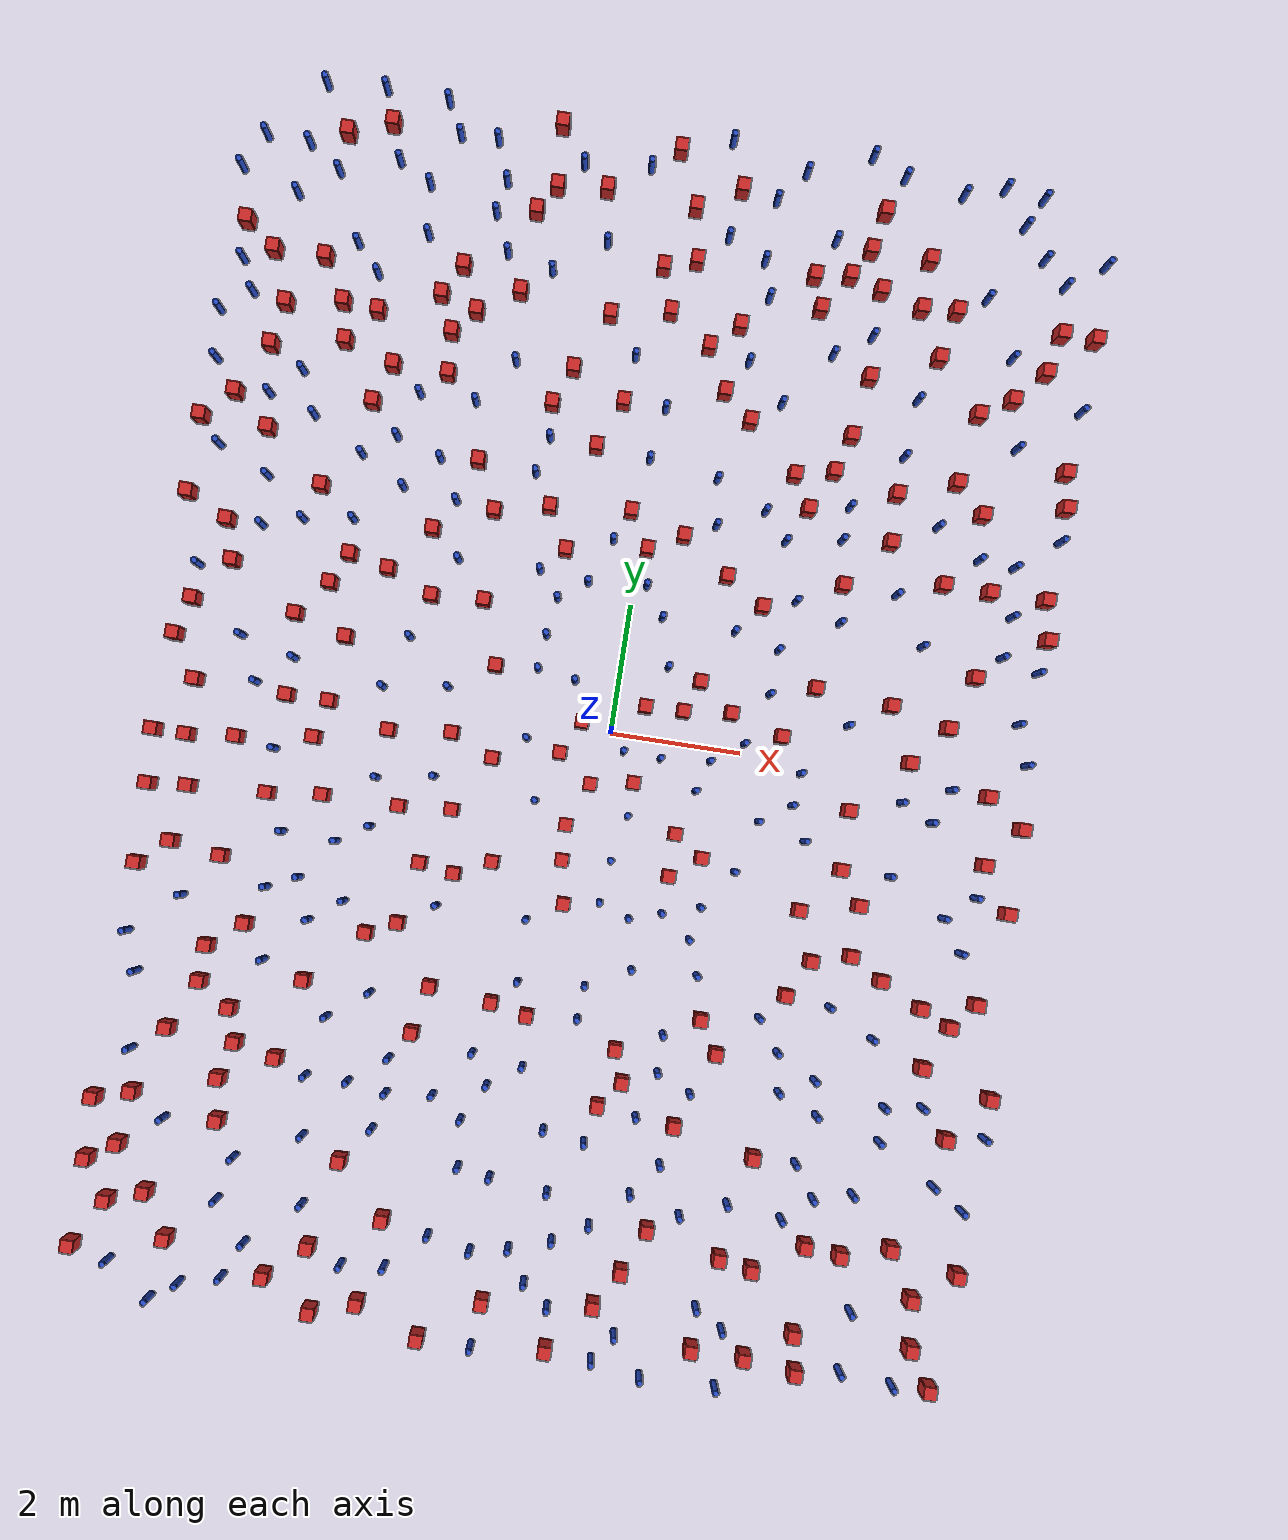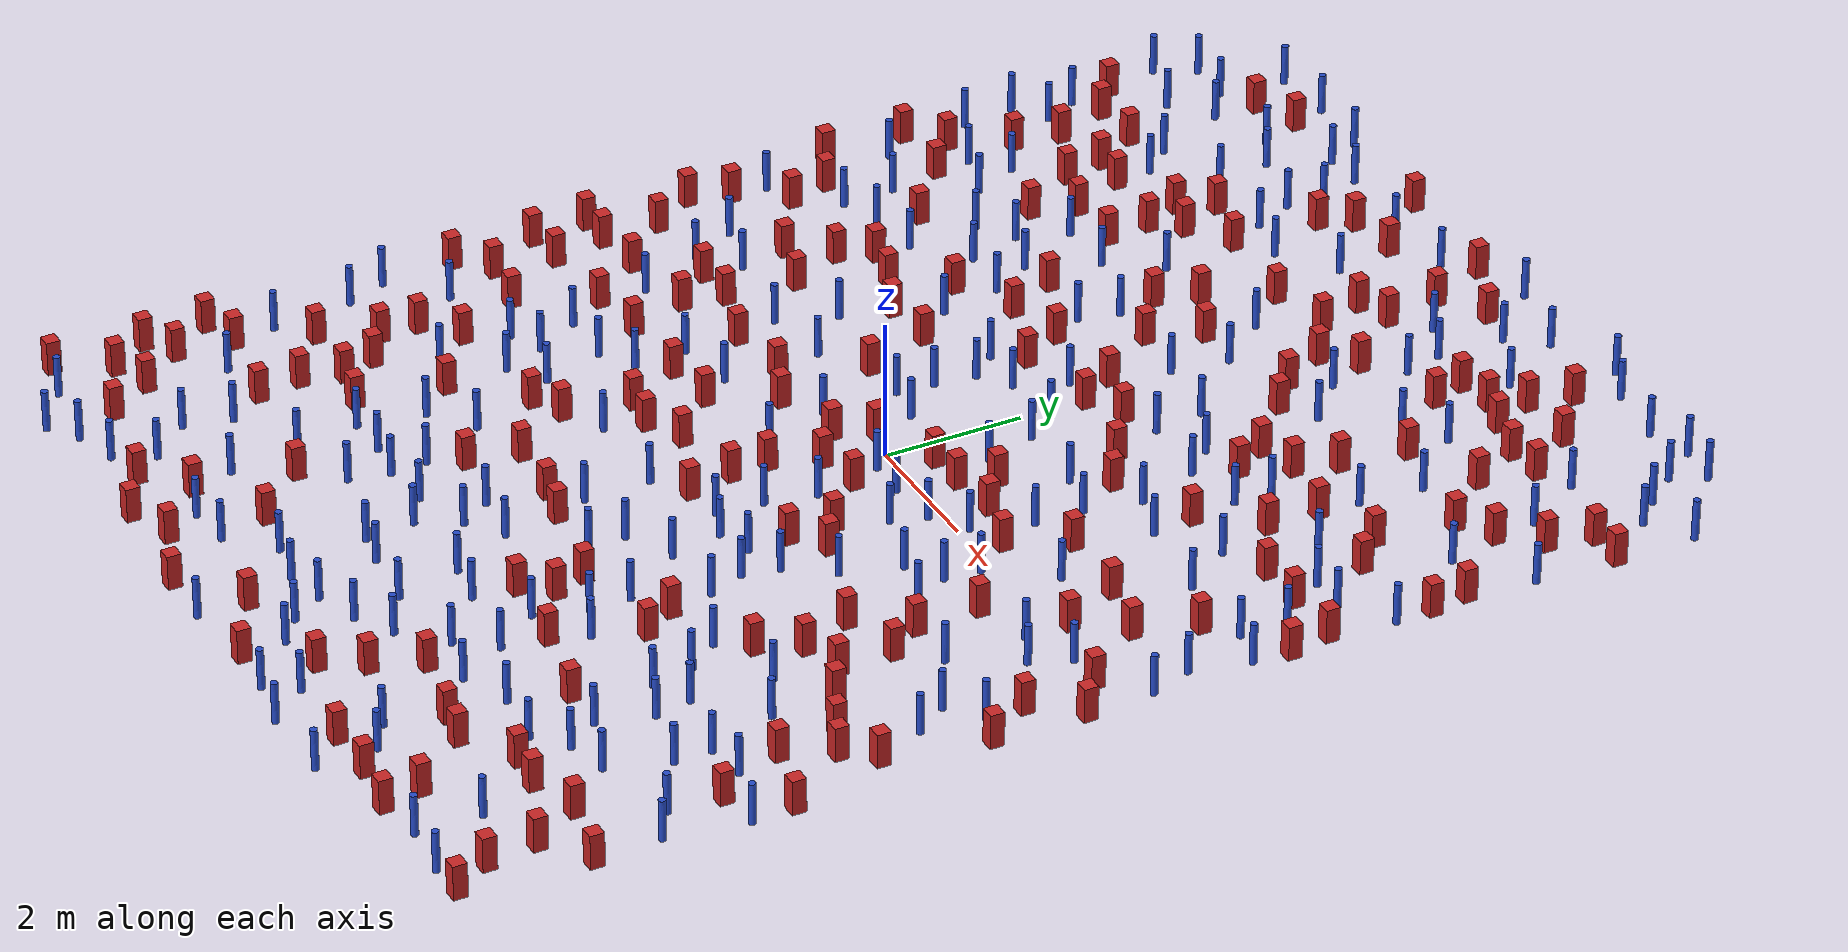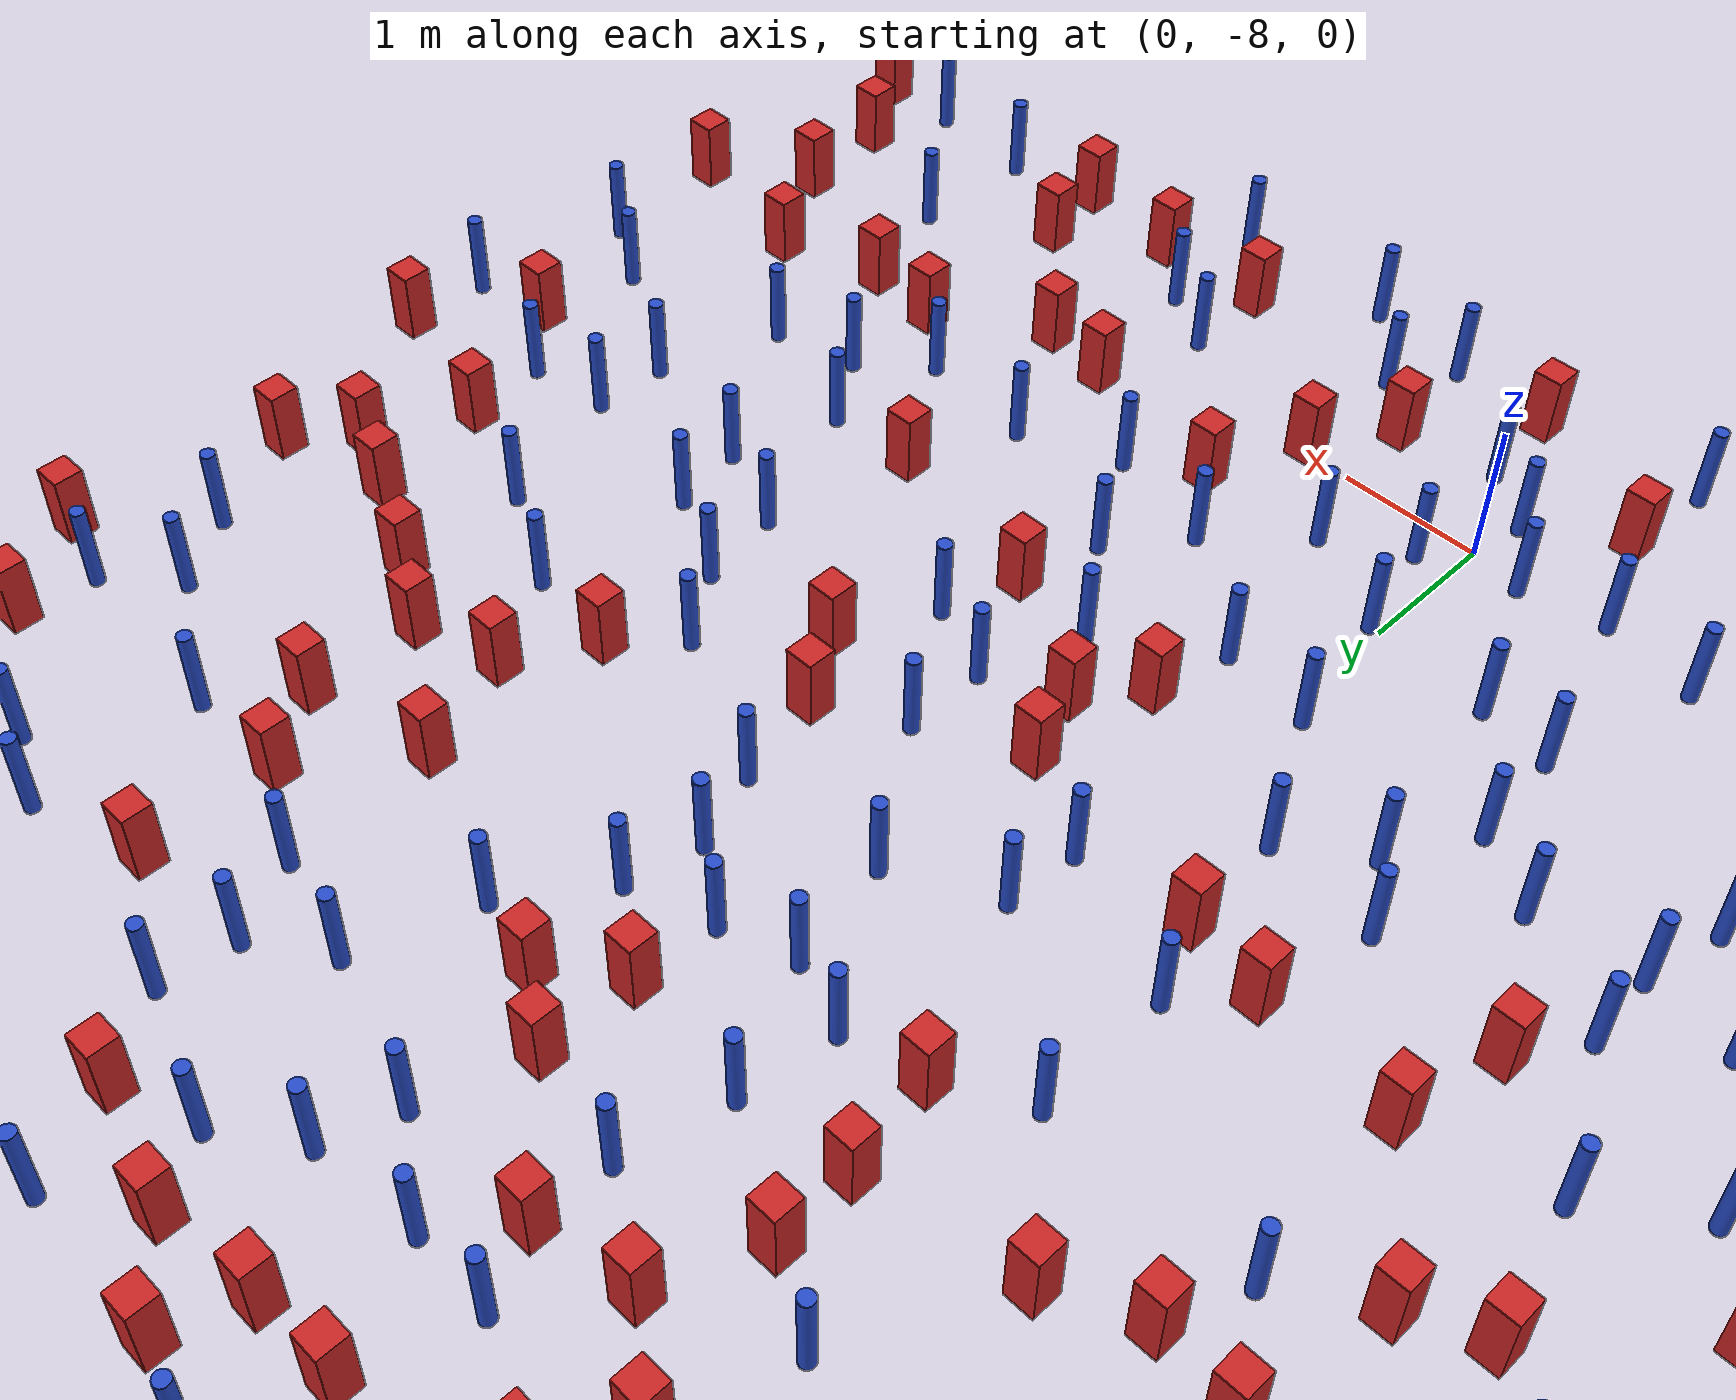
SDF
<sdf version="1.6">
  <model name="dense_2"><model name="square_post_obstacle0">
  <static>true</static>
  <pose frame="">-5.92552398057 -7.88743212732 8.22691968438e-08 7.2212513382e-06 -7.54495500217e-07 2.29674213826e-05</pose>
  <link name="link">
    <pose frame="">0 0 0.25 0 -0 0</pose>
    <inertial>
      <mass>100</mass>
      <inertia>
        <ixx>0.166667</ixx>
        <ixy>0</ixy>
        <ixz>0</ixz>
        <iyy>0.166667</iyy>
        <iyz>0</iyz>
        <izz>0.166667</izz>
      </inertia>
    </inertial>
    <collision name="collision">
      <geometry>
        <box>
          <size>.2 .2 .5</size>
        </box>
      </geometry>
      <max_contacts>10</max_contacts>
      <surface>
        <contact>
          <ode/>
        </contact>
        <bounce/>
        <friction>
          <torsional>
            <ode/>
          </torsional>
          <ode/>
        </friction>
      </surface>
    </collision>
    <visual name="visual">
      <geometry>
        <box>
          <size>.2 .2 .5</size>
        </box>
      </geometry>
      <material>
        <script>
          <name>Gazebo/Red</name>
          <uri>file://media/materials/scripts/gazebo.material</uri>
        </script>
      </material>
    </visual>
    <self_collide>0</self_collide>
    <kinematic>0</kinematic>
  </link>
</model>
<model name="square_post_obstacle1">
  <static>true</static>
  <pose frame="">5.72487765999 -3.64540734115 8.22691968438e-08 7.2212513382e-06 -7.54495500217e-07 2.29674213826e-05</pose>
  <link name="link">
    <pose frame="">0 0 0.25 0 -0 0</pose>
    <inertial>
      <mass>100</mass>
      <inertia>
        <ixx>0.166667</ixx>
        <ixy>0</ixy>
        <ixz>0</ixz>
        <iyy>0.166667</iyy>
        <iyz>0</iyz>
        <izz>0.166667</izz>
      </inertia>
    </inertial>
    <collision name="collision">
      <geometry>
        <box>
          <size>.2 .2 .5</size>
        </box>
      </geometry>
      <max_contacts>10</max_contacts>
      <surface>
        <contact>
          <ode/>
        </contact>
        <bounce/>
        <friction>
          <torsional>
            <ode/>
          </torsional>
          <ode/>
        </friction>
      </surface>
    </collision>
    <visual name="visual">
      <geometry>
        <box>
          <size>.2 .2 .5</size>
        </box>
      </geometry>
      <material>
        <script>
          <name>Gazebo/Red</name>
          <uri>file://media/materials/scripts/gazebo.material</uri>
        </script>
      </material>
    </visual>
    <self_collide>0</self_collide>
    <kinematic>0</kinematic>
  </link>
</model>
<model name="pole_obstacle0">
  <static>true</static>
  <pose frame="">4.51293915702 2.02923295959 2.88873142074e-08 -9.90536689683e-09 4.60219948993e-07 -1.20965994957e-07</pose>
  <link name="link">
  <pose frame="">0 0 0.3 0 -0 0</pose>
    <inertial>
      <mass>1</mass>
      <inertia>
        <ixx>0.145833</ixx>
        <ixy>0</ixy>
        <ixz>0</ixz>
        <iyy>0.145833</iyy>
        <iyz>0</iyz>
        <izz>0.125</izz>
      </inertia>
    </inertial>
    <collision name="collision">
      <geometry>
        <cylinder>
          <radius>0.05</radius>
          <length>.6</length>
        </cylinder>
      </geometry>
      <max_contacts>10</max_contacts>
      <surface>
        <contact>
          <ode/>
        </contact>
        <bounce/>
        <friction>
          <torsional>
            <ode/>
          </torsional>
          <ode/>
        </friction>
      </surface>
    </collision>
    <visual name="visual">
      <geometry>
        <cylinder>
          <radius>0.05</radius>
          <length>.6</length>
        </cylinder>
      </geometry>
      <material>
        <script>
          <name>Gazebo/Blue</name>
          <uri>file://media/materials/scripts/gazebo.material</uri>
        </script>
      </material>
    </visual>
    <self_collide>0</self_collide>
    <kinematic>0</kinematic>
  </link>
</model>
<model name="square_post_obstacle2">
  <static>true</static>
  <pose frame="">1.18272319816 -2.02289545144 8.22691968438e-08 7.2212513382e-06 -7.54495500217e-07 2.29674213826e-05</pose>
  <link name="link">
    <pose frame="">0 0 0.25 0 -0 0</pose>
    <inertial>
      <mass>100</mass>
      <inertia>
        <ixx>0.166667</ixx>
        <ixy>0</ixy>
        <ixz>0</ixz>
        <iyy>0.166667</iyy>
        <iyz>0</iyz>
        <izz>0.166667</izz>
      </inertia>
    </inertial>
    <collision name="collision">
      <geometry>
        <box>
          <size>.2 .2 .5</size>
        </box>
      </geometry>
      <max_contacts>10</max_contacts>
      <surface>
        <contact>
          <ode/>
        </contact>
        <bounce/>
        <friction>
          <torsional>
            <ode/>
          </torsional>
          <ode/>
        </friction>
      </surface>
    </collision>
    <visual name="visual">
      <geometry>
        <box>
          <size>.2 .2 .5</size>
        </box>
      </geometry>
      <material>
        <script>
          <name>Gazebo/Red</name>
          <uri>file://media/materials/scripts/gazebo.material</uri>
        </script>
      </material>
    </visual>
    <self_collide>0</self_collide>
    <kinematic>0</kinematic>
  </link>
</model>
<model name="pole_obstacle1">
  <static>true</static>
  <pose frame="">4.04287633426 -6.49072544475 2.88873142074e-08 -9.90536690822e-09 4.60219948966e-07 -1.20965994976e-07</pose>
  <link name="link">
  <pose frame="">0 0 0.3 0 -0 0</pose>
    <inertial>
      <mass>1</mass>
      <inertia>
        <ixx>0.145833</ixx>
        <ixy>0</ixy>
        <ixz>0</ixz>
        <iyy>0.145833</iyy>
        <iyz>0</iyz>
        <izz>0.125</izz>
      </inertia>
    </inertial>
    <collision name="collision">
      <geometry>
        <cylinder>
          <radius>0.05</radius>
          <length>.6</length>
        </cylinder>
      </geometry>
      <max_contacts>10</max_contacts>
      <surface>
        <contact>
          <ode/>
        </contact>
        <bounce/>
        <friction>
          <torsional>
            <ode/>
          </torsional>
          <ode/>
        </friction>
      </surface>
    </collision>
    <visual name="visual">
      <geometry>
        <cylinder>
          <radius>0.05</radius>
          <length>.6</length>
        </cylinder>
      </geometry>
      <material>
        <script>
          <name>Gazebo/Blue</name>
          <uri>file://media/materials/scripts/gazebo.material</uri>
        </script>
      </material>
    </visual>
    <self_collide>0</self_collide>
    <kinematic>0</kinematic>
  </link>
</model>
<model name="square_post_obstacle3">
  <static>true</static>
  <pose frame="">0.220283548735 7.4439996634 8.22691968438e-08 7.2212513382e-06 -7.54495500217e-07 2.29674213826e-05</pose>
  <link name="link">
    <pose frame="">0 0 0.25 0 -0 0</pose>
    <inertial>
      <mass>100</mass>
      <inertia>
        <ixx>0.166667</ixx>
        <ixy>0</ixy>
        <ixz>0</ixz>
        <iyy>0.166667</iyy>
        <iyz>0</iyz>
        <izz>0.166667</izz>
      </inertia>
    </inertial>
    <collision name="collision">
      <geometry>
        <box>
          <size>.2 .2 .5</size>
        </box>
      </geometry>
      <max_contacts>10</max_contacts>
      <surface>
        <contact>
          <ode/>
        </contact>
        <bounce/>
        <friction>
          <torsional>
            <ode/>
          </torsional>
          <ode/>
        </friction>
      </surface>
    </collision>
    <visual name="visual">
      <geometry>
        <box>
          <size>.2 .2 .5</size>
        </box>
      </geometry>
      <material>
        <script>
          <name>Gazebo/Red</name>
          <uri>file://media/materials/scripts/gazebo.material</uri>
        </script>
      </material>
    </visual>
    <self_collide>0</self_collide>
    <kinematic>0</kinematic>
  </link>
</model>
<model name="pole_obstacle2">
  <static>true</static>
  <pose frame="">1.45222959492 -4.40342588825 2.88873142074e-08 -9.90536689852e-09 4.60219948989e-07 -1.2096599496e-07</pose>
  <link name="link">
  <pose frame="">0 0 0.3 0 -0 0</pose>
    <inertial>
      <mass>1</mass>
      <inertia>
        <ixx>0.145833</ixx>
        <ixy>0</ixy>
        <ixz>0</ixz>
        <iyy>0.145833</iyy>
        <iyz>0</iyz>
        <izz>0.125</izz>
      </inertia>
    </inertial>
    <collision name="collision">
      <geometry>
        <cylinder>
          <radius>0.05</radius>
          <length>.6</length>
        </cylinder>
      </geometry>
      <max_contacts>10</max_contacts>
      <surface>
        <contact>
          <ode/>
        </contact>
        <bounce/>
        <friction>
          <torsional>
            <ode/>
          </torsional>
          <ode/>
        </friction>
      </surface>
    </collision>
    <visual name="visual">
      <geometry>
        <cylinder>
          <radius>0.05</radius>
          <length>.6</length>
        </cylinder>
      </geometry>
      <material>
        <script>
          <name>Gazebo/Blue</name>
          <uri>file://media/materials/scripts/gazebo.material</uri>
        </script>
      </material>
    </visual>
    <self_collide>0</self_collide>
    <kinematic>0</kinematic>
  </link>
</model>
<model name="pole_obstacle3">
  <static>true</static>
  <pose frame="">-6.3174377324 -8.97854769486 2.88873142074e-08 -9.9053668967e-09 4.60219948993e-07 -1.20965994957e-07</pose>
  <link name="link">
  <pose frame="">0 0 0.3 0 -0 0</pose>
    <inertial>
      <mass>1</mass>
      <inertia>
        <ixx>0.145833</ixx>
        <ixy>0</ixy>
        <ixz>0</ixz>
        <iyy>0.145833</iyy>
        <iyz>0</iyz>
        <izz>0.125</izz>
      </inertia>
    </inertial>
    <collision name="collision">
      <geometry>
        <cylinder>
          <radius>0.05</radius>
          <length>.6</length>
        </cylinder>
      </geometry>
      <max_contacts>10</max_contacts>
      <surface>
        <contact>
          <ode/>
        </contact>
        <bounce/>
        <friction>
          <torsional>
            <ode/>
          </torsional>
          <ode/>
        </friction>
      </surface>
    </collision>
    <visual name="visual">
      <geometry>
        <cylinder>
          <radius>0.05</radius>
          <length>.6</length>
        </cylinder>
      </geometry>
      <material>
        <script>
          <name>Gazebo/Blue</name>
          <uri>file://media/materials/scripts/gazebo.material</uri>
        </script>
      </material>
    </visual>
    <self_collide>0</self_collide>
    <kinematic>0</kinematic>
  </link>
</model>
<model name="square_post_obstacle4">
  <static>true</static>
  <pose frame="">2.9893026464 1.14969682416 8.22691968438e-08 7.2212513382e-06 -7.54495500217e-07 2.29674213826e-05</pose>
  <link name="link">
    <pose frame="">0 0 0.25 0 -0 0</pose>
    <inertial>
      <mass>100</mass>
      <inertia>
        <ixx>0.166667</ixx>
        <ixy>0</ixy>
        <ixz>0</ixz>
        <iyy>0.166667</iyy>
        <iyz>0</iyz>
        <izz>0.166667</izz>
      </inertia>
    </inertial>
    <collision name="collision">
      <geometry>
        <box>
          <size>.2 .2 .5</size>
        </box>
      </geometry>
      <max_contacts>10</max_contacts>
      <surface>
        <contact>
          <ode/>
        </contact>
        <bounce/>
        <friction>
          <torsional>
            <ode/>
          </torsional>
          <ode/>
        </friction>
      </surface>
    </collision>
    <visual name="visual">
      <geometry>
        <box>
          <size>.2 .2 .5</size>
        </box>
      </geometry>
      <material>
        <script>
          <name>Gazebo/Red</name>
          <uri>file://media/materials/scripts/gazebo.material</uri>
        </script>
      </material>
    </visual>
    <self_collide>0</self_collide>
    <kinematic>0</kinematic>
  </link>
</model>
<model name="square_post_obstacle5">
  <static>true</static>
  <pose frame="">-2.51365523219 -9.04669653167 8.22691968438e-08 7.22125133819e-06 -7.54495500217e-07 2.29674213826e-05</pose>
  <link name="link">
    <pose frame="">0 0 0.25 0 -0 0</pose>
    <inertial>
      <mass>100</mass>
      <inertia>
        <ixx>0.166667</ixx>
        <ixy>0</ixy>
        <ixz>0</ixz>
        <iyy>0.166667</iyy>
        <iyz>0</iyz>
        <izz>0.166667</izz>
      </inertia>
    </inertial>
    <collision name="collision">
      <geometry>
        <box>
          <size>.2 .2 .5</size>
        </box>
      </geometry>
      <max_contacts>10</max_contacts>
      <surface>
        <contact>
          <ode/>
        </contact>
        <bounce/>
        <friction>
          <torsional>
            <ode/>
          </torsional>
          <ode/>
        </friction>
      </surface>
    </collision>
    <visual name="visual">
      <geometry>
        <box>
          <size>.2 .2 .5</size>
        </box>
      </geometry>
      <material>
        <script>
          <name>Gazebo/Red</name>
          <uri>file://media/materials/scripts/gazebo.material</uri>
        </script>
      </material>
    </visual>
    <self_collide>0</self_collide>
    <kinematic>0</kinematic>
  </link>
</model>
<model name="square_post_obstacle6">
  <static>true</static>
  <pose frame="">-0.278047388388 9.13855485303 8.22691968438e-08 7.22125133819e-06 -7.54495500217e-07 2.29674213826e-05</pose>
  <link name="link">
    <pose frame="">0 0 0.25 0 -0 0</pose>
    <inertial>
      <mass>100</mass>
      <inertia>
        <ixx>0.166667</ixx>
        <ixy>0</ixy>
        <ixz>0</ixz>
        <iyy>0.166667</iyy>
        <iyz>0</iyz>
        <izz>0.166667</izz>
      </inertia>
    </inertial>
    <collision name="collision">
      <geometry>
        <box>
          <size>.2 .2 .5</size>
        </box>
      </geometry>
      <max_contacts>10</max_contacts>
      <surface>
        <contact>
          <ode/>
        </contact>
        <bounce/>
        <friction>
          <torsional>
            <ode/>
          </torsional>
          <ode/>
        </friction>
      </surface>
    </collision>
    <visual name="visual">
      <geometry>
        <box>
          <size>.2 .2 .5</size>
        </box>
      </geometry>
      <material>
        <script>
          <name>Gazebo/Red</name>
          <uri>file://media/materials/scripts/gazebo.material</uri>
        </script>
      </material>
    </visual>
    <self_collide>0</self_collide>
    <kinematic>0</kinematic>
  </link>
</model>
<model name="pole_obstacle4">
  <static>true</static>
  <pose frame="">1.83298338898 -3.44916255037 2.88873142074e-08 -9.90536689791e-09 4.6021994899e-07 -1.20965994959e-07</pose>
  <link name="link">
  <pose frame="">0 0 0.3 0 -0 0</pose>
    <inertial>
      <mass>1</mass>
      <inertia>
        <ixx>0.145833</ixx>
        <ixy>0</ixy>
        <ixz>0</ixz>
        <iyy>0.145833</iyy>
        <iyz>0</iyz>
        <izz>0.125</izz>
      </inertia>
    </inertial>
    <collision name="collision">
      <geometry>
        <cylinder>
          <radius>0.05</radius>
          <length>.6</length>
        </cylinder>
      </geometry>
      <max_contacts>10</max_contacts>
      <surface>
        <contact>
          <ode/>
        </contact>
        <bounce/>
        <friction>
          <torsional>
            <ode/>
          </torsional>
          <ode/>
        </friction>
      </surface>
    </collision>
    <visual name="visual">
      <geometry>
        <cylinder>
          <radius>0.05</radius>
          <length>.6</length>
        </cylinder>
      </geometry>
      <material>
        <script>
          <name>Gazebo/Blue</name>
          <uri>file://media/materials/scripts/gazebo.material</uri>
        </script>
      </material>
    </visual>
    <self_collide>0</self_collide>
    <kinematic>0</kinematic>
  </link>
</model>
<model name="pole_obstacle5">
  <static>true</static>
  <pose frame="">-0.822284344405 -6.90274951284 2.88873142074e-08 -9.90536689661e-09 4.60219948993e-07 -1.20965994957e-07</pose>
  <link name="link">
  <pose frame="">0 0 0.3 0 -0 0</pose>
    <inertial>
      <mass>1</mass>
      <inertia>
        <ixx>0.145833</ixx>
        <ixy>0</ixy>
        <ixz>0</ixz>
        <iyy>0.145833</iyy>
        <iyz>0</iyz>
        <izz>0.125</izz>
      </inertia>
    </inertial>
    <collision name="collision">
      <geometry>
        <cylinder>
          <radius>0.05</radius>
          <length>.6</length>
        </cylinder>
      </geometry>
      <max_contacts>10</max_contacts>
      <surface>
        <contact>
          <ode/>
        </contact>
        <bounce/>
        <friction>
          <torsional>
            <ode/>
          </torsional>
          <ode/>
        </friction>
      </surface>
    </collision>
    <visual name="visual">
      <geometry>
        <cylinder>
          <radius>0.05</radius>
          <length>.6</length>
        </cylinder>
      </geometry>
      <material>
        <script>
          <name>Gazebo/Blue</name>
          <uri>file://media/materials/scripts/gazebo.material</uri>
        </script>
      </material>
    </visual>
    <self_collide>0</self_collide>
    <kinematic>0</kinematic>
  </link>
</model>
<model name="square_post_obstacle7">
  <static>true</static>
  <pose frame="">1.76672728972 0.576758571005 8.22691968438e-08 7.22125133819e-06 -7.54495500217e-07 2.29674213826e-05</pose>
  <link name="link">
    <pose frame="">0 0 0.25 0 -0 0</pose>
    <inertial>
      <mass>100</mass>
      <inertia>
        <ixx>0.166667</ixx>
        <ixy>0</ixy>
        <ixz>0</ixz>
        <iyy>0.166667</iyy>
        <iyz>0</iyz>
        <izz>0.166667</izz>
      </inertia>
    </inertial>
    <collision name="collision">
      <geometry>
        <box>
          <size>.2 .2 .5</size>
        </box>
      </geometry>
      <max_contacts>10</max_contacts>
      <surface>
        <contact>
          <ode/>
        </contact>
        <bounce/>
        <friction>
          <torsional>
            <ode/>
          </torsional>
          <ode/>
        </friction>
      </surface>
    </collision>
    <visual name="visual">
      <geometry>
        <box>
          <size>.2 .2 .5</size>
        </box>
      </geometry>
      <material>
        <script>
          <name>Gazebo/Red</name>
          <uri>file://media/materials/scripts/gazebo.material</uri>
        </script>
      </material>
    </visual>
    <self_collide>0</self_collide>
    <kinematic>0</kinematic>
  </link>
</model>
<model name="square_post_obstacle8">
  <static>true</static>
  <pose frame="">-0.275440074873 7.2741674177 8.22691968438e-08 7.2212513382e-06 -7.54495500217e-07 2.29674213826e-05</pose>
  <link name="link">
    <pose frame="">0 0 0.25 0 -0 0</pose>
    <inertial>
      <mass>100</mass>
      <inertia>
        <ixx>0.166667</ixx>
        <ixy>0</ixy>
        <ixz>0</ixz>
        <iyy>0.166667</iyy>
        <iyz>0</iyz>
        <izz>0.166667</izz>
      </inertia>
    </inertial>
    <collision name="collision">
      <geometry>
        <box>
          <size>.2 .2 .5</size>
        </box>
      </geometry>
      <max_contacts>10</max_contacts>
      <surface>
        <contact>
          <ode/>
        </contact>
        <bounce/>
        <friction>
          <torsional>
            <ode/>
          </torsional>
          <ode/>
        </friction>
      </surface>
    </collision>
    <visual name="visual">
      <geometry>
        <box>
          <size>.2 .2 .5</size>
        </box>
      </geometry>
      <material>
        <script>
          <name>Gazebo/Red</name>
          <uri>file://media/materials/scripts/gazebo.material</uri>
        </script>
      </material>
    </visual>
    <self_collide>0</self_collide>
    <kinematic>0</kinematic>
  </link>
</model>
<model name="pole_obstacle6">
  <static>true</static>
  <pose frame="">2.69425308004 9.47498781607 2.88873142074e-08 -9.90536692318e-09 4.6021994893e-07 -1.20965994988e-07</pose>
  <link name="link">
  <pose frame="">0 0 0.3 0 -0 0</pose>
    <inertial>
      <mass>1</mass>
      <inertia>
        <ixx>0.145833</ixx>
        <ixy>0</ixy>
        <ixz>0</ixz>
        <iyy>0.145833</iyy>
        <iyz>0</iyz>
        <izz>0.125</izz>
      </inertia>
    </inertial>
    <collision name="collision">
      <geometry>
        <cylinder>
          <radius>0.05</radius>
          <length>.6</length>
        </cylinder>
      </geometry>
      <max_contacts>10</max_contacts>
      <surface>
        <contact>
          <ode/>
        </contact>
        <bounce/>
        <friction>
          <torsional>
            <ode/>
          </torsional>
          <ode/>
        </friction>
      </surface>
    </collision>
    <visual name="visual">
      <geometry>
        <cylinder>
          <radius>0.05</radius>
          <length>.6</length>
        </cylinder>
      </geometry>
      <material>
        <script>
          <name>Gazebo/Blue</name>
          <uri>file://media/materials/scripts/gazebo.material</uri>
        </script>
      </material>
    </visual>
    <self_collide>0</self_collide>
    <kinematic>0</kinematic>
  </link>
</model>
<model name="pole_obstacle7">
  <static>true</static>
  <pose frame="">5.8151142587 -6.04497353995 2.88873142074e-08 -9.90536690842e-09 4.60219948965e-07 -1.20965994976e-07</pose>
  <link name="link">
  <pose frame="">0 0 0.3 0 -0 0</pose>
    <inertial>
      <mass>1</mass>
      <inertia>
        <ixx>0.145833</ixx>
        <ixy>0</ixy>
        <ixz>0</ixz>
        <iyy>0.145833</iyy>
        <iyz>0</iyz>
        <izz>0.125</izz>
      </inertia>
    </inertial>
    <collision name="collision">
      <geometry>
        <cylinder>
          <radius>0.05</radius>
          <length>.6</length>
        </cylinder>
      </geometry>
      <max_contacts>10</max_contacts>
      <surface>
        <contact>
          <ode/>
        </contact>
        <bounce/>
        <friction>
          <torsional>
            <ode/>
          </torsional>
          <ode/>
        </friction>
      </surface>
    </collision>
    <visual name="visual">
      <geometry>
        <cylinder>
          <radius>0.05</radius>
          <length>.6</length>
        </cylinder>
      </geometry>
      <material>
        <script>
          <name>Gazebo/Blue</name>
          <uri>file://media/materials/scripts/gazebo.material</uri>
        </script>
      </material>
    </visual>
    <self_collide>0</self_collide>
    <kinematic>0</kinematic>
  </link>
</model>
<model name="square_post_obstacle9">
  <static>true</static>
  <pose frame="">3.78639637061 7.98627830931 8.22691968438e-08 7.22125133819e-06 -7.54495500217e-07 2.29674213826e-05</pose>
  <link name="link">
    <pose frame="">0 0 0.25 0 -0 0</pose>
    <inertial>
      <mass>100</mass>
      <inertia>
        <ixx>0.166667</ixx>
        <ixy>0</ixy>
        <ixz>0</ixz>
        <iyy>0.166667</iyy>
        <iyz>0</iyz>
        <izz>0.166667</izz>
      </inertia>
    </inertial>
    <collision name="collision">
      <geometry>
        <box>
          <size>.2 .2 .5</size>
        </box>
      </geometry>
      <max_contacts>10</max_contacts>
      <surface>
        <contact>
          <ode/>
        </contact>
        <bounce/>
        <friction>
          <torsional>
            <ode/>
          </torsional>
          <ode/>
        </friction>
      </surface>
    </collision>
    <visual name="visual">
      <geometry>
        <box>
          <size>.2 .2 .5</size>
        </box>
      </geometry>
      <material>
        <script>
          <name>Gazebo/Red</name>
          <uri>file://media/materials/scripts/gazebo.material</uri>
        </script>
      </material>
    </visual>
    <self_collide>0</self_collide>
    <kinematic>0</kinematic>
  </link>
</model>
<model name="square_post_obstacle10">
  <static>true</static>
  <pose frame="">-2.78559075855 -3.33132240373 8.22691968438e-08 7.2212513382e-06 -7.54495500217e-07 2.29674213826e-05</pose>
  <link name="link">
    <pose frame="">0 0 0.25 0 -0 0</pose>
    <inertial>
      <mass>100</mass>
      <inertia>
        <ixx>0.166667</ixx>
        <ixy>0</ixy>
        <ixz>0</ixz>
        <iyy>0.166667</iyy>
        <iyz>0</iyz>
        <izz>0.166667</izz>
      </inertia>
    </inertial>
    <collision name="collision">
      <geometry>
        <box>
          <size>.2 .2 .5</size>
        </box>
      </geometry>
      <max_contacts>10</max_contacts>
      <surface>
        <contact>
          <ode/>
        </contact>
        <bounce/>
        <friction>
          <torsional>
            <ode/>
          </torsional>
          <ode/>
        </friction>
      </surface>
    </collision>
    <visual name="visual">
      <geometry>
        <box>
          <size>.2 .2 .5</size>
        </box>
      </geometry>
      <material>
        <script>
          <name>Gazebo/Red</name>
          <uri>file://media/materials/scripts/gazebo.material</uri>
        </script>
      </material>
    </visual>
    <self_collide>0</self_collide>
    <kinematic>0</kinematic>
  </link>
</model>
<model name="square_post_obstacle11">
  <static>true</static>
  <pose frame="">2.5807275553 0.337207331482 8.22691968438e-08 7.2212513382e-06 -7.54495500217e-07 2.29674213826e-05</pose>
  <link name="link">
    <pose frame="">0 0 0.25 0 -0 0</pose>
    <inertial>
      <mass>100</mass>
      <inertia>
        <ixx>0.166667</ixx>
        <ixy>0</ixy>
        <ixz>0</ixz>
        <iyy>0.166667</iyy>
        <iyz>0</iyz>
        <izz>0.166667</izz>
      </inertia>
    </inertial>
    <collision name="collision">
      <geometry>
        <box>
          <size>.2 .2 .5</size>
        </box>
      </geometry>
      <max_contacts>10</max_contacts>
      <surface>
        <contact>
          <ode/>
        </contact>
        <bounce/>
        <friction>
          <torsional>
            <ode/>
          </torsional>
          <ode/>
        </friction>
      </surface>
    </collision>
    <visual name="visual">
      <geometry>
        <box>
          <size>.2 .2 .5</size>
        </box>
      </geometry>
      <material>
        <script>
          <name>Gazebo/Red</name>
          <uri>file://media/materials/scripts/gazebo.material</uri>
        </script>
      </material>
    </visual>
    <self_collide>0</self_collide>
    <kinematic>0</kinematic>
  </link>
</model>
<model name="square_post_obstacle12">
  <static>true</static>
  <pose frame="">5.37687361299 1.67094948875 8.22691968438e-08 7.2212513382e-06 -7.54495500217e-07 2.29674213826e-05</pose>
  <link name="link">
    <pose frame="">0 0 0.25 0 -0 0</pose>
    <inertial>
      <mass>100</mass>
      <inertia>
        <ixx>0.166667</ixx>
        <ixy>0</ixy>
        <ixz>0</ixz>
        <iyy>0.166667</iyy>
        <iyz>0</iyz>
        <izz>0.166667</izz>
      </inertia>
    </inertial>
    <collision name="collision">
      <geometry>
        <box>
          <size>.2 .2 .5</size>
        </box>
      </geometry>
      <max_contacts>10</max_contacts>
      <surface>
        <contact>
          <ode/>
        </contact>
        <bounce/>
        <friction>
          <torsional>
            <ode/>
          </torsional>
          <ode/>
        </friction>
      </surface>
    </collision>
    <visual name="visual">
      <geometry>
        <box>
          <size>.2 .2 .5</size>
        </box>
      </geometry>
      <material>
        <script>
          <name>Gazebo/Red</name>
          <uri>file://media/materials/scripts/gazebo.material</uri>
        </script>
      </material>
    </visual>
    <self_collide>0</self_collide>
    <kinematic>0</kinematic>
  </link>
</model>
<model name="square_post_obstacle13">
  <static>true</static>
  <pose frame="">5.40528865388 -4.31110512093 8.22691968438e-08 7.2212513382e-06 -7.54495500217e-07 2.29674213826e-05</pose>
  <link name="link">
    <pose frame="">0 0 0.25 0 -0 0</pose>
    <inertial>
      <mass>100</mass>
      <inertia>
        <ixx>0.166667</ixx>
        <ixy>0</ixy>
        <ixz>0</ixz>
        <iyy>0.166667</iyy>
        <iyz>0</iyz>
        <izz>0.166667</izz>
      </inertia>
    </inertial>
    <collision name="collision">
      <geometry>
        <box>
          <size>.2 .2 .5</size>
        </box>
      </geometry>
      <max_contacts>10</max_contacts>
      <surface>
        <contact>
          <ode/>
        </contact>
        <bounce/>
        <friction>
          <torsional>
            <ode/>
          </torsional>
          <ode/>
        </friction>
      </surface>
    </collision>
    <visual name="visual">
      <geometry>
        <box>
          <size>.2 .2 .5</size>
        </box>
      </geometry>
      <material>
        <script>
          <name>Gazebo/Red</name>
          <uri>file://media/materials/scripts/gazebo.material</uri>
        </script>
      </material>
    </visual>
    <self_collide>0</self_collide>
    <kinematic>0</kinematic>
  </link>
</model>
<model name="pole_obstacle8">
  <static>true</static>
  <pose frame="">2.31026452429 8.07180939021 2.88873142074e-08 -9.90536692318e-09 4.6021994893e-07 -1.20965994988e-07</pose>
  <link name="link">
  <pose frame="">0 0 0.3 0 -0 0</pose>
    <inertial>
      <mass>1</mass>
      <inertia>
        <ixx>0.145833</ixx>
        <ixy>0</ixy>
        <ixz>0</ixz>
        <iyy>0.145833</iyy>
        <iyz>0</iyz>
        <izz>0.125</izz>
      </inertia>
    </inertial>
    <collision name="collision">
      <geometry>
        <cylinder>
          <radius>0.05</radius>
          <length>.6</length>
        </cylinder>
      </geometry>
      <max_contacts>10</max_contacts>
      <surface>
        <contact>
          <ode/>
        </contact>
        <bounce/>
        <friction>
          <torsional>
            <ode/>
          </torsional>
          <ode/>
        </friction>
      </surface>
    </collision>
    <visual name="visual">
      <geometry>
        <cylinder>
          <radius>0.05</radius>
          <length>.6</length>
        </cylinder>
      </geometry>
      <material>
        <script>
          <name>Gazebo/Blue</name>
          <uri>file://media/materials/scripts/gazebo.material</uri>
        </script>
      </material>
    </visual>
    <self_collide>0</self_collide>
    <kinematic>0</kinematic>
  </link>
</model>
<model name="square_post_obstacle14">
  <static>true</static>
  <pose frame="">-6.39441163497 -2.61521872058 8.22691968438e-08 7.2212513382e-06 -7.54495500217e-07 2.29674213826e-05</pose>
  <link name="link">
    <pose frame="">0 0 0.25 0 -0 0</pose>
    <inertial>
      <mass>100</mass>
      <inertia>
        <ixx>0.166667</ixx>
        <ixy>0</ixy>
        <ixz>0</ixz>
        <iyy>0.166667</iyy>
        <iyz>0</iyz>
        <izz>0.166667</izz>
      </inertia>
    </inertial>
    <collision name="collision">
      <geometry>
        <box>
          <size>.2 .2 .5</size>
        </box>
      </geometry>
      <max_contacts>10</max_contacts>
      <surface>
        <contact>
          <ode/>
        </contact>
        <bounce/>
        <friction>
          <torsional>
            <ode/>
          </torsional>
          <ode/>
        </friction>
      </surface>
    </collision>
    <visual name="visual">
      <geometry>
        <box>
          <size>.2 .2 .5</size>
        </box>
      </geometry>
      <material>
        <script>
          <name>Gazebo/Red</name>
          <uri>file://media/materials/scripts/gazebo.material</uri>
        </script>
      </material>
    </visual>
    <self_collide>0</self_collide>
    <kinematic>0</kinematic>
  </link>
</model>
<model name="square_post_obstacle15">
  <static>true</static>
  <pose frame="">-5.42483959669 8.63668110623 8.22691968438e-08 7.22125133819e-06 -7.54495500217e-07 2.29674213826e-05</pose>
  <link name="link">
    <pose frame="">0 0 0.25 0 -0 0</pose>
    <inertial>
      <mass>100</mass>
      <inertia>
        <ixx>0.166667</ixx>
        <ixy>0</ixy>
        <ixz>0</ixz>
        <iyy>0.166667</iyy>
        <iyz>0</iyz>
        <izz>0.166667</izz>
      </inertia>
    </inertial>
    <collision name="collision">
      <geometry>
        <box>
          <size>.2 .2 .5</size>
        </box>
      </geometry>
      <max_contacts>10</max_contacts>
      <surface>
        <contact>
          <ode/>
        </contact>
        <bounce/>
        <friction>
          <torsional>
            <ode/>
          </torsional>
          <ode/>
        </friction>
      </surface>
    </collision>
    <visual name="visual">
      <geometry>
        <box>
          <size>.2 .2 .5</size>
        </box>
      </geometry>
      <material>
        <script>
          <name>Gazebo/Red</name>
          <uri>file://media/materials/scripts/gazebo.material</uri>
        </script>
      </material>
    </visual>
    <self_collide>0</self_collide>
    <kinematic>0</kinematic>
  </link>
</model>
<model name="square_post_obstacle16">
  <static>true</static>
  <pose frame="">-6.51845038567 4.35904660605 8.22691968438e-08 7.2212513382e-06 -7.54495500217e-07 2.29674213826e-05</pose>
  <link name="link">
    <pose frame="">0 0 0.25 0 -0 0</pose>
    <inertial>
      <mass>100</mass>
      <inertia>
        <ixx>0.166667</ixx>
        <ixy>0</ixy>
        <ixz>0</ixz>
        <iyy>0.166667</iyy>
        <iyz>0</iyz>
        <izz>0.166667</izz>
      </inertia>
    </inertial>
    <collision name="collision">
      <geometry>
        <box>
          <size>.2 .2 .5</size>
        </box>
      </geometry>
      <max_contacts>10</max_contacts>
      <surface>
        <contact>
          <ode/>
        </contact>
        <bounce/>
        <friction>
          <torsional>
            <ode/>
          </torsional>
          <ode/>
        </friction>
      </surface>
    </collision>
    <visual name="visual">
      <geometry>
        <box>
          <size>.2 .2 .5</size>
        </box>
      </geometry>
      <material>
        <script>
          <name>Gazebo/Red</name>
          <uri>file://media/materials/scripts/gazebo.material</uri>
        </script>
      </material>
    </visual>
    <self_collide>0</self_collide>
    <kinematic>0</kinematic>
  </link>
</model>
<model name="pole_obstacle9">
  <static>true</static>
  <pose frame="">2.51598019912 6.29896532646 2.88873142074e-08 -9.90536689859e-09 4.60219948989e-07 -1.20965994961e-07</pose>
  <link name="link">
  <pose frame="">0 0 0.3 0 -0 0</pose>
    <inertial>
      <mass>1</mass>
      <inertia>
        <ixx>0.145833</ixx>
        <ixy>0</ixy>
        <ixz>0</ixz>
        <iyy>0.145833</iyy>
        <iyz>0</iyz>
        <izz>0.125</izz>
      </inertia>
    </inertial>
    <collision name="collision">
      <geometry>
        <cylinder>
          <radius>0.05</radius>
          <length>.6</length>
        </cylinder>
      </geometry>
      <max_contacts>10</max_contacts>
      <surface>
        <contact>
          <ode/>
        </contact>
        <bounce/>
        <friction>
          <torsional>
            <ode/>
          </torsional>
          <ode/>
        </friction>
      </surface>
    </collision>
    <visual name="visual">
      <geometry>
        <cylinder>
          <radius>0.05</radius>
          <length>.6</length>
        </cylinder>
      </geometry>
      <material>
        <script>
          <name>Gazebo/Blue</name>
          <uri>file://media/materials/scripts/gazebo.material</uri>
        </script>
      </material>
    </visual>
    <self_collide>0</self_collide>
    <kinematic>0</kinematic>
  </link>
</model>
<model name="square_post_obstacle17">
  <static>true</static>
  <pose frame="">4.68955021579 4.60673280405 8.22691968438e-08 7.2212513382e-06 -7.54495500217e-07 2.29674213826e-05</pose>
  <link name="link">
    <pose frame="">0 0 0.25 0 -0 0</pose>
    <inertial>
      <mass>100</mass>
      <inertia>
        <ixx>0.166667</ixx>
        <ixy>0</ixy>
        <ixz>0</ixz>
        <iyy>0.166667</iyy>
        <iyz>0</iyz>
        <izz>0.166667</izz>
      </inertia>
    </inertial>
    <collision name="collision">
      <geometry>
        <box>
          <size>.2 .2 .5</size>
        </box>
      </geometry>
      <max_contacts>10</max_contacts>
      <surface>
        <contact>
          <ode/>
        </contact>
        <bounce/>
        <friction>
          <torsional>
            <ode/>
          </torsional>
          <ode/>
        </friction>
      </surface>
    </collision>
    <visual name="visual">
      <geometry>
        <box>
          <size>.2 .2 .5</size>
        </box>
      </geometry>
      <material>
        <script>
          <name>Gazebo/Red</name>
          <uri>file://media/materials/scripts/gazebo.material</uri>
        </script>
      </material>
    </visual>
    <self_collide>0</self_collide>
    <kinematic>0</kinematic>
  </link>
</model>
<model name="square_post_obstacle18">
  <static>true</static>
  <pose frame="">-6.41459367247 -0.975588047987 8.22691968438e-08 7.2212513382e-06 -7.54495500217e-07 2.29674213826e-05</pose>
  <link name="link">
    <pose frame="">0 0 0.25 0 -0 0</pose>
    <inertial>
      <mass>100</mass>
      <inertia>
        <ixx>0.166667</ixx>
        <ixy>0</ixy>
        <ixz>0</ixz>
        <iyy>0.166667</iyy>
        <iyz>0</iyz>
        <izz>0.166667</izz>
      </inertia>
    </inertial>
    <collision name="collision">
      <geometry>
        <box>
          <size>.2 .2 .5</size>
        </box>
      </geometry>
      <max_contacts>10</max_contacts>
      <surface>
        <contact>
          <ode/>
        </contact>
        <bounce/>
        <friction>
          <torsional>
            <ode/>
          </torsional>
          <ode/>
        </friction>
      </surface>
    </collision>
    <visual name="visual">
      <geometry>
        <box>
          <size>.2 .2 .5</size>
        </box>
      </geometry>
      <material>
        <script>
          <name>Gazebo/Red</name>
          <uri>file://media/materials/scripts/gazebo.material</uri>
        </script>
      </material>
    </visual>
    <self_collide>0</self_collide>
    <kinematic>0</kinematic>
  </link>
</model>
<model name="pole_obstacle10">
  <static>true</static>
  <pose frame="">6.29186113247 -6.3446759552 2.88873142074e-08 -9.90536690842e-09 4.60219948965e-07 -1.20965994976e-07</pose>
  <link name="link">
  <pose frame="">0 0 0.3 0 -0 0</pose>
    <inertial>
      <mass>1</mass>
      <inertia>
        <ixx>0.145833</ixx>
        <ixy>0</ixy>
        <ixz>0</ixz>
        <iyy>0.145833</iyy>
        <iyz>0</iyz>
        <izz>0.125</izz>
      </inertia>
    </inertial>
    <collision name="collision">
      <geometry>
        <cylinder>
          <radius>0.05</radius>
          <length>.6</length>
        </cylinder>
      </geometry>
      <max_contacts>10</max_contacts>
      <surface>
        <contact>
          <ode/>
        </contact>
        <bounce/>
        <friction>
          <torsional>
            <ode/>
          </torsional>
          <ode/>
        </friction>
      </surface>
    </collision>
    <visual name="visual">
      <geometry>
        <cylinder>
          <radius>0.05</radius>
          <length>.6</length>
        </cylinder>
      </geometry>
      <material>
        <script>
          <name>Gazebo/Blue</name>
          <uri>file://media/materials/scripts/gazebo.material</uri>
        </script>
      </material>
    </visual>
    <self_collide>0</self_collide>
    <kinematic>0</kinematic>
  </link>
</model>
<model name="square_post_obstacle19">
  <static>true</static>
  <pose frame="">4.11415829672 -2.03390158334 8.22691968438e-08 7.2212513382e-06 -7.54495500217e-07 2.29674213826e-05</pose>
  <link name="link">
    <pose frame="">0 0 0.25 0 -0 0</pose>
    <inertial>
      <mass>100</mass>
      <inertia>
        <ixx>0.166667</ixx>
        <ixy>0</ixy>
        <ixz>0</ixz>
        <iyy>0.166667</iyy>
        <iyz>0</iyz>
        <izz>0.166667</izz>
      </inertia>
    </inertial>
    <collision name="collision">
      <geometry>
        <box>
          <size>.2 .2 .5</size>
        </box>
      </geometry>
      <max_contacts>10</max_contacts>
      <surface>
        <contact>
          <ode/>
        </contact>
        <bounce/>
        <friction>
          <torsional>
            <ode/>
          </torsional>
          <ode/>
        </friction>
      </surface>
    </collision>
    <visual name="visual">
      <geometry>
        <box>
          <size>.2 .2 .5</size>
        </box>
      </geometry>
      <material>
        <script>
          <name>Gazebo/Red</name>
          <uri>file://media/materials/scripts/gazebo.material</uri>
        </script>
      </material>
    </visual>
    <self_collide>0</self_collide>
    <kinematic>0</kinematic>
  </link>
</model>
<model name="pole_obstacle11">
  <static>true</static>
  <pose frame="">-1.0749578244 -5.55144896337 2.88873142074e-08 -9.90536689852e-09 4.60219948989e-07 -1.2096599496e-07</pose>
  <link name="link">
  <pose frame="">0 0 0.3 0 -0 0</pose>
    <inertial>
      <mass>1</mass>
      <inertia>
        <ixx>0.145833</ixx>
        <ixy>0</ixy>
        <ixz>0</ixz>
        <iyy>0.145833</iyy>
        <iyz>0</iyz>
        <izz>0.125</izz>
      </inertia>
    </inertial>
    <collision name="collision">
      <geometry>
        <cylinder>
          <radius>0.05</radius>
          <length>.6</length>
        </cylinder>
      </geometry>
      <max_contacts>10</max_contacts>
      <surface>
        <contact>
          <ode/>
        </contact>
        <bounce/>
        <friction>
          <torsional>
            <ode/>
          </torsional>
          <ode/>
        </friction>
      </surface>
    </collision>
    <visual name="visual">
      <geometry>
        <cylinder>
          <radius>0.05</radius>
          <length>.6</length>
        </cylinder>
      </geometry>
      <material>
        <script>
          <name>Gazebo/Blue</name>
          <uri>file://media/materials/scripts/gazebo.material</uri>
        </script>
      </material>
    </visual>
    <self_collide>0</self_collide>
    <kinematic>0</kinematic>
  </link>
</model>
<model name="square_post_obstacle20">
  <static>true</static>
  <pose frame="">-6.657368804 1.1010523176 8.22691968438e-08 7.2212513382e-06 -7.54495500217e-07 2.29674213826e-05</pose>
  <link name="link">
    <pose frame="">0 0 0.25 0 -0 0</pose>
    <inertial>
      <mass>100</mass>
      <inertia>
        <ixx>0.166667</ixx>
        <ixy>0</ixy>
        <ixz>0</ixz>
        <iyy>0.166667</iyy>
        <iyz>0</iyz>
        <izz>0.166667</izz>
      </inertia>
    </inertial>
    <collision name="collision">
      <geometry>
        <box>
          <size>.2 .2 .5</size>
        </box>
      </geometry>
      <max_contacts>10</max_contacts>
      <surface>
        <contact>
          <ode/>
        </contact>
        <bounce/>
        <friction>
          <torsional>
            <ode/>
          </torsional>
          <ode/>
        </friction>
      </surface>
    </collision>
    <visual name="visual">
      <geometry>
        <box>
          <size>.2 .2 .5</size>
        </box>
      </geometry>
      <material>
        <script>
          <name>Gazebo/Red</name>
          <uri>file://media/materials/scripts/gazebo.material</uri>
        </script>
      </material>
    </visual>
    <self_collide>0</self_collide>
    <kinematic>0</kinematic>
  </link>
</model>
<model name="pole_obstacle12">
  <static>true</static>
  <pose frame="">4.84203665692 -8.06786796718 2.88873142074e-08 -9.9053668967e-09 4.60219948993e-07 -1.20965994957e-07</pose>
  <link name="link">
  <pose frame="">0 0 0.3 0 -0 0</pose>
    <inertial>
      <mass>1</mass>
      <inertia>
        <ixx>0.145833</ixx>
        <ixy>0</ixy>
        <ixz>0</ixz>
        <iyy>0.145833</iyy>
        <iyz>0</iyz>
        <izz>0.125</izz>
      </inertia>
    </inertial>
    <collision name="collision">
      <geometry>
        <cylinder>
          <radius>0.05</radius>
          <length>.6</length>
        </cylinder>
      </geometry>
      <max_contacts>10</max_contacts>
      <surface>
        <contact>
          <ode/>
        </contact>
        <bounce/>
        <friction>
          <torsional>
            <ode/>
          </torsional>
          <ode/>
        </friction>
      </surface>
    </collision>
    <visual name="visual">
      <geometry>
        <cylinder>
          <radius>0.05</radius>
          <length>.6</length>
        </cylinder>
      </geometry>
      <material>
        <script>
          <name>Gazebo/Blue</name>
          <uri>file://media/materials/scripts/gazebo.material</uri>
        </script>
      </material>
    </visual>
    <self_collide>0</self_collide>
    <kinematic>0</kinematic>
  </link>
</model>
<model name="square_post_obstacle21">
  <static>true</static>
  <pose frame="">-6.36243128865 -6.4378647469 8.22691968438e-08 7.22125133819e-06 -7.54495500217e-07 2.29674213826e-05</pose>
  <link name="link">
    <pose frame="">0 0 0.25 0 -0 0</pose>
    <inertial>
      <mass>100</mass>
      <inertia>
        <ixx>0.166667</ixx>
        <ixy>0</ixy>
        <ixz>0</ixz>
        <iyy>0.166667</iyy>
        <iyz>0</iyz>
        <izz>0.166667</izz>
      </inertia>
    </inertial>
    <collision name="collision">
      <geometry>
        <box>
          <size>.2 .2 .5</size>
        </box>
      </geometry>
      <max_contacts>10</max_contacts>
      <surface>
        <contact>
          <ode/>
        </contact>
        <bounce/>
        <friction>
          <torsional>
            <ode/>
          </torsional>
          <ode/>
        </friction>
      </surface>
    </collision>
    <visual name="visual">
      <geometry>
        <box>
          <size>.2 .2 .5</size>
        </box>
      </geometry>
      <material>
        <script>
          <name>Gazebo/Red</name>
          <uri>file://media/materials/scripts/gazebo.material</uri>
        </script>
      </material>
    </visual>
    <self_collide>0</self_collide>
    <kinematic>0</kinematic>
  </link>
</model>
<model name="pole_obstacle13">
  <static>true</static>
  <pose frame="">-2.69428593522 7.13433227793 2.88873142074e-08 -9.90536689859e-09 4.60219948989e-07 -1.20965994961e-07</pose>
  <link name="link">
  <pose frame="">0 0 0.3 0 -0 0</pose>
    <inertial>
      <mass>1</mass>
      <inertia>
        <ixx>0.145833</ixx>
        <ixy>0</ixy>
        <ixz>0</ixz>
        <iyy>0.145833</iyy>
        <iyz>0</iyz>
        <izz>0.125</izz>
      </inertia>
    </inertial>
    <collision name="collision">
      <geometry>
        <cylinder>
          <radius>0.05</radius>
          <length>.6</length>
        </cylinder>
      </geometry>
      <max_contacts>10</max_contacts>
      <surface>
        <contact>
          <ode/>
        </contact>
        <bounce/>
        <friction>
          <torsional>
            <ode/>
          </torsional>
          <ode/>
        </friction>
      </surface>
    </collision>
    <visual name="visual">
      <geometry>
        <cylinder>
          <radius>0.05</radius>
          <length>.6</length>
        </cylinder>
      </geometry>
      <material>
        <script>
          <name>Gazebo/Blue</name>
          <uri>file://media/materials/scripts/gazebo.material</uri>
        </script>
      </material>
    </visual>
    <self_collide>0</self_collide>
    <kinematic>0</kinematic>
  </link>
</model>
<model name="square_post_obstacle22">
  <static>true</static>
  <pose frame="">-2.2351654924 1.73350953007 8.22691968438e-08 7.2212513382e-06 -7.54495500217e-07 2.29674213826e-05</pose>
  <link name="link">
    <pose frame="">0 0 0.25 0 -0 0</pose>
    <inertial>
      <mass>100</mass>
      <inertia>
        <ixx>0.166667</ixx>
        <ixy>0</ixy>
        <ixz>0</ixz>
        <iyy>0.166667</iyy>
        <iyz>0</iyz>
        <izz>0.166667</izz>
      </inertia>
    </inertial>
    <collision name="collision">
      <geometry>
        <box>
          <size>.2 .2 .5</size>
        </box>
      </geometry>
      <max_contacts>10</max_contacts>
      <surface>
        <contact>
          <ode/>
        </contact>
        <bounce/>
        <friction>
          <torsional>
            <ode/>
          </torsional>
          <ode/>
        </friction>
      </surface>
    </collision>
    <visual name="visual">
      <geometry>
        <box>
          <size>.2 .2 .5</size>
        </box>
      </geometry>
      <material>
        <script>
          <name>Gazebo/Red</name>
          <uri>file://media/materials/scripts/gazebo.material</uri>
        </script>
      </material>
    </visual>
    <self_collide>0</self_collide>
    <kinematic>0</kinematic>
  </link>
</model>
<model name="pole_obstacle14">
  <static>true</static>
  <pose frame="">-4.9809463206 0.424890662232 2.88873142074e-08 -9.90536689981e-09 4.60219948986e-07 -1.20965994962e-07</pose>
  <link name="link">
  <pose frame="">0 0 0.3 0 -0 0</pose>
    <inertial>
      <mass>1</mass>
      <inertia>
        <ixx>0.145833</ixx>
        <ixy>0</ixy>
        <ixz>0</ixz>
        <iyy>0.145833</iyy>
        <iyz>0</iyz>
        <izz>0.125</izz>
      </inertia>
    </inertial>
    <collision name="collision">
      <geometry>
        <cylinder>
          <radius>0.05</radius>
          <length>.6</length>
        </cylinder>
      </geometry>
      <max_contacts>10</max_contacts>
      <surface>
        <contact>
          <ode/>
        </contact>
        <bounce/>
        <friction>
          <torsional>
            <ode/>
          </torsional>
          <ode/>
        </friction>
      </surface>
    </collision>
    <visual name="visual">
      <geometry>
        <cylinder>
          <radius>0.05</radius>
          <length>.6</length>
        </cylinder>
      </geometry>
      <material>
        <script>
          <name>Gazebo/Blue</name>
          <uri>file://media/materials/scripts/gazebo.material</uri>
        </script>
      </material>
    </visual>
    <self_collide>0</self_collide>
    <kinematic>0</kinematic>
  </link>
</model>
<model name="pole_obstacle15">
  <static>true</static>
  <pose frame="">1.03543532854 4.12226089961 2.88873142074e-08 -9.90536689905e-09 4.60219948988e-07 -1.20965994961e-07</pose>
  <link name="link">
  <pose frame="">0 0 0.3 0 -0 0</pose>
    <inertial>
      <mass>1</mass>
      <inertia>
        <ixx>0.145833</ixx>
        <ixy>0</ixy>
        <ixz>0</ixz>
        <iyy>0.145833</iyy>
        <iyz>0</iyz>
        <izz>0.125</izz>
      </inertia>
    </inertial>
    <collision name="collision">
      <geometry>
        <cylinder>
          <radius>0.05</radius>
          <length>.6</length>
        </cylinder>
      </geometry>
      <max_contacts>10</max_contacts>
      <surface>
        <contact>
          <ode/>
        </contact>
        <bounce/>
        <friction>
          <torsional>
            <ode/>
          </torsional>
          <ode/>
        </friction>
      </surface>
    </collision>
    <visual name="visual">
      <geometry>
        <cylinder>
          <radius>0.05</radius>
          <length>.6</length>
        </cylinder>
      </geometry>
      <material>
        <script>
          <name>Gazebo/Blue</name>
          <uri>file://media/materials/scripts/gazebo.material</uri>
        </script>
      </material>
    </visual>
    <self_collide>0</self_collide>
    <kinematic>0</kinematic>
  </link>
</model>
<model name="pole_obstacle16">
  <static>true</static>
  <pose frame="">-3.73426114048 3.28254340727 2.88873142074e-08 -9.90536689597e-09 4.60219948995e-07 -1.20965994957e-07</pose>
  <link name="link">
  <pose frame="">0 0 0.3 0 -0 0</pose>
    <inertial>
      <mass>1</mass>
      <inertia>
        <ixx>0.145833</ixx>
        <ixy>0</ixy>
        <ixz>0</ixz>
        <iyy>0.145833</iyy>
        <iyz>0</iyz>
        <izz>0.125</izz>
      </inertia>
    </inertial>
    <collision name="collision">
      <geometry>
        <cylinder>
          <radius>0.05</radius>
          <length>.6</length>
        </cylinder>
      </geometry>
      <max_contacts>10</max_contacts>
      <surface>
        <contact>
          <ode/>
        </contact>
        <bounce/>
        <friction>
          <torsional>
            <ode/>
          </torsional>
          <ode/>
        </friction>
      </surface>
    </collision>
    <visual name="visual">
      <geometry>
        <cylinder>
          <radius>0.05</radius>
          <length>.6</length>
        </cylinder>
      </geometry>
      <material>
        <script>
          <name>Gazebo/Blue</name>
          <uri>file://media/materials/scripts/gazebo.material</uri>
        </script>
      </material>
    </visual>
    <self_collide>0</self_collide>
    <kinematic>0</kinematic>
  </link>
</model>
<model name="square_post_obstacle23">
  <static>true</static>
  <pose frame="">4.85911699696 5.70394162171 8.22691968438e-08 7.2212513382e-06 -7.54495500217e-07 2.29674213826e-05</pose>
  <link name="link">
    <pose frame="">0 0 0.25 0 -0 0</pose>
    <inertial>
      <mass>100</mass>
      <inertia>
        <ixx>0.166667</ixx>
        <ixy>0</ixy>
        <ixz>0</ixz>
        <iyy>0.166667</iyy>
        <iyz>0</iyz>
        <izz>0.166667</izz>
      </inertia>
    </inertial>
    <collision name="collision">
      <geometry>
        <box>
          <size>.2 .2 .5</size>
        </box>
      </geometry>
      <max_contacts>10</max_contacts>
      <surface>
        <contact>
          <ode/>
        </contact>
        <bounce/>
        <friction>
          <torsional>
            <ode/>
          </torsional>
          <ode/>
        </friction>
      </surface>
    </collision>
    <visual name="visual">
      <geometry>
        <box>
          <size>.2 .2 .5</size>
        </box>
      </geometry>
      <material>
        <script>
          <name>Gazebo/Red</name>
          <uri>file://media/materials/scripts/gazebo.material</uri>
        </script>
      </material>
    </visual>
    <self_collide>0</self_collide>
    <kinematic>0</kinematic>
  </link>
</model>
<model name="pole_obstacle17">
  <static>true</static>
  <pose frame="">-6.59824746613 -4.6418889525 2.88873142074e-08 -9.90536690842e-09 4.60219948965e-07 -1.20965994976e-07</pose>
  <link name="link">
  <pose frame="">0 0 0.3 0 -0 0</pose>
    <inertial>
      <mass>1</mass>
      <inertia>
        <ixx>0.145833</ixx>
        <ixy>0</ixy>
        <ixz>0</ixz>
        <iyy>0.145833</iyy>
        <iyz>0</iyz>
        <izz>0.125</izz>
      </inertia>
    </inertial>
    <collision name="collision">
      <geometry>
        <cylinder>
          <radius>0.05</radius>
          <length>.6</length>
        </cylinder>
      </geometry>
      <max_contacts>10</max_contacts>
      <surface>
        <contact>
          <ode/>
        </contact>
        <bounce/>
        <friction>
          <torsional>
            <ode/>
          </torsional>
          <ode/>
        </friction>
      </surface>
    </collision>
    <visual name="visual">
      <geometry>
        <cylinder>
          <radius>0.05</radius>
          <length>.6</length>
        </cylinder>
      </geometry>
      <material>
        <script>
          <name>Gazebo/Blue</name>
          <uri>file://media/materials/scripts/gazebo.material</uri>
        </script>
      </material>
    </visual>
    <self_collide>0</self_collide>
    <kinematic>0</kinematic>
  </link>
</model>
<model name="square_post_obstacle24">
  <static>true</static>
  <pose frame="">6.48046780538 -4.62442355407 8.22691968438e-08 7.2212513382e-06 -7.54495500217e-07 2.29674213826e-05</pose>
  <link name="link">
    <pose frame="">0 0 0.25 0 -0 0</pose>
    <inertial>
      <mass>100</mass>
      <inertia>
        <ixx>0.166667</ixx>
        <ixy>0</ixy>
        <ixz>0</ixz>
        <iyy>0.166667</iyy>
        <iyz>0</iyz>
        <izz>0.166667</izz>
      </inertia>
    </inertial>
    <collision name="collision">
      <geometry>
        <box>
          <size>.2 .2 .5</size>
        </box>
      </geometry>
      <max_contacts>10</max_contacts>
      <surface>
        <contact>
          <ode/>
        </contact>
        <bounce/>
        <friction>
          <torsional>
            <ode/>
          </torsional>
          <ode/>
        </friction>
      </surface>
    </collision>
    <visual name="visual">
      <geometry>
        <box>
          <size>.2 .2 .5</size>
        </box>
      </geometry>
      <material>
        <script>
          <name>Gazebo/Red</name>
          <uri>file://media/materials/scripts/gazebo.material</uri>
        </script>
      </material>
    </visual>
    <self_collide>0</self_collide>
    <kinematic>0</kinematic>
  </link>
</model>
<model name="square_post_obstacle25">
  <static>true</static>
  <pose frame="">1.03732156511 0.49760889649 8.22691968438e-08 7.2212513382e-06 -7.54495500217e-07 2.29674213826e-05</pose>
  <link name="link">
    <pose frame="">0 0 0.25 0 -0 0</pose>
    <inertial>
      <mass>100</mass>
      <inertia>
        <ixx>0.166667</ixx>
        <ixy>0</ixy>
        <ixz>0</ixz>
        <iyy>0.166667</iyy>
        <iyz>0</iyz>
        <izz>0.166667</izz>
      </inertia>
    </inertial>
    <collision name="collision">
      <geometry>
        <box>
          <size>.2 .2 .5</size>
        </box>
      </geometry>
      <max_contacts>10</max_contacts>
      <surface>
        <contact>
          <ode/>
        </contact>
        <bounce/>
        <friction>
          <torsional>
            <ode/>
          </torsional>
          <ode/>
        </friction>
      </surface>
    </collision>
    <visual name="visual">
      <geometry>
        <box>
          <size>.2 .2 .5</size>
        </box>
      </geometry>
      <material>
        <script>
          <name>Gazebo/Red</name>
          <uri>file://media/materials/scripts/gazebo.material</uri>
        </script>
      </material>
    </visual>
    <self_collide>0</self_collide>
    <kinematic>0</kinematic>
  </link>
</model>
<model name="square_post_obstacle26">
  <static>true</static>
  <pose frame="">-6.90832912736 -8.82551121289 8.22691968438e-08 7.22125133819e-06 -7.54495500217e-07 2.29674213826e-05</pose>
  <link name="link">
    <pose frame="">0 0 0.25 0 -0 0</pose>
    <inertial>
      <mass>100</mass>
      <inertia>
        <ixx>0.166667</ixx>
        <ixy>0</ixy>
        <ixz>0</ixz>
        <iyy>0.166667</iyy>
        <iyz>0</iyz>
        <izz>0.166667</izz>
      </inertia>
    </inertial>
    <collision name="collision">
      <geometry>
        <box>
          <size>.2 .2 .5</size>
        </box>
      </geometry>
      <max_contacts>10</max_contacts>
      <surface>
        <contact>
          <ode/>
        </contact>
        <bounce/>
        <friction>
          <torsional>
            <ode/>
          </torsional>
          <ode/>
        </friction>
      </surface>
    </collision>
    <visual name="visual">
      <geometry>
        <box>
          <size>.2 .2 .5</size>
        </box>
      </geometry>
      <material>
        <script>
          <name>Gazebo/Red</name>
          <uri>file://media/materials/scripts/gazebo.material</uri>
        </script>
      </material>
    </visual>
    <self_collide>0</self_collide>
    <kinematic>0</kinematic>
  </link>
</model>
<model name="square_post_obstacle27">
  <static>true</static>
  <pose frame="">-5.10431131903 -6.04655854763 8.22691968438e-08 7.2212513382e-06 -7.54495500217e-07 2.29674213826e-05</pose>
  <link name="link">
    <pose frame="">0 0 0.25 0 -0 0</pose>
    <inertial>
      <mass>100</mass>
      <inertia>
        <ixx>0.166667</ixx>
        <ixy>0</ixy>
        <ixz>0</ixz>
        <iyy>0.166667</iyy>
        <iyz>0</iyz>
        <izz>0.166667</izz>
      </inertia>
    </inertial>
    <collision name="collision">
      <geometry>
        <box>
          <size>.2 .2 .5</size>
        </box>
      </geometry>
      <max_contacts>10</max_contacts>
      <surface>
        <contact>
          <ode/>
        </contact>
        <bounce/>
        <friction>
          <torsional>
            <ode/>
          </torsional>
          <ode/>
        </friction>
      </surface>
    </collision>
    <visual name="visual">
      <geometry>
        <box>
          <size>.2 .2 .5</size>
        </box>
      </geometry>
      <material>
        <script>
          <name>Gazebo/Red</name>
          <uri>file://media/materials/scripts/gazebo.material</uri>
        </script>
      </material>
    </visual>
    <self_collide>0</self_collide>
    <kinematic>0</kinematic>
  </link>
</model>
<model name="pole_obstacle18">
  <static>true</static>
  <pose frame="">0.325751754832 -8.67994105944 2.88873142074e-08 -9.90536691079e-09 4.6021994896e-07 -1.2096599498e-07</pose>
  <link name="link">
  <pose frame="">0 0 0.3 0 -0 0</pose>
    <inertial>
      <mass>1</mass>
      <inertia>
        <ixx>0.145833</ixx>
        <ixy>0</ixy>
        <ixz>0</ixz>
        <iyy>0.145833</iyy>
        <iyz>0</iyz>
        <izz>0.125</izz>
      </inertia>
    </inertial>
    <collision name="collision">
      <geometry>
        <cylinder>
          <radius>0.05</radius>
          <length>.6</length>
        </cylinder>
      </geometry>
      <max_contacts>10</max_contacts>
      <surface>
        <contact>
          <ode/>
        </contact>
        <bounce/>
        <friction>
          <torsional>
            <ode/>
          </torsional>
          <ode/>
        </friction>
      </surface>
    </collision>
    <visual name="visual">
      <geometry>
        <cylinder>
          <radius>0.05</radius>
          <length>.6</length>
        </cylinder>
      </geometry>
      <material>
        <script>
          <name>Gazebo/Blue</name>
          <uri>file://media/materials/scripts/gazebo.material</uri>
        </script>
      </material>
    </visual>
    <self_collide>0</self_collide>
    <kinematic>0</kinematic>
  </link>
</model>
<model name="square_post_obstacle28">
  <static>true</static>
  <pose frame="">-1.11520462071 2.69341636059 8.22691968438e-08 7.2212513382e-06 -7.54495500217e-07 2.29674213826e-05</pose>
  <link name="link">
    <pose frame="">0 0 0.25 0 -0 0</pose>
    <inertial>
      <mass>100</mass>
      <inertia>
        <ixx>0.166667</ixx>
        <ixy>0</ixy>
        <ixz>0</ixz>
        <iyy>0.166667</iyy>
        <iyz>0</iyz>
        <izz>0.166667</izz>
      </inertia>
    </inertial>
    <collision name="collision">
      <geometry>
        <box>
          <size>.2 .2 .5</size>
        </box>
      </geometry>
      <max_contacts>10</max_contacts>
      <surface>
        <contact>
          <ode/>
        </contact>
        <bounce/>
        <friction>
          <torsional>
            <ode/>
          </torsional>
          <ode/>
        </friction>
      </surface>
    </collision>
    <visual name="visual">
      <geometry>
        <box>
          <size>.2 .2 .5</size>
        </box>
      </geometry>
      <material>
        <script>
          <name>Gazebo/Red</name>
          <uri>file://media/materials/scripts/gazebo.material</uri>
        </script>
      </material>
    </visual>
    <self_collide>0</self_collide>
    <kinematic>0</kinematic>
  </link>
</model>
<model name="pole_obstacle19">
  <static>true</static>
  <pose frame="">-4.85081683352 -3.09293828885 2.88873142074e-08 -9.90536690245e-09 4.6021994898e-07 -1.20965994966e-07</pose>
  <link name="link">
  <pose frame="">0 0 0.3 0 -0 0</pose>
    <inertial>
      <mass>1</mass>
      <inertia>
        <ixx>0.145833</ixx>
        <ixy>0</ixy>
        <ixz>0</ixz>
        <iyy>0.145833</iyy>
        <iyz>0</iyz>
        <izz>0.125</izz>
      </inertia>
    </inertial>
    <collision name="collision">
      <geometry>
        <cylinder>
          <radius>0.05</radius>
          <length>.6</length>
        </cylinder>
      </geometry>
      <max_contacts>10</max_contacts>
      <surface>
        <contact>
          <ode/>
        </contact>
        <bounce/>
        <friction>
          <torsional>
            <ode/>
          </torsional>
          <ode/>
        </friction>
      </surface>
    </collision>
    <visual name="visual">
      <geometry>
        <cylinder>
          <radius>0.05</radius>
          <length>.6</length>
        </cylinder>
      </geometry>
      <material>
        <script>
          <name>Gazebo/Blue</name>
          <uri>file://media/materials/scripts/gazebo.material</uri>
        </script>
      </material>
    </visual>
    <self_collide>0</self_collide>
    <kinematic>0</kinematic>
  </link>
</model>
<model name="square_post_obstacle29">
  <static>true</static>
  <pose frame="">4.04044984738 -8.52653990683 8.22691968438e-08 7.22125133819e-06 -7.54495500217e-07 2.29674213826e-05</pose>
  <link name="link">
    <pose frame="">0 0 0.25 0 -0 0</pose>
    <inertial>
      <mass>100</mass>
      <inertia>
        <ixx>0.166667</ixx>
        <ixy>0</ixy>
        <ixz>0</ixz>
        <iyy>0.166667</iyy>
        <iyz>0</iyz>
        <izz>0.166667</izz>
      </inertia>
    </inertial>
    <collision name="collision">
      <geometry>
        <box>
          <size>.2 .2 .5</size>
        </box>
      </geometry>
      <max_contacts>10</max_contacts>
      <surface>
        <contact>
          <ode/>
        </contact>
        <bounce/>
        <friction>
          <torsional>
            <ode/>
          </torsional>
          <ode/>
        </friction>
      </surface>
    </collision>
    <visual name="visual">
      <geometry>
        <box>
          <size>.2 .2 .5</size>
        </box>
      </geometry>
      <material>
        <script>
          <name>Gazebo/Red</name>
          <uri>file://media/materials/scripts/gazebo.material</uri>
        </script>
      </material>
    </visual>
    <self_collide>0</self_collide>
    <kinematic>0</kinematic>
  </link>
</model>
<model name="square_post_obstacle30">
  <static>true</static>
  <pose frame="">2.8649841445 8.0075565689 8.22691968438e-08 7.22125133819e-06 -7.54495500217e-07 2.29674213826e-05</pose>
  <link name="link">
    <pose frame="">0 0 0.25 0 -0 0</pose>
    <inertial>
      <mass>100</mass>
      <inertia>
        <ixx>0.166667</ixx>
        <ixy>0</ixy>
        <ixz>0</ixz>
        <iyy>0.166667</iyy>
        <iyz>0</iyz>
        <izz>0.166667</izz>
      </inertia>
    </inertial>
    <collision name="collision">
      <geometry>
        <box>
          <size>.2 .2 .5</size>
        </box>
      </geometry>
      <max_contacts>10</max_contacts>
      <surface>
        <contact>
          <ode/>
        </contact>
        <bounce/>
        <friction>
          <torsional>
            <ode/>
          </torsional>
          <ode/>
        </friction>
      </surface>
    </collision>
    <visual name="visual">
      <geometry>
        <box>
          <size>.2 .2 .5</size>
        </box>
      </geometry>
      <material>
        <script>
          <name>Gazebo/Red</name>
          <uri>file://media/materials/scripts/gazebo.material</uri>
        </script>
      </material>
    </visual>
    <self_collide>0</self_collide>
    <kinematic>0</kinematic>
  </link>
</model>
<model name="pole_obstacle20">
  <static>true</static>
  <pose frame="">1.982810739 -5.21497614298 2.88873142074e-08 -9.9053668918e-09 4.60219949005e-07 -1.20965994951e-07</pose>
  <link name="link">
  <pose frame="">0 0 0.3 0 -0 0</pose>
    <inertial>
      <mass>1</mass>
      <inertia>
        <ixx>0.145833</ixx>
        <ixy>0</ixy>
        <ixz>0</ixz>
        <iyy>0.145833</iyy>
        <iyz>0</iyz>
        <izz>0.125</izz>
      </inertia>
    </inertial>
    <collision name="collision">
      <geometry>
        <cylinder>
          <radius>0.05</radius>
          <length>.6</length>
        </cylinder>
      </geometry>
      <max_contacts>10</max_contacts>
      <surface>
        <contact>
          <ode/>
        </contact>
        <bounce/>
        <friction>
          <torsional>
            <ode/>
          </torsional>
          <ode/>
        </friction>
      </surface>
    </collision>
    <visual name="visual">
      <geometry>
        <cylinder>
          <radius>0.05</radius>
          <length>.6</length>
        </cylinder>
      </geometry>
      <material>
        <script>
          <name>Gazebo/Blue</name>
          <uri>file://media/materials/scripts/gazebo.material</uri>
        </script>
      </material>
    </visual>
    <self_collide>0</self_collide>
    <kinematic>0</kinematic>
  </link>
</model>
<model name="pole_obstacle21">
  <static>true</static>
  <pose frame="">-5.06106699492 -0.991384612624 2.88873142074e-08 -9.90536689779e-09 4.60219948991e-07 -1.20965994959e-07</pose>
  <link name="link">
  <pose frame="">0 0 0.3 0 -0 0</pose>
    <inertial>
      <mass>1</mass>
      <inertia>
        <ixx>0.145833</ixx>
        <ixy>0</ixy>
        <ixz>0</ixz>
        <iyy>0.145833</iyy>
        <iyz>0</iyz>
        <izz>0.125</izz>
      </inertia>
    </inertial>
    <collision name="collision">
      <geometry>
        <cylinder>
          <radius>0.05</radius>
          <length>.6</length>
        </cylinder>
      </geometry>
      <max_contacts>10</max_contacts>
      <surface>
        <contact>
          <ode/>
        </contact>
        <bounce/>
        <friction>
          <torsional>
            <ode/>
          </torsional>
          <ode/>
        </friction>
      </surface>
    </collision>
    <visual name="visual">
      <geometry>
        <cylinder>
          <radius>0.05</radius>
          <length>.6</length>
        </cylinder>
      </geometry>
      <material>
        <script>
          <name>Gazebo/Blue</name>
          <uri>file://media/materials/scripts/gazebo.material</uri>
        </script>
      </material>
    </visual>
    <self_collide>0</self_collide>
    <kinematic>0</kinematic>
  </link>
</model>
<model name="square_post_obstacle31">
  <static>true</static>
  <pose frame="">-5.07792433073 -3.68747518192 8.22691968438e-08 7.2212513382e-06 -7.54495500217e-07 2.29674213826e-05</pose>
  <link name="link">
    <pose frame="">0 0 0.25 0 -0 0</pose>
    <inertial>
      <mass>100</mass>
      <inertia>
        <ixx>0.166667</ixx>
        <ixy>0</ixy>
        <ixz>0</ixz>
        <iyy>0.166667</iyy>
        <iyz>0</iyz>
        <izz>0.166667</izz>
      </inertia>
    </inertial>
    <collision name="collision">
      <geometry>
        <box>
          <size>.2 .2 .5</size>
        </box>
      </geometry>
      <max_contacts>10</max_contacts>
      <surface>
        <contact>
          <ode/>
        </contact>
        <bounce/>
        <friction>
          <torsional>
            <ode/>
          </torsional>
          <ode/>
        </friction>
      </surface>
    </collision>
    <visual name="visual">
      <geometry>
        <box>
          <size>.2 .2 .5</size>
        </box>
      </geometry>
      <material>
        <script>
          <name>Gazebo/Red</name>
          <uri>file://media/materials/scripts/gazebo.material</uri>
        </script>
      </material>
    </visual>
    <self_collide>0</self_collide>
    <kinematic>0</kinematic>
  </link>
</model>
<model name="pole_obstacle22">
  <static>true</static>
  <pose frame="">2.78125124765 -6.76724016403 2.88873142074e-08 -9.90536689859e-09 4.60219948989e-07 -1.20965994961e-07</pose>
  <link name="link">
  <pose frame="">0 0 0.3 0 -0 0</pose>
    <inertial>
      <mass>1</mass>
      <inertia>
        <ixx>0.145833</ixx>
        <ixy>0</ixy>
        <ixz>0</ixz>
        <iyy>0.145833</iyy>
        <iyz>0</iyz>
        <izz>0.125</izz>
      </inertia>
    </inertial>
    <collision name="collision">
      <geometry>
        <cylinder>
          <radius>0.05</radius>
          <length>.6</length>
        </cylinder>
      </geometry>
      <max_contacts>10</max_contacts>
      <surface>
        <contact>
          <ode/>
        </contact>
        <bounce/>
        <friction>
          <torsional>
            <ode/>
          </torsional>
          <ode/>
        </friction>
      </surface>
    </collision>
    <visual name="visual">
      <geometry>
        <cylinder>
          <radius>0.05</radius>
          <length>.6</length>
        </cylinder>
      </geometry>
      <material>
        <script>
          <name>Gazebo/Blue</name>
          <uri>file://media/materials/scripts/gazebo.material</uri>
        </script>
      </material>
    </visual>
    <self_collide>0</self_collide>
    <kinematic>0</kinematic>
  </link>
</model>
<model name="pole_obstacle23">
  <static>true</static>
  <pose frame="">4.51548085115 -1.52464461213 2.88873142074e-08 -9.90536689445e-09 4.60219948999e-07 -1.20965994956e-07</pose>
  <link name="link">
  <pose frame="">0 0 0.3 0 -0 0</pose>
    <inertial>
      <mass>1</mass>
      <inertia>
        <ixx>0.145833</ixx>
        <ixy>0</ixy>
        <ixz>0</ixz>
        <iyy>0.145833</iyy>
        <iyz>0</iyz>
        <izz>0.125</izz>
      </inertia>
    </inertial>
    <collision name="collision">
      <geometry>
        <cylinder>
          <radius>0.05</radius>
          <length>.6</length>
        </cylinder>
      </geometry>
      <max_contacts>10</max_contacts>
      <surface>
        <contact>
          <ode/>
        </contact>
        <bounce/>
        <friction>
          <torsional>
            <ode/>
          </torsional>
          <ode/>
        </friction>
      </surface>
    </collision>
    <visual name="visual">
      <geometry>
        <cylinder>
          <radius>0.05</radius>
          <length>.6</length>
        </cylinder>
      </geometry>
      <material>
        <script>
          <name>Gazebo/Blue</name>
          <uri>file://media/materials/scripts/gazebo.material</uri>
        </script>
      </material>
    </visual>
    <self_collide>0</self_collide>
    <kinematic>0</kinematic>
  </link>
</model>
<model name="pole_obstacle24">
  <static>true</static>
  <pose frame="">-4.3291817906 -8.42116105895 2.88873142074e-08 -9.9053668967e-09 4.60219948993e-07 -1.20965994957e-07</pose>
  <link name="link">
  <pose frame="">0 0 0.3 0 -0 0</pose>
    <inertial>
      <mass>1</mass>
      <inertia>
        <ixx>0.145833</ixx>
        <ixy>0</ixy>
        <ixz>0</ixz>
        <iyy>0.145833</iyy>
        <iyz>0</iyz>
        <izz>0.125</izz>
      </inertia>
    </inertial>
    <collision name="collision">
      <geometry>
        <cylinder>
          <radius>0.05</radius>
          <length>.6</length>
        </cylinder>
      </geometry>
      <max_contacts>10</max_contacts>
      <surface>
        <contact>
          <ode/>
        </contact>
        <bounce/>
        <friction>
          <torsional>
            <ode/>
          </torsional>
          <ode/>
        </friction>
      </surface>
    </collision>
    <visual name="visual">
      <geometry>
        <cylinder>
          <radius>0.05</radius>
          <length>.6</length>
        </cylinder>
      </geometry>
      <material>
        <script>
          <name>Gazebo/Blue</name>
          <uri>file://media/materials/scripts/gazebo.material</uri>
        </script>
      </material>
    </visual>
    <self_collide>0</self_collide>
    <kinematic>0</kinematic>
  </link>
</model>
<model name="pole_obstacle25">
  <static>true</static>
  <pose frame="">-5.17843306184 2.56643827365 2.88873142074e-08 -9.90536690245e-09 4.6021994898e-07 -1.20965994966e-07</pose>
  <link name="link">
  <pose frame="">0 0 0.3 0 -0 0</pose>
    <inertial>
      <mass>1</mass>
      <inertia>
        <ixx>0.145833</ixx>
        <ixy>0</ixy>
        <ixz>0</ixz>
        <iyy>0.145833</iyy>
        <iyz>0</iyz>
        <izz>0.125</izz>
      </inertia>
    </inertial>
    <collision name="collision">
      <geometry>
        <cylinder>
          <radius>0.05</radius>
          <length>.6</length>
        </cylinder>
      </geometry>
      <max_contacts>10</max_contacts>
      <surface>
        <contact>
          <ode/>
        </contact>
        <bounce/>
        <friction>
          <torsional>
            <ode/>
          </torsional>
          <ode/>
        </friction>
      </surface>
    </collision>
    <visual name="visual">
      <geometry>
        <cylinder>
          <radius>0.05</radius>
          <length>.6</length>
        </cylinder>
      </geometry>
      <material>
        <script>
          <name>Gazebo/Blue</name>
          <uri>file://media/materials/scripts/gazebo.material</uri>
        </script>
      </material>
    </visual>
    <self_collide>0</self_collide>
    <kinematic>0</kinematic>
  </link>
</model>
<model name="pole_obstacle26">
  <static>true</static>
  <pose frame="">-2.58299701818 -1.05074833231 2.88873142074e-08 -9.90536689395e-09 4.60219949e-07 -1.20965994953e-07</pose>
  <link name="link">
  <pose frame="">0 0 0.3 0 -0 0</pose>
    <inertial>
      <mass>1</mass>
      <inertia>
        <ixx>0.145833</ixx>
        <ixy>0</ixy>
        <ixz>0</ixz>
        <iyy>0.145833</iyy>
        <iyz>0</iyz>
        <izz>0.125</izz>
      </inertia>
    </inertial>
    <collision name="collision">
      <geometry>
        <cylinder>
          <radius>0.05</radius>
          <length>.6</length>
        </cylinder>
      </geometry>
      <max_contacts>10</max_contacts>
      <surface>
        <contact>
          <ode/>
        </contact>
        <bounce/>
        <friction>
          <torsional>
            <ode/>
          </torsional>
          <ode/>
        </friction>
      </surface>
    </collision>
    <visual name="visual">
      <geometry>
        <cylinder>
          <radius>0.05</radius>
          <length>.6</length>
        </cylinder>
      </geometry>
      <material>
        <script>
          <name>Gazebo/Blue</name>
          <uri>file://media/materials/scripts/gazebo.material</uri>
        </script>
      </material>
    </visual>
    <self_collide>0</self_collide>
    <kinematic>0</kinematic>
  </link>
</model>
<model name="pole_obstacle27">
  <static>true</static>
  <pose frame="">0.765801945852 -7.38767560222 2.88873142074e-08 -9.90536689661e-09 4.60219948993e-07 -1.20965994957e-07</pose>
  <link name="link">
  <pose frame="">0 0 0.3 0 -0 0</pose>
    <inertial>
      <mass>1</mass>
      <inertia>
        <ixx>0.145833</ixx>
        <ixy>0</ixy>
        <ixz>0</ixz>
        <iyy>0.145833</iyy>
        <iyz>0</iyz>
        <izz>0.125</izz>
      </inertia>
    </inertial>
    <collision name="collision">
      <geometry>
        <cylinder>
          <radius>0.05</radius>
          <length>.6</length>
        </cylinder>
      </geometry>
      <max_contacts>10</max_contacts>
      <surface>
        <contact>
          <ode/>
        </contact>
        <bounce/>
        <friction>
          <torsional>
            <ode/>
          </torsional>
          <ode/>
        </friction>
      </surface>
    </collision>
    <visual name="visual">
      <geometry>
        <cylinder>
          <radius>0.05</radius>
          <length>.6</length>
        </cylinder>
      </geometry>
      <material>
        <script>
          <name>Gazebo/Blue</name>
          <uri>file://media/materials/scripts/gazebo.material</uri>
        </script>
      </material>
    </visual>
    <self_collide>0</self_collide>
    <kinematic>0</kinematic>
  </link>
</model>
<model name="square_post_obstacle32">
  <static>true</static>
  <pose frame="">-3.04330899358 1.68615614559 8.22691968438e-08 7.2212513382e-06 -7.54495500217e-07 2.29674213826e-05</pose>
  <link name="link">
    <pose frame="">0 0 0.25 0 -0 0</pose>
    <inertial>
      <mass>100</mass>
      <inertia>
        <ixx>0.166667</ixx>
        <ixy>0</ixy>
        <ixz>0</ixz>
        <iyy>0.166667</iyy>
        <iyz>0</iyz>
        <izz>0.166667</izz>
      </inertia>
    </inertial>
    <collision name="collision">
      <geometry>
        <box>
          <size>.2 .2 .5</size>
        </box>
      </geometry>
      <max_contacts>10</max_contacts>
      <surface>
        <contact>
          <ode/>
        </contact>
        <bounce/>
        <friction>
          <torsional>
            <ode/>
          </torsional>
          <ode/>
        </friction>
      </surface>
    </collision>
    <visual name="visual">
      <geometry>
        <box>
          <size>.2 .2 .5</size>
        </box>
      </geometry>
      <material>
        <script>
          <name>Gazebo/Red</name>
          <uri>file://media/materials/scripts/gazebo.material</uri>
        </script>
      </material>
    </visual>
    <self_collide>0</self_collide>
    <kinematic>0</kinematic>
  </link>
</model>
<model name="square_post_obstacle33">
  <static>true</static>
  <pose frame="">-5.59800301135 -4.09717236671 8.22691968438e-08 7.2212513382e-06 -7.54495500217e-07 2.29674213826e-05</pose>
  <link name="link">
    <pose frame="">0 0 0.25 0 -0 0</pose>
    <inertial>
      <mass>100</mass>
      <inertia>
        <ixx>0.166667</ixx>
        <ixy>0</ixy>
        <ixz>0</ixz>
        <iyy>0.166667</iyy>
        <iyz>0</iyz>
        <izz>0.166667</izz>
      </inertia>
    </inertial>
    <collision name="collision">
      <geometry>
        <box>
          <size>.2 .2 .5</size>
        </box>
      </geometry>
      <max_contacts>10</max_contacts>
      <surface>
        <contact>
          <ode/>
        </contact>
        <bounce/>
        <friction>
          <torsional>
            <ode/>
          </torsional>
          <ode/>
        </friction>
      </surface>
    </collision>
    <visual name="visual">
      <geometry>
        <box>
          <size>.2 .2 .5</size>
        </box>
      </geometry>
      <material>
        <script>
          <name>Gazebo/Red</name>
          <uri>file://media/materials/scripts/gazebo.material</uri>
        </script>
      </material>
    </visual>
    <self_collide>0</self_collide>
    <kinematic>0</kinematic>
  </link>
</model>
<model name="pole_obstacle28">
  <static>true</static>
  <pose frame="">-2.6010168327 -5.37028091994 2.88873142074e-08 -9.90536689859e-09 4.60219948989e-07 -1.20965994961e-07</pose>
  <link name="link">
  <pose frame="">0 0 0.3 0 -0 0</pose>
    <inertial>
      <mass>1</mass>
      <inertia>
        <ixx>0.145833</ixx>
        <ixy>0</ixy>
        <ixz>0</ixz>
        <iyy>0.145833</iyy>
        <iyz>0</iyz>
        <izz>0.125</izz>
      </inertia>
    </inertial>
    <collision name="collision">
      <geometry>
        <cylinder>
          <radius>0.05</radius>
          <length>.6</length>
        </cylinder>
      </geometry>
      <max_contacts>10</max_contacts>
      <surface>
        <contact>
          <ode/>
        </contact>
        <bounce/>
        <friction>
          <torsional>
            <ode/>
          </torsional>
          <ode/>
        </friction>
      </surface>
    </collision>
    <visual name="visual">
      <geometry>
        <cylinder>
          <radius>0.05</radius>
          <length>.6</length>
        </cylinder>
      </geometry>
      <material>
        <script>
          <name>Gazebo/Blue</name>
          <uri>file://media/materials/scripts/gazebo.material</uri>
        </script>
      </material>
    </visual>
    <self_collide>0</self_collide>
    <kinematic>0</kinematic>
  </link>
</model>
<model name="pole_obstacle29">
  <static>true</static>
  <pose frame="">2.89399092604 -0.676340867855 2.88873142074e-08 -9.90536689285e-09 4.60219949002e-07 -1.20965994953e-07</pose>
  <link name="link">
  <pose frame="">0 0 0.3 0 -0 0</pose>
    <inertial>
      <mass>1</mass>
      <inertia>
        <ixx>0.145833</ixx>
        <ixy>0</ixy>
        <ixz>0</ixz>
        <iyy>0.145833</iyy>
        <iyz>0</iyz>
        <izz>0.125</izz>
      </inertia>
    </inertial>
    <collision name="collision">
      <geometry>
        <cylinder>
          <radius>0.05</radius>
          <length>.6</length>
        </cylinder>
      </geometry>
      <max_contacts>10</max_contacts>
      <surface>
        <contact>
          <ode/>
        </contact>
        <bounce/>
        <friction>
          <torsional>
            <ode/>
          </torsional>
          <ode/>
        </friction>
      </surface>
    </collision>
    <visual name="visual">
      <geometry>
        <cylinder>
          <radius>0.05</radius>
          <length>.6</length>
        </cylinder>
      </geometry>
      <material>
        <script>
          <name>Gazebo/Blue</name>
          <uri>file://media/materials/scripts/gazebo.material</uri>
        </script>
      </material>
    </visual>
    <self_collide>0</self_collide>
    <kinematic>0</kinematic>
  </link>
</model>
<model name="square_post_obstacle34">
  <static>true</static>
  <pose frame="">0.085140028514 8.27013821158 8.22691968438e-08 7.22125133819e-06 -7.54495500217e-07 2.29674213826e-05</pose>
  <link name="link">
    <pose frame="">0 0 0.25 0 -0 0</pose>
    <inertial>
      <mass>100</mass>
      <inertia>
        <ixx>0.166667</ixx>
        <ixy>0</ixy>
        <ixz>0</ixz>
        <iyy>0.166667</iyy>
        <iyz>0</iyz>
        <izz>0.166667</izz>
      </inertia>
    </inertial>
    <collision name="collision">
      <geometry>
        <box>
          <size>.2 .2 .5</size>
        </box>
      </geometry>
      <max_contacts>10</max_contacts>
      <surface>
        <contact>
          <ode/>
        </contact>
        <bounce/>
        <friction>
          <torsional>
            <ode/>
          </torsional>
          <ode/>
        </friction>
      </surface>
    </collision>
    <visual name="visual">
      <geometry>
        <box>
          <size>.2 .2 .5</size>
        </box>
      </geometry>
      <material>
        <script>
          <name>Gazebo/Red</name>
          <uri>file://media/materials/scripts/gazebo.material</uri>
        </script>
      </material>
    </visual>
    <self_collide>0</self_collide>
    <kinematic>0</kinematic>
  </link>
</model>
<model name="pole_obstacle30">
  <static>true</static>
  <pose frame="">-2.96345489297 7.72469087831 2.88873142074e-08 -9.90536689859e-09 4.60219948989e-07 -1.20965994961e-07</pose>
  <link name="link">
  <pose frame="">0 0 0.3 0 -0 0</pose>
    <inertial>
      <mass>1</mass>
      <inertia>
        <ixx>0.145833</ixx>
        <ixy>0</ixy>
        <ixz>0</ixz>
        <iyy>0.145833</iyy>
        <iyz>0</iyz>
        <izz>0.125</izz>
      </inertia>
    </inertial>
    <collision name="collision">
      <geometry>
        <cylinder>
          <radius>0.05</radius>
          <length>.6</length>
        </cylinder>
      </geometry>
      <max_contacts>10</max_contacts>
      <surface>
        <contact>
          <ode/>
        </contact>
        <bounce/>
        <friction>
          <torsional>
            <ode/>
          </torsional>
          <ode/>
        </friction>
      </surface>
    </collision>
    <visual name="visual">
      <geometry>
        <cylinder>
          <radius>0.05</radius>
          <length>.6</length>
        </cylinder>
      </geometry>
      <material>
        <script>
          <name>Gazebo/Blue</name>
          <uri>file://media/materials/scripts/gazebo.material</uri>
        </script>
      </material>
    </visual>
    <self_collide>0</self_collide>
    <kinematic>0</kinematic>
  </link>
</model>
<model name="pole_obstacle31">
  <static>true</static>
  <pose frame="">-3.55672383519 -7.71805099888 2.88873142074e-08 -9.90536692062e-09 4.60219948937e-07 -1.20965994985e-07</pose>
  <link name="link">
  <pose frame="">0 0 0.3 0 -0 0</pose>
    <inertial>
      <mass>1</mass>
      <inertia>
        <ixx>0.145833</ixx>
        <ixy>0</ixy>
        <ixz>0</ixz>
        <iyy>0.145833</iyy>
        <iyz>0</iyz>
        <izz>0.125</izz>
      </inertia>
    </inertial>
    <collision name="collision">
      <geometry>
        <cylinder>
          <radius>0.05</radius>
          <length>.6</length>
        </cylinder>
      </geometry>
      <max_contacts>10</max_contacts>
      <surface>
        <contact>
          <ode/>
        </contact>
        <bounce/>
        <friction>
          <torsional>
            <ode/>
          </torsional>
          <ode/>
        </friction>
      </surface>
    </collision>
    <visual name="visual">
      <geometry>
        <cylinder>
          <radius>0.05</radius>
          <length>.6</length>
        </cylinder>
      </geometry>
      <material>
        <script>
          <name>Gazebo/Blue</name>
          <uri>file://media/materials/scripts/gazebo.material</uri>
        </script>
      </material>
    </visual>
    <self_collide>0</self_collide>
    <kinematic>0</kinematic>
  </link>
</model>
<model name="pole_obstacle32">
  <static>true</static>
  <pose frame="">4.59969641409 -3.99796539651 2.88873142074e-08 -9.90536690067e-09 4.60219948984e-07 -1.20965994963e-07</pose>
  <link name="link">
  <pose frame="">0 0 0.3 0 -0 0</pose>
    <inertial>
      <mass>1</mass>
      <inertia>
        <ixx>0.145833</ixx>
        <ixy>0</ixy>
        <ixz>0</ixz>
        <iyy>0.145833</iyy>
        <iyz>0</iyz>
        <izz>0.125</izz>
      </inertia>
    </inertial>
    <collision name="collision">
      <geometry>
        <cylinder>
          <radius>0.05</radius>
          <length>.6</length>
        </cylinder>
      </geometry>
      <max_contacts>10</max_contacts>
      <surface>
        <contact>
          <ode/>
        </contact>
        <bounce/>
        <friction>
          <torsional>
            <ode/>
          </torsional>
          <ode/>
        </friction>
      </surface>
    </collision>
    <visual name="visual">
      <geometry>
        <cylinder>
          <radius>0.05</radius>
          <length>.6</length>
        </cylinder>
      </geometry>
      <material>
        <script>
          <name>Gazebo/Blue</name>
          <uri>file://media/materials/scripts/gazebo.material</uri>
        </script>
      </material>
    </visual>
    <self_collide>0</self_collide>
    <kinematic>0</kinematic>
  </link>
</model>
<model name="pole_obstacle33">
  <static>true</static>
  <pose frame="">-6.63795299948 3.52090279439 2.88873142074e-08 -9.90536690245e-09 4.6021994898e-07 -1.20965994966e-07</pose>
  <link name="link">
  <pose frame="">0 0 0.3 0 -0 0</pose>
    <inertial>
      <mass>1</mass>
      <inertia>
        <ixx>0.145833</ixx>
        <ixy>0</ixy>
        <ixz>0</ixz>
        <iyy>0.145833</iyy>
        <iyz>0</iyz>
        <izz>0.125</izz>
      </inertia>
    </inertial>
    <collision name="collision">
      <geometry>
        <cylinder>
          <radius>0.05</radius>
          <length>.6</length>
        </cylinder>
      </geometry>
      <max_contacts>10</max_contacts>
      <surface>
        <contact>
          <ode/>
        </contact>
        <bounce/>
        <friction>
          <torsional>
            <ode/>
          </torsional>
          <ode/>
        </friction>
      </surface>
    </collision>
    <visual name="visual">
      <geometry>
        <cylinder>
          <radius>0.05</radius>
          <length>.6</length>
        </cylinder>
      </geometry>
      <material>
        <script>
          <name>Gazebo/Blue</name>
          <uri>file://media/materials/scripts/gazebo.material</uri>
        </script>
      </material>
    </visual>
    <self_collide>0</self_collide>
    <kinematic>0</kinematic>
  </link>
</model>
<model name="square_post_obstacle35">
  <static>true</static>
  <pose frame="">0.443838469542 -0.69873677261 8.22691968438e-08 7.2212513382e-06 -7.54495500217e-07 2.29674213826e-05</pose>
  <link name="link">
    <pose frame="">0 0 0.25 0 -0 0</pose>
    <inertial>
      <mass>100</mass>
      <inertia>
        <ixx>0.166667</ixx>
        <ixy>0</ixy>
        <ixz>0</ixz>
        <iyy>0.166667</iyy>
        <iyz>0</iyz>
        <izz>0.166667</izz>
      </inertia>
    </inertial>
    <collision name="collision">
      <geometry>
        <box>
          <size>.2 .2 .5</size>
        </box>
      </geometry>
      <max_contacts>10</max_contacts>
      <surface>
        <contact>
          <ode/>
        </contact>
        <bounce/>
        <friction>
          <torsional>
            <ode/>
          </torsional>
          <ode/>
        </friction>
      </surface>
    </collision>
    <visual name="visual">
      <geometry>
        <box>
          <size>.2 .2 .5</size>
        </box>
      </geometry>
      <material>
        <script>
          <name>Gazebo/Red</name>
          <uri>file://media/materials/scripts/gazebo.material</uri>
        </script>
      </material>
    </visual>
    <self_collide>0</self_collide>
    <kinematic>0</kinematic>
  </link>
</model>
<model name="pole_obstacle34">
  <static>true</static>
  <pose frame="">0.80281314503 -0.26860404355 2.88873142074e-08 -9.90536689796e-09 4.6021994899e-07 -1.20965994959e-07</pose>
  <link name="link">
  <pose frame="">0 0 0.3 0 -0 0</pose>
    <inertial>
      <mass>1</mass>
      <inertia>
        <ixx>0.145833</ixx>
        <ixy>0</ixy>
        <ixz>0</ixz>
        <iyy>0.145833</iyy>
        <iyz>0</iyz>
        <izz>0.125</izz>
      </inertia>
    </inertial>
    <collision name="collision">
      <geometry>
        <cylinder>
          <radius>0.05</radius>
          <length>.6</length>
        </cylinder>
      </geometry>
      <max_contacts>10</max_contacts>
      <surface>
        <contact>
          <ode/>
        </contact>
        <bounce/>
        <friction>
          <torsional>
            <ode/>
          </torsional>
          <ode/>
        </friction>
      </surface>
    </collision>
    <visual name="visual">
      <geometry>
        <cylinder>
          <radius>0.05</radius>
          <length>.6</length>
        </cylinder>
      </geometry>
      <material>
        <script>
          <name>Gazebo/Blue</name>
          <uri>file://media/materials/scripts/gazebo.material</uri>
        </script>
      </material>
    </visual>
    <self_collide>0</self_collide>
    <kinematic>0</kinematic>
  </link>
</model>
<model name="pole_obstacle35">
  <static>true</static>
  <pose frame="">-5.54558380403 4.84469819112 2.88873142074e-08 -9.90536690842e-09 4.60219948965e-07 -1.20965994976e-07</pose>
  <link name="link">
  <pose frame="">0 0 0.3 0 -0 0</pose>
    <inertial>
      <mass>1</mass>
      <inertia>
        <ixx>0.145833</ixx>
        <ixy>0</ixy>
        <ixz>0</ixz>
        <iyy>0.145833</iyy>
        <iyz>0</iyz>
        <izz>0.125</izz>
      </inertia>
    </inertial>
    <collision name="collision">
      <geometry>
        <cylinder>
          <radius>0.05</radius>
          <length>.6</length>
        </cylinder>
      </geometry>
      <max_contacts>10</max_contacts>
      <surface>
        <contact>
          <ode/>
        </contact>
        <bounce/>
        <friction>
          <torsional>
            <ode/>
          </torsional>
          <ode/>
        </friction>
      </surface>
    </collision>
    <visual name="visual">
      <geometry>
        <cylinder>
          <radius>0.05</radius>
          <length>.6</length>
        </cylinder>
      </geometry>
      <material>
        <script>
          <name>Gazebo/Blue</name>
          <uri>file://media/materials/scripts/gazebo.material</uri>
        </script>
      </material>
    </visual>
    <self_collide>0</self_collide>
    <kinematic>0</kinematic>
  </link>
</model>
<model name="pole_obstacle36">
  <static>true</static>
  <pose frame="">-4.68713986833 -7.18636808488 2.88873142074e-08 -9.90536690842e-09 4.60219948965e-07 -1.20965994976e-07</pose>
  <link name="link">
  <pose frame="">0 0 0.3 0 -0 0</pose>
    <inertial>
      <mass>1</mass>
      <inertia>
        <ixx>0.145833</ixx>
        <ixy>0</ixy>
        <ixz>0</ixz>
        <iyy>0.145833</iyy>
        <iyz>0</iyz>
        <izz>0.125</izz>
      </inertia>
    </inertial>
    <collision name="collision">
      <geometry>
        <cylinder>
          <radius>0.05</radius>
          <length>.6</length>
        </cylinder>
      </geometry>
      <max_contacts>10</max_contacts>
      <surface>
        <contact>
          <ode/>
        </contact>
        <bounce/>
        <friction>
          <torsional>
            <ode/>
          </torsional>
          <ode/>
        </friction>
      </surface>
    </collision>
    <visual name="visual">
      <geometry>
        <cylinder>
          <radius>0.05</radius>
          <length>.6</length>
        </cylinder>
      </geometry>
      <material>
        <script>
          <name>Gazebo/Blue</name>
          <uri>file://media/materials/scripts/gazebo.material</uri>
        </script>
      </material>
    </visual>
    <self_collide>0</self_collide>
    <kinematic>0</kinematic>
  </link>
</model>
<model name="square_post_obstacle36">
  <static>true</static>
  <pose frame="">-5.47029633006 6.65134656885 8.22691968438e-08 7.2212513382e-06 -7.54495500217e-07 2.29674213826e-05</pose>
  <link name="link">
    <pose frame="">0 0 0.25 0 -0 0</pose>
    <inertial>
      <mass>100</mass>
      <inertia>
        <ixx>0.166667</ixx>
        <ixy>0</ixy>
        <ixz>0</ixz>
        <iyy>0.166667</iyy>
        <iyz>0</iyz>
        <izz>0.166667</izz>
      </inertia>
    </inertial>
    <collision name="collision">
      <geometry>
        <box>
          <size>.2 .2 .5</size>
        </box>
      </geometry>
      <max_contacts>10</max_contacts>
      <surface>
        <contact>
          <ode/>
        </contact>
        <bounce/>
        <friction>
          <torsional>
            <ode/>
          </torsional>
          <ode/>
        </friction>
      </surface>
    </collision>
    <visual name="visual">
      <geometry>
        <box>
          <size>.2 .2 .5</size>
        </box>
      </geometry>
      <material>
        <script>
          <name>Gazebo/Red</name>
          <uri>file://media/materials/scripts/gazebo.material</uri>
        </script>
      </material>
    </visual>
    <self_collide>0</self_collide>
    <kinematic>0</kinematic>
  </link>
</model>
<model name="square_post_obstacle37">
  <static>true</static>
  <pose frame="">6.16039841906 -9.03129335491 8.22691968438e-08 7.2212513382e-06 -7.54495500217e-07 2.29674213826e-05</pose>
  <link name="link">
    <pose frame="">0 0 0.25 0 -0 0</pose>
    <inertial>
      <mass>100</mass>
      <inertia>
        <ixx>0.166667</ixx>
        <ixy>0</ixy>
        <ixz>0</ixz>
        <iyy>0.166667</iyy>
        <iyz>0</iyz>
        <izz>0.166667</izz>
      </inertia>
    </inertial>
    <collision name="collision">
      <geometry>
        <box>
          <size>.2 .2 .5</size>
        </box>
      </geometry>
      <max_contacts>10</max_contacts>
      <surface>
        <contact>
          <ode/>
        </contact>
        <bounce/>
        <friction>
          <torsional>
            <ode/>
          </torsional>
          <ode/>
        </friction>
      </surface>
    </collision>
    <visual name="visual">
      <geometry>
        <box>
          <size>.2 .2 .5</size>
        </box>
      </geometry>
      <material>
        <script>
          <name>Gazebo/Red</name>
          <uri>file://media/materials/scripts/gazebo.material</uri>
        </script>
      </material>
    </visual>
    <self_collide>0</self_collide>
    <kinematic>0</kinematic>
  </link>
</model>
<model name="pole_obstacle37">
  <static>true</static>
  <pose frame="">5.17884029192 8.73370272493 2.88873142074e-08 -9.9053668967e-09 4.60219948993e-07 -1.20965994957e-07</pose>
  <link name="link">
  <pose frame="">0 0 0.3 0 -0 0</pose>
    <inertial>
      <mass>1</mass>
      <inertia>
        <ixx>0.145833</ixx>
        <ixy>0</ixy>
        <ixz>0</ixz>
        <iyy>0.145833</iyy>
        <iyz>0</iyz>
        <izz>0.125</izz>
      </inertia>
    </inertial>
    <collision name="collision">
      <geometry>
        <cylinder>
          <radius>0.05</radius>
          <length>.6</length>
        </cylinder>
      </geometry>
      <max_contacts>10</max_contacts>
      <surface>
        <contact>
          <ode/>
        </contact>
        <bounce/>
        <friction>
          <torsional>
            <ode/>
          </torsional>
          <ode/>
        </friction>
      </surface>
    </collision>
    <visual name="visual">
      <geometry>
        <cylinder>
          <radius>0.05</radius>
          <length>.6</length>
        </cylinder>
      </geometry>
      <material>
        <script>
          <name>Gazebo/Blue</name>
          <uri>file://media/materials/scripts/gazebo.material</uri>
        </script>
      </material>
    </visual>
    <self_collide>0</self_collide>
    <kinematic>0</kinematic>
  </link>
</model>
<model name="pole_obstacle38">
  <static>true</static>
  <pose frame="">5.52403362217 5.26702677876 2.88873142074e-08 -9.90536690842e-09 4.60219948965e-07 -1.20965994976e-07</pose>
  <link name="link">
  <pose frame="">0 0 0.3 0 -0 0</pose>
    <inertial>
      <mass>1</mass>
      <inertia>
        <ixx>0.145833</ixx>
        <ixy>0</ixy>
        <ixz>0</ixz>
        <iyy>0.145833</iyy>
        <iyz>0</iyz>
        <izz>0.125</izz>
      </inertia>
    </inertial>
    <collision name="collision">
      <geometry>
        <cylinder>
          <radius>0.05</radius>
          <length>.6</length>
        </cylinder>
      </geometry>
      <max_contacts>10</max_contacts>
      <surface>
        <contact>
          <ode/>
        </contact>
        <bounce/>
        <friction>
          <torsional>
            <ode/>
          </torsional>
          <ode/>
        </friction>
      </surface>
    </collision>
    <visual name="visual">
      <geometry>
        <cylinder>
          <radius>0.05</radius>
          <length>.6</length>
        </cylinder>
      </geometry>
      <material>
        <script>
          <name>Gazebo/Blue</name>
          <uri>file://media/materials/scripts/gazebo.material</uri>
        </script>
      </material>
    </visual>
    <self_collide>0</self_collide>
    <kinematic>0</kinematic>
  </link>
</model>
<model name="square_post_obstacle38">
  <static>true</static>
  <pose frame="">-0.20589223049 -0.816321470257 8.22691968438e-08 7.2212513382e-06 -7.54495500217e-07 2.29674213826e-05</pose>
  <link name="link">
    <pose frame="">0 0 0.25 0 -0 0</pose>
    <inertial>
      <mass>100</mass>
      <inertia>
        <ixx>0.166667</ixx>
        <ixy>0</ixy>
        <ixz>0</ixz>
        <iyy>0.166667</iyy>
        <iyz>0</iyz>
        <izz>0.166667</izz>
      </inertia>
    </inertial>
    <collision name="collision">
      <geometry>
        <box>
          <size>.2 .2 .5</size>
        </box>
      </geometry>
      <max_contacts>10</max_contacts>
      <surface>
        <contact>
          <ode/>
        </contact>
        <bounce/>
        <friction>
          <torsional>
            <ode/>
          </torsional>
          <ode/>
        </friction>
      </surface>
    </collision>
    <visual name="visual">
      <geometry>
        <box>
          <size>.2 .2 .5</size>
        </box>
      </geometry>
      <material>
        <script>
          <name>Gazebo/Red</name>
          <uri>file://media/materials/scripts/gazebo.material</uri>
        </script>
      </material>
    </visual>
    <self_collide>0</self_collide>
    <kinematic>0</kinematic>
  </link>
</model>
<model name="square_post_obstacle39">
  <static>true</static>
  <pose frame="">2.28700002814 -4.57129854948 8.22691968438e-08 7.2212513382e-06 -7.54495500217e-07 2.29674213826e-05</pose>
  <link name="link">
    <pose frame="">0 0 0.25 0 -0 0</pose>
    <inertial>
      <mass>100</mass>
      <inertia>
        <ixx>0.166667</ixx>
        <ixy>0</ixy>
        <ixz>0</ixz>
        <iyy>0.166667</iyy>
        <iyz>0</iyz>
        <izz>0.166667</izz>
      </inertia>
    </inertial>
    <collision name="collision">
      <geometry>
        <box>
          <size>.2 .2 .5</size>
        </box>
      </geometry>
      <max_contacts>10</max_contacts>
      <surface>
        <contact>
          <ode/>
        </contact>
        <bounce/>
        <friction>
          <torsional>
            <ode/>
          </torsional>
          <ode/>
        </friction>
      </surface>
    </collision>
    <visual name="visual">
      <geometry>
        <box>
          <size>.2 .2 .5</size>
        </box>
      </geometry>
      <material>
        <script>
          <name>Gazebo/Red</name>
          <uri>file://media/materials/scripts/gazebo.material</uri>
        </script>
      </material>
    </visual>
    <self_collide>0</self_collide>
    <kinematic>0</kinematic>
  </link>
</model>
<model name="pole_obstacle39">
  <static>true</static>
  <pose frame="">-1.36149028149 -5.09908011771 2.88873142074e-08 -9.90536689852e-09 4.60219948989e-07 -1.2096599496e-07</pose>
  <link name="link">
  <pose frame="">0 0 0.3 0 -0 0</pose>
    <inertial>
      <mass>1</mass>
      <inertia>
        <ixx>0.145833</ixx>
        <ixy>0</ixy>
        <ixz>0</ixz>
        <iyy>0.145833</iyy>
        <iyz>0</iyz>
        <izz>0.125</izz>
      </inertia>
    </inertial>
    <collision name="collision">
      <geometry>
        <cylinder>
          <radius>0.05</radius>
          <length>.6</length>
        </cylinder>
      </geometry>
      <max_contacts>10</max_contacts>
      <surface>
        <contact>
          <ode/>
        </contact>
        <bounce/>
        <friction>
          <torsional>
            <ode/>
          </torsional>
          <ode/>
        </friction>
      </surface>
    </collision>
    <visual name="visual">
      <geometry>
        <cylinder>
          <radius>0.05</radius>
          <length>.6</length>
        </cylinder>
      </geometry>
      <material>
        <script>
          <name>Gazebo/Blue</name>
          <uri>file://media/materials/scripts/gazebo.material</uri>
        </script>
      </material>
    </visual>
    <self_collide>0</self_collide>
    <kinematic>0</kinematic>
  </link>
</model>
<model name="pole_obstacle40">
  <static>true</static>
  <pose frame="">1.1254228163 3.40366411227 2.88873142074e-08 -9.90536689791e-09 4.6021994899e-07 -1.20965994959e-07</pose>
  <link name="link">
  <pose frame="">0 0 0.3 0 -0 0</pose>
    <inertial>
      <mass>1</mass>
      <inertia>
        <ixx>0.145833</ixx>
        <ixy>0</ixy>
        <ixz>0</ixz>
        <iyy>0.145833</iyy>
        <iyz>0</iyz>
        <izz>0.125</izz>
      </inertia>
    </inertial>
    <collision name="collision">
      <geometry>
        <cylinder>
          <radius>0.05</radius>
          <length>.6</length>
        </cylinder>
      </geometry>
      <max_contacts>10</max_contacts>
      <surface>
        <contact>
          <ode/>
        </contact>
        <bounce/>
        <friction>
          <torsional>
            <ode/>
          </torsional>
          <ode/>
        </friction>
      </surface>
    </collision>
    <visual name="visual">
      <geometry>
        <cylinder>
          <radius>0.05</radius>
          <length>.6</length>
        </cylinder>
      </geometry>
      <material>
        <script>
          <name>Gazebo/Blue</name>
          <uri>file://media/materials/scripts/gazebo.material</uri>
        </script>
      </material>
    </visual>
    <self_collide>0</self_collide>
    <kinematic>0</kinematic>
  </link>
</model>
<model name="pole_obstacle41">
  <static>true</static>
  <pose frame="">5.74391420218 3.44088116287 2.88873142074e-08 -9.90536690245e-09 4.6021994898e-07 -1.20965994966e-07</pose>
  <link name="link">
  <pose frame="">0 0 0.3 0 -0 0</pose>
    <inertial>
      <mass>1</mass>
      <inertia>
        <ixx>0.145833</ixx>
        <ixy>0</ixy>
        <ixz>0</ixz>
        <iyy>0.145833</iyy>
        <iyz>0</iyz>
        <izz>0.125</izz>
      </inertia>
    </inertial>
    <collision name="collision">
      <geometry>
        <cylinder>
          <radius>0.05</radius>
          <length>.6</length>
        </cylinder>
      </geometry>
      <max_contacts>10</max_contacts>
      <surface>
        <contact>
          <ode/>
        </contact>
        <bounce/>
        <friction>
          <torsional>
            <ode/>
          </torsional>
          <ode/>
        </friction>
      </surface>
    </collision>
    <visual name="visual">
      <geometry>
        <cylinder>
          <radius>0.05</radius>
          <length>.6</length>
        </cylinder>
      </geometry>
      <material>
        <script>
          <name>Gazebo/Blue</name>
          <uri>file://media/materials/scripts/gazebo.material</uri>
        </script>
      </material>
    </visual>
    <self_collide>0</self_collide>
    <kinematic>0</kinematic>
  </link>
</model>
<model name="pole_obstacle42">
  <static>true</static>
  <pose frame="">1.38248193923 -8.94168669638 2.88873142074e-08 -9.90536690474e-09 4.60219948974e-07 -1.2096599497e-07</pose>
  <link name="link">
  <pose frame="">0 0 0.3 0 -0 0</pose>
    <inertial>
      <mass>1</mass>
      <inertia>
        <ixx>0.145833</ixx>
        <ixy>0</ixy>
        <ixz>0</ixz>
        <iyy>0.145833</iyy>
        <iyz>0</iyz>
        <izz>0.125</izz>
      </inertia>
    </inertial>
    <collision name="collision">
      <geometry>
        <cylinder>
          <radius>0.05</radius>
          <length>.6</length>
        </cylinder>
      </geometry>
      <max_contacts>10</max_contacts>
      <surface>
        <contact>
          <ode/>
        </contact>
        <bounce/>
        <friction>
          <torsional>
            <ode/>
          </torsional>
          <ode/>
        </friction>
      </surface>
    </collision>
    <visual name="visual">
      <geometry>
        <cylinder>
          <radius>0.05</radius>
          <length>.6</length>
        </cylinder>
      </geometry>
      <material>
        <script>
          <name>Gazebo/Blue</name>
          <uri>file://media/materials/scripts/gazebo.material</uri>
        </script>
      </material>
    </visual>
    <self_collide>0</self_collide>
    <kinematic>0</kinematic>
  </link>
</model>
<model name="pole_obstacle43">
  <static>true</static>
  <pose frame="">-3.57193464272 0.193258581739 2.88873142074e-08 -9.90536691049e-09 4.6021994896e-07 -1.20965994981e-07</pose>
  <link name="link">
  <pose frame="">0 0 0.3 0 -0 0</pose>
    <inertial>
      <mass>1</mass>
      <inertia>
        <ixx>0.145833</ixx>
        <ixy>0</ixy>
        <ixz>0</ixz>
        <iyy>0.145833</iyy>
        <iyz>0</iyz>
        <izz>0.125</izz>
      </inertia>
    </inertial>
    <collision name="collision">
      <geometry>
        <cylinder>
          <radius>0.05</radius>
          <length>.6</length>
        </cylinder>
      </geometry>
      <max_contacts>10</max_contacts>
      <surface>
        <contact>
          <ode/>
        </contact>
        <bounce/>
        <friction>
          <torsional>
            <ode/>
          </torsional>
          <ode/>
        </friction>
      </surface>
    </collision>
    <visual name="visual">
      <geometry>
        <cylinder>
          <radius>0.05</radius>
          <length>.6</length>
        </cylinder>
      </geometry>
      <material>
        <script>
          <name>Gazebo/Blue</name>
          <uri>file://media/materials/scripts/gazebo.material</uri>
        </script>
      </material>
    </visual>
    <self_collide>0</self_collide>
    <kinematic>0</kinematic>
  </link>
</model>
<model name="square_post_obstacle40">
  <static>true</static>
  <pose frame="">-4.21648005621 -1.58140720932 8.22691968438e-08 7.2212513382e-06 -7.54495500217e-07 2.29674213826e-05</pose>
  <link name="link">
    <pose frame="">0 0 0.25 0 -0 0</pose>
    <inertial>
      <mass>100</mass>
      <inertia>
        <ixx>0.166667</ixx>
        <ixy>0</ixy>
        <ixz>0</ixz>
        <iyy>0.166667</iyy>
        <iyz>0</iyz>
        <izz>0.166667</izz>
      </inertia>
    </inertial>
    <collision name="collision">
      <geometry>
        <box>
          <size>.2 .2 .5</size>
        </box>
      </geometry>
      <max_contacts>10</max_contacts>
      <surface>
        <contact>
          <ode/>
        </contact>
        <bounce/>
        <friction>
          <torsional>
            <ode/>
          </torsional>
          <ode/>
        </friction>
      </surface>
    </collision>
    <visual name="visual">
      <geometry>
        <box>
          <size>.2 .2 .5</size>
        </box>
      </geometry>
      <material>
        <script>
          <name>Gazebo/Red</name>
          <uri>file://media/materials/scripts/gazebo.material</uri>
        </script>
      </material>
    </visual>
    <self_collide>0</self_collide>
    <kinematic>0</kinematic>
  </link>
</model>
<model name="square_post_obstacle41">
  <static>true</static>
  <pose frame="">5.3135595105 -7.05821494191 8.22691968438e-08 7.22125133819e-06 -7.54495500217e-07 2.29674213826e-05</pose>
  <link name="link">
    <pose frame="">0 0 0.25 0 -0 0</pose>
    <inertial>
      <mass>100</mass>
      <inertia>
        <ixx>0.166667</ixx>
        <ixy>0</ixy>
        <ixz>0</ixz>
        <iyy>0.166667</iyy>
        <iyz>0</iyz>
        <izz>0.166667</izz>
      </inertia>
    </inertial>
    <collision name="collision">
      <geometry>
        <box>
          <size>.2 .2 .5</size>
        </box>
      </geometry>
      <max_contacts>10</max_contacts>
      <surface>
        <contact>
          <ode/>
        </contact>
        <bounce/>
        <friction>
          <torsional>
            <ode/>
          </torsional>
          <ode/>
        </friction>
      </surface>
    </collision>
    <visual name="visual">
      <geometry>
        <box>
          <size>.2 .2 .5</size>
        </box>
      </geometry>
      <material>
        <script>
          <name>Gazebo/Red</name>
          <uri>file://media/materials/scripts/gazebo.material</uri>
        </script>
      </material>
    </visual>
    <self_collide>0</self_collide>
    <kinematic>0</kinematic>
  </link>
</model>
<model name="pole_obstacle44">
  <static>true</static>
  <pose frame="">2.16670818948 -1.80662107795 2.88873142074e-08 -9.90536689395e-09 4.60219949e-07 -1.20965994953e-07</pose>
  <link name="link">
  <pose frame="">0 0 0.3 0 -0 0</pose>
    <inertial>
      <mass>1</mass>
      <inertia>
        <ixx>0.145833</ixx>
        <ixy>0</ixy>
        <ixz>0</ixz>
        <iyy>0.145833</iyy>
        <iyz>0</iyz>
        <izz>0.125</izz>
      </inertia>
    </inertial>
    <collision name="collision">
      <geometry>
        <cylinder>
          <radius>0.05</radius>
          <length>.6</length>
        </cylinder>
      </geometry>
      <max_contacts>10</max_contacts>
      <surface>
        <contact>
          <ode/>
        </contact>
        <bounce/>
        <friction>
          <torsional>
            <ode/>
          </torsional>
          <ode/>
        </friction>
      </surface>
    </collision>
    <visual name="visual">
      <geometry>
        <cylinder>
          <radius>0.05</radius>
          <length>.6</length>
        </cylinder>
      </geometry>
      <material>
        <script>
          <name>Gazebo/Blue</name>
          <uri>file://media/materials/scripts/gazebo.material</uri>
        </script>
      </material>
    </visual>
    <self_collide>0</self_collide>
    <kinematic>0</kinematic>
  </link>
</model>
<model name="pole_obstacle45">
  <static>true</static>
  <pose frame="">6.49874152332 8.29672848113 2.88873142074e-08 -9.9053668967e-09 4.60219948993e-07 -1.20965994957e-07</pose>
  <link name="link">
  <pose frame="">0 0 0.3 0 -0 0</pose>
    <inertial>
      <mass>1</mass>
      <inertia>
        <ixx>0.145833</ixx>
        <ixy>0</ixy>
        <ixz>0</ixz>
        <iyy>0.145833</iyy>
        <iyz>0</iyz>
        <izz>0.125</izz>
      </inertia>
    </inertial>
    <collision name="collision">
      <geometry>
        <cylinder>
          <radius>0.05</radius>
          <length>.6</length>
        </cylinder>
      </geometry>
      <max_contacts>10</max_contacts>
      <surface>
        <contact>
          <ode/>
        </contact>
        <bounce/>
        <friction>
          <torsional>
            <ode/>
          </torsional>
          <ode/>
        </friction>
      </surface>
    </collision>
    <visual name="visual">
      <geometry>
        <cylinder>
          <radius>0.05</radius>
          <length>.6</length>
        </cylinder>
      </geometry>
      <material>
        <script>
          <name>Gazebo/Blue</name>
          <uri>file://media/materials/scripts/gazebo.material</uri>
        </script>
      </material>
    </visual>
    <self_collide>0</self_collide>
    <kinematic>0</kinematic>
  </link>
</model>
<model name="square_post_obstacle42">
  <static>true</static>
  <pose frame="">6.36139301831 -1.82089563555 8.22691968438e-08 7.2212513382e-06 -7.54495500217e-07 2.29674213826e-05</pose>
  <link name="link">
    <pose frame="">0 0 0.25 0 -0 0</pose>
    <inertial>
      <mass>100</mass>
      <inertia>
        <ixx>0.166667</ixx>
        <ixy>0</ixy>
        <ixz>0</ixz>
        <iyy>0.166667</iyy>
        <iyz>0</iyz>
        <izz>0.166667</izz>
      </inertia>
    </inertial>
    <collision name="collision">
      <geometry>
        <box>
          <size>.2 .2 .5</size>
        </box>
      </geometry>
      <max_contacts>10</max_contacts>
      <surface>
        <contact>
          <ode/>
        </contact>
        <bounce/>
        <friction>
          <torsional>
            <ode/>
          </torsional>
          <ode/>
        </friction>
      </surface>
    </collision>
    <visual name="visual">
      <geometry>
        <box>
          <size>.2 .2 .5</size>
        </box>
      </geometry>
      <material>
        <script>
          <name>Gazebo/Red</name>
          <uri>file://media/materials/scripts/gazebo.material</uri>
        </script>
      </material>
    </visual>
    <self_collide>0</self_collide>
    <kinematic>0</kinematic>
  </link>
</model>
<model name="square_post_obstacle43">
  <static>true</static>
  <pose frame="">4.30811936155 7.25453280102 8.22691968438e-08 7.2212513382e-06 -7.54495500217e-07 2.29674213826e-05</pose>
  <link name="link">
    <pose frame="">0 0 0.25 0 -0 0</pose>
    <inertial>
      <mass>100</mass>
      <inertia>
        <ixx>0.166667</ixx>
        <ixy>0</ixy>
        <ixz>0</ixz>
        <iyy>0.166667</iyy>
        <iyz>0</iyz>
        <izz>0.166667</izz>
      </inertia>
    </inertial>
    <collision name="collision">
      <geometry>
        <box>
          <size>.2 .2 .5</size>
        </box>
      </geometry>
      <max_contacts>10</max_contacts>
      <surface>
        <contact>
          <ode/>
        </contact>
        <bounce/>
        <friction>
          <torsional>
            <ode/>
          </torsional>
          <ode/>
        </friction>
      </surface>
    </collision>
    <visual name="visual">
      <geometry>
        <box>
          <size>.2 .2 .5</size>
        </box>
      </geometry>
      <material>
        <script>
          <name>Gazebo/Red</name>
          <uri>file://media/materials/scripts/gazebo.material</uri>
        </script>
      </material>
    </visual>
    <self_collide>0</self_collide>
    <kinematic>0</kinematic>
  </link>
</model>
<model name="square_post_obstacle44">
  <static>true</static>
  <pose frame="">6.4024582333 -0.522515624026 8.22691968438e-08 7.2212513382e-06 -7.54495500217e-07 2.29674213826e-05</pose>
  <link name="link">
    <pose frame="">0 0 0.25 0 -0 0</pose>
    <inertial>
      <mass>100</mass>
      <inertia>
        <ixx>0.166667</ixx>
        <ixy>0</ixy>
        <ixz>0</ixz>
        <iyy>0.166667</iyy>
        <iyz>0</iyz>
        <izz>0.166667</izz>
      </inertia>
    </inertial>
    <collision name="collision">
      <geometry>
        <box>
          <size>.2 .2 .5</size>
        </box>
      </geometry>
      <max_contacts>10</max_contacts>
      <surface>
        <contact>
          <ode/>
        </contact>
        <bounce/>
        <friction>
          <torsional>
            <ode/>
          </torsional>
          <ode/>
        </friction>
      </surface>
    </collision>
    <visual name="visual">
      <geometry>
        <box>
          <size>.2 .2 .5</size>
        </box>
      </geometry>
      <material>
        <script>
          <name>Gazebo/Red</name>
          <uri>file://media/materials/scripts/gazebo.material</uri>
        </script>
      </material>
    </visual>
    <self_collide>0</self_collide>
    <kinematic>0</kinematic>
  </link>
</model>
<model name="square_post_obstacle45">
  <static>true</static>
  <pose frame="">0.651753841996 3.17246568594 8.22691968438e-08 7.2212513382e-06 -7.54495500217e-07 2.29674213826e-05</pose>
  <link name="link">
    <pose frame="">0 0 0.25 0 -0 0</pose>
    <inertial>
      <mass>100</mass>
      <inertia>
        <ixx>0.166667</ixx>
        <ixy>0</ixy>
        <ixz>0</ixz>
        <iyy>0.166667</iyy>
        <iyz>0</iyz>
        <izz>0.166667</izz>
      </inertia>
    </inertial>
    <collision name="collision">
      <geometry>
        <box>
          <size>.2 .2 .5</size>
        </box>
      </geometry>
      <max_contacts>10</max_contacts>
      <surface>
        <contact>
          <ode/>
        </contact>
        <bounce/>
        <friction>
          <torsional>
            <ode/>
          </torsional>
          <ode/>
        </friction>
      </surface>
    </collision>
    <visual name="visual">
      <geometry>
        <box>
          <size>.2 .2 .5</size>
        </box>
      </geometry>
      <material>
        <script>
          <name>Gazebo/Red</name>
          <uri>file://media/materials/scripts/gazebo.material</uri>
        </script>
      </material>
    </visual>
    <self_collide>0</self_collide>
    <kinematic>0</kinematic>
  </link>
</model>
<model name="square_post_obstacle46">
  <static>true</static>
  <pose frame="">5.35161566547 6.00532809683 8.22691968438e-08 7.2212513382e-06 -7.54495500217e-07 2.29674213826e-05</pose>
  <link name="link">
    <pose frame="">0 0 0.25 0 -0 0</pose>
    <inertial>
      <mass>100</mass>
      <inertia>
        <ixx>0.166667</ixx>
        <ixy>0</ixy>
        <ixz>0</ixz>
        <iyy>0.166667</iyy>
        <iyz>0</iyz>
        <izz>0.166667</izz>
      </inertia>
    </inertial>
    <collision name="collision">
      <geometry>
        <box>
          <size>.2 .2 .5</size>
        </box>
      </geometry>
      <max_contacts>10</max_contacts>
      <surface>
        <contact>
          <ode/>
        </contact>
        <bounce/>
        <friction>
          <torsional>
            <ode/>
          </torsional>
          <ode/>
        </friction>
      </surface>
    </collision>
    <visual name="visual">
      <geometry>
        <box>
          <size>.2 .2 .5</size>
        </box>
      </geometry>
      <material>
        <script>
          <name>Gazebo/Red</name>
          <uri>file://media/materials/scripts/gazebo.material</uri>
        </script>
      </material>
    </visual>
    <self_collide>0</self_collide>
    <kinematic>0</kinematic>
  </link>
</model>
<model name="square_post_obstacle47">
  <static>true</static>
  <pose frame="">-5.09130973527 5.99680307398 8.22691968438e-08 7.2212513382e-06 -7.54495500217e-07 2.29674213826e-05</pose>
  <link name="link">
    <pose frame="">0 0 0.25 0 -0 0</pose>
    <inertial>
      <mass>100</mass>
      <inertia>
        <ixx>0.166667</ixx>
        <ixy>0</ixy>
        <ixz>0</ixz>
        <iyy>0.166667</iyy>
        <iyz>0</iyz>
        <izz>0.166667</izz>
      </inertia>
    </inertial>
    <collision name="collision">
      <geometry>
        <box>
          <size>.2 .2 .5</size>
        </box>
      </geometry>
      <max_contacts>10</max_contacts>
      <surface>
        <contact>
          <ode/>
        </contact>
        <bounce/>
        <friction>
          <torsional>
            <ode/>
          </torsional>
          <ode/>
        </friction>
      </surface>
    </collision>
    <visual name="visual">
      <geometry>
        <box>
          <size>.2 .2 .5</size>
        </box>
      </geometry>
      <material>
        <script>
          <name>Gazebo/Red</name>
          <uri>file://media/materials/scripts/gazebo.material</uri>
        </script>
      </material>
    </visual>
    <self_collide>0</self_collide>
    <kinematic>0</kinematic>
  </link>
</model>
<model name="square_post_obstacle48">
  <static>true</static>
  <pose frame="">-3.3616059148 5.77959848853 8.22691968438e-08 7.2212513382e-06 -7.54495500217e-07 2.29674213826e-05</pose>
  <link name="link">
    <pose frame="">0 0 0.25 0 -0 0</pose>
    <inertial>
      <mass>100</mass>
      <inertia>
        <ixx>0.166667</ixx>
        <ixy>0</ixy>
        <ixz>0</ixz>
        <iyy>0.166667</iyy>
        <iyz>0</iyz>
        <izz>0.166667</izz>
      </inertia>
    </inertial>
    <collision name="collision">
      <geometry>
        <box>
          <size>.2 .2 .5</size>
        </box>
      </geometry>
      <max_contacts>10</max_contacts>
      <surface>
        <contact>
          <ode/>
        </contact>
        <bounce/>
        <friction>
          <torsional>
            <ode/>
          </torsional>
          <ode/>
        </friction>
      </surface>
    </collision>
    <visual name="visual">
      <geometry>
        <box>
          <size>.2 .2 .5</size>
        </box>
      </geometry>
      <material>
        <script>
          <name>Gazebo/Red</name>
          <uri>file://media/materials/scripts/gazebo.material</uri>
        </script>
      </material>
    </visual>
    <self_collide>0</self_collide>
    <kinematic>0</kinematic>
  </link>
</model>
<model name="pole_obstacle46">
  <static>true</static>
  <pose frame="">-2.72502126284 2.30373157046 2.88873142074e-08 -9.90536690232e-09 4.6021994898e-07 -1.20965994968e-07</pose>
  <link name="link">
  <pose frame="">0 0 0.3 0 -0 0</pose>
    <inertial>
      <mass>1</mass>
      <inertia>
        <ixx>0.145833</ixx>
        <ixy>0</ixy>
        <ixz>0</ixz>
        <iyy>0.145833</iyy>
        <iyz>0</iyz>
        <izz>0.125</izz>
      </inertia>
    </inertial>
    <collision name="collision">
      <geometry>
        <cylinder>
          <radius>0.05</radius>
          <length>.6</length>
        </cylinder>
      </geometry>
      <max_contacts>10</max_contacts>
      <surface>
        <contact>
          <ode/>
        </contact>
        <bounce/>
        <friction>
          <torsional>
            <ode/>
          </torsional>
          <ode/>
        </friction>
      </surface>
    </collision>
    <visual name="visual">
      <geometry>
        <cylinder>
          <radius>0.05</radius>
          <length>.6</length>
        </cylinder>
      </geometry>
      <material>
        <script>
          <name>Gazebo/Blue</name>
          <uri>file://media/materials/scripts/gazebo.material</uri>
        </script>
      </material>
    </visual>
    <self_collide>0</self_collide>
    <kinematic>0</kinematic>
  </link>
</model>
<model name="pole_obstacle47">
  <static>true</static>
  <pose frame="">-6.67438946008 8.42136175822 2.88873142074e-08 -9.9053668967e-09 4.60219948993e-07 -1.20965994957e-07</pose>
  <link name="link">
  <pose frame="">0 0 0.3 0 -0 0</pose>
    <inertial>
      <mass>1</mass>
      <inertia>
        <ixx>0.145833</ixx>
        <ixy>0</ixy>
        <ixz>0</ixz>
        <iyy>0.145833</iyy>
        <iyz>0</iyz>
        <izz>0.125</izz>
      </inertia>
    </inertial>
    <collision name="collision">
      <geometry>
        <cylinder>
          <radius>0.05</radius>
          <length>.6</length>
        </cylinder>
      </geometry>
      <max_contacts>10</max_contacts>
      <surface>
        <contact>
          <ode/>
        </contact>
        <bounce/>
        <friction>
          <torsional>
            <ode/>
          </torsional>
          <ode/>
        </friction>
      </surface>
    </collision>
    <visual name="visual">
      <geometry>
        <cylinder>
          <radius>0.05</radius>
          <length>.6</length>
        </cylinder>
      </geometry>
      <material>
        <script>
          <name>Gazebo/Blue</name>
          <uri>file://media/materials/scripts/gazebo.material</uri>
        </script>
      </material>
    </visual>
    <self_collide>0</self_collide>
    <kinematic>0</kinematic>
  </link>
</model>
<model name="pole_obstacle48">
  <static>true</static>
  <pose frame="">-3.10504759326 8.86883498119 2.88873142074e-08 -9.90536692318e-09 4.6021994893e-07 -1.20965994988e-07</pose>
  <link name="link">
  <pose frame="">0 0 0.3 0 -0 0</pose>
    <inertial>
      <mass>1</mass>
      <inertia>
        <ixx>0.145833</ixx>
        <ixy>0</ixy>
        <ixz>0</ixz>
        <iyy>0.145833</iyy>
        <iyz>0</iyz>
        <izz>0.125</izz>
      </inertia>
    </inertial>
    <collision name="collision">
      <geometry>
        <cylinder>
          <radius>0.05</radius>
          <length>.6</length>
        </cylinder>
      </geometry>
      <max_contacts>10</max_contacts>
      <surface>
        <contact>
          <ode/>
        </contact>
        <bounce/>
        <friction>
          <torsional>
            <ode/>
          </torsional>
          <ode/>
        </friction>
      </surface>
    </collision>
    <visual name="visual">
      <geometry>
        <cylinder>
          <radius>0.05</radius>
          <length>.6</length>
        </cylinder>
      </geometry>
      <material>
        <script>
          <name>Gazebo/Blue</name>
          <uri>file://media/materials/scripts/gazebo.material</uri>
        </script>
      </material>
    </visual>
    <self_collide>0</self_collide>
    <kinematic>0</kinematic>
  </link>
</model>
<model name="pole_obstacle49">
  <static>true</static>
  <pose frame="">-5.61631801069 -9.44229150603 2.88873142074e-08 -9.9053668967e-09 4.60219948993e-07 -1.20965994957e-07</pose>
  <link name="link">
  <pose frame="">0 0 0.3 0 -0 0</pose>
    <inertial>
      <mass>1</mass>
      <inertia>
        <ixx>0.145833</ixx>
        <ixy>0</ixy>
        <ixz>0</ixz>
        <iyy>0.145833</iyy>
        <iyz>0</iyz>
        <izz>0.125</izz>
      </inertia>
    </inertial>
    <collision name="collision">
      <geometry>
        <cylinder>
          <radius>0.05</radius>
          <length>.6</length>
        </cylinder>
      </geometry>
      <max_contacts>10</max_contacts>
      <surface>
        <contact>
          <ode/>
        </contact>
        <bounce/>
        <friction>
          <torsional>
            <ode/>
          </torsional>
          <ode/>
        </friction>
      </surface>
    </collision>
    <visual name="visual">
      <geometry>
        <cylinder>
          <radius>0.05</radius>
          <length>.6</length>
        </cylinder>
      </geometry>
      <material>
        <script>
          <name>Gazebo/Blue</name>
          <uri>file://media/materials/scripts/gazebo.material</uri>
        </script>
      </material>
    </visual>
    <self_collide>0</self_collide>
    <kinematic>0</kinematic>
  </link>
</model>
<model name="pole_obstacle50">
  <static>true</static>
  <pose frame="">2.2150086224 3.3212447633 2.88873142074e-08 -9.90536690232e-09 4.6021994898e-07 -1.20965994968e-07</pose>
  <link name="link">
  <pose frame="">0 0 0.3 0 -0 0</pose>
    <inertial>
      <mass>1</mass>
      <inertia>
        <ixx>0.145833</ixx>
        <ixy>0</ixy>
        <ixz>0</ixz>
        <iyy>0.145833</iyy>
        <iyz>0</iyz>
        <izz>0.125</izz>
      </inertia>
    </inertial>
    <collision name="collision">
      <geometry>
        <cylinder>
          <radius>0.05</radius>
          <length>.6</length>
        </cylinder>
      </geometry>
      <max_contacts>10</max_contacts>
      <surface>
        <contact>
          <ode/>
        </contact>
        <bounce/>
        <friction>
          <torsional>
            <ode/>
          </torsional>
          <ode/>
        </friction>
      </surface>
    </collision>
    <visual name="visual">
      <geometry>
        <cylinder>
          <radius>0.05</radius>
          <length>.6</length>
        </cylinder>
      </geometry>
      <material>
        <script>
          <name>Gazebo/Blue</name>
          <uri>file://media/materials/scripts/gazebo.material</uri>
        </script>
      </material>
    </visual>
    <self_collide>0</self_collide>
    <kinematic>0</kinematic>
  </link>
</model>
<model name="square_post_obstacle49">
  <static>true</static>
  <pose frame="">-4.3804105331 2.13415038699 8.22691968438e-08 7.2212513382e-06 -7.54495500217e-07 2.29674213826e-05</pose>
  <link name="link">
    <pose frame="">0 0 0.25 0 -0 0</pose>
    <inertial>
      <mass>100</mass>
      <inertia>
        <ixx>0.166667</ixx>
        <ixy>0</ixy>
        <ixz>0</ixz>
        <iyy>0.166667</iyy>
        <iyz>0</iyz>
        <izz>0.166667</izz>
      </inertia>
    </inertial>
    <collision name="collision">
      <geometry>
        <box>
          <size>.2 .2 .5</size>
        </box>
      </geometry>
      <max_contacts>10</max_contacts>
      <surface>
        <contact>
          <ode/>
        </contact>
        <bounce/>
        <friction>
          <torsional>
            <ode/>
          </torsional>
          <ode/>
        </friction>
      </surface>
    </collision>
    <visual name="visual">
      <geometry>
        <box>
          <size>.2 .2 .5</size>
        </box>
      </geometry>
      <material>
        <script>
          <name>Gazebo/Red</name>
          <uri>file://media/materials/scripts/gazebo.material</uri>
        </script>
      </material>
    </visual>
    <self_collide>0</self_collide>
    <kinematic>0</kinematic>
  </link>
</model>
<model name="square_post_obstacle50">
  <static>true</static>
  <pose frame="">3.7557978755 -0.625349329425 8.22691968438e-08 7.2212513382e-06 -7.54495500217e-07 2.29674213826e-05</pose>
  <link name="link">
    <pose frame="">0 0 0.25 0 -0 0</pose>
    <inertial>
      <mass>100</mass>
      <inertia>
        <ixx>0.166667</ixx>
        <ixy>0</ixy>
        <ixz>0</ixz>
        <iyy>0.166667</iyy>
        <iyz>0</iyz>
        <izz>0.166667</izz>
      </inertia>
    </inertial>
    <collision name="collision">
      <geometry>
        <box>
          <size>.2 .2 .5</size>
        </box>
      </geometry>
      <max_contacts>10</max_contacts>
      <surface>
        <contact>
          <ode/>
        </contact>
        <bounce/>
        <friction>
          <torsional>
            <ode/>
          </torsional>
          <ode/>
        </friction>
      </surface>
    </collision>
    <visual name="visual">
      <geometry>
        <box>
          <size>.2 .2 .5</size>
        </box>
      </geometry>
      <material>
        <script>
          <name>Gazebo/Red</name>
          <uri>file://media/materials/scripts/gazebo.material</uri>
        </script>
      </material>
    </visual>
    <self_collide>0</self_collide>
    <kinematic>0</kinematic>
  </link>
</model>
<model name="square_post_obstacle51">
  <static>true</static>
  <pose frame="">-0.63707785975 -4.42804001324 8.22691968438e-08 7.22125133819e-06 -7.54495500217e-07 2.29674213826e-05</pose>
  <link name="link">
    <pose frame="">0 0 0.25 0 -0 0</pose>
    <inertial>
      <mass>100</mass>
      <inertia>
        <ixx>0.166667</ixx>
        <ixy>0</ixy>
        <ixz>0</ixz>
        <iyy>0.166667</iyy>
        <iyz>0</iyz>
        <izz>0.166667</izz>
      </inertia>
    </inertial>
    <collision name="collision">
      <geometry>
        <box>
          <size>.2 .2 .5</size>
        </box>
      </geometry>
      <max_contacts>10</max_contacts>
      <surface>
        <contact>
          <ode/>
        </contact>
        <bounce/>
        <friction>
          <torsional>
            <ode/>
          </torsional>
          <ode/>
        </friction>
      </surface>
    </collision>
    <visual name="visual">
      <geometry>
        <box>
          <size>.2 .2 .5</size>
        </box>
      </geometry>
      <material>
        <script>
          <name>Gazebo/Red</name>
          <uri>file://media/materials/scripts/gazebo.material</uri>
        </script>
      </material>
    </visual>
    <self_collide>0</self_collide>
    <kinematic>0</kinematic>
  </link>
</model>
<model name="square_post_obstacle52">
  <static>true</static>
  <pose frame="">2.55511348787 -8.97697152189 8.22691968438e-08 7.22125133819e-06 -7.54495500217e-07 2.29674213826e-05</pose>
  <link name="link">
    <pose frame="">0 0 0.25 0 -0 0</pose>
    <inertial>
      <mass>100</mass>
      <inertia>
        <ixx>0.166667</ixx>
        <ixy>0</ixy>
        <ixz>0</ixz>
        <iyy>0.166667</iyy>
        <iyz>0</iyz>
        <izz>0.166667</izz>
      </inertia>
    </inertial>
    <collision name="collision">
      <geometry>
        <box>
          <size>.2 .2 .5</size>
        </box>
      </geometry>
      <max_contacts>10</max_contacts>
      <surface>
        <contact>
          <ode/>
        </contact>
        <bounce/>
        <friction>
          <torsional>
            <ode/>
          </torsional>
          <ode/>
        </friction>
      </surface>
    </collision>
    <visual name="visual">
      <geometry>
        <box>
          <size>.2 .2 .5</size>
        </box>
      </geometry>
      <material>
        <script>
          <name>Gazebo/Red</name>
          <uri>file://media/materials/scripts/gazebo.material</uri>
        </script>
      </material>
    </visual>
    <self_collide>0</self_collide>
    <kinematic>0</kinematic>
  </link>
</model>
<model name="square_post_obstacle53">
  <static>true</static>
  <pose frame="">3.2219890172 -2.2357460858 8.22691968438e-08 7.2212513382e-06 -7.54495500217e-07 2.29674213826e-05</pose>
  <link name="link">
    <pose frame="">0 0 0.25 0 -0 0</pose>
    <inertial>
      <mass>100</mass>
      <inertia>
        <ixx>0.166667</ixx>
        <ixy>0</ixy>
        <ixz>0</ixz>
        <iyy>0.166667</iyy>
        <iyz>0</iyz>
        <izz>0.166667</izz>
      </inertia>
    </inertial>
    <collision name="collision">
      <geometry>
        <box>
          <size>.2 .2 .5</size>
        </box>
      </geometry>
      <max_contacts>10</max_contacts>
      <surface>
        <contact>
          <ode/>
        </contact>
        <bounce/>
        <friction>
          <torsional>
            <ode/>
          </torsional>
          <ode/>
        </friction>
      </surface>
    </collision>
    <visual name="visual">
      <geometry>
        <box>
          <size>.2 .2 .5</size>
        </box>
      </geometry>
      <material>
        <script>
          <name>Gazebo/Red</name>
          <uri>file://media/materials/scripts/gazebo.material</uri>
        </script>
      </material>
    </visual>
    <self_collide>0</self_collide>
    <kinematic>0</kinematic>
  </link>
</model>
<model name="pole_obstacle51">
  <static>true</static>
  <pose frame="">-3.69970686988 4.75485881099 2.88873142074e-08 -9.90536689859e-09 4.60219948989e-07 -1.20965994961e-07</pose>
  <link name="link">
  <pose frame="">0 0 0.3 0 -0 0</pose>
    <inertial>
      <mass>1</mass>
      <inertia>
        <ixx>0.145833</ixx>
        <ixy>0</ixy>
        <ixz>0</ixz>
        <iyy>0.145833</iyy>
        <iyz>0</iyz>
        <izz>0.125</izz>
      </inertia>
    </inertial>
    <collision name="collision">
      <geometry>
        <cylinder>
          <radius>0.05</radius>
          <length>.6</length>
        </cylinder>
      </geometry>
      <max_contacts>10</max_contacts>
      <surface>
        <contact>
          <ode/>
        </contact>
        <bounce/>
        <friction>
          <torsional>
            <ode/>
          </torsional>
          <ode/>
        </friction>
      </surface>
    </collision>
    <visual name="visual">
      <geometry>
        <cylinder>
          <radius>0.05</radius>
          <length>.6</length>
        </cylinder>
      </geometry>
      <material>
        <script>
          <name>Gazebo/Blue</name>
          <uri>file://media/materials/scripts/gazebo.material</uri>
        </script>
      </material>
    </visual>
    <self_collide>0</self_collide>
    <kinematic>0</kinematic>
  </link>
</model>
<model name="square_post_obstacle54">
  <static>true</static>
  <pose frame="">1.39793324621 2.6527842161 8.22691968438e-08 7.2212513382e-06 -7.54495500217e-07 2.29674213826e-05</pose>
  <link name="link">
    <pose frame="">0 0 0.25 0 -0 0</pose>
    <inertial>
      <mass>100</mass>
      <inertia>
        <ixx>0.166667</ixx>
        <ixy>0</ixy>
        <ixz>0</ixz>
        <iyy>0.166667</iyy>
        <iyz>0</iyz>
        <izz>0.166667</izz>
      </inertia>
    </inertial>
    <collision name="collision">
      <geometry>
        <box>
          <size>.2 .2 .5</size>
        </box>
      </geometry>
      <max_contacts>10</max_contacts>
      <surface>
        <contact>
          <ode/>
        </contact>
        <bounce/>
        <friction>
          <torsional>
            <ode/>
          </torsional>
          <ode/>
        </friction>
      </surface>
    </collision>
    <visual name="visual">
      <geometry>
        <box>
          <size>.2 .2 .5</size>
        </box>
      </geometry>
      <material>
        <script>
          <name>Gazebo/Red</name>
          <uri>file://media/materials/scripts/gazebo.material</uri>
        </script>
      </material>
    </visual>
    <self_collide>0</self_collide>
    <kinematic>0</kinematic>
  </link>
</model>
<model name="square_post_obstacle55">
  <static>true</static>
  <pose frame="">-5.10846657868 -4.9810043561 8.22691968438e-08 7.2212513382e-06 -7.54495500217e-07 2.29674213826e-05</pose>
  <link name="link">
    <pose frame="">0 0 0.25 0 -0 0</pose>
    <inertial>
      <mass>100</mass>
      <inertia>
        <ixx>0.166667</ixx>
        <ixy>0</ixy>
        <ixz>0</ixz>
        <iyy>0.166667</iyy>
        <iyz>0</iyz>
        <izz>0.166667</izz>
      </inertia>
    </inertial>
    <collision name="collision">
      <geometry>
        <box>
          <size>.2 .2 .5</size>
        </box>
      </geometry>
      <max_contacts>10</max_contacts>
      <surface>
        <contact>
          <ode/>
        </contact>
        <bounce/>
        <friction>
          <torsional>
            <ode/>
          </torsional>
          <ode/>
        </friction>
      </surface>
    </collision>
    <visual name="visual">
      <geometry>
        <box>
          <size>.2 .2 .5</size>
        </box>
      </geometry>
      <material>
        <script>
          <name>Gazebo/Red</name>
          <uri>file://media/materials/scripts/gazebo.material</uri>
        </script>
      </material>
    </visual>
    <self_collide>0</self_collide>
    <kinematic>0</kinematic>
  </link>
</model>
<model name="pole_obstacle52">
  <static>true</static>
  <pose frame="">-3.9111672363 -2.24839501386 2.88873142074e-08 -9.90536690232e-09 4.6021994898e-07 -1.20965994968e-07</pose>
  <link name="link">
  <pose frame="">0 0 0.3 0 -0 0</pose>
    <inertial>
      <mass>1</mass>
      <inertia>
        <ixx>0.145833</ixx>
        <ixy>0</ixy>
        <ixz>0</ixz>
        <iyy>0.145833</iyy>
        <iyz>0</iyz>
        <izz>0.125</izz>
      </inertia>
    </inertial>
    <collision name="collision">
      <geometry>
        <cylinder>
          <radius>0.05</radius>
          <length>.6</length>
        </cylinder>
      </geometry>
      <max_contacts>10</max_contacts>
      <surface>
        <contact>
          <ode/>
        </contact>
        <bounce/>
        <friction>
          <torsional>
            <ode/>
          </torsional>
          <ode/>
        </friction>
      </surface>
    </collision>
    <visual name="visual">
      <geometry>
        <cylinder>
          <radius>0.05</radius>
          <length>.6</length>
        </cylinder>
      </geometry>
      <material>
        <script>
          <name>Gazebo/Blue</name>
          <uri>file://media/materials/scripts/gazebo.material</uri>
        </script>
      </material>
    </visual>
    <self_collide>0</self_collide>
    <kinematic>0</kinematic>
  </link>
</model>
<model name="square_post_obstacle56">
  <static>true</static>
  <pose frame="">0.604942297487 6.14686317366 8.22691968438e-08 7.2212513382e-06 -7.54495500217e-07 2.29674213826e-05</pose>
  <link name="link">
    <pose frame="">0 0 0.25 0 -0 0</pose>
    <inertial>
      <mass>100</mass>
      <inertia>
        <ixx>0.166667</ixx>
        <ixy>0</ixy>
        <ixz>0</ixz>
        <iyy>0.166667</iyy>
        <iyz>0</iyz>
        <izz>0.166667</izz>
      </inertia>
    </inertial>
    <collision name="collision">
      <geometry>
        <box>
          <size>.2 .2 .5</size>
        </box>
      </geometry>
      <max_contacts>10</max_contacts>
      <surface>
        <contact>
          <ode/>
        </contact>
        <bounce/>
        <friction>
          <torsional>
            <ode/>
          </torsional>
          <ode/>
        </friction>
      </surface>
    </collision>
    <visual name="visual">
      <geometry>
        <box>
          <size>.2 .2 .5</size>
        </box>
      </geometry>
      <material>
        <script>
          <name>Gazebo/Red</name>
          <uri>file://media/materials/scripts/gazebo.material</uri>
        </script>
      </material>
    </visual>
    <self_collide>0</self_collide>
    <kinematic>0</kinematic>
  </link>
</model>
<model name="pole_obstacle53">
  <static>true</static>
  <pose frame="">1.41320910387 7.03938046539 2.88873142074e-08 -9.90536689852e-09 4.60219948989e-07 -1.2096599496e-07</pose>
  <link name="link">
  <pose frame="">0 0 0.3 0 -0 0</pose>
    <inertial>
      <mass>1</mass>
      <inertia>
        <ixx>0.145833</ixx>
        <ixy>0</ixy>
        <ixz>0</ixz>
        <iyy>0.145833</iyy>
        <iyz>0</iyz>
        <izz>0.125</izz>
      </inertia>
    </inertial>
    <collision name="collision">
      <geometry>
        <cylinder>
          <radius>0.05</radius>
          <length>.6</length>
        </cylinder>
      </geometry>
      <max_contacts>10</max_contacts>
      <surface>
        <contact>
          <ode/>
        </contact>
        <bounce/>
        <friction>
          <torsional>
            <ode/>
          </torsional>
          <ode/>
        </friction>
      </surface>
    </collision>
    <visual name="visual">
      <geometry>
        <cylinder>
          <radius>0.05</radius>
          <length>.6</length>
        </cylinder>
      </geometry>
      <material>
        <script>
          <name>Gazebo/Blue</name>
          <uri>file://media/materials/scripts/gazebo.material</uri>
        </script>
      </material>
    </visual>
    <self_collide>0</self_collide>
    <kinematic>0</kinematic>
  </link>
</model>
<model name="square_post_obstacle57">
  <static>true</static>
  <pose frame="">2.05604624781 7.47773621085 8.22691968438e-08 7.22125133819e-06 -7.54495500217e-07 2.29674213826e-05</pose>
  <link name="link">
    <pose frame="">0 0 0.25 0 -0 0</pose>
    <inertial>
      <mass>100</mass>
      <inertia>
        <ixx>0.166667</ixx>
        <ixy>0</ixy>
        <ixz>0</ixz>
        <iyy>0.166667</iyy>
        <iyz>0</iyz>
        <izz>0.166667</izz>
      </inertia>
    </inertial>
    <collision name="collision">
      <geometry>
        <box>
          <size>.2 .2 .5</size>
        </box>
      </geometry>
      <max_contacts>10</max_contacts>
      <surface>
        <contact>
          <ode/>
        </contact>
        <bounce/>
        <friction>
          <torsional>
            <ode/>
          </torsional>
          <ode/>
        </friction>
      </surface>
    </collision>
    <visual name="visual">
      <geometry>
        <box>
          <size>.2 .2 .5</size>
        </box>
      </geometry>
      <material>
        <script>
          <name>Gazebo/Red</name>
          <uri>file://media/materials/scripts/gazebo.material</uri>
        </script>
      </material>
    </visual>
    <self_collide>0</self_collide>
    <kinematic>0</kinematic>
  </link>
</model>
<model name="pole_obstacle54">
  <static>true</static>
  <pose frame="">5.41477939068 -2.03363524688 2.88873142074e-08 -9.90536689749e-09 4.60219948991e-07 -1.20965994959e-07</pose>
  <link name="link">
  <pose frame="">0 0 0.3 0 -0 0</pose>
    <inertial>
      <mass>1</mass>
      <inertia>
        <ixx>0.145833</ixx>
        <ixy>0</ixy>
        <ixz>0</ixz>
        <iyy>0.145833</iyy>
        <iyz>0</iyz>
        <izz>0.125</izz>
      </inertia>
    </inertial>
    <collision name="collision">
      <geometry>
        <cylinder>
          <radius>0.05</radius>
          <length>.6</length>
        </cylinder>
      </geometry>
      <max_contacts>10</max_contacts>
      <surface>
        <contact>
          <ode/>
        </contact>
        <bounce/>
        <friction>
          <torsional>
            <ode/>
          </torsional>
          <ode/>
        </friction>
      </surface>
    </collision>
    <visual name="visual">
      <geometry>
        <cylinder>
          <radius>0.05</radius>
          <length>.6</length>
        </cylinder>
      </geometry>
      <material>
        <script>
          <name>Gazebo/Blue</name>
          <uri>file://media/materials/scripts/gazebo.material</uri>
        </script>
      </material>
    </visual>
    <self_collide>0</self_collide>
    <kinematic>0</kinematic>
  </link>
</model>
<model name="pole_obstacle55">
  <static>true</static>
  <pose frame="">3.07885380343 6.66788064376 2.88873142074e-08 -9.90536689859e-09 4.60219948989e-07 -1.20965994961e-07</pose>
  <link name="link">
  <pose frame="">0 0 0.3 0 -0 0</pose>
    <inertial>
      <mass>1</mass>
      <inertia>
        <ixx>0.145833</ixx>
        <ixy>0</ixy>
        <ixz>0</ixz>
        <iyy>0.145833</iyy>
        <iyz>0</iyz>
        <izz>0.125</izz>
      </inertia>
    </inertial>
    <collision name="collision">
      <geometry>
        <cylinder>
          <radius>0.05</radius>
          <length>.6</length>
        </cylinder>
      </geometry>
      <max_contacts>10</max_contacts>
      <surface>
        <contact>
          <ode/>
        </contact>
        <bounce/>
        <friction>
          <torsional>
            <ode/>
          </torsional>
          <ode/>
        </friction>
      </surface>
    </collision>
    <visual name="visual">
      <geometry>
        <cylinder>
          <radius>0.05</radius>
          <length>.6</length>
        </cylinder>
      </geometry>
      <material>
        <script>
          <name>Gazebo/Blue</name>
          <uri>file://media/materials/scripts/gazebo.material</uri>
        </script>
      </material>
    </visual>
    <self_collide>0</self_collide>
    <kinematic>0</kinematic>
  </link>
</model>
<model name="square_post_obstacle58">
  <static>true</static>
  <pose frame="">-0.335179891042 -2.67567891091 8.22691968438e-08 7.2212513382e-06 -7.54495500217e-07 2.29674213826e-05</pose>
  <link name="link">
    <pose frame="">0 0 0.25 0 -0 0</pose>
    <inertial>
      <mass>100</mass>
      <inertia>
        <ixx>0.166667</ixx>
        <ixy>0</ixy>
        <ixz>0</ixz>
        <iyy>0.166667</iyy>
        <iyz>0</iyz>
        <izz>0.166667</izz>
      </inertia>
    </inertial>
    <collision name="collision">
      <geometry>
        <box>
          <size>.2 .2 .5</size>
        </box>
      </geometry>
      <max_contacts>10</max_contacts>
      <surface>
        <contact>
          <ode/>
        </contact>
        <bounce/>
        <friction>
          <torsional>
            <ode/>
          </torsional>
          <ode/>
        </friction>
      </surface>
    </collision>
    <visual name="visual">
      <geometry>
        <box>
          <size>.2 .2 .5</size>
        </box>
      </geometry>
      <material>
        <script>
          <name>Gazebo/Red</name>
          <uri>file://media/materials/scripts/gazebo.material</uri>
        </script>
      </material>
    </visual>
    <self_collide>0</self_collide>
    <kinematic>0</kinematic>
  </link>
</model>
<model name="square_post_obstacle59">
  <static>true</static>
  <pose frame="">-4.29820083624 -5.61743332779 8.22691968438e-08 7.22125133819e-06 -7.54495500217e-07 2.29674213826e-05</pose>
  <link name="link">
    <pose frame="">0 0 0.25 0 -0 0</pose>
    <inertial>
      <mass>100</mass>
      <inertia>
        <ixx>0.166667</ixx>
        <ixy>0</ixy>
        <ixz>0</ixz>
        <iyy>0.166667</iyy>
        <iyz>0</iyz>
        <izz>0.166667</izz>
      </inertia>
    </inertial>
    <collision name="collision">
      <geometry>
        <box>
          <size>.2 .2 .5</size>
        </box>
      </geometry>
      <max_contacts>10</max_contacts>
      <surface>
        <contact>
          <ode/>
        </contact>
        <bounce/>
        <friction>
          <torsional>
            <ode/>
          </torsional>
          <ode/>
        </friction>
      </surface>
    </collision>
    <visual name="visual">
      <geometry>
        <box>
          <size>.2 .2 .5</size>
        </box>
      </geometry>
      <material>
        <script>
          <name>Gazebo/Red</name>
          <uri>file://media/materials/scripts/gazebo.material</uri>
        </script>
      </material>
    </visual>
    <self_collide>0</self_collide>
    <kinematic>0</kinematic>
  </link>
</model>
<model name="square_post_obstacle60">
  <static>true</static>
  <pose frame="">-2.23137943399 -1.51244653684 8.22691968438e-08 7.2212513382e-06 -7.54495500217e-07 2.29674213826e-05</pose>
  <link name="link">
    <pose frame="">0 0 0.25 0 -0 0</pose>
    <inertial>
      <mass>100</mass>
      <inertia>
        <ixx>0.166667</ixx>
        <ixy>0</ixy>
        <ixz>0</ixz>
        <iyy>0.166667</iyy>
        <iyz>0</iyz>
        <izz>0.166667</izz>
      </inertia>
    </inertial>
    <collision name="collision">
      <geometry>
        <box>
          <size>.2 .2 .5</size>
        </box>
      </geometry>
      <max_contacts>10</max_contacts>
      <surface>
        <contact>
          <ode/>
        </contact>
        <bounce/>
        <friction>
          <torsional>
            <ode/>
          </torsional>
          <ode/>
        </friction>
      </surface>
    </collision>
    <visual name="visual">
      <geometry>
        <box>
          <size>.2 .2 .5</size>
        </box>
      </geometry>
      <material>
        <script>
          <name>Gazebo/Red</name>
          <uri>file://media/materials/scripts/gazebo.material</uri>
        </script>
      </material>
    </visual>
    <self_collide>0</self_collide>
    <kinematic>0</kinematic>
  </link>
</model>
<model name="pole_obstacle56">
  <static>true</static>
  <pose frame="">-1.72775585659 8.69733822991 2.88873142074e-08 -9.90536690474e-09 4.60219948974e-07 -1.2096599497e-07</pose>
  <link name="link">
  <pose frame="">0 0 0.3 0 -0 0</pose>
    <inertial>
      <mass>1</mass>
      <inertia>
        <ixx>0.145833</ixx>
        <ixy>0</ixy>
        <ixz>0</ixz>
        <iyy>0.145833</iyy>
        <iyz>0</iyz>
        <izz>0.125</izz>
      </inertia>
    </inertial>
    <collision name="collision">
      <geometry>
        <cylinder>
          <radius>0.05</radius>
          <length>.6</length>
        </cylinder>
      </geometry>
      <max_contacts>10</max_contacts>
      <surface>
        <contact>
          <ode/>
        </contact>
        <bounce/>
        <friction>
          <torsional>
            <ode/>
          </torsional>
          <ode/>
        </friction>
      </surface>
    </collision>
    <visual name="visual">
      <geometry>
        <cylinder>
          <radius>0.05</radius>
          <length>.6</length>
        </cylinder>
      </geometry>
      <material>
        <script>
          <name>Gazebo/Blue</name>
          <uri>file://media/materials/scripts/gazebo.material</uri>
        </script>
      </material>
    </visual>
    <self_collide>0</self_collide>
    <kinematic>0</kinematic>
  </link>
</model>
<model name="pole_obstacle57">
  <static>true</static>
  <pose frame="">0.205067899087 -2.57253576964 2.88873142074e-08 -9.90536692545e-09 4.60219948925e-07 -1.2096599499e-07</pose>
  <link name="link">
  <pose frame="">0 0 0.3 0 -0 0</pose>
    <inertial>
      <mass>1</mass>
      <inertia>
        <ixx>0.145833</ixx>
        <ixy>0</ixy>
        <ixz>0</ixz>
        <iyy>0.145833</iyy>
        <iyz>0</iyz>
        <izz>0.125</izz>
      </inertia>
    </inertial>
    <collision name="collision">
      <geometry>
        <cylinder>
          <radius>0.05</radius>
          <length>.6</length>
        </cylinder>
      </geometry>
      <max_contacts>10</max_contacts>
      <surface>
        <contact>
          <ode/>
        </contact>
        <bounce/>
        <friction>
          <torsional>
            <ode/>
          </torsional>
          <ode/>
        </friction>
      </surface>
    </collision>
    <visual name="visual">
      <geometry>
        <cylinder>
          <radius>0.05</radius>
          <length>.6</length>
        </cylinder>
      </geometry>
      <material>
        <script>
          <name>Gazebo/Blue</name>
          <uri>file://media/materials/scripts/gazebo.material</uri>
        </script>
      </material>
    </visual>
    <self_collide>0</self_collide>
    <kinematic>0</kinematic>
  </link>
</model>
<model name="square_post_obstacle61">
  <static>true</static>
  <pose frame="">-2.31685347991 -4.93831984632 8.22691968438e-08 7.2212513382e-06 -7.54495500217e-07 2.29674213826e-05</pose>
  <link name="link">
    <pose frame="">0 0 0.25 0 -0 0</pose>
    <inertial>
      <mass>100</mass>
      <inertia>
        <ixx>0.166667</ixx>
        <ixy>0</ixy>
        <ixz>0</ixz>
        <iyy>0.166667</iyy>
        <iyz>0</iyz>
        <izz>0.166667</izz>
      </inertia>
    </inertial>
    <collision name="collision">
      <geometry>
        <box>
          <size>.2 .2 .5</size>
        </box>
      </geometry>
      <max_contacts>10</max_contacts>
      <surface>
        <contact>
          <ode/>
        </contact>
        <bounce/>
        <friction>
          <torsional>
            <ode/>
          </torsional>
          <ode/>
        </friction>
      </surface>
    </collision>
    <visual name="visual">
      <geometry>
        <box>
          <size>.2 .2 .5</size>
        </box>
      </geometry>
      <material>
        <script>
          <name>Gazebo/Red</name>
          <uri>file://media/materials/scripts/gazebo.material</uri>
        </script>
      </material>
    </visual>
    <self_collide>0</self_collide>
    <kinematic>0</kinematic>
  </link>
</model>
<model name="pole_obstacle58">
  <static>true</static>
  <pose frame="">-0.950561262732 -8.02967429832 2.88873142074e-08 -9.90536691475e-09 4.6021994895e-07 -1.20965994986e-07</pose>
  <link name="link">
  <pose frame="">0 0 0.3 0 -0 0</pose>
    <inertial>
      <mass>1</mass>
      <inertia>
        <ixx>0.145833</ixx>
        <ixy>0</ixy>
        <ixz>0</ixz>
        <iyy>0.145833</iyy>
        <iyz>0</iyz>
        <izz>0.125</izz>
      </inertia>
    </inertial>
    <collision name="collision">
      <geometry>
        <cylinder>
          <radius>0.05</radius>
          <length>.6</length>
        </cylinder>
      </geometry>
      <max_contacts>10</max_contacts>
      <surface>
        <contact>
          <ode/>
        </contact>
        <bounce/>
        <friction>
          <torsional>
            <ode/>
          </torsional>
          <ode/>
        </friction>
      </surface>
    </collision>
    <visual name="visual">
      <geometry>
        <cylinder>
          <radius>0.05</radius>
          <length>.6</length>
        </cylinder>
      </geometry>
      <material>
        <script>
          <name>Gazebo/Blue</name>
          <uri>file://media/materials/scripts/gazebo.material</uri>
        </script>
      </material>
    </visual>
    <self_collide>0</self_collide>
    <kinematic>0</kinematic>
  </link>
</model>
<model name="pole_obstacle59">
  <static>true</static>
  <pose frame="">1.69022382138 -6.33655352001 2.88873142074e-08 -9.90536689852e-09 4.60219948989e-07 -1.2096599496e-07</pose>
  <link name="link">
  <pose frame="">0 0 0.3 0 -0 0</pose>
    <inertial>
      <mass>1</mass>
      <inertia>
        <ixx>0.145833</ixx>
        <ixy>0</ixy>
        <ixz>0</ixz>
        <iyy>0.145833</iyy>
        <iyz>0</iyz>
        <izz>0.125</izz>
      </inertia>
    </inertial>
    <collision name="collision">
      <geometry>
        <cylinder>
          <radius>0.05</radius>
          <length>.6</length>
        </cylinder>
      </geometry>
      <max_contacts>10</max_contacts>
      <surface>
        <contact>
          <ode/>
        </contact>
        <bounce/>
        <friction>
          <torsional>
            <ode/>
          </torsional>
          <ode/>
        </friction>
      </surface>
    </collision>
    <visual name="visual">
      <geometry>
        <cylinder>
          <radius>0.05</radius>
          <length>.6</length>
        </cylinder>
      </geometry>
      <material>
        <script>
          <name>Gazebo/Blue</name>
          <uri>file://media/materials/scripts/gazebo.material</uri>
        </script>
      </material>
    </visual>
    <self_collide>0</self_collide>
    <kinematic>0</kinematic>
  </link>
</model>
<model name="pole_obstacle60">
  <static>true</static>
  <pose frame="">-1.45948659381 2.32723784329 2.88873142074e-08 -9.90536689791e-09 4.6021994899e-07 -1.20965994959e-07</pose>
  <link name="link">
  <pose frame="">0 0 0.3 0 -0 0</pose>
    <inertial>
      <mass>1</mass>
      <inertia>
        <ixx>0.145833</ixx>
        <ixy>0</ixy>
        <ixz>0</ixz>
        <iyy>0.145833</iyy>
        <iyz>0</iyz>
        <izz>0.125</izz>
      </inertia>
    </inertial>
    <collision name="collision">
      <geometry>
        <cylinder>
          <radius>0.05</radius>
          <length>.6</length>
        </cylinder>
      </geometry>
      <max_contacts>10</max_contacts>
      <surface>
        <contact>
          <ode/>
        </contact>
        <bounce/>
        <friction>
          <torsional>
            <ode/>
          </torsional>
          <ode/>
        </friction>
      </surface>
    </collision>
    <visual name="visual">
      <geometry>
        <cylinder>
          <radius>0.05</radius>
          <length>.6</length>
        </cylinder>
      </geometry>
      <material>
        <script>
          <name>Gazebo/Blue</name>
          <uri>file://media/materials/scripts/gazebo.material</uri>
        </script>
      </material>
    </visual>
    <self_collide>0</self_collide>
    <kinematic>0</kinematic>
  </link>
</model>
<model name="square_post_obstacle62">
  <static>true</static>
  <pose frame="">4.60149039528 -3.10729639144 8.22691968438e-08 7.2212513382e-06 -7.54495500217e-07 2.29674213826e-05</pose>
  <link name="link">
    <pose frame="">0 0 0.25 0 -0 0</pose>
    <inertial>
      <mass>100</mass>
      <inertia>
        <ixx>0.166667</ixx>
        <ixy>0</ixy>
        <ixz>0</ixz>
        <iyy>0.166667</iyy>
        <iyz>0</iyz>
        <izz>0.166667</izz>
      </inertia>
    </inertial>
    <collision name="collision">
      <geometry>
        <box>
          <size>.2 .2 .5</size>
        </box>
      </geometry>
      <max_contacts>10</max_contacts>
      <surface>
        <contact>
          <ode/>
        </contact>
        <bounce/>
        <friction>
          <torsional>
            <ode/>
          </torsional>
          <ode/>
        </friction>
      </surface>
    </collision>
    <visual name="visual">
      <geometry>
        <box>
          <size>.2 .2 .5</size>
        </box>
      </geometry>
      <material>
        <script>
          <name>Gazebo/Red</name>
          <uri>file://media/materials/scripts/gazebo.material</uri>
        </script>
      </material>
    </visual>
    <self_collide>0</self_collide>
    <kinematic>0</kinematic>
  </link>
</model>
<model name="square_post_obstacle63">
  <static>true</static>
  <pose frame="">-0.577207001342 5.09539369313 8.22691968438e-08 7.2212513382e-06 -7.54495500217e-07 2.29674213826e-05</pose>
  <link name="link">
    <pose frame="">0 0 0.25 0 -0 0</pose>
    <inertial>
      <mass>100</mass>
      <inertia>
        <ixx>0.166667</ixx>
        <ixy>0</ixy>
        <ixz>0</ixz>
        <iyy>0.166667</iyy>
        <iyz>0</iyz>
        <izz>0.166667</izz>
      </inertia>
    </inertial>
    <collision name="collision">
      <geometry>
        <box>
          <size>.2 .2 .5</size>
        </box>
      </geometry>
      <max_contacts>10</max_contacts>
      <surface>
        <contact>
          <ode/>
        </contact>
        <bounce/>
        <friction>
          <torsional>
            <ode/>
          </torsional>
          <ode/>
        </friction>
      </surface>
    </collision>
    <visual name="visual">
      <geometry>
        <box>
          <size>.2 .2 .5</size>
        </box>
      </geometry>
      <material>
        <script>
          <name>Gazebo/Red</name>
          <uri>file://media/materials/scripts/gazebo.material</uri>
        </script>
      </material>
    </visual>
    <self_collide>0</self_collide>
    <kinematic>0</kinematic>
  </link>
</model>
<model name="pole_obstacle61">
  <static>true</static>
  <pose frame="">5.74250074183 -2.51874879298 2.88873142074e-08 -9.90536690245e-09 4.6021994898e-07 -1.20965994966e-07</pose>
  <link name="link">
  <pose frame="">0 0 0.3 0 -0 0</pose>
    <inertial>
      <mass>1</mass>
      <inertia>
        <ixx>0.145833</ixx>
        <ixy>0</ixy>
        <ixz>0</ixz>
        <iyy>0.145833</iyy>
        <iyz>0</iyz>
        <izz>0.125</izz>
      </inertia>
    </inertial>
    <collision name="collision">
      <geometry>
        <cylinder>
          <radius>0.05</radius>
          <length>.6</length>
        </cylinder>
      </geometry>
      <max_contacts>10</max_contacts>
      <surface>
        <contact>
          <ode/>
        </contact>
        <bounce/>
        <friction>
          <torsional>
            <ode/>
          </torsional>
          <ode/>
        </friction>
      </surface>
    </collision>
    <visual name="visual">
      <geometry>
        <cylinder>
          <radius>0.05</radius>
          <length>.6</length>
        </cylinder>
      </geometry>
      <material>
        <script>
          <name>Gazebo/Blue</name>
          <uri>file://media/materials/scripts/gazebo.material</uri>
        </script>
      </material>
    </visual>
    <self_collide>0</self_collide>
    <kinematic>0</kinematic>
  </link>
</model>
<model name="pole_obstacle62">
  <static>true</static>
  <pose frame="">0.508377927704 -6.17928972363 2.88873142074e-08 -9.90536689714e-09 4.60219948992e-07 -1.20965994957e-07</pose>
  <link name="link">
  <pose frame="">0 0 0.3 0 -0 0</pose>
    <inertial>
      <mass>1</mass>
      <inertia>
        <ixx>0.145833</ixx>
        <ixy>0</ixy>
        <ixz>0</ixz>
        <iyy>0.145833</iyy>
        <iyz>0</iyz>
        <izz>0.125</izz>
      </inertia>
    </inertial>
    <collision name="collision">
      <geometry>
        <cylinder>
          <radius>0.05</radius>
          <length>.6</length>
        </cylinder>
      </geometry>
      <max_contacts>10</max_contacts>
      <surface>
        <contact>
          <ode/>
        </contact>
        <bounce/>
        <friction>
          <torsional>
            <ode/>
          </torsional>
          <ode/>
        </friction>
      </surface>
    </collision>
    <visual name="visual">
      <geometry>
        <cylinder>
          <radius>0.05</radius>
          <length>.6</length>
        </cylinder>
      </geometry>
      <material>
        <script>
          <name>Gazebo/Blue</name>
          <uri>file://media/materials/scripts/gazebo.material</uri>
        </script>
      </material>
    </visual>
    <self_collide>0</self_collide>
    <kinematic>0</kinematic>
  </link>
</model>
<model name="square_post_obstacle64">
  <static>true</static>
  <pose frame="">2.00207417969 2.27022836218 8.22691968438e-08 7.2212513382e-06 -7.54495500217e-07 2.29674213826e-05</pose>
  <link name="link">
    <pose frame="">0 0 0.25 0 -0 0</pose>
    <inertial>
      <mass>100</mass>
      <inertia>
        <ixx>0.166667</ixx>
        <ixy>0</ixy>
        <ixz>0</ixz>
        <iyy>0.166667</iyy>
        <iyz>0</iyz>
        <izz>0.166667</izz>
      </inertia>
    </inertial>
    <collision name="collision">
      <geometry>
        <box>
          <size>.2 .2 .5</size>
        </box>
      </geometry>
      <max_contacts>10</max_contacts>
      <surface>
        <contact>
          <ode/>
        </contact>
        <bounce/>
        <friction>
          <torsional>
            <ode/>
          </torsional>
          <ode/>
        </friction>
      </surface>
    </collision>
    <visual name="visual">
      <geometry>
        <box>
          <size>.2 .2 .5</size>
        </box>
      </geometry>
      <material>
        <script>
          <name>Gazebo/Red</name>
          <uri>file://media/materials/scripts/gazebo.material</uri>
        </script>
      </material>
    </visual>
    <self_collide>0</self_collide>
    <kinematic>0</kinematic>
  </link>
</model>
<model name="square_post_obstacle65">
  <static>true</static>
  <pose frame="">-0.980062814605 6.41514056225 8.22691968438e-08 7.22125133819e-06 -7.54495500217e-07 2.29674213826e-05</pose>
  <link name="link">
    <pose frame="">0 0 0.25 0 -0 0</pose>
    <inertial>
      <mass>100</mass>
      <inertia>
        <ixx>0.166667</ixx>
        <ixy>0</ixy>
        <ixz>0</ixz>
        <iyy>0.166667</iyy>
        <iyz>0</iyz>
        <izz>0.166667</izz>
      </inertia>
    </inertial>
    <collision name="collision">
      <geometry>
        <box>
          <size>.2 .2 .5</size>
        </box>
      </geometry>
      <max_contacts>10</max_contacts>
      <surface>
        <contact>
          <ode/>
        </contact>
        <bounce/>
        <friction>
          <torsional>
            <ode/>
          </torsional>
          <ode/>
        </friction>
      </surface>
    </collision>
    <visual name="visual">
      <geometry>
        <box>
          <size>.2 .2 .5</size>
        </box>
      </geometry>
      <material>
        <script>
          <name>Gazebo/Red</name>
          <uri>file://media/materials/scripts/gazebo.material</uri>
        </script>
      </material>
    </visual>
    <self_collide>0</self_collide>
    <kinematic>0</kinematic>
  </link>
</model>
<model name="pole_obstacle63">
  <static>true</static>
  <pose frame="">-4.58594104187 -8.96743901282 2.88873142074e-08 -9.9053668967e-09 4.60219948993e-07 -1.20965994957e-07</pose>
  <link name="link">
  <pose frame="">0 0 0.3 0 -0 0</pose>
    <inertial>
      <mass>1</mass>
      <inertia>
        <ixx>0.145833</ixx>
        <ixy>0</ixy>
        <ixz>0</ixz>
        <iyy>0.145833</iyy>
        <iyz>0</iyz>
        <izz>0.125</izz>
      </inertia>
    </inertial>
    <collision name="collision">
      <geometry>
        <cylinder>
          <radius>0.05</radius>
          <length>.6</length>
        </cylinder>
      </geometry>
      <max_contacts>10</max_contacts>
      <surface>
        <contact>
          <ode/>
        </contact>
        <bounce/>
        <friction>
          <torsional>
            <ode/>
          </torsional>
          <ode/>
        </friction>
      </surface>
    </collision>
    <visual name="visual">
      <geometry>
        <cylinder>
          <radius>0.05</radius>
          <length>.6</length>
        </cylinder>
      </geometry>
      <material>
        <script>
          <name>Gazebo/Blue</name>
          <uri>file://media/materials/scripts/gazebo.material</uri>
        </script>
      </material>
    </visual>
    <self_collide>0</self_collide>
    <kinematic>0</kinematic>
  </link>
</model>
<model name="square_post_obstacle66">
  <static>true</static>
  <pose frame="">1.6369478896 -1.6759942577 8.22691968438e-08 7.2212513382e-06 -7.54495500217e-07 2.29674213826e-05</pose>
  <link name="link">
    <pose frame="">0 0 0.25 0 -0 0</pose>
    <inertial>
      <mass>100</mass>
      <inertia>
        <ixx>0.166667</ixx>
        <ixy>0</ixy>
        <ixz>0</ixz>
        <iyy>0.166667</iyy>
        <iyz>0</iyz>
        <izz>0.166667</izz>
      </inertia>
    </inertial>
    <collision name="collision">
      <geometry>
        <box>
          <size>.2 .2 .5</size>
        </box>
      </geometry>
      <max_contacts>10</max_contacts>
      <surface>
        <contact>
          <ode/>
        </contact>
        <bounce/>
        <friction>
          <torsional>
            <ode/>
          </torsional>
          <ode/>
        </friction>
      </surface>
    </collision>
    <visual name="visual">
      <geometry>
        <box>
          <size>.2 .2 .5</size>
        </box>
      </geometry>
      <material>
        <script>
          <name>Gazebo/Red</name>
          <uri>file://media/materials/scripts/gazebo.material</uri>
        </script>
      </material>
    </visual>
    <self_collide>0</self_collide>
    <kinematic>0</kinematic>
  </link>
</model>
<model name="pole_obstacle64">
  <static>true</static>
  <pose frame="">3.31104170764 -5.00137474078 2.88873142074e-08 -9.90536689859e-09 4.60219948989e-07 -1.20965994961e-07</pose>
  <link name="link">
  <pose frame="">0 0 0.3 0 -0 0</pose>
    <inertial>
      <mass>1</mass>
      <inertia>
        <ixx>0.145833</ixx>
        <ixy>0</ixy>
        <ixz>0</ixz>
        <iyy>0.145833</iyy>
        <iyz>0</iyz>
        <izz>0.125</izz>
      </inertia>
    </inertial>
    <collision name="collision">
      <geometry>
        <cylinder>
          <radius>0.05</radius>
          <length>.6</length>
        </cylinder>
      </geometry>
      <max_contacts>10</max_contacts>
      <surface>
        <contact>
          <ode/>
        </contact>
        <bounce/>
        <friction>
          <torsional>
            <ode/>
          </torsional>
          <ode/>
        </friction>
      </surface>
    </collision>
    <visual name="visual">
      <geometry>
        <cylinder>
          <radius>0.05</radius>
          <length>.6</length>
        </cylinder>
      </geometry>
      <material>
        <script>
          <name>Gazebo/Blue</name>
          <uri>file://media/materials/scripts/gazebo.material</uri>
        </script>
      </material>
    </visual>
    <self_collide>0</self_collide>
    <kinematic>0</kinematic>
  </link>
</model>
<model name="square_post_obstacle67">
  <static>true</static>
  <pose frame="">5.7255229135 -7.75346443325 8.22691968438e-08 7.22125133819e-06 -7.54495500217e-07 2.29674213826e-05</pose>
  <link name="link">
    <pose frame="">0 0 0.25 0 -0 0</pose>
    <inertial>
      <mass>100</mass>
      <inertia>
        <ixx>0.166667</ixx>
        <ixy>0</ixy>
        <ixz>0</ixz>
        <iyy>0.166667</iyy>
        <iyz>0</iyz>
        <izz>0.166667</izz>
      </inertia>
    </inertial>
    <collision name="collision">
      <geometry>
        <box>
          <size>.2 .2 .5</size>
        </box>
      </geometry>
      <max_contacts>10</max_contacts>
      <surface>
        <contact>
          <ode/>
        </contact>
        <bounce/>
        <friction>
          <torsional>
            <ode/>
          </torsional>
          <ode/>
        </friction>
      </surface>
    </collision>
    <visual name="visual">
      <geometry>
        <box>
          <size>.2 .2 .5</size>
        </box>
      </geometry>
      <material>
        <script>
          <name>Gazebo/Red</name>
          <uri>file://media/materials/scripts/gazebo.material</uri>
        </script>
      </material>
    </visual>
    <self_collide>0</self_collide>
    <kinematic>0</kinematic>
  </link>
</model>
<model name="pole_obstacle65">
  <static>true</static>
  <pose frame="">-4.13900676323 -3.48934007749 2.88873142074e-08 -9.90536690245e-09 4.6021994898e-07 -1.20965994966e-07</pose>
  <link name="link">
  <pose frame="">0 0 0.3 0 -0 0</pose>
    <inertial>
      <mass>1</mass>
      <inertia>
        <ixx>0.145833</ixx>
        <ixy>0</ixy>
        <ixz>0</ixz>
        <iyy>0.145833</iyy>
        <iyz>0</iyz>
        <izz>0.125</izz>
      </inertia>
    </inertial>
    <collision name="collision">
      <geometry>
        <cylinder>
          <radius>0.05</radius>
          <length>.6</length>
        </cylinder>
      </geometry>
      <max_contacts>10</max_contacts>
      <surface>
        <contact>
          <ode/>
        </contact>
        <bounce/>
        <friction>
          <torsional>
            <ode/>
          </torsional>
          <ode/>
        </friction>
      </surface>
    </collision>
    <visual name="visual">
      <geometry>
        <cylinder>
          <radius>0.05</radius>
          <length>.6</length>
        </cylinder>
      </geometry>
      <material>
        <script>
          <name>Gazebo/Blue</name>
          <uri>file://media/materials/scripts/gazebo.material</uri>
        </script>
      </material>
    </visual>
    <self_collide>0</self_collide>
    <kinematic>0</kinematic>
  </link>
</model>
<model name="square_post_obstacle68">
  <static>true</static>
  <pose frame="">-2.41099590357 -0.352183759905 8.22691968438e-08 7.2212513382e-06 -7.54495500217e-07 2.29674213826e-05</pose>
  <link name="link">
    <pose frame="">0 0 0.25 0 -0 0</pose>
    <inertial>
      <mass>100</mass>
      <inertia>
        <ixx>0.166667</ixx>
        <ixy>0</ixy>
        <ixz>0</ixz>
        <iyy>0.166667</iyy>
        <iyz>0</iyz>
        <izz>0.166667</izz>
      </inertia>
    </inertial>
    <collision name="collision">
      <geometry>
        <box>
          <size>.2 .2 .5</size>
        </box>
      </geometry>
      <max_contacts>10</max_contacts>
      <surface>
        <contact>
          <ode/>
        </contact>
        <bounce/>
        <friction>
          <torsional>
            <ode/>
          </torsional>
          <ode/>
        </friction>
      </surface>
    </collision>
    <visual name="visual">
      <geometry>
        <box>
          <size>.2 .2 .5</size>
        </box>
      </geometry>
      <material>
        <script>
          <name>Gazebo/Red</name>
          <uri>file://media/materials/scripts/gazebo.material</uri>
        </script>
      </material>
    </visual>
    <self_collide>0</self_collide>
    <kinematic>0</kinematic>
  </link>
</model>
<model name="pole_obstacle66">
  <static>true</static>
  <pose frame="">-2.24665163517 -2.98889182283 2.88873142074e-08 -9.90536690232e-09 4.6021994898e-07 -1.20965994968e-07</pose>
  <link name="link">
  <pose frame="">0 0 0.3 0 -0 0</pose>
    <inertial>
      <mass>1</mass>
      <inertia>
        <ixx>0.145833</ixx>
        <ixy>0</ixy>
        <ixz>0</ixz>
        <iyy>0.145833</iyy>
        <iyz>0</iyz>
        <izz>0.125</izz>
      </inertia>
    </inertial>
    <collision name="collision">
      <geometry>
        <cylinder>
          <radius>0.05</radius>
          <length>.6</length>
        </cylinder>
      </geometry>
      <max_contacts>10</max_contacts>
      <surface>
        <contact>
          <ode/>
        </contact>
        <bounce/>
        <friction>
          <torsional>
            <ode/>
          </torsional>
          <ode/>
        </friction>
      </surface>
    </collision>
    <visual name="visual">
      <geometry>
        <cylinder>
          <radius>0.05</radius>
          <length>.6</length>
        </cylinder>
      </geometry>
      <material>
        <script>
          <name>Gazebo/Blue</name>
          <uri>file://media/materials/scripts/gazebo.material</uri>
        </script>
      </material>
    </visual>
    <self_collide>0</self_collide>
    <kinematic>0</kinematic>
  </link>
</model>
<model name="square_post_obstacle69">
  <static>true</static>
  <pose frame="">5.95506873294 7.13455975643 8.22691968438e-08 7.2212513382e-06 -7.54495500217e-07 2.29674213826e-05</pose>
  <link name="link">
    <pose frame="">0 0 0.25 0 -0 0</pose>
    <inertial>
      <mass>100</mass>
      <inertia>
        <ixx>0.166667</ixx>
        <ixy>0</ixy>
        <ixz>0</ixz>
        <iyy>0.166667</iyy>
        <iyz>0</iyz>
        <izz>0.166667</izz>
      </inertia>
    </inertial>
    <collision name="collision">
      <geometry>
        <box>
          <size>.2 .2 .5</size>
        </box>
      </geometry>
      <max_contacts>10</max_contacts>
      <surface>
        <contact>
          <ode/>
        </contact>
        <bounce/>
        <friction>
          <torsional>
            <ode/>
          </torsional>
          <ode/>
        </friction>
      </surface>
    </collision>
    <visual name="visual">
      <geometry>
        <box>
          <size>.2 .2 .5</size>
        </box>
      </geometry>
      <material>
        <script>
          <name>Gazebo/Red</name>
          <uri>file://media/materials/scripts/gazebo.material</uri>
        </script>
      </material>
    </visual>
    <self_collide>0</self_collide>
    <kinematic>0</kinematic>
  </link>
</model>
<model name="square_post_obstacle70">
  <static>true</static>
  <pose frame="">-4.34064216586 -0.150044677516 8.22691968438e-08 7.2212513382e-06 -7.54495500217e-07 2.29674213826e-05</pose>
  <link name="link">
    <pose frame="">0 0 0.25 0 -0 0</pose>
    <inertial>
      <mass>100</mass>
      <inertia>
        <ixx>0.166667</ixx>
        <ixy>0</ixy>
        <ixz>0</ixz>
        <iyy>0.166667</iyy>
        <iyz>0</iyz>
        <izz>0.166667</izz>
      </inertia>
    </inertial>
    <collision name="collision">
      <geometry>
        <box>
          <size>.2 .2 .5</size>
        </box>
      </geometry>
      <max_contacts>10</max_contacts>
      <surface>
        <contact>
          <ode/>
        </contact>
        <bounce/>
        <friction>
          <torsional>
            <ode/>
          </torsional>
          <ode/>
        </friction>
      </surface>
    </collision>
    <visual name="visual">
      <geometry>
        <box>
          <size>.2 .2 .5</size>
        </box>
      </geometry>
      <material>
        <script>
          <name>Gazebo/Red</name>
          <uri>file://media/materials/scripts/gazebo.material</uri>
        </script>
      </material>
    </visual>
    <self_collide>0</self_collide>
    <kinematic>0</kinematic>
  </link>
</model>
<model name="pole_obstacle67">
  <static>true</static>
  <pose frame="">0.0829915816881 5.0885147181 2.88873142074e-08 -9.90536689742e-09 4.60219948992e-07 -1.2096599496e-07</pose>
  <link name="link">
  <pose frame="">0 0 0.3 0 -0 0</pose>
    <inertial>
      <mass>1</mass>
      <inertia>
        <ixx>0.145833</ixx>
        <ixy>0</ixy>
        <ixz>0</ixz>
        <iyy>0.145833</iyy>
        <iyz>0</iyz>
        <izz>0.125</izz>
      </inertia>
    </inertial>
    <collision name="collision">
      <geometry>
        <cylinder>
          <radius>0.05</radius>
          <length>.6</length>
        </cylinder>
      </geometry>
      <max_contacts>10</max_contacts>
      <surface>
        <contact>
          <ode/>
        </contact>
        <bounce/>
        <friction>
          <torsional>
            <ode/>
          </torsional>
          <ode/>
        </friction>
      </surface>
    </collision>
    <visual name="visual">
      <geometry>
        <cylinder>
          <radius>0.05</radius>
          <length>.6</length>
        </cylinder>
      </geometry>
      <material>
        <script>
          <name>Gazebo/Blue</name>
          <uri>file://media/materials/scripts/gazebo.material</uri>
        </script>
      </material>
    </visual>
    <self_collide>0</self_collide>
    <kinematic>0</kinematic>
  </link>
</model>
<model name="square_post_obstacle71">
  <static>true</static>
  <pose frame="">-4.94352637798 -5.47606829243 8.22691968438e-08 7.2212513382e-06 -7.54495500217e-07 2.29674213826e-05</pose>
  <link name="link">
    <pose frame="">0 0 0.25 0 -0 0</pose>
    <inertial>
      <mass>100</mass>
      <inertia>
        <ixx>0.166667</ixx>
        <ixy>0</ixy>
        <ixz>0</ixz>
        <iyy>0.166667</iyy>
        <iyz>0</iyz>
        <izz>0.166667</izz>
      </inertia>
    </inertial>
    <collision name="collision">
      <geometry>
        <box>
          <size>.2 .2 .5</size>
        </box>
      </geometry>
      <max_contacts>10</max_contacts>
      <surface>
        <contact>
          <ode/>
        </contact>
        <bounce/>
        <friction>
          <torsional>
            <ode/>
          </torsional>
          <ode/>
        </friction>
      </surface>
    </collision>
    <visual name="visual">
      <geometry>
        <box>
          <size>.2 .2 .5</size>
        </box>
      </geometry>
      <material>
        <script>
          <name>Gazebo/Red</name>
          <uri>file://media/materials/scripts/gazebo.material</uri>
        </script>
      </material>
    </visual>
    <self_collide>0</self_collide>
    <kinematic>0</kinematic>
  </link>
</model>
<model name="pole_obstacle68">
  <static>true</static>
  <pose frame="">-5.82792152755 -6.76319458997 2.88873142074e-08 -9.90536690842e-09 4.60219948965e-07 -1.20965994976e-07</pose>
  <link name="link">
  <pose frame="">0 0 0.3 0 -0 0</pose>
    <inertial>
      <mass>1</mass>
      <inertia>
        <ixx>0.145833</ixx>
        <ixy>0</ixy>
        <ixz>0</ixz>
        <iyy>0.145833</iyy>
        <iyz>0</iyz>
        <izz>0.125</izz>
      </inertia>
    </inertial>
    <collision name="collision">
      <geometry>
        <cylinder>
          <radius>0.05</radius>
          <length>.6</length>
        </cylinder>
      </geometry>
      <max_contacts>10</max_contacts>
      <surface>
        <contact>
          <ode/>
        </contact>
        <bounce/>
        <friction>
          <torsional>
            <ode/>
          </torsional>
          <ode/>
        </friction>
      </surface>
    </collision>
    <visual name="visual">
      <geometry>
        <cylinder>
          <radius>0.05</radius>
          <length>.6</length>
        </cylinder>
      </geometry>
      <material>
        <script>
          <name>Gazebo/Blue</name>
          <uri>file://media/materials/scripts/gazebo.material</uri>
        </script>
      </material>
    </visual>
    <self_collide>0</self_collide>
    <kinematic>0</kinematic>
  </link>
</model>
<model name="square_post_obstacle72">
  <static>true</static>
  <pose frame="">-5.99002505777 -5.41087705524 8.22691968438e-08 7.22125133819e-06 -7.54495500217e-07 2.29674213826e-05</pose>
  <link name="link">
    <pose frame="">0 0 0.25 0 -0 0</pose>
    <inertial>
      <mass>100</mass>
      <inertia>
        <ixx>0.166667</ixx>
        <ixy>0</ixy>
        <ixz>0</ixz>
        <iyy>0.166667</iyy>
        <iyz>0</iyz>
        <izz>0.166667</izz>
      </inertia>
    </inertial>
    <collision name="collision">
      <geometry>
        <box>
          <size>.2 .2 .5</size>
        </box>
      </geometry>
      <max_contacts>10</max_contacts>
      <surface>
        <contact>
          <ode/>
        </contact>
        <bounce/>
        <friction>
          <torsional>
            <ode/>
          </torsional>
          <ode/>
        </friction>
      </surface>
    </collision>
    <visual name="visual">
      <geometry>
        <box>
          <size>.2 .2 .5</size>
        </box>
      </geometry>
      <material>
        <script>
          <name>Gazebo/Red</name>
          <uri>file://media/materials/scripts/gazebo.material</uri>
        </script>
      </material>
    </visual>
    <self_collide>0</self_collide>
    <kinematic>0</kinematic>
  </link>
</model>
<model name="square_post_obstacle73">
  <static>true</static>
  <pose frame="">1.18640314869 -1.37313536753 8.22691968438e-08 7.2212513382e-06 -7.54495500217e-07 2.29674213826e-05</pose>
  <link name="link">
    <pose frame="">0 0 0.25 0 -0 0</pose>
    <inertial>
      <mass>100</mass>
      <inertia>
        <ixx>0.166667</ixx>
        <ixy>0</ixy>
        <ixz>0</ixz>
        <iyy>0.166667</iyy>
        <iyz>0</iyz>
        <izz>0.166667</izz>
      </inertia>
    </inertial>
    <collision name="collision">
      <geometry>
        <box>
          <size>.2 .2 .5</size>
        </box>
      </geometry>
      <max_contacts>10</max_contacts>
      <surface>
        <contact>
          <ode/>
        </contact>
        <bounce/>
        <friction>
          <torsional>
            <ode/>
          </torsional>
          <ode/>
        </friction>
      </surface>
    </collision>
    <visual name="visual">
      <geometry>
        <box>
          <size>.2 .2 .5</size>
        </box>
      </geometry>
      <material>
        <script>
          <name>Gazebo/Red</name>
          <uri>file://media/materials/scripts/gazebo.material</uri>
        </script>
      </material>
    </visual>
    <self_collide>0</self_collide>
    <kinematic>0</kinematic>
  </link>
</model>
<model name="square_post_obstacle74">
  <static>true</static>
  <pose frame="">1.98281788493 -4.09527438673 8.22691968438e-08 7.2212513382e-06 -7.54495500217e-07 2.29674213826e-05</pose>
  <link name="link">
    <pose frame="">0 0 0.25 0 -0 0</pose>
    <inertial>
      <mass>100</mass>
      <inertia>
        <ixx>0.166667</ixx>
        <ixy>0</ixy>
        <ixz>0</ixz>
        <iyy>0.166667</iyy>
        <iyz>0</iyz>
        <izz>0.166667</izz>
      </inertia>
    </inertial>
    <collision name="collision">
      <geometry>
        <box>
          <size>.2 .2 .5</size>
        </box>
      </geometry>
      <max_contacts>10</max_contacts>
      <surface>
        <contact>
          <ode/>
        </contact>
        <bounce/>
        <friction>
          <torsional>
            <ode/>
          </torsional>
          <ode/>
        </friction>
      </surface>
    </collision>
    <visual name="visual">
      <geometry>
        <box>
          <size>.2 .2 .5</size>
        </box>
      </geometry>
      <material>
        <script>
          <name>Gazebo/Red</name>
          <uri>file://media/materials/scripts/gazebo.material</uri>
        </script>
      </material>
    </visual>
    <self_collide>0</self_collide>
    <kinematic>0</kinematic>
  </link>
</model>
<model name="square_post_obstacle75">
  <static>true</static>
  <pose frame="">-2.64704335204 3.85869152748 8.22691968438e-08 7.2212513382e-06 -7.54495500217e-07 2.29674213826e-05</pose>
  <link name="link">
    <pose frame="">0 0 0.25 0 -0 0</pose>
    <inertial>
      <mass>100</mass>
      <inertia>
        <ixx>0.166667</ixx>
        <ixy>0</ixy>
        <ixz>0</ixz>
        <iyy>0.166667</iyy>
        <iyz>0</iyz>
        <izz>0.166667</izz>
      </inertia>
    </inertial>
    <collision name="collision">
      <geometry>
        <box>
          <size>.2 .2 .5</size>
        </box>
      </geometry>
      <max_contacts>10</max_contacts>
      <surface>
        <contact>
          <ode/>
        </contact>
        <bounce/>
        <friction>
          <torsional>
            <ode/>
          </torsional>
          <ode/>
        </friction>
      </surface>
    </collision>
    <visual name="visual">
      <geometry>
        <box>
          <size>.2 .2 .5</size>
        </box>
      </geometry>
      <material>
        <script>
          <name>Gazebo/Red</name>
          <uri>file://media/materials/scripts/gazebo.material</uri>
        </script>
      </material>
    </visual>
    <self_collide>0</self_collide>
    <kinematic>0</kinematic>
  </link>
</model>
<model name="pole_obstacle69">
  <static>true</static>
  <pose frame="">3.2331415702 9.21373848735 2.88873142074e-08 -9.90536692318e-09 4.6021994893e-07 -1.20965994988e-07</pose>
  <link name="link">
  <pose frame="">0 0 0.3 0 -0 0</pose>
    <inertial>
      <mass>1</mass>
      <inertia>
        <ixx>0.145833</ixx>
        <ixy>0</ixy>
        <ixz>0</ixz>
        <iyy>0.145833</iyy>
        <iyz>0</iyz>
        <izz>0.125</izz>
      </inertia>
    </inertial>
    <collision name="collision">
      <geometry>
        <cylinder>
          <radius>0.05</radius>
          <length>.6</length>
        </cylinder>
      </geometry>
      <max_contacts>10</max_contacts>
      <surface>
        <contact>
          <ode/>
        </contact>
        <bounce/>
        <friction>
          <torsional>
            <ode/>
          </torsional>
          <ode/>
        </friction>
      </surface>
    </collision>
    <visual name="visual">
      <geometry>
        <cylinder>
          <radius>0.05</radius>
          <length>.6</length>
        </cylinder>
      </geometry>
      <material>
        <script>
          <name>Gazebo/Blue</name>
          <uri>file://media/materials/scripts/gazebo.material</uri>
        </script>
      </material>
    </visual>
    <self_collide>0</self_collide>
    <kinematic>0</kinematic>
  </link>
</model>
<model name="pole_obstacle70">
  <static>true</static>
  <pose frame="">2.97056904306 -8.62301015528 2.88873142074e-08 -9.90536692318e-09 4.6021994893e-07 -1.20965994988e-07</pose>
  <link name="link">
  <pose frame="">0 0 0.3 0 -0 0</pose>
    <inertial>
      <mass>1</mass>
      <inertia>
        <ixx>0.145833</ixx>
        <ixy>0</ixy>
        <ixz>0</ixz>
        <iyy>0.145833</iyy>
        <iyz>0</iyz>
        <izz>0.125</izz>
      </inertia>
    </inertial>
    <collision name="collision">
      <geometry>
        <cylinder>
          <radius>0.05</radius>
          <length>.6</length>
        </cylinder>
      </geometry>
      <max_contacts>10</max_contacts>
      <surface>
        <contact>
          <ode/>
        </contact>
        <bounce/>
        <friction>
          <torsional>
            <ode/>
          </torsional>
          <ode/>
        </friction>
      </surface>
    </collision>
    <visual name="visual">
      <geometry>
        <cylinder>
          <radius>0.05</radius>
          <length>.6</length>
        </cylinder>
      </geometry>
      <material>
        <script>
          <name>Gazebo/Blue</name>
          <uri>file://media/materials/scripts/gazebo.material</uri>
        </script>
      </material>
    </visual>
    <self_collide>0</self_collide>
    <kinematic>0</kinematic>
  </link>
</model>
<model name="pole_obstacle71">
  <static>true</static>
  <pose frame="">-4.94316768794 9.40989537519 2.88873142074e-08 -9.9053668967e-09 4.60219948993e-07 -1.20965994957e-07</pose>
  <link name="link">
  <pose frame="">0 0 0.3 0 -0 0</pose>
    <inertial>
      <mass>1</mass>
      <inertia>
        <ixx>0.145833</ixx>
        <ixy>0</ixy>
        <ixz>0</ixz>
        <iyy>0.145833</iyy>
        <iyz>0</iyz>
        <izz>0.125</izz>
      </inertia>
    </inertial>
    <collision name="collision">
      <geometry>
        <cylinder>
          <radius>0.05</radius>
          <length>.6</length>
        </cylinder>
      </geometry>
      <max_contacts>10</max_contacts>
      <surface>
        <contact>
          <ode/>
        </contact>
        <bounce/>
        <friction>
          <torsional>
            <ode/>
          </torsional>
          <ode/>
        </friction>
      </surface>
    </collision>
    <visual name="visual">
      <geometry>
        <cylinder>
          <radius>0.05</radius>
          <length>.6</length>
        </cylinder>
      </geometry>
      <material>
        <script>
          <name>Gazebo/Blue</name>
          <uri>file://media/materials/scripts/gazebo.material</uri>
        </script>
      </material>
    </visual>
    <self_collide>0</self_collide>
    <kinematic>0</kinematic>
  </link>
</model>
<model name="square_post_obstacle76">
  <static>true</static>
  <pose frame="">6.28206339309 3.00636175448 8.22691968438e-08 7.2212513382e-06 -7.54495500217e-07 2.29674213826e-05</pose>
  <link name="link">
    <pose frame="">0 0 0.25 0 -0 0</pose>
    <inertial>
      <mass>100</mass>
      <inertia>
        <ixx>0.166667</ixx>
        <ixy>0</ixy>
        <ixz>0</ixz>
        <iyy>0.166667</iyy>
        <iyz>0</iyz>
        <izz>0.166667</izz>
      </inertia>
    </inertial>
    <collision name="collision">
      <geometry>
        <box>
          <size>.2 .2 .5</size>
        </box>
      </geometry>
      <max_contacts>10</max_contacts>
      <surface>
        <contact>
          <ode/>
        </contact>
        <bounce/>
        <friction>
          <torsional>
            <ode/>
          </torsional>
          <ode/>
        </friction>
      </surface>
    </collision>
    <visual name="visual">
      <geometry>
        <box>
          <size>.2 .2 .5</size>
        </box>
      </geometry>
      <material>
        <script>
          <name>Gazebo/Red</name>
          <uri>file://media/materials/scripts/gazebo.material</uri>
        </script>
      </material>
    </visual>
    <self_collide>0</self_collide>
    <kinematic>0</kinematic>
  </link>
</model>
<model name="pole_obstacle72">
  <static>true</static>
  <pose frame="">-4.56400019321 8.31030411455 2.88873142074e-08 -9.9053668967e-09 4.60219948993e-07 -1.20965994957e-07</pose>
  <link name="link">
  <pose frame="">0 0 0.3 0 -0 0</pose>
    <inertial>
      <mass>1</mass>
      <inertia>
        <ixx>0.145833</ixx>
        <ixy>0</ixy>
        <ixz>0</ixz>
        <iyy>0.145833</iyy>
        <iyz>0</iyz>
        <izz>0.125</izz>
      </inertia>
    </inertial>
    <collision name="collision">
      <geometry>
        <cylinder>
          <radius>0.05</radius>
          <length>.6</length>
        </cylinder>
      </geometry>
      <max_contacts>10</max_contacts>
      <surface>
        <contact>
          <ode/>
        </contact>
        <bounce/>
        <friction>
          <torsional>
            <ode/>
          </torsional>
          <ode/>
        </friction>
      </surface>
    </collision>
    <visual name="visual">
      <geometry>
        <cylinder>
          <radius>0.05</radius>
          <length>.6</length>
        </cylinder>
      </geometry>
      <material>
        <script>
          <name>Gazebo/Blue</name>
          <uri>file://media/materials/scripts/gazebo.material</uri>
        </script>
      </material>
    </visual>
    <self_collide>0</self_collide>
    <kinematic>0</kinematic>
  </link>
</model>
<model name="pole_obstacle73">
  <static>true</static>
  <pose frame="">5.91485376452 7.88671532323 2.88873142074e-08 -9.90536690842e-09 4.60219948965e-07 -1.20965994976e-07</pose>
  <link name="link">
  <pose frame="">0 0 0.3 0 -0 0</pose>
    <inertial>
      <mass>1</mass>
      <inertia>
        <ixx>0.145833</ixx>
        <ixy>0</ixy>
        <ixz>0</ixz>
        <iyy>0.145833</iyy>
        <iyz>0</iyz>
        <izz>0.125</izz>
      </inertia>
    </inertial>
    <collision name="collision">
      <geometry>
        <cylinder>
          <radius>0.05</radius>
          <length>.6</length>
        </cylinder>
      </geometry>
      <max_contacts>10</max_contacts>
      <surface>
        <contact>
          <ode/>
        </contact>
        <bounce/>
        <friction>
          <torsional>
            <ode/>
          </torsional>
          <ode/>
        </friction>
      </surface>
    </collision>
    <visual name="visual">
      <geometry>
        <cylinder>
          <radius>0.05</radius>
          <length>.6</length>
        </cylinder>
      </geometry>
      <material>
        <script>
          <name>Gazebo/Blue</name>
          <uri>file://media/materials/scripts/gazebo.material</uri>
        </script>
      </material>
    </visual>
    <self_collide>0</self_collide>
    <kinematic>0</kinematic>
  </link>
</model>
<model name="pole_obstacle74">
  <static>true</static>
  <pose frame="">-3.71037359759 -6.70965588943 2.88873142074e-08 -9.90536692062e-09 4.60219948937e-07 -1.20965994985e-07</pose>
  <link name="link">
  <pose frame="">0 0 0.3 0 -0 0</pose>
    <inertial>
      <mass>1</mass>
      <inertia>
        <ixx>0.145833</ixx>
        <ixy>0</ixy>
        <ixz>0</ixz>
        <iyy>0.145833</iyy>
        <iyz>0</iyz>
        <izz>0.125</izz>
      </inertia>
    </inertial>
    <collision name="collision">
      <geometry>
        <cylinder>
          <radius>0.05</radius>
          <length>.6</length>
        </cylinder>
      </geometry>
      <max_contacts>10</max_contacts>
      <surface>
        <contact>
          <ode/>
        </contact>
        <bounce/>
        <friction>
          <torsional>
            <ode/>
          </torsional>
          <ode/>
        </friction>
      </surface>
    </collision>
    <visual name="visual">
      <geometry>
        <cylinder>
          <radius>0.05</radius>
          <length>.6</length>
        </cylinder>
      </geometry>
      <material>
        <script>
          <name>Gazebo/Blue</name>
          <uri>file://media/materials/scripts/gazebo.material</uri>
        </script>
      </material>
    </visual>
    <self_collide>0</self_collide>
    <kinematic>0</kinematic>
  </link>
</model>
<model name="pole_obstacle75">
  <static>true</static>
  <pose frame="">-6.05443404219 7.57568638594 2.88873142074e-08 -9.90536690842e-09 4.60219948965e-07 -1.20965994976e-07</pose>
  <link name="link">
  <pose frame="">0 0 0.3 0 -0 0</pose>
    <inertial>
      <mass>1</mass>
      <inertia>
        <ixx>0.145833</ixx>
        <ixy>0</ixy>
        <ixz>0</ixz>
        <iyy>0.145833</iyy>
        <iyz>0</iyz>
        <izz>0.125</izz>
      </inertia>
    </inertial>
    <collision name="collision">
      <geometry>
        <cylinder>
          <radius>0.05</radius>
          <length>.6</length>
        </cylinder>
      </geometry>
      <max_contacts>10</max_contacts>
      <surface>
        <contact>
          <ode/>
        </contact>
        <bounce/>
        <friction>
          <torsional>
            <ode/>
          </torsional>
          <ode/>
        </friction>
      </surface>
    </collision>
    <visual name="visual">
      <geometry>
        <cylinder>
          <radius>0.05</radius>
          <length>.6</length>
        </cylinder>
      </geometry>
      <material>
        <script>
          <name>Gazebo/Blue</name>
          <uri>file://media/materials/scripts/gazebo.material</uri>
        </script>
      </material>
    </visual>
    <self_collide>0</self_collide>
    <kinematic>0</kinematic>
  </link>
</model>
<model name="pole_obstacle76">
  <static>true</static>
  <pose frame="">3.61656505468 -6.8659625876 2.88873142074e-08 -9.90536689859e-09 4.60219948989e-07 -1.20965994961e-07</pose>
  <link name="link">
  <pose frame="">0 0 0.3 0 -0 0</pose>
    <inertial>
      <mass>1</mass>
      <inertia>
        <ixx>0.145833</ixx>
        <ixy>0</ixy>
        <ixz>0</ixz>
        <iyy>0.145833</iyy>
        <iyz>0</iyz>
        <izz>0.125</izz>
      </inertia>
    </inertial>
    <collision name="collision">
      <geometry>
        <cylinder>
          <radius>0.05</radius>
          <length>.6</length>
        </cylinder>
      </geometry>
      <max_contacts>10</max_contacts>
      <surface>
        <contact>
          <ode/>
        </contact>
        <bounce/>
        <friction>
          <torsional>
            <ode/>
          </torsional>
          <ode/>
        </friction>
      </surface>
    </collision>
    <visual name="visual">
      <geometry>
        <cylinder>
          <radius>0.05</radius>
          <length>.6</length>
        </cylinder>
      </geometry>
      <material>
        <script>
          <name>Gazebo/Blue</name>
          <uri>file://media/materials/scripts/gazebo.material</uri>
        </script>
      </material>
    </visual>
    <self_collide>0</self_collide>
    <kinematic>0</kinematic>
  </link>
</model>
<model name="pole_obstacle77">
  <static>true</static>
  <pose frame="">2.54101923501 -8.35413236426 2.88873142074e-08 -9.90536692318e-09 4.6021994893e-07 -1.20965994988e-07</pose>
  <link name="link">
  <pose frame="">0 0 0.3 0 -0 0</pose>
    <inertial>
      <mass>1</mass>
      <inertia>
        <ixx>0.145833</ixx>
        <ixy>0</ixy>
        <ixz>0</ixz>
        <iyy>0.145833</iyy>
        <iyz>0</iyz>
        <izz>0.125</izz>
      </inertia>
    </inertial>
    <collision name="collision">
      <geometry>
        <cylinder>
          <radius>0.05</radius>
          <length>.6</length>
        </cylinder>
      </geometry>
      <max_contacts>10</max_contacts>
      <surface>
        <contact>
          <ode/>
        </contact>
        <bounce/>
        <friction>
          <torsional>
            <ode/>
          </torsional>
          <ode/>
        </friction>
      </surface>
    </collision>
    <visual name="visual">
      <geometry>
        <cylinder>
          <radius>0.05</radius>
          <length>.6</length>
        </cylinder>
      </geometry>
      <material>
        <script>
          <name>Gazebo/Blue</name>
          <uri>file://media/materials/scripts/gazebo.material</uri>
        </script>
      </material>
    </visual>
    <self_collide>0</self_collide>
    <kinematic>0</kinematic>
  </link>
</model>
<model name="pole_obstacle78">
  <static>true</static>
  <pose frame="">0.203501877367 2.33106990192 2.88873142074e-08 -9.90536692545e-09 4.60219948925e-07 -1.2096599499e-07</pose>
  <link name="link">
  <pose frame="">0 0 0.3 0 -0 0</pose>
    <inertial>
      <mass>1</mass>
      <inertia>
        <ixx>0.145833</ixx>
        <ixy>0</ixy>
        <ixz>0</ixz>
        <iyy>0.145833</iyy>
        <iyz>0</iyz>
        <izz>0.125</izz>
      </inertia>
    </inertial>
    <collision name="collision">
      <geometry>
        <cylinder>
          <radius>0.05</radius>
          <length>.6</length>
        </cylinder>
      </geometry>
      <max_contacts>10</max_contacts>
      <surface>
        <contact>
          <ode/>
        </contact>
        <bounce/>
        <friction>
          <torsional>
            <ode/>
          </torsional>
          <ode/>
        </friction>
      </surface>
    </collision>
    <visual name="visual">
      <geometry>
        <cylinder>
          <radius>0.05</radius>
          <length>.6</length>
        </cylinder>
      </geometry>
      <material>
        <script>
          <name>Gazebo/Blue</name>
          <uri>file://media/materials/scripts/gazebo.material</uri>
        </script>
      </material>
    </visual>
    <self_collide>0</self_collide>
    <kinematic>0</kinematic>
  </link>
</model>
<model name="square_post_obstacle77">
  <static>true</static>
  <pose frame="">-6.09196059128 5.17222978637 8.22691968438e-08 7.22125133819e-06 -7.54495500217e-07 2.29674213826e-05</pose>
  <link name="link">
    <pose frame="">0 0 0.25 0 -0 0</pose>
    <inertial>
      <mass>100</mass>
      <inertia>
        <ixx>0.166667</ixx>
        <ixy>0</ixy>
        <ixz>0</ixz>
        <iyy>0.166667</iyy>
        <iyz>0</iyz>
        <izz>0.166667</izz>
      </inertia>
    </inertial>
    <collision name="collision">
      <geometry>
        <box>
          <size>.2 .2 .5</size>
        </box>
      </geometry>
      <max_contacts>10</max_contacts>
      <surface>
        <contact>
          <ode/>
        </contact>
        <bounce/>
        <friction>
          <torsional>
            <ode/>
          </torsional>
          <ode/>
        </friction>
      </surface>
    </collision>
    <visual name="visual">
      <geometry>
        <box>
          <size>.2 .2 .5</size>
        </box>
      </geometry>
      <material>
        <script>
          <name>Gazebo/Red</name>
          <uri>file://media/materials/scripts/gazebo.material</uri>
        </script>
      </material>
    </visual>
    <self_collide>0</self_collide>
    <kinematic>0</kinematic>
  </link>
</model>
<model name="pole_obstacle79">
  <static>true</static>
  <pose frame="">4.91550387004 -5.50402393911 2.88873142074e-08 -9.90536690842e-09 4.60219948965e-07 -1.20965994976e-07</pose>
  <link name="link">
  <pose frame="">0 0 0.3 0 -0 0</pose>
    <inertial>
      <mass>1</mass>
      <inertia>
        <ixx>0.145833</ixx>
        <ixy>0</ixy>
        <ixz>0</ixz>
        <iyy>0.145833</iyy>
        <iyz>0</iyz>
        <izz>0.125</izz>
      </inertia>
    </inertial>
    <collision name="collision">
      <geometry>
        <cylinder>
          <radius>0.05</radius>
          <length>.6</length>
        </cylinder>
      </geometry>
      <max_contacts>10</max_contacts>
      <surface>
        <contact>
          <ode/>
        </contact>
        <bounce/>
        <friction>
          <torsional>
            <ode/>
          </torsional>
          <ode/>
        </friction>
      </surface>
    </collision>
    <visual name="visual">
      <geometry>
        <cylinder>
          <radius>0.05</radius>
          <length>.6</length>
        </cylinder>
      </geometry>
      <material>
        <script>
          <name>Gazebo/Blue</name>
          <uri>file://media/materials/scripts/gazebo.material</uri>
        </script>
      </material>
    </visual>
    <self_collide>0</self_collide>
    <kinematic>0</kinematic>
  </link>
</model>
<model name="square_post_obstacle78">
  <static>true</static>
  <pose frame="">5.08093108655 0.841347274774 8.22691968438e-08 7.2212513382e-06 -7.54495500217e-07 2.29674213826e-05</pose>
  <link name="link">
    <pose frame="">0 0 0.25 0 -0 0</pose>
    <inertial>
      <mass>100</mass>
      <inertia>
        <ixx>0.166667</ixx>
        <ixy>0</ixy>
        <ixz>0</ixz>
        <iyy>0.166667</iyy>
        <iyz>0</iyz>
        <izz>0.166667</izz>
      </inertia>
    </inertial>
    <collision name="collision">
      <geometry>
        <box>
          <size>.2 .2 .5</size>
        </box>
      </geometry>
      <max_contacts>10</max_contacts>
      <surface>
        <contact>
          <ode/>
        </contact>
        <bounce/>
        <friction>
          <torsional>
            <ode/>
          </torsional>
          <ode/>
        </friction>
      </surface>
    </collision>
    <visual name="visual">
      <geometry>
        <box>
          <size>.2 .2 .5</size>
        </box>
      </geometry>
      <material>
        <script>
          <name>Gazebo/Red</name>
          <uri>file://media/materials/scripts/gazebo.material</uri>
        </script>
      </material>
    </visual>
    <self_collide>0</self_collide>
    <kinematic>0</kinematic>
  </link>
</model>
<model name="square_post_obstacle79">
  <static>true</static>
  <pose frame="">-3.03154806516 6.15822013035 8.22691968438e-08 7.2212513382e-06 -7.54495500217e-07 2.29674213826e-05</pose>
  <link name="link">
    <pose frame="">0 0 0.25 0 -0 0</pose>
    <inertial>
      <mass>100</mass>
      <inertia>
        <ixx>0.166667</ixx>
        <ixy>0</ixy>
        <ixz>0</ixz>
        <iyy>0.166667</iyy>
        <iyz>0</iyz>
        <izz>0.166667</izz>
      </inertia>
    </inertial>
    <collision name="collision">
      <geometry>
        <box>
          <size>.2 .2 .5</size>
        </box>
      </geometry>
      <max_contacts>10</max_contacts>
      <surface>
        <contact>
          <ode/>
        </contact>
        <bounce/>
        <friction>
          <torsional>
            <ode/>
          </torsional>
          <ode/>
        </friction>
      </surface>
    </collision>
    <visual name="visual">
      <geometry>
        <box>
          <size>.2 .2 .5</size>
        </box>
      </geometry>
      <material>
        <script>
          <name>Gazebo/Red</name>
          <uri>file://media/materials/scripts/gazebo.material</uri>
        </script>
      </material>
    </visual>
    <self_collide>0</self_collide>
    <kinematic>0</kinematic>
  </link>
</model>
<model name="pole_obstacle80">
  <static>true</static>
  <pose frame="">0.168703325553 -3.84951761207 2.88873142074e-08 -9.90536692387e-09 4.60219948929e-07 -1.20965994988e-07</pose>
  <link name="link">
  <pose frame="">0 0 0.3 0 -0 0</pose>
    <inertial>
      <mass>1</mass>
      <inertia>
        <ixx>0.145833</ixx>
        <ixy>0</ixy>
        <ixz>0</ixz>
        <iyy>0.145833</iyy>
        <iyz>0</iyz>
        <izz>0.125</izz>
      </inertia>
    </inertial>
    <collision name="collision">
      <geometry>
        <cylinder>
          <radius>0.05</radius>
          <length>.6</length>
        </cylinder>
      </geometry>
      <max_contacts>10</max_contacts>
      <surface>
        <contact>
          <ode/>
        </contact>
        <bounce/>
        <friction>
          <torsional>
            <ode/>
          </torsional>
          <ode/>
        </friction>
      </surface>
    </collision>
    <visual name="visual">
      <geometry>
        <cylinder>
          <radius>0.05</radius>
          <length>.6</length>
        </cylinder>
      </geometry>
      <material>
        <script>
          <name>Gazebo/Blue</name>
          <uri>file://media/materials/scripts/gazebo.material</uri>
        </script>
      </material>
    </visual>
    <self_collide>0</self_collide>
    <kinematic>0</kinematic>
  </link>
</model>
<model name="pole_obstacle81">
  <static>true</static>
  <pose frame="">-3.16174402639 -5.80746818947 2.88873142074e-08 -9.90536689859e-09 4.60219948989e-07 -1.20965994961e-07</pose>
  <link name="link">
  <pose frame="">0 0 0.3 0 -0 0</pose>
    <inertial>
      <mass>1</mass>
      <inertia>
        <ixx>0.145833</ixx>
        <ixy>0</ixy>
        <ixz>0</ixz>
        <iyy>0.145833</iyy>
        <iyz>0</iyz>
        <izz>0.125</izz>
      </inertia>
    </inertial>
    <collision name="collision">
      <geometry>
        <cylinder>
          <radius>0.05</radius>
          <length>.6</length>
        </cylinder>
      </geometry>
      <max_contacts>10</max_contacts>
      <surface>
        <contact>
          <ode/>
        </contact>
        <bounce/>
        <friction>
          <torsional>
            <ode/>
          </torsional>
          <ode/>
        </friction>
      </surface>
    </collision>
    <visual name="visual">
      <geometry>
        <cylinder>
          <radius>0.05</radius>
          <length>.6</length>
        </cylinder>
      </geometry>
      <material>
        <script>
          <name>Gazebo/Blue</name>
          <uri>file://media/materials/scripts/gazebo.material</uri>
        </script>
      </material>
    </visual>
    <self_collide>0</self_collide>
    <kinematic>0</kinematic>
  </link>
</model>
<model name="pole_obstacle82">
  <static>true</static>
  <pose frame="">4.01587517536 2.75673903796 2.88873142074e-08 -9.90536689988e-09 4.60219948986e-07 -1.20965994963e-07</pose>
  <link name="link">
  <pose frame="">0 0 0.3 0 -0 0</pose>
    <inertial>
      <mass>1</mass>
      <inertia>
        <ixx>0.145833</ixx>
        <ixy>0</ixy>
        <ixz>0</ixz>
        <iyy>0.145833</iyy>
        <iyz>0</iyz>
        <izz>0.125</izz>
      </inertia>
    </inertial>
    <collision name="collision">
      <geometry>
        <cylinder>
          <radius>0.05</radius>
          <length>.6</length>
        </cylinder>
      </geometry>
      <max_contacts>10</max_contacts>
      <surface>
        <contact>
          <ode/>
        </contact>
        <bounce/>
        <friction>
          <torsional>
            <ode/>
          </torsional>
          <ode/>
        </friction>
      </surface>
    </collision>
    <visual name="visual">
      <geometry>
        <cylinder>
          <radius>0.05</radius>
          <length>.6</length>
        </cylinder>
      </geometry>
      <material>
        <script>
          <name>Gazebo/Blue</name>
          <uri>file://media/materials/scripts/gazebo.material</uri>
        </script>
      </material>
    </visual>
    <self_collide>0</self_collide>
    <kinematic>0</kinematic>
  </link>
</model>
<model name="pole_obstacle83">
  <static>true</static>
  <pose frame="">-0.668811222957 0.72222553618 2.88873142074e-08 -9.90536689967e-09 4.60219948986e-07 -1.20965994963e-07</pose>
  <link name="link">
  <pose frame="">0 0 0.3 0 -0 0</pose>
    <inertial>
      <mass>1</mass>
      <inertia>
        <ixx>0.145833</ixx>
        <ixy>0</ixy>
        <ixz>0</ixz>
        <iyy>0.145833</iyy>
        <iyz>0</iyz>
        <izz>0.125</izz>
      </inertia>
    </inertial>
    <collision name="collision">
      <geometry>
        <cylinder>
          <radius>0.05</radius>
          <length>.6</length>
        </cylinder>
      </geometry>
      <max_contacts>10</max_contacts>
      <surface>
        <contact>
          <ode/>
        </contact>
        <bounce/>
        <friction>
          <torsional>
            <ode/>
          </torsional>
          <ode/>
        </friction>
      </surface>
    </collision>
    <visual name="visual">
      <geometry>
        <cylinder>
          <radius>0.05</radius>
          <length>.6</length>
        </cylinder>
      </geometry>
      <material>
        <script>
          <name>Gazebo/Blue</name>
          <uri>file://media/materials/scripts/gazebo.material</uri>
        </script>
      </material>
    </visual>
    <self_collide>0</self_collide>
    <kinematic>0</kinematic>
  </link>
</model>
<model name="pole_obstacle84">
  <static>true</static>
  <pose frame="">1.63577911008 -2.92885293056 2.88873142074e-08 -9.90536689791e-09 4.6021994899e-07 -1.20965994959e-07</pose>
  <link name="link">
  <pose frame="">0 0 0.3 0 -0 0</pose>
    <inertial>
      <mass>1</mass>
      <inertia>
        <ixx>0.145833</ixx>
        <ixy>0</ixy>
        <ixz>0</ixz>
        <iyy>0.145833</iyy>
        <iyz>0</iyz>
        <izz>0.125</izz>
      </inertia>
    </inertial>
    <collision name="collision">
      <geometry>
        <cylinder>
          <radius>0.05</radius>
          <length>.6</length>
        </cylinder>
      </geometry>
      <max_contacts>10</max_contacts>
      <surface>
        <contact>
          <ode/>
        </contact>
        <bounce/>
        <friction>
          <torsional>
            <ode/>
          </torsional>
          <ode/>
        </friction>
      </surface>
    </collision>
    <visual name="visual">
      <geometry>
        <cylinder>
          <radius>0.05</radius>
          <length>.6</length>
        </cylinder>
      </geometry>
      <material>
        <script>
          <name>Gazebo/Blue</name>
          <uri>file://media/materials/scripts/gazebo.material</uri>
        </script>
      </material>
    </visual>
    <self_collide>0</self_collide>
    <kinematic>0</kinematic>
  </link>
</model>
<model name="pole_obstacle85">
  <static>true</static>
  <pose frame="">3.89285301896 -3.62022898283 2.88873142074e-08 -9.90536690232e-09 4.6021994898e-07 -1.20965994968e-07</pose>
  <link name="link">
  <pose frame="">0 0 0.3 0 -0 0</pose>
    <inertial>
      <mass>1</mass>
      <inertia>
        <ixx>0.145833</ixx>
        <ixy>0</ixy>
        <ixz>0</ixz>
        <iyy>0.145833</iyy>
        <iyz>0</iyz>
        <izz>0.125</izz>
      </inertia>
    </inertial>
    <collision name="collision">
      <geometry>
        <cylinder>
          <radius>0.05</radius>
          <length>.6</length>
        </cylinder>
      </geometry>
      <max_contacts>10</max_contacts>
      <surface>
        <contact>
          <ode/>
        </contact>
        <bounce/>
        <friction>
          <torsional>
            <ode/>
          </torsional>
          <ode/>
        </friction>
      </surface>
    </collision>
    <visual name="visual">
      <geometry>
        <cylinder>
          <radius>0.05</radius>
          <length>.6</length>
        </cylinder>
      </geometry>
      <material>
        <script>
          <name>Gazebo/Blue</name>
          <uri>file://media/materials/scripts/gazebo.material</uri>
        </script>
      </material>
    </visual>
    <self_collide>0</self_collide>
    <kinematic>0</kinematic>
  </link>
</model>
<model name="square_post_obstacle80">
  <static>true</static>
  <pose frame="">0.455643509742 0.483676884049 8.22691968438e-08 7.2212513382e-06 -7.54495500217e-07 2.29674213826e-05</pose>
  <link name="link">
    <pose frame="">0 0 0.25 0 -0 0</pose>
    <inertial>
      <mass>100</mass>
      <inertia>
        <ixx>0.166667</ixx>
        <ixy>0</ixy>
        <ixz>0</ixz>
        <iyy>0.166667</iyy>
        <iyz>0</iyz>
        <izz>0.166667</izz>
      </inertia>
    </inertial>
    <collision name="collision">
      <geometry>
        <box>
          <size>.2 .2 .5</size>
        </box>
      </geometry>
      <max_contacts>10</max_contacts>
      <surface>
        <contact>
          <ode/>
        </contact>
        <bounce/>
        <friction>
          <torsional>
            <ode/>
          </torsional>
          <ode/>
        </friction>
      </surface>
    </collision>
    <visual name="visual">
      <geometry>
        <box>
          <size>.2 .2 .5</size>
        </box>
      </geometry>
      <material>
        <script>
          <name>Gazebo/Red</name>
          <uri>file://media/materials/scripts/gazebo.material</uri>
        </script>
      </material>
    </visual>
    <self_collide>0</self_collide>
    <kinematic>0</kinematic>
  </link>
</model>
<model name="pole_obstacle86">
  <static>true</static>
  <pose frame="">5.25705738953 -0.0849788573613 2.88873142074e-08 -9.90536689832e-09 4.60219948989e-07 -1.20965994961e-07</pose>
  <link name="link">
  <pose frame="">0 0 0.3 0 -0 0</pose>
    <inertial>
      <mass>1</mass>
      <inertia>
        <ixx>0.145833</ixx>
        <ixy>0</ixy>
        <ixz>0</ixz>
        <iyy>0.145833</iyy>
        <iyz>0</iyz>
        <izz>0.125</izz>
      </inertia>
    </inertial>
    <collision name="collision">
      <geometry>
        <cylinder>
          <radius>0.05</radius>
          <length>.6</length>
        </cylinder>
      </geometry>
      <max_contacts>10</max_contacts>
      <surface>
        <contact>
          <ode/>
        </contact>
        <bounce/>
        <friction>
          <torsional>
            <ode/>
          </torsional>
          <ode/>
        </friction>
      </surface>
    </collision>
    <visual name="visual">
      <geometry>
        <cylinder>
          <radius>0.05</radius>
          <length>.6</length>
        </cylinder>
      </geometry>
      <material>
        <script>
          <name>Gazebo/Blue</name>
          <uri>file://media/materials/scripts/gazebo.material</uri>
        </script>
      </material>
    </visual>
    <self_collide>0</self_collide>
    <kinematic>0</kinematic>
  </link>
</model>
<model name="pole_obstacle87">
  <static>true</static>
  <pose frame="">6.34231356287 0.455687302859 2.88873142074e-08 -9.90536689483e-09 4.60219948998e-07 -1.20965994956e-07</pose>
  <link name="link">
  <pose frame="">0 0 0.3 0 -0 0</pose>
    <inertial>
      <mass>1</mass>
      <inertia>
        <ixx>0.145833</ixx>
        <ixy>0</ixy>
        <ixz>0</ixz>
        <iyy>0.145833</iyy>
        <iyz>0</iyz>
        <izz>0.125</izz>
      </inertia>
    </inertial>
    <collision name="collision">
      <geometry>
        <cylinder>
          <radius>0.05</radius>
          <length>.6</length>
        </cylinder>
      </geometry>
      <max_contacts>10</max_contacts>
      <surface>
        <contact>
          <ode/>
        </contact>
        <bounce/>
        <friction>
          <torsional>
            <ode/>
          </torsional>
          <ode/>
        </friction>
      </surface>
    </collision>
    <visual name="visual">
      <geometry>
        <cylinder>
          <radius>0.05</radius>
          <length>.6</length>
        </cylinder>
      </geometry>
      <material>
        <script>
          <name>Gazebo/Blue</name>
          <uri>file://media/materials/scripts/gazebo.material</uri>
        </script>
      </material>
    </visual>
    <self_collide>0</self_collide>
    <kinematic>0</kinematic>
  </link>
</model>
<model name="square_post_obstacle81">
  <static>true</static>
  <pose frame="">-3.373905149 -0.453993985723 8.22691968438e-08 7.22125133819e-06 -7.54495500217e-07 2.29674213826e-05</pose>
  <link name="link">
    <pose frame="">0 0 0.25 0 -0 0</pose>
    <inertial>
      <mass>100</mass>
      <inertia>
        <ixx>0.166667</ixx>
        <ixy>0</ixy>
        <ixz>0</ixz>
        <iyy>0.166667</iyy>
        <iyz>0</iyz>
        <izz>0.166667</izz>
      </inertia>
    </inertial>
    <collision name="collision">
      <geometry>
        <box>
          <size>.2 .2 .5</size>
        </box>
      </geometry>
      <max_contacts>10</max_contacts>
      <surface>
        <contact>
          <ode/>
        </contact>
        <bounce/>
        <friction>
          <torsional>
            <ode/>
          </torsional>
          <ode/>
        </friction>
      </surface>
    </collision>
    <visual name="visual">
      <geometry>
        <box>
          <size>.2 .2 .5</size>
        </box>
      </geometry>
      <material>
        <script>
          <name>Gazebo/Red</name>
          <uri>file://media/materials/scripts/gazebo.material</uri>
        </script>
      </material>
    </visual>
    <self_collide>0</self_collide>
    <kinematic>0</kinematic>
  </link>
</model>
<model name="pole_obstacle88">
  <static>true</static>
  <pose frame="">-5.82400107984 3.14720429837 2.88873142074e-08 -9.90536690245e-09 4.6021994898e-07 -1.20965994966e-07</pose>
  <link name="link">
  <pose frame="">0 0 0.3 0 -0 0</pose>
    <inertial>
      <mass>1</mass>
      <inertia>
        <ixx>0.145833</ixx>
        <ixy>0</ixy>
        <ixz>0</ixz>
        <iyy>0.145833</iyy>
        <iyz>0</iyz>
        <izz>0.125</izz>
      </inertia>
    </inertial>
    <collision name="collision">
      <geometry>
        <cylinder>
          <radius>0.05</radius>
          <length>.6</length>
        </cylinder>
      </geometry>
      <max_contacts>10</max_contacts>
      <surface>
        <contact>
          <ode/>
        </contact>
        <bounce/>
        <friction>
          <torsional>
            <ode/>
          </torsional>
          <ode/>
        </friction>
      </surface>
    </collision>
    <visual name="visual">
      <geometry>
        <cylinder>
          <radius>0.05</radius>
          <length>.6</length>
        </cylinder>
      </geometry>
      <material>
        <script>
          <name>Gazebo/Blue</name>
          <uri>file://media/materials/scripts/gazebo.material</uri>
        </script>
      </material>
    </visual>
    <self_collide>0</self_collide>
    <kinematic>0</kinematic>
  </link>
</model>
<model name="pole_obstacle89">
  <static>true</static>
  <pose frame="">0.43352871307 -1.21379336709 2.88873142074e-08 -9.90536689905e-09 4.60219948988e-07 -1.2096599496e-07</pose>
  <link name="link">
  <pose frame="">0 0 0.3 0 -0 0</pose>
    <inertial>
      <mass>1</mass>
      <inertia>
        <ixx>0.145833</ixx>
        <ixy>0</ixy>
        <ixz>0</ixz>
        <iyy>0.145833</iyy>
        <iyz>0</iyz>
        <izz>0.125</izz>
      </inertia>
    </inertial>
    <collision name="collision">
      <geometry>
        <cylinder>
          <radius>0.05</radius>
          <length>.6</length>
        </cylinder>
      </geometry>
      <max_contacts>10</max_contacts>
      <surface>
        <contact>
          <ode/>
        </contact>
        <bounce/>
        <friction>
          <torsional>
            <ode/>
          </torsional>
          <ode/>
        </friction>
      </surface>
    </collision>
    <visual name="visual">
      <geometry>
        <cylinder>
          <radius>0.05</radius>
          <length>.6</length>
        </cylinder>
      </geometry>
      <material>
        <script>
          <name>Gazebo/Blue</name>
          <uri>file://media/materials/scripts/gazebo.material</uri>
        </script>
      </material>
    </visual>
    <self_collide>0</self_collide>
    <kinematic>0</kinematic>
  </link>
</model>
<model name="square_post_obstacle82">
  <static>true</static>
  <pose frame="">-3.76192821266 1.9963932347 8.22691968438e-08 7.2212513382e-06 -7.54495500217e-07 2.29674213826e-05</pose>
  <link name="link">
    <pose frame="">0 0 0.25 0 -0 0</pose>
    <inertial>
      <mass>100</mass>
      <inertia>
        <ixx>0.166667</ixx>
        <ixy>0</ixy>
        <ixz>0</ixz>
        <iyy>0.166667</iyy>
        <iyz>0</iyz>
        <izz>0.166667</izz>
      </inertia>
    </inertial>
    <collision name="collision">
      <geometry>
        <box>
          <size>.2 .2 .5</size>
        </box>
      </geometry>
      <max_contacts>10</max_contacts>
      <surface>
        <contact>
          <ode/>
        </contact>
        <bounce/>
        <friction>
          <torsional>
            <ode/>
          </torsional>
          <ode/>
        </friction>
      </surface>
    </collision>
    <visual name="visual">
      <geometry>
        <box>
          <size>.2 .2 .5</size>
        </box>
      </geometry>
      <material>
        <script>
          <name>Gazebo/Red</name>
          <uri>file://media/materials/scripts/gazebo.material</uri>
        </script>
      </material>
    </visual>
    <self_collide>0</self_collide>
    <kinematic>0</kinematic>
  </link>
</model>
<model name="pole_obstacle90">
  <static>true</static>
  <pose frame="">2.09218858942 -7.04279256561 2.88873142074e-08 -9.90536689859e-09 4.60219948989e-07 -1.20965994961e-07</pose>
  <link name="link">
  <pose frame="">0 0 0.3 0 -0 0</pose>
    <inertial>
      <mass>1</mass>
      <inertia>
        <ixx>0.145833</ixx>
        <ixy>0</ixy>
        <ixz>0</ixz>
        <iyy>0.145833</iyy>
        <iyz>0</iyz>
        <izz>0.125</izz>
      </inertia>
    </inertial>
    <collision name="collision">
      <geometry>
        <cylinder>
          <radius>0.05</radius>
          <length>.6</length>
        </cylinder>
      </geometry>
      <max_contacts>10</max_contacts>
      <surface>
        <contact>
          <ode/>
        </contact>
        <bounce/>
        <friction>
          <torsional>
            <ode/>
          </torsional>
          <ode/>
        </friction>
      </surface>
    </collision>
    <visual name="visual">
      <geometry>
        <cylinder>
          <radius>0.05</radius>
          <length>.6</length>
        </cylinder>
      </geometry>
      <material>
        <script>
          <name>Gazebo/Blue</name>
          <uri>file://media/materials/scripts/gazebo.material</uri>
        </script>
      </material>
    </visual>
    <self_collide>0</self_collide>
    <kinematic>0</kinematic>
  </link>
</model>
<model name="pole_obstacle91">
  <static>true</static>
  <pose frame="">3.21618884168 2.19915873179 2.88873142074e-08 -9.90536690232e-09 4.6021994898e-07 -1.20965994968e-07</pose>
  <link name="link">
  <pose frame="">0 0 0.3 0 -0 0</pose>
    <inertial>
      <mass>1</mass>
      <inertia>
        <ixx>0.145833</ixx>
        <ixy>0</ixy>
        <ixz>0</ixz>
        <iyy>0.145833</iyy>
        <iyz>0</iyz>
        <izz>0.125</izz>
      </inertia>
    </inertial>
    <collision name="collision">
      <geometry>
        <cylinder>
          <radius>0.05</radius>
          <length>.6</length>
        </cylinder>
      </geometry>
      <max_contacts>10</max_contacts>
      <surface>
        <contact>
          <ode/>
        </contact>
        <bounce/>
        <friction>
          <torsional>
            <ode/>
          </torsional>
          <ode/>
        </friction>
      </surface>
    </collision>
    <visual name="visual">
      <geometry>
        <cylinder>
          <radius>0.05</radius>
          <length>.6</length>
        </cylinder>
      </geometry>
      <material>
        <script>
          <name>Gazebo/Blue</name>
          <uri>file://media/materials/scripts/gazebo.material</uri>
        </script>
      </material>
    </visual>
    <self_collide>0</self_collide>
    <kinematic>0</kinematic>
  </link>
</model>
<model name="pole_obstacle92">
  <static>true</static>
  <pose frame="">1.31041038531 -6.83688236487 2.88873142074e-08 -9.90536689852e-09 4.60219948989e-07 -1.2096599496e-07</pose>
  <link name="link">
  <pose frame="">0 0 0.3 0 -0 0</pose>
    <inertial>
      <mass>1</mass>
      <inertia>
        <ixx>0.145833</ixx>
        <ixy>0</ixy>
        <ixz>0</ixz>
        <iyy>0.145833</iyy>
        <iyz>0</iyz>
        <izz>0.125</izz>
      </inertia>
    </inertial>
    <collision name="collision">
      <geometry>
        <cylinder>
          <radius>0.05</radius>
          <length>.6</length>
        </cylinder>
      </geometry>
      <max_contacts>10</max_contacts>
      <surface>
        <contact>
          <ode/>
        </contact>
        <bounce/>
        <friction>
          <torsional>
            <ode/>
          </torsional>
          <ode/>
        </friction>
      </surface>
    </collision>
    <visual name="visual">
      <geometry>
        <cylinder>
          <radius>0.05</radius>
          <length>.6</length>
        </cylinder>
      </geometry>
      <material>
        <script>
          <name>Gazebo/Blue</name>
          <uri>file://media/materials/scripts/gazebo.material</uri>
        </script>
      </material>
    </visual>
    <self_collide>0</self_collide>
    <kinematic>0</kinematic>
  </link>
</model>
<model name="pole_obstacle93">
  <static>true</static>
  <pose frame="">-2.31403914855 5.47337985397 2.88873142074e-08 -9.90536689859e-09 4.60219948989e-07 -1.20965994961e-07</pose>
  <link name="link">
  <pose frame="">0 0 0.3 0 -0 0</pose>
    <inertial>
      <mass>1</mass>
      <inertia>
        <ixx>0.145833</ixx>
        <ixy>0</ixy>
        <ixz>0</ixz>
        <iyy>0.145833</iyy>
        <iyz>0</iyz>
        <izz>0.125</izz>
      </inertia>
    </inertial>
    <collision name="collision">
      <geometry>
        <cylinder>
          <radius>0.05</radius>
          <length>.6</length>
        </cylinder>
      </geometry>
      <max_contacts>10</max_contacts>
      <surface>
        <contact>
          <ode/>
        </contact>
        <bounce/>
        <friction>
          <torsional>
            <ode/>
          </torsional>
          <ode/>
        </friction>
      </surface>
    </collision>
    <visual name="visual">
      <geometry>
        <cylinder>
          <radius>0.05</radius>
          <length>.6</length>
        </cylinder>
      </geometry>
      <material>
        <script>
          <name>Gazebo/Blue</name>
          <uri>file://media/materials/scripts/gazebo.material</uri>
        </script>
      </material>
    </visual>
    <self_collide>0</self_collide>
    <kinematic>0</kinematic>
  </link>
</model>
<model name="pole_obstacle94">
  <static>true</static>
  <pose frame="">-2.56623508275 -5.8915210836 2.88873142074e-08 -9.90536689859e-09 4.60219948989e-07 -1.20965994961e-07</pose>
  <link name="link">
  <pose frame="">0 0 0.3 0 -0 0</pose>
    <inertial>
      <mass>1</mass>
      <inertia>
        <ixx>0.145833</ixx>
        <ixy>0</ixy>
        <ixz>0</ixz>
        <iyy>0.145833</iyy>
        <iyz>0</iyz>
        <izz>0.125</izz>
      </inertia>
    </inertial>
    <collision name="collision">
      <geometry>
        <cylinder>
          <radius>0.05</radius>
          <length>.6</length>
        </cylinder>
      </geometry>
      <max_contacts>10</max_contacts>
      <surface>
        <contact>
          <ode/>
        </contact>
        <bounce/>
        <friction>
          <torsional>
            <ode/>
          </torsional>
          <ode/>
        </friction>
      </surface>
    </collision>
    <visual name="visual">
      <geometry>
        <cylinder>
          <radius>0.05</radius>
          <length>.6</length>
        </cylinder>
      </geometry>
      <material>
        <script>
          <name>Gazebo/Blue</name>
          <uri>file://media/materials/scripts/gazebo.material</uri>
        </script>
      </material>
    </visual>
    <self_collide>0</self_collide>
    <kinematic>0</kinematic>
  </link>
</model>
<model name="square_post_obstacle83">
  <static>true</static>
  <pose frame="">4.6980856419 3.0150080861 8.22691968438e-08 7.2212513382e-06 -7.54495500217e-07 2.29674213826e-05</pose>
  <link name="link">
    <pose frame="">0 0 0.25 0 -0 0</pose>
    <inertial>
      <mass>100</mass>
      <inertia>
        <ixx>0.166667</ixx>
        <ixy>0</ixy>
        <ixz>0</ixz>
        <iyy>0.166667</iyy>
        <iyz>0</iyz>
        <izz>0.166667</izz>
      </inertia>
    </inertial>
    <collision name="collision">
      <geometry>
        <box>
          <size>.2 .2 .5</size>
        </box>
      </geometry>
      <max_contacts>10</max_contacts>
      <surface>
        <contact>
          <ode/>
        </contact>
        <bounce/>
        <friction>
          <torsional>
            <ode/>
          </torsional>
          <ode/>
        </friction>
      </surface>
    </collision>
    <visual name="visual">
      <geometry>
        <box>
          <size>.2 .2 .5</size>
        </box>
      </geometry>
      <material>
        <script>
          <name>Gazebo/Red</name>
          <uri>file://media/materials/scripts/gazebo.material</uri>
        </script>
      </material>
    </visual>
    <self_collide>0</self_collide>
    <kinematic>0</kinematic>
  </link>
</model>
<model name="pole_obstacle95">
  <static>true</static>
  <pose frame="">0.659709493371 7.88145670007 2.88873142074e-08 -9.90536689661e-09 4.60219948993e-07 -1.20965994957e-07</pose>
  <link name="link">
  <pose frame="">0 0 0.3 0 -0 0</pose>
    <inertial>
      <mass>1</mass>
      <inertia>
        <ixx>0.145833</ixx>
        <ixy>0</ixy>
        <ixz>0</ixz>
        <iyy>0.145833</iyy>
        <iyz>0</iyz>
        <izz>0.125</izz>
      </inertia>
    </inertial>
    <collision name="collision">
      <geometry>
        <cylinder>
          <radius>0.05</radius>
          <length>.6</length>
        </cylinder>
      </geometry>
      <max_contacts>10</max_contacts>
      <surface>
        <contact>
          <ode/>
        </contact>
        <bounce/>
        <friction>
          <torsional>
            <ode/>
          </torsional>
          <ode/>
        </friction>
      </surface>
    </collision>
    <visual name="visual">
      <geometry>
        <cylinder>
          <radius>0.05</radius>
          <length>.6</length>
        </cylinder>
      </geometry>
      <material>
        <script>
          <name>Gazebo/Blue</name>
          <uri>file://media/materials/scripts/gazebo.material</uri>
        </script>
      </material>
    </visual>
    <self_collide>0</self_collide>
    <kinematic>0</kinematic>
  </link>
</model>
<model name="pole_obstacle96">
  <static>true</static>
  <pose frame="">1.73631373938 -2.4167301823 2.88873142074e-08 -9.90536689791e-09 4.6021994899e-07 -1.20965994959e-07</pose>
  <link name="link">
  <pose frame="">0 0 0.3 0 -0 0</pose>
    <inertial>
      <mass>1</mass>
      <inertia>
        <ixx>0.145833</ixx>
        <ixy>0</ixy>
        <ixz>0</ixz>
        <iyy>0.145833</iyy>
        <iyz>0</iyz>
        <izz>0.125</izz>
      </inertia>
    </inertial>
    <collision name="collision">
      <geometry>
        <cylinder>
          <radius>0.05</radius>
          <length>.6</length>
        </cylinder>
      </geometry>
      <max_contacts>10</max_contacts>
      <surface>
        <contact>
          <ode/>
        </contact>
        <bounce/>
        <friction>
          <torsional>
            <ode/>
          </torsional>
          <ode/>
        </friction>
      </surface>
    </collision>
    <visual name="visual">
      <geometry>
        <cylinder>
          <radius>0.05</radius>
          <length>.6</length>
        </cylinder>
      </geometry>
      <material>
        <script>
          <name>Gazebo/Blue</name>
          <uri>file://media/materials/scripts/gazebo.material</uri>
        </script>
      </material>
    </visual>
    <self_collide>0</self_collide>
    <kinematic>0</kinematic>
  </link>
</model>
<model name="square_post_obstacle84">
  <static>true</static>
  <pose frame="">-6.7601133632 7.03858332938 8.22691968438e-08 7.2212513382e-06 -7.54495500217e-07 2.29674213826e-05</pose>
  <link name="link">
    <pose frame="">0 0 0.25 0 -0 0</pose>
    <inertial>
      <mass>100</mass>
      <inertia>
        <ixx>0.166667</ixx>
        <ixy>0</ixy>
        <ixz>0</ixz>
        <iyy>0.166667</iyy>
        <iyz>0</iyz>
        <izz>0.166667</izz>
      </inertia>
    </inertial>
    <collision name="collision">
      <geometry>
        <box>
          <size>.2 .2 .5</size>
        </box>
      </geometry>
      <max_contacts>10</max_contacts>
      <surface>
        <contact>
          <ode/>
        </contact>
        <bounce/>
        <friction>
          <torsional>
            <ode/>
          </torsional>
          <ode/>
        </friction>
      </surface>
    </collision>
    <visual name="visual">
      <geometry>
        <box>
          <size>.2 .2 .5</size>
        </box>
      </geometry>
      <material>
        <script>
          <name>Gazebo/Red</name>
          <uri>file://media/materials/scripts/gazebo.material</uri>
        </script>
      </material>
    </visual>
    <self_collide>0</self_collide>
    <kinematic>0</kinematic>
  </link>
</model>
<model name="square_post_obstacle85">
  <static>true</static>
  <pose frame="">-3.23977587214 -3.55142330103 8.22691968438e-08 7.2212513382e-06 -7.54495500217e-07 2.29674213826e-05</pose>
  <link name="link">
    <pose frame="">0 0 0.25 0 -0 0</pose>
    <inertial>
      <mass>100</mass>
      <inertia>
        <ixx>0.166667</ixx>
        <ixy>0</ixy>
        <ixz>0</ixz>
        <iyy>0.166667</iyy>
        <iyz>0</iyz>
        <izz>0.166667</izz>
      </inertia>
    </inertial>
    <collision name="collision">
      <geometry>
        <box>
          <size>.2 .2 .5</size>
        </box>
      </geometry>
      <max_contacts>10</max_contacts>
      <surface>
        <contact>
          <ode/>
        </contact>
        <bounce/>
        <friction>
          <torsional>
            <ode/>
          </torsional>
          <ode/>
        </friction>
      </surface>
    </collision>
    <visual name="visual">
      <geometry>
        <box>
          <size>.2 .2 .5</size>
        </box>
      </geometry>
      <material>
        <script>
          <name>Gazebo/Red</name>
          <uri>file://media/materials/scripts/gazebo.material</uri>
        </script>
      </material>
    </visual>
    <self_collide>0</self_collide>
    <kinematic>0</kinematic>
  </link>
</model>
<model name="square_post_obstacle86">
  <static>true</static>
  <pose frame="">3.11945518368 6.03093490074 8.22691968438e-08 7.2212513382e-06 -7.54495500217e-07 2.29674213826e-05</pose>
  <link name="link">
    <pose frame="">0 0 0.25 0 -0 0</pose>
    <inertial>
      <mass>100</mass>
      <inertia>
        <ixx>0.166667</ixx>
        <ixy>0</ixy>
        <ixz>0</ixz>
        <iyy>0.166667</iyy>
        <iyz>0</iyz>
        <izz>0.166667</izz>
      </inertia>
    </inertial>
    <collision name="collision">
      <geometry>
        <box>
          <size>.2 .2 .5</size>
        </box>
      </geometry>
      <max_contacts>10</max_contacts>
      <surface>
        <contact>
          <ode/>
        </contact>
        <bounce/>
        <friction>
          <torsional>
            <ode/>
          </torsional>
          <ode/>
        </friction>
      </surface>
    </collision>
    <visual name="visual">
      <geometry>
        <box>
          <size>.2 .2 .5</size>
        </box>
      </geometry>
      <material>
        <script>
          <name>Gazebo/Red</name>
          <uri>file://media/materials/scripts/gazebo.material</uri>
        </script>
      </material>
    </visual>
    <self_collide>0</self_collide>
    <kinematic>0</kinematic>
  </link>
</model>
<model name="square_post_obstacle87">
  <static>true</static>
  <pose frame="">5.81590552961 -8.47734369625 8.22691968438e-08 7.22125133819e-06 -7.54495500217e-07 2.29674213826e-05</pose>
  <link name="link">
    <pose frame="">0 0 0.25 0 -0 0</pose>
    <inertial>
      <mass>100</mass>
      <inertia>
        <ixx>0.166667</ixx>
        <ixy>0</ixy>
        <ixz>0</ixz>
        <iyy>0.166667</iyy>
        <iyz>0</iyz>
        <izz>0.166667</izz>
      </inertia>
    </inertial>
    <collision name="collision">
      <geometry>
        <box>
          <size>.2 .2 .5</size>
        </box>
      </geometry>
      <max_contacts>10</max_contacts>
      <surface>
        <contact>
          <ode/>
        </contact>
        <bounce/>
        <friction>
          <torsional>
            <ode/>
          </torsional>
          <ode/>
        </friction>
      </surface>
    </collision>
    <visual name="visual">
      <geometry>
        <box>
          <size>.2 .2 .5</size>
        </box>
      </geometry>
      <material>
        <script>
          <name>Gazebo/Red</name>
          <uri>file://media/materials/scripts/gazebo.material</uri>
        </script>
      </material>
    </visual>
    <self_collide>0</self_collide>
    <kinematic>0</kinematic>
  </link>
</model>
<model name="pole_obstacle97">
  <static>true</static>
  <pose frame="">1.31189081528 8.56895167638 2.88873142074e-08 -9.90536690474e-09 4.60219948974e-07 -1.2096599497e-07</pose>
  <link name="link">
  <pose frame="">0 0 0.3 0 -0 0</pose>
    <inertial>
      <mass>1</mass>
      <inertia>
        <ixx>0.145833</ixx>
        <ixy>0</ixy>
        <ixz>0</ixz>
        <iyy>0.145833</iyy>
        <iyz>0</iyz>
        <izz>0.125</izz>
      </inertia>
    </inertial>
    <collision name="collision">
      <geometry>
        <cylinder>
          <radius>0.05</radius>
          <length>.6</length>
        </cylinder>
      </geometry>
      <max_contacts>10</max_contacts>
      <surface>
        <contact>
          <ode/>
        </contact>
        <bounce/>
        <friction>
          <torsional>
            <ode/>
          </torsional>
          <ode/>
        </friction>
      </surface>
    </collision>
    <visual name="visual">
      <geometry>
        <cylinder>
          <radius>0.05</radius>
          <length>.6</length>
        </cylinder>
      </geometry>
      <material>
        <script>
          <name>Gazebo/Blue</name>
          <uri>file://media/materials/scripts/gazebo.material</uri>
        </script>
      </material>
    </visual>
    <self_collide>0</self_collide>
    <kinematic>0</kinematic>
  </link>
</model>
<model name="pole_obstacle98">
  <static>true</static>
  <pose frame="">3.82572212964 -4.74220280069 2.88873142074e-08 -9.90536689859e-09 4.60219948989e-07 -1.20965994961e-07</pose>
  <link name="link">
  <pose frame="">0 0 0.3 0 -0 0</pose>
    <inertial>
      <mass>1</mass>
      <inertia>
        <ixx>0.145833</ixx>
        <ixy>0</ixy>
        <ixz>0</ixz>
        <iyy>0.145833</iyy>
        <iyz>0</iyz>
        <izz>0.125</izz>
      </inertia>
    </inertial>
    <collision name="collision">
      <geometry>
        <cylinder>
          <radius>0.05</radius>
          <length>.6</length>
        </cylinder>
      </geometry>
      <max_contacts>10</max_contacts>
      <surface>
        <contact>
          <ode/>
        </contact>
        <bounce/>
        <friction>
          <torsional>
            <ode/>
          </torsional>
          <ode/>
        </friction>
      </surface>
    </collision>
    <visual name="visual">
      <geometry>
        <cylinder>
          <radius>0.05</radius>
          <length>.6</length>
        </cylinder>
      </geometry>
      <material>
        <script>
          <name>Gazebo/Blue</name>
          <uri>file://media/materials/scripts/gazebo.material</uri>
        </script>
      </material>
    </visual>
    <self_collide>0</self_collide>
    <kinematic>0</kinematic>
  </link>
</model>
<model name="pole_obstacle99">
  <static>true</static>
  <pose frame="">1.40524081257 -0.675896262272 2.88873142074e-08 -9.90536689692e-09 4.60219948993e-07 -1.20965994958e-07</pose>
  <link name="link">
  <pose frame="">0 0 0.3 0 -0 0</pose>
    <inertial>
      <mass>1</mass>
      <inertia>
        <ixx>0.145833</ixx>
        <ixy>0</ixy>
        <ixz>0</ixz>
        <iyy>0.145833</iyy>
        <iyz>0</iyz>
        <izz>0.125</izz>
      </inertia>
    </inertial>
    <collision name="collision">
      <geometry>
        <cylinder>
          <radius>0.05</radius>
          <length>.6</length>
        </cylinder>
      </geometry>
      <max_contacts>10</max_contacts>
      <surface>
        <contact>
          <ode/>
        </contact>
        <bounce/>
        <friction>
          <torsional>
            <ode/>
          </torsional>
          <ode/>
        </friction>
      </surface>
    </collision>
    <visual name="visual">
      <geometry>
        <cylinder>
          <radius>0.05</radius>
          <length>.6</length>
        </cylinder>
      </geometry>
      <material>
        <script>
          <name>Gazebo/Blue</name>
          <uri>file://media/materials/scripts/gazebo.material</uri>
        </script>
      </material>
    </visual>
    <self_collide>0</self_collide>
    <kinematic>0</kinematic>
  </link>
</model>
<model name="pole_obstacle100">
  <static>true</static>
  <pose frame="">-2.83205600875 4.7627982181 2.88873142074e-08 -9.90536689859e-09 4.60219948989e-07 -1.20965994961e-07</pose>
  <link name="link">
  <pose frame="">0 0 0.3 0 -0 0</pose>
    <inertial>
      <mass>1</mass>
      <inertia>
        <ixx>0.145833</ixx>
        <ixy>0</ixy>
        <ixz>0</ixz>
        <iyy>0.145833</iyy>
        <iyz>0</iyz>
        <izz>0.125</izz>
      </inertia>
    </inertial>
    <collision name="collision">
      <geometry>
        <cylinder>
          <radius>0.05</radius>
          <length>.6</length>
        </cylinder>
      </geometry>
      <max_contacts>10</max_contacts>
      <surface>
        <contact>
          <ode/>
        </contact>
        <bounce/>
        <friction>
          <torsional>
            <ode/>
          </torsional>
          <ode/>
        </friction>
      </surface>
    </collision>
    <visual name="visual">
      <geometry>
        <cylinder>
          <radius>0.05</radius>
          <length>.6</length>
        </cylinder>
      </geometry>
      <material>
        <script>
          <name>Gazebo/Blue</name>
          <uri>file://media/materials/scripts/gazebo.material</uri>
        </script>
      </material>
    </visual>
    <self_collide>0</self_collide>
    <kinematic>0</kinematic>
  </link>
</model>
<model name="square_post_obstacle88">
  <static>true</static>
  <pose frame="">2.77892598183 -7.58141681417 8.22691968438e-08 7.2212513382e-06 -7.54495500217e-07 2.29674213826e-05</pose>
  <link name="link">
    <pose frame="">0 0 0.25 0 -0 0</pose>
    <inertial>
      <mass>100</mass>
      <inertia>
        <ixx>0.166667</ixx>
        <ixy>0</ixy>
        <ixz>0</ixz>
        <iyy>0.166667</iyy>
        <iyz>0</iyz>
        <izz>0.166667</izz>
      </inertia>
    </inertial>
    <collision name="collision">
      <geometry>
        <box>
          <size>.2 .2 .5</size>
        </box>
      </geometry>
      <max_contacts>10</max_contacts>
      <surface>
        <contact>
          <ode/>
        </contact>
        <bounce/>
        <friction>
          <torsional>
            <ode/>
          </torsional>
          <ode/>
        </friction>
      </surface>
    </collision>
    <visual name="visual">
      <geometry>
        <box>
          <size>.2 .2 .5</size>
        </box>
      </geometry>
      <material>
        <script>
          <name>Gazebo/Red</name>
          <uri>file://media/materials/scripts/gazebo.material</uri>
        </script>
      </material>
    </visual>
    <self_collide>0</self_collide>
    <kinematic>0</kinematic>
  </link>
</model>
<model name="pole_obstacle101">
  <static>true</static>
  <pose frame="">4.80927617181 -8.96978987125 2.88873142074e-08 -9.9053668967e-09 4.60219948993e-07 -1.20965994957e-07</pose>
  <link name="link">
  <pose frame="">0 0 0.3 0 -0 0</pose>
    <inertial>
      <mass>1</mass>
      <inertia>
        <ixx>0.145833</ixx>
        <ixy>0</ixy>
        <ixz>0</ixz>
        <iyy>0.145833</iyy>
        <iyz>0</iyz>
        <izz>0.125</izz>
      </inertia>
    </inertial>
    <collision name="collision">
      <geometry>
        <cylinder>
          <radius>0.05</radius>
          <length>.6</length>
        </cylinder>
      </geometry>
      <max_contacts>10</max_contacts>
      <surface>
        <contact>
          <ode/>
        </contact>
        <bounce/>
        <friction>
          <torsional>
            <ode/>
          </torsional>
          <ode/>
        </friction>
      </surface>
    </collision>
    <visual name="visual">
      <geometry>
        <cylinder>
          <radius>0.05</radius>
          <length>.6</length>
        </cylinder>
      </geometry>
      <material>
        <script>
          <name>Gazebo/Blue</name>
          <uri>file://media/materials/scripts/gazebo.material</uri>
        </script>
      </material>
    </visual>
    <self_collide>0</self_collide>
    <kinematic>0</kinematic>
  </link>
</model>
<model name="square_post_obstacle89">
  <static>true</static>
  <pose frame="">6.39162029417 4.45620203469 8.22691968438e-08 7.2212513382e-06 -7.54495500217e-07 2.29674213826e-05</pose>
  <link name="link">
    <pose frame="">0 0 0.25 0 -0 0</pose>
    <inertial>
      <mass>100</mass>
      <inertia>
        <ixx>0.166667</ixx>
        <ixy>0</ixy>
        <ixz>0</ixz>
        <iyy>0.166667</iyy>
        <iyz>0</iyz>
        <izz>0.166667</izz>
      </inertia>
    </inertial>
    <collision name="collision">
      <geometry>
        <box>
          <size>.2 .2 .5</size>
        </box>
      </geometry>
      <max_contacts>10</max_contacts>
      <surface>
        <contact>
          <ode/>
        </contact>
        <bounce/>
        <friction>
          <torsional>
            <ode/>
          </torsional>
          <ode/>
        </friction>
      </surface>
    </collision>
    <visual name="visual">
      <geometry>
        <box>
          <size>.2 .2 .5</size>
        </box>
      </geometry>
      <material>
        <script>
          <name>Gazebo/Red</name>
          <uri>file://media/materials/scripts/gazebo.material</uri>
        </script>
      </material>
    </visual>
    <self_collide>0</self_collide>
    <kinematic>0</kinematic>
  </link>
</model>
<model name="square_post_obstacle90">
  <static>true</static>
  <pose frame="">-5.06038555081 1.10114767055 8.22691968438e-08 7.2212513382e-06 -7.54495500217e-07 2.29674213826e-05</pose>
  <link name="link">
    <pose frame="">0 0 0.25 0 -0 0</pose>
    <inertial>
      <mass>100</mass>
      <inertia>
        <ixx>0.166667</ixx>
        <ixy>0</ixy>
        <ixz>0</ixz>
        <iyy>0.166667</iyy>
        <iyz>0</iyz>
        <izz>0.166667</izz>
      </inertia>
    </inertial>
    <collision name="collision">
      <geometry>
        <box>
          <size>.2 .2 .5</size>
        </box>
      </geometry>
      <max_contacts>10</max_contacts>
      <surface>
        <contact>
          <ode/>
        </contact>
        <bounce/>
        <friction>
          <torsional>
            <ode/>
          </torsional>
          <ode/>
        </friction>
      </surface>
    </collision>
    <visual name="visual">
      <geometry>
        <box>
          <size>.2 .2 .5</size>
        </box>
      </geometry>
      <material>
        <script>
          <name>Gazebo/Red</name>
          <uri>file://media/materials/scripts/gazebo.material</uri>
        </script>
      </material>
    </visual>
    <self_collide>0</self_collide>
    <kinematic>0</kinematic>
  </link>
</model>
<model name="pole_obstacle102">
  <static>true</static>
  <pose frame="">3.56580393262 0.659137649616 2.88873142074e-08 -9.90536689285e-09 4.60219949002e-07 -1.20965994953e-07</pose>
  <link name="link">
  <pose frame="">0 0 0.3 0 -0 0</pose>
    <inertial>
      <mass>1</mass>
      <inertia>
        <ixx>0.145833</ixx>
        <ixy>0</ixy>
        <ixz>0</ixz>
        <iyy>0.145833</iyy>
        <iyz>0</iyz>
        <izz>0.125</izz>
      </inertia>
    </inertial>
    <collision name="collision">
      <geometry>
        <cylinder>
          <radius>0.05</radius>
          <length>.6</length>
        </cylinder>
      </geometry>
      <max_contacts>10</max_contacts>
      <surface>
        <contact>
          <ode/>
        </contact>
        <bounce/>
        <friction>
          <torsional>
            <ode/>
          </torsional>
          <ode/>
        </friction>
      </surface>
    </collision>
    <visual name="visual">
      <geometry>
        <cylinder>
          <radius>0.05</radius>
          <length>.6</length>
        </cylinder>
      </geometry>
      <material>
        <script>
          <name>Gazebo/Blue</name>
          <uri>file://media/materials/scripts/gazebo.material</uri>
        </script>
      </material>
    </visual>
    <self_collide>0</self_collide>
    <kinematic>0</kinematic>
  </link>
</model>
<model name="square_post_obstacle91">
  <static>true</static>
  <pose frame="">-4.96617258377 5.39990755819 8.22691968438e-08 7.2212513382e-06 -7.54495500217e-07 2.29674213826e-05</pose>
  <link name="link">
    <pose frame="">0 0 0.25 0 -0 0</pose>
    <inertial>
      <mass>100</mass>
      <inertia>
        <ixx>0.166667</ixx>
        <ixy>0</ixy>
        <ixz>0</ixz>
        <iyy>0.166667</iyy>
        <iyz>0</iyz>
        <izz>0.166667</izz>
      </inertia>
    </inertial>
    <collision name="collision">
      <geometry>
        <box>
          <size>.2 .2 .5</size>
        </box>
      </geometry>
      <max_contacts>10</max_contacts>
      <surface>
        <contact>
          <ode/>
        </contact>
        <bounce/>
        <friction>
          <torsional>
            <ode/>
          </torsional>
          <ode/>
        </friction>
      </surface>
    </collision>
    <visual name="visual">
      <geometry>
        <box>
          <size>.2 .2 .5</size>
        </box>
      </geometry>
      <material>
        <script>
          <name>Gazebo/Red</name>
          <uri>file://media/materials/scripts/gazebo.material</uri>
        </script>
      </material>
    </visual>
    <self_collide>0</self_collide>
    <kinematic>0</kinematic>
  </link>
</model>
<model name="pole_obstacle103">
  <static>true</static>
  <pose frame="">-5.20546935731 -9.14963666136 2.88873142074e-08 -9.9053668967e-09 4.60219948993e-07 -1.20965994957e-07</pose>
  <link name="link">
  <pose frame="">0 0 0.3 0 -0 0</pose>
    <inertial>
      <mass>1</mass>
      <inertia>
        <ixx>0.145833</ixx>
        <ixy>0</ixy>
        <ixz>0</ixz>
        <iyy>0.145833</iyy>
        <iyz>0</iyz>
        <izz>0.125</izz>
      </inertia>
    </inertial>
    <collision name="collision">
      <geometry>
        <cylinder>
          <radius>0.05</radius>
          <length>.6</length>
        </cylinder>
      </geometry>
      <max_contacts>10</max_contacts>
      <surface>
        <contact>
          <ode/>
        </contact>
        <bounce/>
        <friction>
          <torsional>
            <ode/>
          </torsional>
          <ode/>
        </friction>
      </surface>
    </collision>
    <visual name="visual">
      <geometry>
        <cylinder>
          <radius>0.05</radius>
          <length>.6</length>
        </cylinder>
      </geometry>
      <material>
        <script>
          <name>Gazebo/Blue</name>
          <uri>file://media/materials/scripts/gazebo.material</uri>
        </script>
      </material>
    </visual>
    <self_collide>0</self_collide>
    <kinematic>0</kinematic>
  </link>
</model>
<model name="pole_obstacle104">
  <static>true</static>
  <pose frame="">3.9267713062 -5.26392360913 2.88873142074e-08 -9.90536689859e-09 4.60219948989e-07 -1.20965994961e-07</pose>
  <link name="link">
  <pose frame="">0 0 0.3 0 -0 0</pose>
    <inertial>
      <mass>1</mass>
      <inertia>
        <ixx>0.145833</ixx>
        <ixy>0</ixy>
        <ixz>0</ixz>
        <iyy>0.145833</iyy>
        <iyz>0</iyz>
        <izz>0.125</izz>
      </inertia>
    </inertial>
    <collision name="collision">
      <geometry>
        <cylinder>
          <radius>0.05</radius>
          <length>.6</length>
        </cylinder>
      </geometry>
      <max_contacts>10</max_contacts>
      <surface>
        <contact>
          <ode/>
        </contact>
        <bounce/>
        <friction>
          <torsional>
            <ode/>
          </torsional>
          <ode/>
        </friction>
      </surface>
    </collision>
    <visual name="visual">
      <geometry>
        <cylinder>
          <radius>0.05</radius>
          <length>.6</length>
        </cylinder>
      </geometry>
      <material>
        <script>
          <name>Gazebo/Blue</name>
          <uri>file://media/materials/scripts/gazebo.material</uri>
        </script>
      </material>
    </visual>
    <self_collide>0</self_collide>
    <kinematic>0</kinematic>
  </link>
</model>
<model name="square_post_obstacle92">
  <static>true</static>
  <pose frame="">-6.1452950859 1.76840666454 8.22691968438e-08 7.2212513382e-06 -7.54495500217e-07 2.29674213826e-05</pose>
  <link name="link">
    <pose frame="">0 0 0.25 0 -0 0</pose>
    <inertial>
      <mass>100</mass>
      <inertia>
        <ixx>0.166667</ixx>
        <ixy>0</ixy>
        <ixz>0</ixz>
        <iyy>0.166667</iyy>
        <iyz>0</iyz>
        <izz>0.166667</izz>
      </inertia>
    </inertial>
    <collision name="collision">
      <geometry>
        <box>
          <size>.2 .2 .5</size>
        </box>
      </geometry>
      <max_contacts>10</max_contacts>
      <surface>
        <contact>
          <ode/>
        </contact>
        <bounce/>
        <friction>
          <torsional>
            <ode/>
          </torsional>
          <ode/>
        </friction>
      </surface>
    </collision>
    <visual name="visual">
      <geometry>
        <box>
          <size>.2 .2 .5</size>
        </box>
      </geometry>
      <material>
        <script>
          <name>Gazebo/Red</name>
          <uri>file://media/materials/scripts/gazebo.material</uri>
        </script>
      </material>
    </visual>
    <self_collide>0</self_collide>
    <kinematic>0</kinematic>
  </link>
</model>
<model name="square_post_obstacle93">
  <static>true</static>
  <pose frame="">-6.8806758111 -1.7991468774 8.22691968438e-08 7.2212513382e-06 -7.54495500217e-07 2.29674213826e-05</pose>
  <link name="link">
    <pose frame="">0 0 0.25 0 -0 0</pose>
    <inertial>
      <mass>100</mass>
      <inertia>
        <ixx>0.166667</ixx>
        <ixy>0</ixy>
        <ixz>0</ixz>
        <iyy>0.166667</iyy>
        <iyz>0</iyz>
        <izz>0.166667</izz>
      </inertia>
    </inertial>
    <collision name="collision">
      <geometry>
        <box>
          <size>.2 .2 .5</size>
        </box>
      </geometry>
      <max_contacts>10</max_contacts>
      <surface>
        <contact>
          <ode/>
        </contact>
        <bounce/>
        <friction>
          <torsional>
            <ode/>
          </torsional>
          <ode/>
        </friction>
      </surface>
    </collision>
    <visual name="visual">
      <geometry>
        <box>
          <size>.2 .2 .5</size>
        </box>
      </geometry>
      <material>
        <script>
          <name>Gazebo/Red</name>
          <uri>file://media/materials/scripts/gazebo.material</uri>
        </script>
      </material>
    </visual>
    <self_collide>0</self_collide>
    <kinematic>0</kinematic>
  </link>
</model>
<model name="pole_obstacle105">
  <static>true</static>
  <pose frame="">4.63309433647 -6.3471536332 2.88873142074e-08 -9.90536690842e-09 4.60219948965e-07 -1.20965994976e-07</pose>
  <link name="link">
  <pose frame="">0 0 0.3 0 -0 0</pose>
    <inertial>
      <mass>1</mass>
      <inertia>
        <ixx>0.145833</ixx>
        <ixy>0</ixy>
        <ixz>0</ixz>
        <iyy>0.145833</iyy>
        <iyz>0</iyz>
        <izz>0.125</izz>
      </inertia>
    </inertial>
    <collision name="collision">
      <geometry>
        <cylinder>
          <radius>0.05</radius>
          <length>.6</length>
        </cylinder>
      </geometry>
      <max_contacts>10</max_contacts>
      <surface>
        <contact>
          <ode/>
        </contact>
        <bounce/>
        <friction>
          <torsional>
            <ode/>
          </torsional>
          <ode/>
        </friction>
      </surface>
    </collision>
    <visual name="visual">
      <geometry>
        <cylinder>
          <radius>0.05</radius>
          <length>.6</length>
        </cylinder>
      </geometry>
      <material>
        <script>
          <name>Gazebo/Blue</name>
          <uri>file://media/materials/scripts/gazebo.material</uri>
        </script>
      </material>
    </visual>
    <self_collide>0</self_collide>
    <kinematic>0</kinematic>
  </link>
</model>
<model name="pole_obstacle106">
  <static>true</static>
  <pose frame="">-0.126106377214 -6.0822471708 2.88873142074e-08 -9.90536689816e-09 4.6021994899e-07 -1.20965994961e-07</pose>
  <link name="link">
  <pose frame="">0 0 0.3 0 -0 0</pose>
    <inertial>
      <mass>1</mass>
      <inertia>
        <ixx>0.145833</ixx>
        <ixy>0</ixy>
        <ixz>0</ixz>
        <iyy>0.145833</iyy>
        <iyz>0</iyz>
        <izz>0.125</izz>
      </inertia>
    </inertial>
    <collision name="collision">
      <geometry>
        <cylinder>
          <radius>0.05</radius>
          <length>.6</length>
        </cylinder>
      </geometry>
      <max_contacts>10</max_contacts>
      <surface>
        <contact>
          <ode/>
        </contact>
        <bounce/>
        <friction>
          <torsional>
            <ode/>
          </torsional>
          <ode/>
        </friction>
      </surface>
    </collision>
    <visual name="visual">
      <geometry>
        <cylinder>
          <radius>0.05</radius>
          <length>.6</length>
        </cylinder>
      </geometry>
      <material>
        <script>
          <name>Gazebo/Blue</name>
          <uri>file://media/materials/scripts/gazebo.material</uri>
        </script>
      </material>
    </visual>
    <self_collide>0</self_collide>
    <kinematic>0</kinematic>
  </link>
</model>
<model name="square_post_obstacle94">
  <static>true</static>
  <pose frame="">3.80946990364 3.54113547055 8.22691968438e-08 7.2212513382e-06 -7.54495500217e-07 2.29674213826e-05</pose>
  <link name="link">
    <pose frame="">0 0 0.25 0 -0 0</pose>
    <inertial>
      <mass>100</mass>
      <inertia>
        <ixx>0.166667</ixx>
        <ixy>0</ixy>
        <ixz>0</ixz>
        <iyy>0.166667</iyy>
        <iyz>0</iyz>
        <izz>0.166667</izz>
      </inertia>
    </inertial>
    <collision name="collision">
      <geometry>
        <box>
          <size>.2 .2 .5</size>
        </box>
      </geometry>
      <max_contacts>10</max_contacts>
      <surface>
        <contact>
          <ode/>
        </contact>
        <bounce/>
        <friction>
          <torsional>
            <ode/>
          </torsional>
          <ode/>
        </friction>
      </surface>
    </collision>
    <visual name="visual">
      <geometry>
        <box>
          <size>.2 .2 .5</size>
        </box>
      </geometry>
      <material>
        <script>
          <name>Gazebo/Red</name>
          <uri>file://media/materials/scripts/gazebo.material</uri>
        </script>
      </material>
    </visual>
    <self_collide>0</self_collide>
    <kinematic>0</kinematic>
  </link>
</model>
<model name="pole_obstacle107">
  <static>true</static>
  <pose frame="">-3.23483120626 3.80420183596 2.88873142074e-08 -9.90536689597e-09 4.60219948995e-07 -1.20965994957e-07</pose>
  <link name="link">
  <pose frame="">0 0 0.3 0 -0 0</pose>
    <inertial>
      <mass>1</mass>
      <inertia>
        <ixx>0.145833</ixx>
        <ixy>0</ixy>
        <ixz>0</ixz>
        <iyy>0.145833</iyy>
        <iyz>0</iyz>
        <izz>0.125</izz>
      </inertia>
    </inertial>
    <collision name="collision">
      <geometry>
        <cylinder>
          <radius>0.05</radius>
          <length>.6</length>
        </cylinder>
      </geometry>
      <max_contacts>10</max_contacts>
      <surface>
        <contact>
          <ode/>
        </contact>
        <bounce/>
        <friction>
          <torsional>
            <ode/>
          </torsional>
          <ode/>
        </friction>
      </surface>
    </collision>
    <visual name="visual">
      <geometry>
        <cylinder>
          <radius>0.05</radius>
          <length>.6</length>
        </cylinder>
      </geometry>
      <material>
        <script>
          <name>Gazebo/Blue</name>
          <uri>file://media/materials/scripts/gazebo.material</uri>
        </script>
      </material>
    </visual>
    <self_collide>0</self_collide>
    <kinematic>0</kinematic>
  </link>
</model>
<model name="square_post_obstacle95">
  <static>true</static>
  <pose frame="">-0.0642270721826 6.59413401046 8.22691968438e-08 7.2212513382e-06 -7.54495500217e-07 2.29674213826e-05</pose>
  <link name="link">
    <pose frame="">0 0 0.25 0 -0 0</pose>
    <inertial>
      <mass>100</mass>
      <inertia>
        <ixx>0.166667</ixx>
        <ixy>0</ixy>
        <ixz>0</ixz>
        <iyy>0.166667</iyy>
        <iyz>0</iyz>
        <izz>0.166667</izz>
      </inertia>
    </inertial>
    <collision name="collision">
      <geometry>
        <box>
          <size>.2 .2 .5</size>
        </box>
      </geometry>
      <max_contacts>10</max_contacts>
      <surface>
        <contact>
          <ode/>
        </contact>
        <bounce/>
        <friction>
          <torsional>
            <ode/>
          </torsional>
          <ode/>
        </friction>
      </surface>
    </collision>
    <visual name="visual">
      <geometry>
        <box>
          <size>.2 .2 .5</size>
        </box>
      </geometry>
      <material>
        <script>
          <name>Gazebo/Red</name>
          <uri>file://media/materials/scripts/gazebo.material</uri>
        </script>
      </material>
    </visual>
    <self_collide>0</self_collide>
    <kinematic>0</kinematic>
  </link>
</model>
<model name="pole_obstacle108">
  <static>true</static>
  <pose frame="">-1.20782186908 1.34954257813 2.88873142074e-08 -9.90536689672e-09 4.60219948993e-07 -1.20965994959e-07</pose>
  <link name="link">
  <pose frame="">0 0 0.3 0 -0 0</pose>
    <inertial>
      <mass>1</mass>
      <inertia>
        <ixx>0.145833</ixx>
        <ixy>0</ixy>
        <ixz>0</ixz>
        <iyy>0.145833</iyy>
        <iyz>0</iyz>
        <izz>0.125</izz>
      </inertia>
    </inertial>
    <collision name="collision">
      <geometry>
        <cylinder>
          <radius>0.05</radius>
          <length>.6</length>
        </cylinder>
      </geometry>
      <max_contacts>10</max_contacts>
      <surface>
        <contact>
          <ode/>
        </contact>
        <bounce/>
        <friction>
          <torsional>
            <ode/>
          </torsional>
          <ode/>
        </friction>
      </surface>
    </collision>
    <visual name="visual">
      <geometry>
        <cylinder>
          <radius>0.05</radius>
          <length>.6</length>
        </cylinder>
      </geometry>
      <material>
        <script>
          <name>Gazebo/Blue</name>
          <uri>file://media/materials/scripts/gazebo.material</uri>
        </script>
      </material>
    </visual>
    <self_collide>0</self_collide>
    <kinematic>0</kinematic>
  </link>
</model>
<model name="square_post_obstacle96">
  <static>true</static>
  <pose frame="">2.60215764779 7.55907821599 8.22691968438e-08 7.2212513382e-06 -7.54495500217e-07 2.29674213826e-05</pose>
  <link name="link">
    <pose frame="">0 0 0.25 0 -0 0</pose>
    <inertial>
      <mass>100</mass>
      <inertia>
        <ixx>0.166667</ixx>
        <ixy>0</ixy>
        <ixz>0</ixz>
        <iyy>0.166667</iyy>
        <iyz>0</iyz>
        <izz>0.166667</izz>
      </inertia>
    </inertial>
    <collision name="collision">
      <geometry>
        <box>
          <size>.2 .2 .5</size>
        </box>
      </geometry>
      <max_contacts>10</max_contacts>
      <surface>
        <contact>
          <ode/>
        </contact>
        <bounce/>
        <friction>
          <torsional>
            <ode/>
          </torsional>
          <ode/>
        </friction>
      </surface>
    </collision>
    <visual name="visual">
      <geometry>
        <box>
          <size>.2 .2 .5</size>
        </box>
      </geometry>
      <material>
        <script>
          <name>Gazebo/Red</name>
          <uri>file://media/materials/scripts/gazebo.material</uri>
        </script>
      </material>
    </visual>
    <self_collide>0</self_collide>
    <kinematic>0</kinematic>
  </link>
</model>
<model name="pole_obstacle109">
  <static>true</static>
  <pose frame="">5.25581321329 6.64644915877 2.88873142074e-08 -9.90536690842e-09 4.60219948965e-07 -1.20965994976e-07</pose>
  <link name="link">
  <pose frame="">0 0 0.3 0 -0 0</pose>
    <inertial>
      <mass>1</mass>
      <inertia>
        <ixx>0.145833</ixx>
        <ixy>0</ixy>
        <ixz>0</ixz>
        <iyy>0.145833</iyy>
        <iyz>0</iyz>
        <izz>0.125</izz>
      </inertia>
    </inertial>
    <collision name="collision">
      <geometry>
        <cylinder>
          <radius>0.05</radius>
          <length>.6</length>
        </cylinder>
      </geometry>
      <max_contacts>10</max_contacts>
      <surface>
        <contact>
          <ode/>
        </contact>
        <bounce/>
        <friction>
          <torsional>
            <ode/>
          </torsional>
          <ode/>
        </friction>
      </surface>
    </collision>
    <visual name="visual">
      <geometry>
        <cylinder>
          <radius>0.05</radius>
          <length>.6</length>
        </cylinder>
      </geometry>
      <material>
        <script>
          <name>Gazebo/Blue</name>
          <uri>file://media/materials/scripts/gazebo.material</uri>
        </script>
      </material>
    </visual>
    <self_collide>0</self_collide>
    <kinematic>0</kinematic>
  </link>
</model>
<model name="square_post_obstacle97">
  <static>true</static>
  <pose frame="">1.63981902081 -7.32814832434 8.22691968438e-08 7.2212513382e-06 -7.54495500217e-07 2.29674213826e-05</pose>
  <link name="link">
    <pose frame="">0 0 0.25 0 -0 0</pose>
    <inertial>
      <mass>100</mass>
      <inertia>
        <ixx>0.166667</ixx>
        <ixy>0</ixy>
        <ixz>0</ixz>
        <iyy>0.166667</iyy>
        <iyz>0</iyz>
        <izz>0.166667</izz>
      </inertia>
    </inertial>
    <collision name="collision">
      <geometry>
        <box>
          <size>.2 .2 .5</size>
        </box>
      </geometry>
      <max_contacts>10</max_contacts>
      <surface>
        <contact>
          <ode/>
        </contact>
        <bounce/>
        <friction>
          <torsional>
            <ode/>
          </torsional>
          <ode/>
        </friction>
      </surface>
    </collision>
    <visual name="visual">
      <geometry>
        <box>
          <size>.2 .2 .5</size>
        </box>
      </geometry>
      <material>
        <script>
          <name>Gazebo/Red</name>
          <uri>file://media/materials/scripts/gazebo.material</uri>
        </script>
      </material>
    </visual>
    <self_collide>0</self_collide>
    <kinematic>0</kinematic>
  </link>
</model>
<model name="square_post_obstacle98">
  <static>true</static>
  <pose frame="">-3.60601128203 6.33674085012 8.22691968438e-08 7.2212513382e-06 -7.54495500217e-07 2.29674213826e-05</pose>
  <link name="link">
    <pose frame="">0 0 0.25 0 -0 0</pose>
    <inertial>
      <mass>100</mass>
      <inertia>
        <ixx>0.166667</ixx>
        <ixy>0</ixy>
        <ixz>0</ixz>
        <iyy>0.166667</iyy>
        <iyz>0</iyz>
        <izz>0.166667</izz>
      </inertia>
    </inertial>
    <collision name="collision">
      <geometry>
        <box>
          <size>.2 .2 .5</size>
        </box>
      </geometry>
      <max_contacts>10</max_contacts>
      <surface>
        <contact>
          <ode/>
        </contact>
        <bounce/>
        <friction>
          <torsional>
            <ode/>
          </torsional>
          <ode/>
        </friction>
      </surface>
    </collision>
    <visual name="visual">
      <geometry>
        <box>
          <size>.2 .2 .5</size>
        </box>
      </geometry>
      <material>
        <script>
          <name>Gazebo/Red</name>
          <uri>file://media/materials/scripts/gazebo.material</uri>
        </script>
      </material>
    </visual>
    <self_collide>0</self_collide>
    <kinematic>0</kinematic>
  </link>
</model>
<model name="pole_obstacle110">
  <static>true</static>
  <pose frame="">-4.04774074486 8.01870754335 2.88873142074e-08 -9.90536690172e-09 4.60219948981e-07 -1.20965994965e-07</pose>
  <link name="link">
  <pose frame="">0 0 0.3 0 -0 0</pose>
    <inertial>
      <mass>1</mass>
      <inertia>
        <ixx>0.145833</ixx>
        <ixy>0</ixy>
        <ixz>0</ixz>
        <iyy>0.145833</iyy>
        <iyz>0</iyz>
        <izz>0.125</izz>
      </inertia>
    </inertial>
    <collision name="collision">
      <geometry>
        <cylinder>
          <radius>0.05</radius>
          <length>.6</length>
        </cylinder>
      </geometry>
      <max_contacts>10</max_contacts>
      <surface>
        <contact>
          <ode/>
        </contact>
        <bounce/>
        <friction>
          <torsional>
            <ode/>
          </torsional>
          <ode/>
        </friction>
      </surface>
    </collision>
    <visual name="visual">
      <geometry>
        <cylinder>
          <radius>0.05</radius>
          <length>.6</length>
        </cylinder>
      </geometry>
      <material>
        <script>
          <name>Gazebo/Blue</name>
          <uri>file://media/materials/scripts/gazebo.material</uri>
        </script>
      </material>
    </visual>
    <self_collide>0</self_collide>
    <kinematic>0</kinematic>
  </link>
</model>
<model name="pole_obstacle111">
  <static>true</static>
  <pose frame="">-3.27593563407 1.00960547625 2.88873142074e-08 -9.90536691025e-09 4.60219948961e-07 -1.2096599498e-07</pose>
  <link name="link">
  <pose frame="">0 0 0.3 0 -0 0</pose>
    <inertial>
      <mass>1</mass>
      <inertia>
        <ixx>0.145833</ixx>
        <ixy>0</ixy>
        <ixz>0</ixz>
        <iyy>0.145833</iyy>
        <iyz>0</iyz>
        <izz>0.125</izz>
      </inertia>
    </inertial>
    <collision name="collision">
      <geometry>
        <cylinder>
          <radius>0.05</radius>
          <length>.6</length>
        </cylinder>
      </geometry>
      <max_contacts>10</max_contacts>
      <surface>
        <contact>
          <ode/>
        </contact>
        <bounce/>
        <friction>
          <torsional>
            <ode/>
          </torsional>
          <ode/>
        </friction>
      </surface>
    </collision>
    <visual name="visual">
      <geometry>
        <cylinder>
          <radius>0.05</radius>
          <length>.6</length>
        </cylinder>
      </geometry>
      <material>
        <script>
          <name>Gazebo/Blue</name>
          <uri>file://media/materials/scripts/gazebo.material</uri>
        </script>
      </material>
    </visual>
    <self_collide>0</self_collide>
    <kinematic>0</kinematic>
  </link>
</model>
<model name="pole_obstacle112">
  <static>true</static>
  <pose frame="">-5.78964398693 2.38194106221 2.88873142074e-08 -9.90536690245e-09 4.6021994898e-07 -1.20965994966e-07</pose>
  <link name="link">
  <pose frame="">0 0 0.3 0 -0 0</pose>
    <inertial>
      <mass>1</mass>
      <inertia>
        <ixx>0.145833</ixx>
        <ixy>0</ixy>
        <ixz>0</ixz>
        <iyy>0.145833</iyy>
        <iyz>0</iyz>
        <izz>0.125</izz>
      </inertia>
    </inertial>
    <collision name="collision">
      <geometry>
        <cylinder>
          <radius>0.05</radius>
          <length>.6</length>
        </cylinder>
      </geometry>
      <max_contacts>10</max_contacts>
      <surface>
        <contact>
          <ode/>
        </contact>
        <bounce/>
        <friction>
          <torsional>
            <ode/>
          </torsional>
          <ode/>
        </friction>
      </surface>
    </collision>
    <visual name="visual">
      <geometry>
        <cylinder>
          <radius>0.05</radius>
          <length>.6</length>
        </cylinder>
      </geometry>
      <material>
        <script>
          <name>Gazebo/Blue</name>
          <uri>file://media/materials/scripts/gazebo.material</uri>
        </script>
      </material>
    </visual>
    <self_collide>0</self_collide>
    <kinematic>0</kinematic>
  </link>
</model>
<model name="square_post_obstacle99">
  <static>true</static>
  <pose frame="">-6.42279671032 -0.124154419328 8.22691968438e-08 7.2212513382e-06 -7.54495500217e-07 2.29674213826e-05</pose>
  <link name="link">
    <pose frame="">0 0 0.25 0 -0 0</pose>
    <inertial>
      <mass>100</mass>
      <inertia>
        <ixx>0.166667</ixx>
        <ixy>0</ixy>
        <ixz>0</ixz>
        <iyy>0.166667</iyy>
        <iyz>0</iyz>
        <izz>0.166667</izz>
      </inertia>
    </inertial>
    <collision name="collision">
      <geometry>
        <box>
          <size>.2 .2 .5</size>
        </box>
      </geometry>
      <max_contacts>10</max_contacts>
      <surface>
        <contact>
          <ode/>
        </contact>
        <bounce/>
        <friction>
          <torsional>
            <ode/>
          </torsional>
          <ode/>
        </friction>
      </surface>
    </collision>
    <visual name="visual">
      <geometry>
        <box>
          <size>.2 .2 .5</size>
        </box>
      </geometry>
      <material>
        <script>
          <name>Gazebo/Red</name>
          <uri>file://media/materials/scripts/gazebo.material</uri>
        </script>
      </material>
    </visual>
    <self_collide>0</self_collide>
    <kinematic>0</kinematic>
  </link>
</model>
<model name="pole_obstacle113">
  <static>true</static>
  <pose frame="">-3.4517055459 -1.19593047552 2.88873142074e-08 -9.90536691123e-09 4.60219948959e-07 -1.20965994982e-07</pose>
  <link name="link">
  <pose frame="">0 0 0.3 0 -0 0</pose>
    <inertial>
      <mass>1</mass>
      <inertia>
        <ixx>0.145833</ixx>
        <ixy>0</ixy>
        <ixz>0</ixz>
        <iyy>0.145833</iyy>
        <iyz>0</iyz>
        <izz>0.125</izz>
      </inertia>
    </inertial>
    <collision name="collision">
      <geometry>
        <cylinder>
          <radius>0.05</radius>
          <length>.6</length>
        </cylinder>
      </geometry>
      <max_contacts>10</max_contacts>
      <surface>
        <contact>
          <ode/>
        </contact>
        <bounce/>
        <friction>
          <torsional>
            <ode/>
          </torsional>
          <ode/>
        </friction>
      </surface>
    </collision>
    <visual name="visual">
      <geometry>
        <cylinder>
          <radius>0.05</radius>
          <length>.6</length>
        </cylinder>
      </geometry>
      <material>
        <script>
          <name>Gazebo/Blue</name>
          <uri>file://media/materials/scripts/gazebo.material</uri>
        </script>
      </material>
    </visual>
    <self_collide>0</self_collide>
    <kinematic>0</kinematic>
  </link>
</model>
<model name="square_post_obstacle100">
  <static>true</static>
  <pose frame="">-0.733383960362 -0.41028231656 8.22691968438e-08 7.2212513382e-06 -7.54495500217e-07 2.29674213826e-05</pose>
  <link name="link">
    <pose frame="">0 0 0.25 0 -0 0</pose>
    <inertial>
      <mass>100</mass>
      <inertia>
        <ixx>0.166667</ixx>
        <ixy>0</ixy>
        <ixz>0</ixz>
        <iyy>0.166667</iyy>
        <iyz>0</iyz>
        <izz>0.166667</izz>
      </inertia>
    </inertial>
    <collision name="collision">
      <geometry>
        <box>
          <size>.2 .2 .5</size>
        </box>
      </geometry>
      <max_contacts>10</max_contacts>
      <surface>
        <contact>
          <ode/>
        </contact>
        <bounce/>
        <friction>
          <torsional>
            <ode/>
          </torsional>
          <ode/>
        </friction>
      </surface>
    </collision>
    <visual name="visual">
      <geometry>
        <box>
          <size>.2 .2 .5</size>
        </box>
      </geometry>
      <material>
        <script>
          <name>Gazebo/Red</name>
          <uri>file://media/materials/scripts/gazebo.material</uri>
        </script>
      </material>
    </visual>
    <self_collide>0</self_collide>
    <kinematic>0</kinematic>
  </link>
</model>
<model name="square_post_obstacle101">
  <static>true</static>
  <pose frame="">3.79438662336 4.29784079258 8.22691968438e-08 7.2212513382e-06 -7.54495500217e-07 2.29674213826e-05</pose>
  <link name="link">
    <pose frame="">0 0 0.25 0 -0 0</pose>
    <inertial>
      <mass>100</mass>
      <inertia>
        <ixx>0.166667</ixx>
        <ixy>0</ixy>
        <ixz>0</ixz>
        <iyy>0.166667</iyy>
        <iyz>0</iyz>
        <izz>0.166667</izz>
      </inertia>
    </inertial>
    <collision name="collision">
      <geometry>
        <box>
          <size>.2 .2 .5</size>
        </box>
      </geometry>
      <max_contacts>10</max_contacts>
      <surface>
        <contact>
          <ode/>
        </contact>
        <bounce/>
        <friction>
          <torsional>
            <ode/>
          </torsional>
          <ode/>
        </friction>
      </surface>
    </collision>
    <visual name="visual">
      <geometry>
        <box>
          <size>.2 .2 .5</size>
        </box>
      </geometry>
      <material>
        <script>
          <name>Gazebo/Red</name>
          <uri>file://media/materials/scripts/gazebo.material</uri>
        </script>
      </material>
    </visual>
    <self_collide>0</self_collide>
    <kinematic>0</kinematic>
  </link>
</model>
<model name="pole_obstacle114">
  <static>true</static>
  <pose frame="">-0.5817203055 -5.19342319991 2.88873142074e-08 -9.90536689661e-09 4.60219948993e-07 -1.20965994957e-07</pose>
  <link name="link">
  <pose frame="">0 0 0.3 0 -0 0</pose>
    <inertial>
      <mass>1</mass>
      <inertia>
        <ixx>0.145833</ixx>
        <ixy>0</ixy>
        <ixz>0</ixz>
        <iyy>0.145833</iyy>
        <iyz>0</iyz>
        <izz>0.125</izz>
      </inertia>
    </inertial>
    <collision name="collision">
      <geometry>
        <cylinder>
          <radius>0.05</radius>
          <length>.6</length>
        </cylinder>
      </geometry>
      <max_contacts>10</max_contacts>
      <surface>
        <contact>
          <ode/>
        </contact>
        <bounce/>
        <friction>
          <torsional>
            <ode/>
          </torsional>
          <ode/>
        </friction>
      </surface>
    </collision>
    <visual name="visual">
      <geometry>
        <cylinder>
          <radius>0.05</radius>
          <length>.6</length>
        </cylinder>
      </geometry>
      <material>
        <script>
          <name>Gazebo/Blue</name>
          <uri>file://media/materials/scripts/gazebo.material</uri>
        </script>
      </material>
    </visual>
    <self_collide>0</self_collide>
    <kinematic>0</kinematic>
  </link>
</model>
<model name="pole_obstacle115">
  <static>true</static>
  <pose frame="">1.09864099348 -9.35944741339 2.88873142074e-08 -9.90536690474e-09 4.60219948974e-07 -1.2096599497e-07</pose>
  <link name="link">
  <pose frame="">0 0 0.3 0 -0 0</pose>
    <inertial>
      <mass>1</mass>
      <inertia>
        <ixx>0.145833</ixx>
        <ixy>0</ixy>
        <ixz>0</ixz>
        <iyy>0.145833</iyy>
        <iyz>0</iyz>
        <izz>0.125</izz>
      </inertia>
    </inertial>
    <collision name="collision">
      <geometry>
        <cylinder>
          <radius>0.05</radius>
          <length>.6</length>
        </cylinder>
      </geometry>
      <max_contacts>10</max_contacts>
      <surface>
        <contact>
          <ode/>
        </contact>
        <bounce/>
        <friction>
          <torsional>
            <ode/>
          </torsional>
          <ode/>
        </friction>
      </surface>
    </collision>
    <visual name="visual">
      <geometry>
        <cylinder>
          <radius>0.05</radius>
          <length>.6</length>
        </cylinder>
      </geometry>
      <material>
        <script>
          <name>Gazebo/Blue</name>
          <uri>file://media/materials/scripts/gazebo.material</uri>
        </script>
      </material>
    </visual>
    <self_collide>0</self_collide>
    <kinematic>0</kinematic>
  </link>
</model>
<model name="square_post_obstacle102">
  <static>true</static>
  <pose frame="">-2.40691678039 6.56311837822 8.22691968438e-08 7.2212513382e-06 -7.54495500217e-07 2.29674213826e-05</pose>
  <link name="link">
    <pose frame="">0 0 0.25 0 -0 0</pose>
    <inertial>
      <mass>100</mass>
      <inertia>
        <ixx>0.166667</ixx>
        <ixy>0</ixy>
        <ixz>0</ixz>
        <iyy>0.166667</iyy>
        <iyz>0</iyz>
        <izz>0.166667</izz>
      </inertia>
    </inertial>
    <collision name="collision">
      <geometry>
        <box>
          <size>.2 .2 .5</size>
        </box>
      </geometry>
      <max_contacts>10</max_contacts>
      <surface>
        <contact>
          <ode/>
        </contact>
        <bounce/>
        <friction>
          <torsional>
            <ode/>
          </torsional>
          <ode/>
        </friction>
      </surface>
    </collision>
    <visual name="visual">
      <geometry>
        <box>
          <size>.2 .2 .5</size>
        </box>
      </geometry>
      <material>
        <script>
          <name>Gazebo/Red</name>
          <uri>file://media/materials/scripts/gazebo.material</uri>
        </script>
      </material>
    </visual>
    <self_collide>0</self_collide>
    <kinematic>0</kinematic>
  </link>
</model>
<model name="pole_obstacle116">
  <static>true</static>
  <pose frame="">-6.96563998694 5.60405355709 2.88873142074e-08 -9.90536690842e-09 4.60219948965e-07 -1.20965994976e-07</pose>
  <link name="link">
  <pose frame="">0 0 0.3 0 -0 0</pose>
    <inertial>
      <mass>1</mass>
      <inertia>
        <ixx>0.145833</ixx>
        <ixy>0</ixy>
        <ixz>0</ixz>
        <iyy>0.145833</iyy>
        <iyz>0</iyz>
        <izz>0.125</izz>
      </inertia>
    </inertial>
    <collision name="collision">
      <geometry>
        <cylinder>
          <radius>0.05</radius>
          <length>.6</length>
        </cylinder>
      </geometry>
      <max_contacts>10</max_contacts>
      <surface>
        <contact>
          <ode/>
        </contact>
        <bounce/>
        <friction>
          <torsional>
            <ode/>
          </torsional>
          <ode/>
        </friction>
      </surface>
    </collision>
    <visual name="visual">
      <geometry>
        <cylinder>
          <radius>0.05</radius>
          <length>.6</length>
        </cylinder>
      </geometry>
      <material>
        <script>
          <name>Gazebo/Blue</name>
          <uri>file://media/materials/scripts/gazebo.material</uri>
        </script>
      </material>
    </visual>
    <self_collide>0</self_collide>
    <kinematic>0</kinematic>
  </link>
</model>
<model name="pole_obstacle117">
  <static>true</static>
  <pose frame="">-2.57649395197 0.331814115685 2.88873142074e-08 -9.90536689307e-09 4.60219949002e-07 -1.20965994954e-07</pose>
  <link name="link">
  <pose frame="">0 0 0.3 0 -0 0</pose>
    <inertial>
      <mass>1</mass>
      <inertia>
        <ixx>0.145833</ixx>
        <ixy>0</ixy>
        <ixz>0</ixz>
        <iyy>0.145833</iyy>
        <iyz>0</iyz>
        <izz>0.125</izz>
      </inertia>
    </inertial>
    <collision name="collision">
      <geometry>
        <cylinder>
          <radius>0.05</radius>
          <length>.6</length>
        </cylinder>
      </geometry>
      <max_contacts>10</max_contacts>
      <surface>
        <contact>
          <ode/>
        </contact>
        <bounce/>
        <friction>
          <torsional>
            <ode/>
          </torsional>
          <ode/>
        </friction>
      </surface>
    </collision>
    <visual name="visual">
      <geometry>
        <cylinder>
          <radius>0.05</radius>
          <length>.6</length>
        </cylinder>
      </geometry>
      <material>
        <script>
          <name>Gazebo/Blue</name>
          <uri>file://media/materials/scripts/gazebo.material</uri>
        </script>
      </material>
    </visual>
    <self_collide>0</self_collide>
    <kinematic>0</kinematic>
  </link>
</model>
<model name="pole_obstacle118">
  <static>true</static>
  <pose frame="">-0.846279114026 -3.94113217549 2.88873142074e-08 -9.90536689636e-09 4.60219948994e-07 -1.20965994958e-07</pose>
  <link name="link">
  <pose frame="">0 0 0.3 0 -0 0</pose>
    <inertial>
      <mass>1</mass>
      <inertia>
        <ixx>0.145833</ixx>
        <ixy>0</ixy>
        <ixz>0</ixz>
        <iyy>0.145833</iyy>
        <iyz>0</iyz>
        <izz>0.125</izz>
      </inertia>
    </inertial>
    <collision name="collision">
      <geometry>
        <cylinder>
          <radius>0.05</radius>
          <length>.6</length>
        </cylinder>
      </geometry>
      <max_contacts>10</max_contacts>
      <surface>
        <contact>
          <ode/>
        </contact>
        <bounce/>
        <friction>
          <torsional>
            <ode/>
          </torsional>
          <ode/>
        </friction>
      </surface>
    </collision>
    <visual name="visual">
      <geometry>
        <cylinder>
          <radius>0.05</radius>
          <length>.6</length>
        </cylinder>
      </geometry>
      <material>
        <script>
          <name>Gazebo/Blue</name>
          <uri>file://media/materials/scripts/gazebo.material</uri>
        </script>
      </material>
    </visual>
    <self_collide>0</self_collide>
    <kinematic>0</kinematic>
  </link>
</model>
<model name="square_post_obstacle103">
  <static>true</static>
  <pose frame="">-3.04043513643 -1.57700565032 8.22691968438e-08 7.2212513382e-06 -7.54495500217e-07 2.29674213826e-05</pose>
  <link name="link">
    <pose frame="">0 0 0.25 0 -0 0</pose>
    <inertial>
      <mass>100</mass>
      <inertia>
        <ixx>0.166667</ixx>
        <ixy>0</ixy>
        <ixz>0</ixz>
        <iyy>0.166667</iyy>
        <iyz>0</iyz>
        <izz>0.166667</izz>
      </inertia>
    </inertial>
    <collision name="collision">
      <geometry>
        <box>
          <size>.2 .2 .5</size>
        </box>
      </geometry>
      <max_contacts>10</max_contacts>
      <surface>
        <contact>
          <ode/>
        </contact>
        <bounce/>
        <friction>
          <torsional>
            <ode/>
          </torsional>
          <ode/>
        </friction>
      </surface>
    </collision>
    <visual name="visual">
      <geometry>
        <box>
          <size>.2 .2 .5</size>
        </box>
      </geometry>
      <material>
        <script>
          <name>Gazebo/Red</name>
          <uri>file://media/materials/scripts/gazebo.material</uri>
        </script>
      </material>
    </visual>
    <self_collide>0</self_collide>
    <kinematic>0</kinematic>
  </link>
</model>
<model name="square_post_obstacle104">
  <static>true</static>
  <pose frame="">-4.61251425804 1.6501810559 8.22691968438e-08 7.2212513382e-06 -7.54495500217e-07 2.29674213826e-05</pose>
  <link name="link">
    <pose frame="">0 0 0.25 0 -0 0</pose>
    <inertial>
      <mass>100</mass>
      <inertia>
        <ixx>0.166667</ixx>
        <ixy>0</ixy>
        <ixz>0</ixz>
        <iyy>0.166667</iyy>
        <iyz>0</iyz>
        <izz>0.166667</izz>
      </inertia>
    </inertial>
    <collision name="collision">
      <geometry>
        <box>
          <size>.2 .2 .5</size>
        </box>
      </geometry>
      <max_contacts>10</max_contacts>
      <surface>
        <contact>
          <ode/>
        </contact>
        <bounce/>
        <friction>
          <torsional>
            <ode/>
          </torsional>
          <ode/>
        </friction>
      </surface>
    </collision>
    <visual name="visual">
      <geometry>
        <box>
          <size>.2 .2 .5</size>
        </box>
      </geometry>
      <material>
        <script>
          <name>Gazebo/Red</name>
          <uri>file://media/materials/scripts/gazebo.material</uri>
        </script>
      </material>
    </visual>
    <self_collide>0</self_collide>
    <kinematic>0</kinematic>
  </link>
</model>
<model name="square_post_obstacle105">
  <static>true</static>
  <pose frame="">1.81476592239 -5.73671795768 8.22691968438e-08 7.2212513382e-06 -7.54495500217e-07 2.29674213826e-05</pose>
  <link name="link">
    <pose frame="">0 0 0.25 0 -0 0</pose>
    <inertial>
      <mass>100</mass>
      <inertia>
        <ixx>0.166667</ixx>
        <ixy>0</ixy>
        <ixz>0</ixz>
        <iyy>0.166667</iyy>
        <iyz>0</iyz>
        <izz>0.166667</izz>
      </inertia>
    </inertial>
    <collision name="collision">
      <geometry>
        <box>
          <size>.2 .2 .5</size>
        </box>
      </geometry>
      <max_contacts>10</max_contacts>
      <surface>
        <contact>
          <ode/>
        </contact>
        <bounce/>
        <friction>
          <torsional>
            <ode/>
          </torsional>
          <ode/>
        </friction>
      </surface>
    </collision>
    <visual name="visual">
      <geometry>
        <box>
          <size>.2 .2 .5</size>
        </box>
      </geometry>
      <material>
        <script>
          <name>Gazebo/Red</name>
          <uri>file://media/materials/scripts/gazebo.material</uri>
        </script>
      </material>
    </visual>
    <self_collide>0</self_collide>
    <kinematic>0</kinematic>
  </link>
</model>
<model name="square_post_obstacle106">
  <static>true</static>
  <pose frame="">-6.45246209563 -7.23940452607 8.22691968438e-08 7.2212513382e-06 -7.54495500217e-07 2.29674213826e-05</pose>
  <link name="link">
    <pose frame="">0 0 0.25 0 -0 0</pose>
    <inertial>
      <mass>100</mass>
      <inertia>
        <ixx>0.166667</ixx>
        <ixy>0</ixy>
        <ixz>0</ixz>
        <iyy>0.166667</iyy>
        <iyz>0</iyz>
        <izz>0.166667</izz>
      </inertia>
    </inertial>
    <collision name="collision">
      <geometry>
        <box>
          <size>.2 .2 .5</size>
        </box>
      </geometry>
      <max_contacts>10</max_contacts>
      <surface>
        <contact>
          <ode/>
        </contact>
        <bounce/>
        <friction>
          <torsional>
            <ode/>
          </torsional>
          <ode/>
        </friction>
      </surface>
    </collision>
    <visual name="visual">
      <geometry>
        <box>
          <size>.2 .2 .5</size>
        </box>
      </geometry>
      <material>
        <script>
          <name>Gazebo/Red</name>
          <uri>file://media/materials/scripts/gazebo.material</uri>
        </script>
      </material>
    </visual>
    <self_collide>0</self_collide>
    <kinematic>0</kinematic>
  </link>
</model>
<model name="square_post_obstacle107">
  <static>true</static>
  <pose frame="">5.13730924741 4.16825675708 8.22691968438e-08 7.2212513382e-06 -7.54495500217e-07 2.29674213826e-05</pose>
  <link name="link">
    <pose frame="">0 0 0.25 0 -0 0</pose>
    <inertial>
      <mass>100</mass>
      <inertia>
        <ixx>0.166667</ixx>
        <ixy>0</ixy>
        <ixz>0</ixz>
        <iyy>0.166667</iyy>
        <iyz>0</iyz>
        <izz>0.166667</izz>
      </inertia>
    </inertial>
    <collision name="collision">
      <geometry>
        <box>
          <size>.2 .2 .5</size>
        </box>
      </geometry>
      <max_contacts>10</max_contacts>
      <surface>
        <contact>
          <ode/>
        </contact>
        <bounce/>
        <friction>
          <torsional>
            <ode/>
          </torsional>
          <ode/>
        </friction>
      </surface>
    </collision>
    <visual name="visual">
      <geometry>
        <box>
          <size>.2 .2 .5</size>
        </box>
      </geometry>
      <material>
        <script>
          <name>Gazebo/Red</name>
          <uri>file://media/materials/scripts/gazebo.material</uri>
        </script>
      </material>
    </visual>
    <self_collide>0</self_collide>
    <kinematic>0</kinematic>
  </link>
</model>
<model name="pole_obstacle119">
  <static>true</static>
  <pose frame="">-6.09650090413 -3.4024701867 2.88873142074e-08 -9.90536690245e-09 4.6021994898e-07 -1.20965994966e-07</pose>
  <link name="link">
  <pose frame="">0 0 0.3 0 -0 0</pose>
    <inertial>
      <mass>1</mass>
      <inertia>
        <ixx>0.145833</ixx>
        <ixy>0</ixy>
        <ixz>0</ixz>
        <iyy>0.145833</iyy>
        <iyz>0</iyz>
        <izz>0.125</izz>
      </inertia>
    </inertial>
    <collision name="collision">
      <geometry>
        <cylinder>
          <radius>0.05</radius>
          <length>.6</length>
        </cylinder>
      </geometry>
      <max_contacts>10</max_contacts>
      <surface>
        <contact>
          <ode/>
        </contact>
        <bounce/>
        <friction>
          <torsional>
            <ode/>
          </torsional>
          <ode/>
        </friction>
      </surface>
    </collision>
    <visual name="visual">
      <geometry>
        <cylinder>
          <radius>0.05</radius>
          <length>.6</length>
        </cylinder>
      </geometry>
      <material>
        <script>
          <name>Gazebo/Blue</name>
          <uri>file://media/materials/scripts/gazebo.material</uri>
        </script>
      </material>
    </visual>
    <self_collide>0</self_collide>
    <kinematic>0</kinematic>
  </link>
</model>
<model name="square_post_obstacle108">
  <static>true</static>
  <pose frame="">-4.39906304446 4.52175906024 8.22691968438e-08 7.22125133819e-06 -7.54495500217e-07 2.29674213826e-05</pose>
  <link name="link">
    <pose frame="">0 0 0.25 0 -0 0</pose>
    <inertial>
      <mass>100</mass>
      <inertia>
        <ixx>0.166667</ixx>
        <ixy>0</ixy>
        <ixz>0</ixz>
        <iyy>0.166667</iyy>
        <iyz>0</iyz>
        <izz>0.166667</izz>
      </inertia>
    </inertial>
    <collision name="collision">
      <geometry>
        <box>
          <size>.2 .2 .5</size>
        </box>
      </geometry>
      <max_contacts>10</max_contacts>
      <surface>
        <contact>
          <ode/>
        </contact>
        <bounce/>
        <friction>
          <torsional>
            <ode/>
          </torsional>
          <ode/>
        </friction>
      </surface>
    </collision>
    <visual name="visual">
      <geometry>
        <box>
          <size>.2 .2 .5</size>
        </box>
      </geometry>
      <material>
        <script>
          <name>Gazebo/Red</name>
          <uri>file://media/materials/scripts/gazebo.material</uri>
        </script>
      </material>
    </visual>
    <self_collide>0</self_collide>
    <kinematic>0</kinematic>
  </link>
</model>
<model name="square_post_obstacle109">
  <static>true</static>
  <pose frame="">3.76240516653 7.21054712515 8.22691968438e-08 7.2212513382e-06 -7.54495500217e-07 2.29674213826e-05</pose>
  <link name="link">
    <pose frame="">0 0 0.25 0 -0 0</pose>
    <inertial>
      <mass>100</mass>
      <inertia>
        <ixx>0.166667</ixx>
        <ixy>0</ixy>
        <ixz>0</ixz>
        <iyy>0.166667</iyy>
        <iyz>0</iyz>
        <izz>0.166667</izz>
      </inertia>
    </inertial>
    <collision name="collision">
      <geometry>
        <box>
          <size>.2 .2 .5</size>
        </box>
      </geometry>
      <max_contacts>10</max_contacts>
      <surface>
        <contact>
          <ode/>
        </contact>
        <bounce/>
        <friction>
          <torsional>
            <ode/>
          </torsional>
          <ode/>
        </friction>
      </surface>
    </collision>
    <visual name="visual">
      <geometry>
        <box>
          <size>.2 .2 .5</size>
        </box>
      </geometry>
      <material>
        <script>
          <name>Gazebo/Red</name>
          <uri>file://media/materials/scripts/gazebo.material</uri>
        </script>
      </material>
    </visual>
    <self_collide>0</self_collide>
    <kinematic>0</kinematic>
  </link>
</model>
<model name="square_post_obstacle110">
  <static>true</static>
  <pose frame="">-1.90219730831 0.765238088213 8.22691968438e-08 7.2212513382e-06 -7.54495500217e-07 2.29674213826e-05</pose>
  <link name="link">
    <pose frame="">0 0 0.25 0 -0 0</pose>
    <inertial>
      <mass>100</mass>
      <inertia>
        <ixx>0.166667</ixx>
        <ixy>0</ixy>
        <ixz>0</ixz>
        <iyy>0.166667</iyy>
        <iyz>0</iyz>
        <izz>0.166667</izz>
      </inertia>
    </inertial>
    <collision name="collision">
      <geometry>
        <box>
          <size>.2 .2 .5</size>
        </box>
      </geometry>
      <max_contacts>10</max_contacts>
      <surface>
        <contact>
          <ode/>
        </contact>
        <bounce/>
        <friction>
          <torsional>
            <ode/>
          </torsional>
          <ode/>
        </friction>
      </surface>
    </collision>
    <visual name="visual">
      <geometry>
        <box>
          <size>.2 .2 .5</size>
        </box>
      </geometry>
      <material>
        <script>
          <name>Gazebo/Red</name>
          <uri>file://media/materials/scripts/gazebo.material</uri>
        </script>
      </material>
    </visual>
    <self_collide>0</self_collide>
    <kinematic>0</kinematic>
  </link>
</model>
<model name="square_post_obstacle111">
  <static>true</static>
  <pose frame="">3.20531710507 -3.54006245201 8.22691968438e-08 7.2212513382e-06 -7.54495500217e-07 2.29674213826e-05</pose>
  <link name="link">
    <pose frame="">0 0 0.25 0 -0 0</pose>
    <inertial>
      <mass>100</mass>
      <inertia>
        <ixx>0.166667</ixx>
        <ixy>0</ixy>
        <ixz>0</ixz>
        <iyy>0.166667</iyy>
        <iyz>0</iyz>
        <izz>0.166667</izz>
      </inertia>
    </inertial>
    <collision name="collision">
      <geometry>
        <box>
          <size>.2 .2 .5</size>
        </box>
      </geometry>
      <max_contacts>10</max_contacts>
      <surface>
        <contact>
          <ode/>
        </contact>
        <bounce/>
        <friction>
          <torsional>
            <ode/>
          </torsional>
          <ode/>
        </friction>
      </surface>
    </collision>
    <visual name="visual">
      <geometry>
        <box>
          <size>.2 .2 .5</size>
        </box>
      </geometry>
      <material>
        <script>
          <name>Gazebo/Red</name>
          <uri>file://media/materials/scripts/gazebo.material</uri>
        </script>
      </material>
    </visual>
    <self_collide>0</self_collide>
    <kinematic>0</kinematic>
  </link>
</model>
<model name="pole_obstacle120">
  <static>true</static>
  <pose frame="">-4.44121818063 3.69257280778 2.88873142074e-08 -9.90536690245e-09 4.6021994898e-07 -1.20965994966e-07</pose>
  <link name="link">
  <pose frame="">0 0 0.3 0 -0 0</pose>
    <inertial>
      <mass>1</mass>
      <inertia>
        <ixx>0.145833</ixx>
        <ixy>0</ixy>
        <ixz>0</ixz>
        <iyy>0.145833</iyy>
        <iyz>0</iyz>
        <izz>0.125</izz>
      </inertia>
    </inertial>
    <collision name="collision">
      <geometry>
        <cylinder>
          <radius>0.05</radius>
          <length>.6</length>
        </cylinder>
      </geometry>
      <max_contacts>10</max_contacts>
      <surface>
        <contact>
          <ode/>
        </contact>
        <bounce/>
        <friction>
          <torsional>
            <ode/>
          </torsional>
          <ode/>
        </friction>
      </surface>
    </collision>
    <visual name="visual">
      <geometry>
        <cylinder>
          <radius>0.05</radius>
          <length>.6</length>
        </cylinder>
      </geometry>
      <material>
        <script>
          <name>Gazebo/Blue</name>
          <uri>file://media/materials/scripts/gazebo.material</uri>
        </script>
      </material>
    </visual>
    <self_collide>0</self_collide>
    <kinematic>0</kinematic>
  </link>
</model>
<model name="square_post_obstacle112">
  <static>true</static>
  <pose frame="">-0.456831787446 -2.02029621897 8.22691968438e-08 7.2212513382e-06 -7.54495500217e-07 2.29674213826e-05</pose>
  <link name="link">
    <pose frame="">0 0 0.25 0 -0 0</pose>
    <inertial>
      <mass>100</mass>
      <inertia>
        <ixx>0.166667</ixx>
        <ixy>0</ixy>
        <ixz>0</ixz>
        <iyy>0.166667</iyy>
        <iyz>0</iyz>
        <izz>0.166667</izz>
      </inertia>
    </inertial>
    <collision name="collision">
      <geometry>
        <box>
          <size>.2 .2 .5</size>
        </box>
      </geometry>
      <max_contacts>10</max_contacts>
      <surface>
        <contact>
          <ode/>
        </contact>
        <bounce/>
        <friction>
          <torsional>
            <ode/>
          </torsional>
          <ode/>
        </friction>
      </surface>
    </collision>
    <visual name="visual">
      <geometry>
        <box>
          <size>.2 .2 .5</size>
        </box>
      </geometry>
      <material>
        <script>
          <name>Gazebo/Red</name>
          <uri>file://media/materials/scripts/gazebo.material</uri>
        </script>
      </material>
    </visual>
    <self_collide>0</self_collide>
    <kinematic>0</kinematic>
  </link>
</model>
<model name="pole_obstacle121">
  <static>true</static>
  <pose frame="">-6.65618269557 1.63387012568 2.88873142074e-08 -9.90536689445e-09 4.60219948999e-07 -1.20965994956e-07</pose>
  <link name="link">
  <pose frame="">0 0 0.3 0 -0 0</pose>
    <inertial>
      <mass>1</mass>
      <inertia>
        <ixx>0.145833</ixx>
        <ixy>0</ixy>
        <ixz>0</ixz>
        <iyy>0.145833</iyy>
        <iyz>0</iyz>
        <izz>0.125</izz>
      </inertia>
    </inertial>
    <collision name="collision">
      <geometry>
        <cylinder>
          <radius>0.05</radius>
          <length>.6</length>
        </cylinder>
      </geometry>
      <max_contacts>10</max_contacts>
      <surface>
        <contact>
          <ode/>
        </contact>
        <bounce/>
        <friction>
          <torsional>
            <ode/>
          </torsional>
          <ode/>
        </friction>
      </surface>
    </collision>
    <visual name="visual">
      <geometry>
        <cylinder>
          <radius>0.05</radius>
          <length>.6</length>
        </cylinder>
      </geometry>
      <material>
        <script>
          <name>Gazebo/Blue</name>
          <uri>file://media/materials/scripts/gazebo.material</uri>
        </script>
      </material>
    </visual>
    <self_collide>0</self_collide>
    <kinematic>0</kinematic>
  </link>
</model>
<model name="pole_obstacle122">
  <static>true</static>
  <pose frame="">-2.89557182949 3.1927379685 2.88873142074e-08 -9.90536690232e-09 4.6021994898e-07 -1.20965994968e-07</pose>
  <link name="link">
  <pose frame="">0 0 0.3 0 -0 0</pose>
    <inertial>
      <mass>1</mass>
      <inertia>
        <ixx>0.145833</ixx>
        <ixy>0</ixy>
        <ixz>0</ixz>
        <iyy>0.145833</iyy>
        <iyz>0</iyz>
        <izz>0.125</izz>
      </inertia>
    </inertial>
    <collision name="collision">
      <geometry>
        <cylinder>
          <radius>0.05</radius>
          <length>.6</length>
        </cylinder>
      </geometry>
      <max_contacts>10</max_contacts>
      <surface>
        <contact>
          <ode/>
        </contact>
        <bounce/>
        <friction>
          <torsional>
            <ode/>
          </torsional>
          <ode/>
        </friction>
      </surface>
    </collision>
    <visual name="visual">
      <geometry>
        <cylinder>
          <radius>0.05</radius>
          <length>.6</length>
        </cylinder>
      </geometry>
      <material>
        <script>
          <name>Gazebo/Blue</name>
          <uri>file://media/materials/scripts/gazebo.material</uri>
        </script>
      </material>
    </visual>
    <self_collide>0</self_collide>
    <kinematic>0</kinematic>
  </link>
</model>
<model name="pole_obstacle123">
  <static>true</static>
  <pose frame="">-1.60951800433 -7.89428067144 2.88873142074e-08 -9.90536689852e-09 4.60219948989e-07 -1.2096599496e-07</pose>
  <link name="link">
  <pose frame="">0 0 0.3 0 -0 0</pose>
    <inertial>
      <mass>1</mass>
      <inertia>
        <ixx>0.145833</ixx>
        <ixy>0</ixy>
        <ixz>0</ixz>
        <iyy>0.145833</iyy>
        <iyz>0</iyz>
        <izz>0.125</izz>
      </inertia>
    </inertial>
    <collision name="collision">
      <geometry>
        <cylinder>
          <radius>0.05</radius>
          <length>.6</length>
        </cylinder>
      </geometry>
      <max_contacts>10</max_contacts>
      <surface>
        <contact>
          <ode/>
        </contact>
        <bounce/>
        <friction>
          <torsional>
            <ode/>
          </torsional>
          <ode/>
        </friction>
      </surface>
    </collision>
    <visual name="visual">
      <geometry>
        <cylinder>
          <radius>0.05</radius>
          <length>.6</length>
        </cylinder>
      </geometry>
      <material>
        <script>
          <name>Gazebo/Blue</name>
          <uri>file://media/materials/scripts/gazebo.material</uri>
        </script>
      </material>
    </visual>
    <self_collide>0</self_collide>
    <kinematic>0</kinematic>
  </link>
</model>
<model name="pole_obstacle124">
  <static>true</static>
  <pose frame="">4.53436271061 -0.383620744187 2.88873142074e-08 -9.90536689981e-09 4.60219948986e-07 -1.20965994962e-07</pose>
  <link name="link">
  <pose frame="">0 0 0.3 0 -0 0</pose>
    <inertial>
      <mass>1</mass>
      <inertia>
        <ixx>0.145833</ixx>
        <ixy>0</ixy>
        <ixz>0</ixz>
        <iyy>0.145833</iyy>
        <iyz>0</iyz>
        <izz>0.125</izz>
      </inertia>
    </inertial>
    <collision name="collision">
      <geometry>
        <cylinder>
          <radius>0.05</radius>
          <length>.6</length>
        </cylinder>
      </geometry>
      <max_contacts>10</max_contacts>
      <surface>
        <contact>
          <ode/>
        </contact>
        <bounce/>
        <friction>
          <torsional>
            <ode/>
          </torsional>
          <ode/>
        </friction>
      </surface>
    </collision>
    <visual name="visual">
      <geometry>
        <cylinder>
          <radius>0.05</radius>
          <length>.6</length>
        </cylinder>
      </geometry>
      <material>
        <script>
          <name>Gazebo/Blue</name>
          <uri>file://media/materials/scripts/gazebo.material</uri>
        </script>
      </material>
    </visual>
    <self_collide>0</self_collide>
    <kinematic>0</kinematic>
  </link>
</model>
<model name="pole_obstacle125">
  <static>true</static>
  <pose frame="">1.22670410657 -5.68445509134 2.88873142074e-08 -9.90536689852e-09 4.60219948989e-07 -1.2096599496e-07</pose>
  <link name="link">
  <pose frame="">0 0 0.3 0 -0 0</pose>
    <inertial>
      <mass>1</mass>
      <inertia>
        <ixx>0.145833</ixx>
        <ixy>0</ixy>
        <ixz>0</ixz>
        <iyy>0.145833</iyy>
        <iyz>0</iyz>
        <izz>0.125</izz>
      </inertia>
    </inertial>
    <collision name="collision">
      <geometry>
        <cylinder>
          <radius>0.05</radius>
          <length>.6</length>
        </cylinder>
      </geometry>
      <max_contacts>10</max_contacts>
      <surface>
        <contact>
          <ode/>
        </contact>
        <bounce/>
        <friction>
          <torsional>
            <ode/>
          </torsional>
          <ode/>
        </friction>
      </surface>
    </collision>
    <visual name="visual">
      <geometry>
        <cylinder>
          <radius>0.05</radius>
          <length>.6</length>
        </cylinder>
      </geometry>
      <material>
        <script>
          <name>Gazebo/Blue</name>
          <uri>file://media/materials/scripts/gazebo.material</uri>
        </script>
      </material>
    </visual>
    <self_collide>0</self_collide>
    <kinematic>0</kinematic>
  </link>
</model>
<model name="pole_obstacle126">
  <static>true</static>
  <pose frame="">-6.9697141789 7.86430248231 2.88873142074e-08 -9.90536690842e-09 4.60219948965e-07 -1.20965994976e-07</pose>
  <link name="link">
  <pose frame="">0 0 0.3 0 -0 0</pose>
    <inertial>
      <mass>1</mass>
      <inertia>
        <ixx>0.145833</ixx>
        <ixy>0</ixy>
        <ixz>0</ixz>
        <iyy>0.145833</iyy>
        <iyz>0</iyz>
        <izz>0.125</izz>
      </inertia>
    </inertial>
    <collision name="collision">
      <geometry>
        <cylinder>
          <radius>0.05</radius>
          <length>.6</length>
        </cylinder>
      </geometry>
      <max_contacts>10</max_contacts>
      <surface>
        <contact>
          <ode/>
        </contact>
        <bounce/>
        <friction>
          <torsional>
            <ode/>
          </torsional>
          <ode/>
        </friction>
      </surface>
    </collision>
    <visual name="visual">
      <geometry>
        <cylinder>
          <radius>0.05</radius>
          <length>.6</length>
        </cylinder>
      </geometry>
      <material>
        <script>
          <name>Gazebo/Blue</name>
          <uri>file://media/materials/scripts/gazebo.material</uri>
        </script>
      </material>
    </visual>
    <self_collide>0</self_collide>
    <kinematic>0</kinematic>
  </link>
</model>
<model name="pole_obstacle127">
  <static>true</static>
  <pose frame="">3.20485176521 -4.41129183848 2.88873142074e-08 -9.90536689859e-09 4.60219948989e-07 -1.20965994961e-07</pose>
  <link name="link">
  <pose frame="">0 0 0.3 0 -0 0</pose>
    <inertial>
      <mass>1</mass>
      <inertia>
        <ixx>0.145833</ixx>
        <ixy>0</ixy>
        <ixz>0</ixz>
        <iyy>0.145833</iyy>
        <iyz>0</iyz>
        <izz>0.125</izz>
      </inertia>
    </inertial>
    <collision name="collision">
      <geometry>
        <cylinder>
          <radius>0.05</radius>
          <length>.6</length>
        </cylinder>
      </geometry>
      <max_contacts>10</max_contacts>
      <surface>
        <contact>
          <ode/>
        </contact>
        <bounce/>
        <friction>
          <torsional>
            <ode/>
          </torsional>
          <ode/>
        </friction>
      </surface>
    </collision>
    <visual name="visual">
      <geometry>
        <cylinder>
          <radius>0.05</radius>
          <length>.6</length>
        </cylinder>
      </geometry>
      <material>
        <script>
          <name>Gazebo/Blue</name>
          <uri>file://media/materials/scripts/gazebo.material</uri>
        </script>
      </material>
    </visual>
    <self_collide>0</self_collide>
    <kinematic>0</kinematic>
  </link>
</model>
<model name="square_post_obstacle113">
  <static>true</static>
  <pose frame="">-4.0618930929 -4.40089413176 8.22691968438e-08 7.2212513382e-06 -7.54495500217e-07 2.29674213826e-05</pose>
  <link name="link">
    <pose frame="">0 0 0.25 0 -0 0</pose>
    <inertial>
      <mass>100</mass>
      <inertia>
        <ixx>0.166667</ixx>
        <ixy>0</ixy>
        <ixz>0</ixz>
        <iyy>0.166667</iyy>
        <iyz>0</iyz>
        <izz>0.166667</izz>
      </inertia>
    </inertial>
    <collision name="collision">
      <geometry>
        <box>
          <size>.2 .2 .5</size>
        </box>
      </geometry>
      <max_contacts>10</max_contacts>
      <surface>
        <contact>
          <ode/>
        </contact>
        <bounce/>
        <friction>
          <torsional>
            <ode/>
          </torsional>
          <ode/>
        </friction>
      </surface>
    </collision>
    <visual name="visual">
      <geometry>
        <box>
          <size>.2 .2 .5</size>
        </box>
      </geometry>
      <material>
        <script>
          <name>Gazebo/Red</name>
          <uri>file://media/materials/scripts/gazebo.material</uri>
        </script>
      </material>
    </visual>
    <self_collide>0</self_collide>
    <kinematic>0</kinematic>
  </link>
</model>
<model name="pole_obstacle128">
  <static>true</static>
  <pose frame="">5.4030353684 9.19148409726 2.88873142074e-08 -9.9053668967e-09 4.60219948993e-07 -1.20965994957e-07</pose>
  <link name="link">
  <pose frame="">0 0 0.3 0 -0 0</pose>
    <inertial>
      <mass>1</mass>
      <inertia>
        <ixx>0.145833</ixx>
        <ixy>0</ixy>
        <ixz>0</ixz>
        <iyy>0.145833</iyy>
        <iyz>0</iyz>
        <izz>0.125</izz>
      </inertia>
    </inertial>
    <collision name="collision">
      <geometry>
        <cylinder>
          <radius>0.05</radius>
          <length>.6</length>
        </cylinder>
      </geometry>
      <max_contacts>10</max_contacts>
      <surface>
        <contact>
          <ode/>
        </contact>
        <bounce/>
        <friction>
          <torsional>
            <ode/>
          </torsional>
          <ode/>
        </friction>
      </surface>
    </collision>
    <visual name="visual">
      <geometry>
        <cylinder>
          <radius>0.05</radius>
          <length>.6</length>
        </cylinder>
      </geometry>
      <material>
        <script>
          <name>Gazebo/Blue</name>
          <uri>file://media/materials/scripts/gazebo.material</uri>
        </script>
      </material>
    </visual>
    <self_collide>0</self_collide>
    <kinematic>0</kinematic>
  </link>
</model>
<model name="pole_obstacle129">
  <static>true</static>
  <pose frame="">-3.80692502502 -5.81462385995 2.88873142074e-08 -9.90536689859e-09 4.60219948989e-07 -1.20965994961e-07</pose>
  <link name="link">
  <pose frame="">0 0 0.3 0 -0 0</pose>
    <inertial>
      <mass>1</mass>
      <inertia>
        <ixx>0.145833</ixx>
        <ixy>0</ixy>
        <ixz>0</ixz>
        <iyy>0.145833</iyy>
        <iyz>0</iyz>
        <izz>0.125</izz>
      </inertia>
    </inertial>
    <collision name="collision">
      <geometry>
        <cylinder>
          <radius>0.05</radius>
          <length>.6</length>
        </cylinder>
      </geometry>
      <max_contacts>10</max_contacts>
      <surface>
        <contact>
          <ode/>
        </contact>
        <bounce/>
        <friction>
          <torsional>
            <ode/>
          </torsional>
          <ode/>
        </friction>
      </surface>
    </collision>
    <visual name="visual">
      <geometry>
        <cylinder>
          <radius>0.05</radius>
          <length>.6</length>
        </cylinder>
      </geometry>
      <material>
        <script>
          <name>Gazebo/Blue</name>
          <uri>file://media/materials/scripts/gazebo.material</uri>
        </script>
      </material>
    </visual>
    <self_collide>0</self_collide>
    <kinematic>0</kinematic>
  </link>
</model>
<model name="square_post_obstacle114">
  <static>true</static>
  <pose frame="">2.79283630948 4.50158150014 8.22691968438e-08 7.2212513382e-06 -7.54495500217e-07 2.29674213826e-05</pose>
  <link name="link">
    <pose frame="">0 0 0.25 0 -0 0</pose>
    <inertial>
      <mass>100</mass>
      <inertia>
        <ixx>0.166667</ixx>
        <ixy>0</ixy>
        <ixz>0</ixz>
        <iyy>0.166667</iyy>
        <iyz>0</iyz>
        <izz>0.166667</izz>
      </inertia>
    </inertial>
    <collision name="collision">
      <geometry>
        <box>
          <size>.2 .2 .5</size>
        </box>
      </geometry>
      <max_contacts>10</max_contacts>
      <surface>
        <contact>
          <ode/>
        </contact>
        <bounce/>
        <friction>
          <torsional>
            <ode/>
          </torsional>
          <ode/>
        </friction>
      </surface>
    </collision>
    <visual name="visual">
      <geometry>
        <box>
          <size>.2 .2 .5</size>
        </box>
      </geometry>
      <material>
        <script>
          <name>Gazebo/Red</name>
          <uri>file://media/materials/scripts/gazebo.material</uri>
        </script>
      </material>
    </visual>
    <self_collide>0</self_collide>
    <kinematic>0</kinematic>
  </link>
</model>
<model name="pole_obstacle130">
  <static>true</static>
  <pose frame="">-1.7468610078 3.80078505107 2.88873142074e-08 -9.90536689791e-09 4.6021994899e-07 -1.20965994959e-07</pose>
  <link name="link">
  <pose frame="">0 0 0.3 0 -0 0</pose>
    <inertial>
      <mass>1</mass>
      <inertia>
        <ixx>0.145833</ixx>
        <ixy>0</ixy>
        <ixz>0</ixz>
        <iyy>0.145833</iyy>
        <iyz>0</iyz>
        <izz>0.125</izz>
      </inertia>
    </inertial>
    <collision name="collision">
      <geometry>
        <cylinder>
          <radius>0.05</radius>
          <length>.6</length>
        </cylinder>
      </geometry>
      <max_contacts>10</max_contacts>
      <surface>
        <contact>
          <ode/>
        </contact>
        <bounce/>
        <friction>
          <torsional>
            <ode/>
          </torsional>
          <ode/>
        </friction>
      </surface>
    </collision>
    <visual name="visual">
      <geometry>
        <cylinder>
          <radius>0.05</radius>
          <length>.6</length>
        </cylinder>
      </geometry>
      <material>
        <script>
          <name>Gazebo/Blue</name>
          <uri>file://media/materials/scripts/gazebo.material</uri>
        </script>
      </material>
    </visual>
    <self_collide>0</self_collide>
    <kinematic>0</kinematic>
  </link>
</model>
<model name="pole_obstacle131">
  <static>true</static>
  <pose frame="">-4.41590547078 2.6752767382 2.88873142074e-08 -9.90536690245e-09 4.6021994898e-07 -1.20965994966e-07</pose>
  <link name="link">
  <pose frame="">0 0 0.3 0 -0 0</pose>
    <inertial>
      <mass>1</mass>
      <inertia>
        <ixx>0.145833</ixx>
        <ixy>0</ixy>
        <ixz>0</ixz>
        <iyy>0.145833</iyy>
        <iyz>0</iyz>
        <izz>0.125</izz>
      </inertia>
    </inertial>
    <collision name="collision">
      <geometry>
        <cylinder>
          <radius>0.05</radius>
          <length>.6</length>
        </cylinder>
      </geometry>
      <max_contacts>10</max_contacts>
      <surface>
        <contact>
          <ode/>
        </contact>
        <bounce/>
        <friction>
          <torsional>
            <ode/>
          </torsional>
          <ode/>
        </friction>
      </surface>
    </collision>
    <visual name="visual">
      <geometry>
        <cylinder>
          <radius>0.05</radius>
          <length>.6</length>
        </cylinder>
      </geometry>
      <material>
        <script>
          <name>Gazebo/Blue</name>
          <uri>file://media/materials/scripts/gazebo.material</uri>
        </script>
      </material>
    </visual>
    <self_collide>0</self_collide>
    <kinematic>0</kinematic>
  </link>
</model>
<model name="pole_obstacle132">
  <static>true</static>
  <pose frame="">-0.379382841037 -7.9035648842 2.88873142074e-08 -9.90536689683e-09 4.60219948993e-07 -1.20965994957e-07</pose>
  <link name="link">
  <pose frame="">0 0 0.3 0 -0 0</pose>
    <inertial>
      <mass>1</mass>
      <inertia>
        <ixx>0.145833</ixx>
        <ixy>0</ixy>
        <ixz>0</ixz>
        <iyy>0.145833</iyy>
        <iyz>0</iyz>
        <izz>0.125</izz>
      </inertia>
    </inertial>
    <collision name="collision">
      <geometry>
        <cylinder>
          <radius>0.05</radius>
          <length>.6</length>
        </cylinder>
      </geometry>
      <max_contacts>10</max_contacts>
      <surface>
        <contact>
          <ode/>
        </contact>
        <bounce/>
        <friction>
          <torsional>
            <ode/>
          </torsional>
          <ode/>
        </friction>
      </surface>
    </collision>
    <visual name="visual">
      <geometry>
        <cylinder>
          <radius>0.05</radius>
          <length>.6</length>
        </cylinder>
      </geometry>
      <material>
        <script>
          <name>Gazebo/Blue</name>
          <uri>file://media/materials/scripts/gazebo.material</uri>
        </script>
      </material>
    </visual>
    <self_collide>0</self_collide>
    <kinematic>0</kinematic>
  </link>
</model>
<model name="pole_obstacle133">
  <static>true</static>
  <pose frame="">-3.03694671494 -4.43862119435 2.88873142074e-08 -9.90536689859e-09 4.60219948989e-07 -1.20965994961e-07</pose>
  <link name="link">
  <pose frame="">0 0 0.3 0 -0 0</pose>
    <inertial>
      <mass>1</mass>
      <inertia>
        <ixx>0.145833</ixx>
        <ixy>0</ixy>
        <ixz>0</ixz>
        <iyy>0.145833</iyy>
        <iyz>0</iyz>
        <izz>0.125</izz>
      </inertia>
    </inertial>
    <collision name="collision">
      <geometry>
        <cylinder>
          <radius>0.05</radius>
          <length>.6</length>
        </cylinder>
      </geometry>
      <max_contacts>10</max_contacts>
      <surface>
        <contact>
          <ode/>
        </contact>
        <bounce/>
        <friction>
          <torsional>
            <ode/>
          </torsional>
          <ode/>
        </friction>
      </surface>
    </collision>
    <visual name="visual">
      <geometry>
        <cylinder>
          <radius>0.05</radius>
          <length>.6</length>
        </cylinder>
      </geometry>
      <material>
        <script>
          <name>Gazebo/Blue</name>
          <uri>file://media/materials/scripts/gazebo.material</uri>
        </script>
      </material>
    </visual>
    <self_collide>0</self_collide>
    <kinematic>0</kinematic>
  </link>
</model>
<model name="square_post_obstacle115">
  <static>true</static>
  <pose frame="">5.90699300105 -5.31852797922 8.22691968438e-08 7.2212513382e-06 -7.54495500217e-07 2.29674213826e-05</pose>
  <link name="link">
    <pose frame="">0 0 0.25 0 -0 0</pose>
    <inertial>
      <mass>100</mass>
      <inertia>
        <ixx>0.166667</ixx>
        <ixy>0</ixy>
        <ixz>0</ixz>
        <iyy>0.166667</iyy>
        <iyz>0</iyz>
        <izz>0.166667</izz>
      </inertia>
    </inertial>
    <collision name="collision">
      <geometry>
        <box>
          <size>.2 .2 .5</size>
        </box>
      </geometry>
      <max_contacts>10</max_contacts>
      <surface>
        <contact>
          <ode/>
        </contact>
        <bounce/>
        <friction>
          <torsional>
            <ode/>
          </torsional>
          <ode/>
        </friction>
      </surface>
    </collision>
    <visual name="visual">
      <geometry>
        <box>
          <size>.2 .2 .5</size>
        </box>
      </geometry>
      <material>
        <script>
          <name>Gazebo/Red</name>
          <uri>file://media/materials/scripts/gazebo.material</uri>
        </script>
      </material>
    </visual>
    <self_collide>0</self_collide>
    <kinematic>0</kinematic>
  </link>
</model>
<model name="pole_obstacle134">
  <static>true</static>
  <pose frame="">2.9510220548 -0.174708453393 2.88873142074e-08 -9.90536689156e-09 4.60219949005e-07 -1.20965994951e-07</pose>
  <link name="link">
  <pose frame="">0 0 0.3 0 -0 0</pose>
    <inertial>
      <mass>1</mass>
      <inertia>
        <ixx>0.145833</ixx>
        <ixy>0</ixy>
        <ixz>0</ixz>
        <iyy>0.145833</iyy>
        <iyz>0</iyz>
        <izz>0.125</izz>
      </inertia>
    </inertial>
    <collision name="collision">
      <geometry>
        <cylinder>
          <radius>0.05</radius>
          <length>.6</length>
        </cylinder>
      </geometry>
      <max_contacts>10</max_contacts>
      <surface>
        <contact>
          <ode/>
        </contact>
        <bounce/>
        <friction>
          <torsional>
            <ode/>
          </torsional>
          <ode/>
        </friction>
      </surface>
    </collision>
    <visual name="visual">
      <geometry>
        <cylinder>
          <radius>0.05</radius>
          <length>.6</length>
        </cylinder>
      </geometry>
      <material>
        <script>
          <name>Gazebo/Blue</name>
          <uri>file://media/materials/scripts/gazebo.material</uri>
        </script>
      </material>
    </visual>
    <self_collide>0</self_collide>
    <kinematic>0</kinematic>
  </link>
</model>
<model name="pole_obstacle135">
  <static>true</static>
  <pose frame="">4.49271970296 3.89093577603 2.88873142074e-08 -9.90536690245e-09 4.6021994898e-07 -1.20965994966e-07</pose>
  <link name="link">
  <pose frame="">0 0 0.3 0 -0 0</pose>
    <inertial>
      <mass>1</mass>
      <inertia>
        <ixx>0.145833</ixx>
        <ixy>0</ixy>
        <ixz>0</ixz>
        <iyy>0.145833</iyy>
        <iyz>0</iyz>
        <izz>0.125</izz>
      </inertia>
    </inertial>
    <collision name="collision">
      <geometry>
        <cylinder>
          <radius>0.05</radius>
          <length>.6</length>
        </cylinder>
      </geometry>
      <max_contacts>10</max_contacts>
      <surface>
        <contact>
          <ode/>
        </contact>
        <bounce/>
        <friction>
          <torsional>
            <ode/>
          </torsional>
          <ode/>
        </friction>
      </surface>
    </collision>
    <visual name="visual">
      <geometry>
        <cylinder>
          <radius>0.05</radius>
          <length>.6</length>
        </cylinder>
      </geometry>
      <material>
        <script>
          <name>Gazebo/Blue</name>
          <uri>file://media/materials/scripts/gazebo.material</uri>
        </script>
      </material>
    </visual>
    <self_collide>0</self_collide>
    <kinematic>0</kinematic>
  </link>
</model>
<model name="square_post_obstacle116">
  <static>true</static>
  <pose frame="">-2.15378637721 -4.21434150069 8.22691968438e-08 7.22125133819e-06 -7.54495500217e-07 2.29674213826e-05</pose>
  <link name="link">
    <pose frame="">0 0 0.25 0 -0 0</pose>
    <inertial>
      <mass>100</mass>
      <inertia>
        <ixx>0.166667</ixx>
        <ixy>0</ixy>
        <ixz>0</ixz>
        <iyy>0.166667</iyy>
        <iyz>0</iyz>
        <izz>0.166667</izz>
      </inertia>
    </inertial>
    <collision name="collision">
      <geometry>
        <box>
          <size>.2 .2 .5</size>
        </box>
      </geometry>
      <max_contacts>10</max_contacts>
      <surface>
        <contact>
          <ode/>
        </contact>
        <bounce/>
        <friction>
          <torsional>
            <ode/>
          </torsional>
          <ode/>
        </friction>
      </surface>
    </collision>
    <visual name="visual">
      <geometry>
        <box>
          <size>.2 .2 .5</size>
        </box>
      </geometry>
      <material>
        <script>
          <name>Gazebo/Red</name>
          <uri>file://media/materials/scripts/gazebo.material</uri>
        </script>
      </material>
    </visual>
    <self_collide>0</self_collide>
    <kinematic>0</kinematic>
  </link>
</model>
<model name="square_post_obstacle117">
  <static>true</static>
  <pose frame="">0.939810982237 -5.20333505614 8.22691968438e-08 7.22125133819e-06 -7.54495500217e-07 2.29674213826e-05</pose>
  <link name="link">
    <pose frame="">0 0 0.25 0 -0 0</pose>
    <inertial>
      <mass>100</mass>
      <inertia>
        <ixx>0.166667</ixx>
        <ixy>0</ixy>
        <ixz>0</ixz>
        <iyy>0.166667</iyy>
        <iyz>0</iyz>
        <izz>0.166667</izz>
      </inertia>
    </inertial>
    <collision name="collision">
      <geometry>
        <box>
          <size>.2 .2 .5</size>
        </box>
      </geometry>
      <max_contacts>10</max_contacts>
      <surface>
        <contact>
          <ode/>
        </contact>
        <bounce/>
        <friction>
          <torsional>
            <ode/>
          </torsional>
          <ode/>
        </friction>
      </surface>
    </collision>
    <visual name="visual">
      <geometry>
        <box>
          <size>.2 .2 .5</size>
        </box>
      </geometry>
      <material>
        <script>
          <name>Gazebo/Red</name>
          <uri>file://media/materials/scripts/gazebo.material</uri>
        </script>
      </material>
    </visual>
    <self_collide>0</self_collide>
    <kinematic>0</kinematic>
  </link>
</model>
<model name="pole_obstacle136">
  <static>true</static>
  <pose frame="">1.84269373913 5.42435164574 2.88873142074e-08 -9.90536689852e-09 4.60219948989e-07 -1.2096599496e-07</pose>
  <link name="link">
  <pose frame="">0 0 0.3 0 -0 0</pose>
    <inertial>
      <mass>1</mass>
      <inertia>
        <ixx>0.145833</ixx>
        <ixy>0</ixy>
        <ixz>0</ixz>
        <iyy>0.145833</iyy>
        <iyz>0</iyz>
        <izz>0.125</izz>
      </inertia>
    </inertial>
    <collision name="collision">
      <geometry>
        <cylinder>
          <radius>0.05</radius>
          <length>.6</length>
        </cylinder>
      </geometry>
      <max_contacts>10</max_contacts>
      <surface>
        <contact>
          <ode/>
        </contact>
        <bounce/>
        <friction>
          <torsional>
            <ode/>
          </torsional>
          <ode/>
        </friction>
      </surface>
    </collision>
    <visual name="visual">
      <geometry>
        <cylinder>
          <radius>0.05</radius>
          <length>.6</length>
        </cylinder>
      </geometry>
      <material>
        <script>
          <name>Gazebo/Blue</name>
          <uri>file://media/materials/scripts/gazebo.material</uri>
        </script>
      </material>
    </visual>
    <self_collide>0</self_collide>
    <kinematic>0</kinematic>
  </link>
</model>
<model name="square_post_obstacle118">
  <static>true</static>
  <pose frame="">-4.97992257973 3.11904558111 8.22691968438e-08 7.2212513382e-06 -7.54495500217e-07 2.29674213826e-05</pose>
  <link name="link">
    <pose frame="">0 0 0.25 0 -0 0</pose>
    <inertial>
      <mass>100</mass>
      <inertia>
        <ixx>0.166667</ixx>
        <ixy>0</ixy>
        <ixz>0</ixz>
        <iyy>0.166667</iyy>
        <iyz>0</iyz>
        <izz>0.166667</izz>
      </inertia>
    </inertial>
    <collision name="collision">
      <geometry>
        <box>
          <size>.2 .2 .5</size>
        </box>
      </geometry>
      <max_contacts>10</max_contacts>
      <surface>
        <contact>
          <ode/>
        </contact>
        <bounce/>
        <friction>
          <torsional>
            <ode/>
          </torsional>
          <ode/>
        </friction>
      </surface>
    </collision>
    <visual name="visual">
      <geometry>
        <box>
          <size>.2 .2 .5</size>
        </box>
      </geometry>
      <material>
        <script>
          <name>Gazebo/Red</name>
          <uri>file://media/materials/scripts/gazebo.material</uri>
        </script>
      </material>
    </visual>
    <self_collide>0</self_collide>
    <kinematic>0</kinematic>
  </link>
</model>
<model name="pole_obstacle137">
  <static>true</static>
  <pose frame="">-0.722476402782 -9.43114545636 2.88873142074e-08 -9.90536690779e-09 4.60219948967e-07 -1.20965994975e-07</pose>
  <link name="link">
  <pose frame="">0 0 0.3 0 -0 0</pose>
    <inertial>
      <mass>1</mass>
      <inertia>
        <ixx>0.145833</ixx>
        <ixy>0</ixy>
        <ixz>0</ixz>
        <iyy>0.145833</iyy>
        <iyz>0</iyz>
        <izz>0.125</izz>
      </inertia>
    </inertial>
    <collision name="collision">
      <geometry>
        <cylinder>
          <radius>0.05</radius>
          <length>.6</length>
        </cylinder>
      </geometry>
      <max_contacts>10</max_contacts>
      <surface>
        <contact>
          <ode/>
        </contact>
        <bounce/>
        <friction>
          <torsional>
            <ode/>
          </torsional>
          <ode/>
        </friction>
      </surface>
    </collision>
    <visual name="visual">
      <geometry>
        <cylinder>
          <radius>0.05</radius>
          <length>.6</length>
        </cylinder>
      </geometry>
      <material>
        <script>
          <name>Gazebo/Blue</name>
          <uri>file://media/materials/scripts/gazebo.material</uri>
        </script>
      </material>
    </visual>
    <self_collide>0</self_collide>
    <kinematic>0</kinematic>
  </link>
</model>
<model name="pole_obstacle138">
  <static>true</static>
  <pose frame="">2.31355740847 0.957202852371 2.88873142074e-08 -9.90536689701e-09 4.60219948992e-07 -1.20965994959e-07</pose>
  <link name="link">
  <pose frame="">0 0 0.3 0 -0 0</pose>
    <inertial>
      <mass>1</mass>
      <inertia>
        <ixx>0.145833</ixx>
        <ixy>0</ixy>
        <ixz>0</ixz>
        <iyy>0.145833</iyy>
        <iyz>0</iyz>
        <izz>0.125</izz>
      </inertia>
    </inertial>
    <collision name="collision">
      <geometry>
        <cylinder>
          <radius>0.05</radius>
          <length>.6</length>
        </cylinder>
      </geometry>
      <max_contacts>10</max_contacts>
      <surface>
        <contact>
          <ode/>
        </contact>
        <bounce/>
        <friction>
          <torsional>
            <ode/>
          </torsional>
          <ode/>
        </friction>
      </surface>
    </collision>
    <visual name="visual">
      <geometry>
        <cylinder>
          <radius>0.05</radius>
          <length>.6</length>
        </cylinder>
      </geometry>
      <material>
        <script>
          <name>Gazebo/Blue</name>
          <uri>file://media/materials/scripts/gazebo.material</uri>
        </script>
      </material>
    </visual>
    <self_collide>0</self_collide>
    <kinematic>0</kinematic>
  </link>
</model>
<model name="square_post_obstacle119">
  <static>true</static>
  <pose frame="">-3.09906935374 -6.99615195328 8.22691968438e-08 7.22125133819e-06 -7.54495500217e-07 2.29674213826e-05</pose>
  <link name="link">
    <pose frame="">0 0 0.25 0 -0 0</pose>
    <inertial>
      <mass>100</mass>
      <inertia>
        <ixx>0.166667</ixx>
        <ixy>0</ixy>
        <ixz>0</ixz>
        <iyy>0.166667</iyy>
        <iyz>0</iyz>
        <izz>0.166667</izz>
      </inertia>
    </inertial>
    <collision name="collision">
      <geometry>
        <box>
          <size>.2 .2 .5</size>
        </box>
      </geometry>
      <max_contacts>10</max_contacts>
      <surface>
        <contact>
          <ode/>
        </contact>
        <bounce/>
        <friction>
          <torsional>
            <ode/>
          </torsional>
          <ode/>
        </friction>
      </surface>
    </collision>
    <visual name="visual">
      <geometry>
        <box>
          <size>.2 .2 .5</size>
        </box>
      </geometry>
      <material>
        <script>
          <name>Gazebo/Red</name>
          <uri>file://media/materials/scripts/gazebo.material</uri>
        </script>
      </material>
    </visual>
    <self_collide>0</self_collide>
    <kinematic>0</kinematic>
  </link>
</model>
<model name="square_post_obstacle120">
  <static>true</static>
  <pose frame="">-4.99486420889 -0.154179294379 8.22691968438e-08 7.2212513382e-06 -7.54495500217e-07 2.29674213826e-05</pose>
  <link name="link">
    <pose frame="">0 0 0.25 0 -0 0</pose>
    <inertial>
      <mass>100</mass>
      <inertia>
        <ixx>0.166667</ixx>
        <ixy>0</ixy>
        <ixz>0</ixz>
        <iyy>0.166667</iyy>
        <iyz>0</iyz>
        <izz>0.166667</izz>
      </inertia>
    </inertial>
    <collision name="collision">
      <geometry>
        <box>
          <size>.2 .2 .5</size>
        </box>
      </geometry>
      <max_contacts>10</max_contacts>
      <surface>
        <contact>
          <ode/>
        </contact>
        <bounce/>
        <friction>
          <torsional>
            <ode/>
          </torsional>
          <ode/>
        </friction>
      </surface>
    </collision>
    <visual name="visual">
      <geometry>
        <box>
          <size>.2 .2 .5</size>
        </box>
      </geometry>
      <material>
        <script>
          <name>Gazebo/Red</name>
          <uri>file://media/materials/scripts/gazebo.material</uri>
        </script>
      </material>
    </visual>
    <self_collide>0</self_collide>
    <kinematic>0</kinematic>
  </link>
</model>
<model name="square_post_obstacle121">
  <static>true</static>
  <pose frame="">3.1803211415 2.78216624069 8.22691968438e-08 7.2212513382e-06 -7.54495500217e-07 2.29674213826e-05</pose>
  <link name="link">
    <pose frame="">0 0 0.25 0 -0 0</pose>
    <inertial>
      <mass>100</mass>
      <inertia>
        <ixx>0.166667</ixx>
        <ixy>0</ixy>
        <ixz>0</ixz>
        <iyy>0.166667</iyy>
        <iyz>0</iyz>
        <izz>0.166667</izz>
      </inertia>
    </inertial>
    <collision name="collision">
      <geometry>
        <box>
          <size>.2 .2 .5</size>
        </box>
      </geometry>
      <max_contacts>10</max_contacts>
      <surface>
        <contact>
          <ode/>
        </contact>
        <bounce/>
        <friction>
          <torsional>
            <ode/>
          </torsional>
          <ode/>
        </friction>
      </surface>
    </collision>
    <visual name="visual">
      <geometry>
        <box>
          <size>.2 .2 .5</size>
        </box>
      </geometry>
      <material>
        <script>
          <name>Gazebo/Red</name>
          <uri>file://media/materials/scripts/gazebo.material</uri>
        </script>
      </material>
    </visual>
    <self_collide>0</self_collide>
    <kinematic>0</kinematic>
  </link>
</model>
<model name="square_post_obstacle122">
  <static>true</static>
  <pose frame="">-4.48709459898 -0.731904388977 8.22691968438e-08 7.2212513382e-06 -7.54495500217e-07 2.29674213826e-05</pose>
  <link name="link">
    <pose frame="">0 0 0.25 0 -0 0</pose>
    <inertial>
      <mass>100</mass>
      <inertia>
        <ixx>0.166667</ixx>
        <ixy>0</ixy>
        <ixz>0</ixz>
        <iyy>0.166667</iyy>
        <iyz>0</iyz>
        <izz>0.166667</izz>
      </inertia>
    </inertial>
    <collision name="collision">
      <geometry>
        <box>
          <size>.2 .2 .5</size>
        </box>
      </geometry>
      <max_contacts>10</max_contacts>
      <surface>
        <contact>
          <ode/>
        </contact>
        <bounce/>
        <friction>
          <torsional>
            <ode/>
          </torsional>
          <ode/>
        </friction>
      </surface>
    </collision>
    <visual name="visual">
      <geometry>
        <box>
          <size>.2 .2 .5</size>
        </box>
      </geometry>
      <material>
        <script>
          <name>Gazebo/Red</name>
          <uri>file://media/materials/scripts/gazebo.material</uri>
        </script>
      </material>
    </visual>
    <self_collide>0</self_collide>
    <kinematic>0</kinematic>
  </link>
</model>
<model name="pole_obstacle139">
  <static>true</static>
  <pose frame="">0.506766339734 9.39320551584 2.88873142074e-08 -9.90536690924e-09 4.60219948963e-07 -1.20965994977e-07</pose>
  <link name="link">
  <pose frame="">0 0 0.3 0 -0 0</pose>
    <inertial>
      <mass>1</mass>
      <inertia>
        <ixx>0.145833</ixx>
        <ixy>0</ixy>
        <ixz>0</ixz>
        <iyy>0.145833</iyy>
        <iyz>0</iyz>
        <izz>0.125</izz>
      </inertia>
    </inertial>
    <collision name="collision">
      <geometry>
        <cylinder>
          <radius>0.05</radius>
          <length>.6</length>
        </cylinder>
      </geometry>
      <max_contacts>10</max_contacts>
      <surface>
        <contact>
          <ode/>
        </contact>
        <bounce/>
        <friction>
          <torsional>
            <ode/>
          </torsional>
          <ode/>
        </friction>
      </surface>
    </collision>
    <visual name="visual">
      <geometry>
        <cylinder>
          <radius>0.05</radius>
          <length>.6</length>
        </cylinder>
      </geometry>
      <material>
        <script>
          <name>Gazebo/Blue</name>
          <uri>file://media/materials/scripts/gazebo.material</uri>
        </script>
      </material>
    </visual>
    <self_collide>0</self_collide>
    <kinematic>0</kinematic>
  </link>
</model>
<model name="square_post_obstacle123">
  <static>true</static>
  <pose frame="">0.124385165504 2.88883878161 8.22691968438e-08 7.2212513382e-06 -7.54495500217e-07 2.29674213826e-05</pose>
  <link name="link">
    <pose frame="">0 0 0.25 0 -0 0</pose>
    <inertial>
      <mass>100</mass>
      <inertia>
        <ixx>0.166667</ixx>
        <ixy>0</ixy>
        <ixz>0</ixz>
        <iyy>0.166667</iyy>
        <iyz>0</iyz>
        <izz>0.166667</izz>
      </inertia>
    </inertial>
    <collision name="collision">
      <geometry>
        <box>
          <size>.2 .2 .5</size>
        </box>
      </geometry>
      <max_contacts>10</max_contacts>
      <surface>
        <contact>
          <ode/>
        </contact>
        <bounce/>
        <friction>
          <torsional>
            <ode/>
          </torsional>
          <ode/>
        </friction>
      </surface>
    </collision>
    <visual name="visual">
      <geometry>
        <box>
          <size>.2 .2 .5</size>
        </box>
      </geometry>
      <material>
        <script>
          <name>Gazebo/Red</name>
          <uri>file://media/materials/scripts/gazebo.material</uri>
        </script>
      </material>
    </visual>
    <self_collide>0</self_collide>
    <kinematic>0</kinematic>
  </link>
</model>
<model name="square_post_obstacle124">
  <static>true</static>
  <pose frame="">-1.41863509675 5.49697087451 8.22691968438e-08 7.2212513382e-06 -7.54495500217e-07 2.29674213826e-05</pose>
  <link name="link">
    <pose frame="">0 0 0.25 0 -0 0</pose>
    <inertial>
      <mass>100</mass>
      <inertia>
        <ixx>0.166667</ixx>
        <ixy>0</ixy>
        <ixz>0</ixz>
        <iyy>0.166667</iyy>
        <iyz>0</iyz>
        <izz>0.166667</izz>
      </inertia>
    </inertial>
    <collision name="collision">
      <geometry>
        <box>
          <size>.2 .2 .5</size>
        </box>
      </geometry>
      <max_contacts>10</max_contacts>
      <surface>
        <contact>
          <ode/>
        </contact>
        <bounce/>
        <friction>
          <torsional>
            <ode/>
          </torsional>
          <ode/>
        </friction>
      </surface>
    </collision>
    <visual name="visual">
      <geometry>
        <box>
          <size>.2 .2 .5</size>
        </box>
      </geometry>
      <material>
        <script>
          <name>Gazebo/Red</name>
          <uri>file://media/materials/scripts/gazebo.material</uri>
        </script>
      </material>
    </visual>
    <self_collide>0</self_collide>
    <kinematic>0</kinematic>
  </link>
</model>
<model name="square_post_obstacle125">
  <static>true</static>
  <pose frame="">-6.88330757564 -7.51877244217 8.22691968438e-08 7.22125133819e-06 -7.54495500217e-07 2.29674213826e-05</pose>
  <link name="link">
    <pose frame="">0 0 0.25 0 -0 0</pose>
    <inertial>
      <mass>100</mass>
      <inertia>
        <ixx>0.166667</ixx>
        <ixy>0</ixy>
        <ixz>0</ixz>
        <iyy>0.166667</iyy>
        <iyz>0</iyz>
        <izz>0.166667</izz>
      </inertia>
    </inertial>
    <collision name="collision">
      <geometry>
        <box>
          <size>.2 .2 .5</size>
        </box>
      </geometry>
      <max_contacts>10</max_contacts>
      <surface>
        <contact>
          <ode/>
        </contact>
        <bounce/>
        <friction>
          <torsional>
            <ode/>
          </torsional>
          <ode/>
        </friction>
      </surface>
    </collision>
    <visual name="visual">
      <geometry>
        <box>
          <size>.2 .2 .5</size>
        </box>
      </geometry>
      <material>
        <script>
          <name>Gazebo/Red</name>
          <uri>file://media/materials/scripts/gazebo.material</uri>
        </script>
      </material>
    </visual>
    <self_collide>0</self_collide>
    <kinematic>0</kinematic>
  </link>
</model>
<model name="pole_obstacle140">
  <static>true</static>
  <pose frame="">-6.50195101073 5.94503177024 2.88873142074e-08 -9.90536690842e-09 4.60219948965e-07 -1.20965994976e-07</pose>
  <link name="link">
  <pose frame="">0 0 0.3 0 -0 0</pose>
    <inertial>
      <mass>1</mass>
      <inertia>
        <ixx>0.145833</ixx>
        <ixy>0</ixy>
        <ixz>0</ixz>
        <iyy>0.145833</iyy>
        <iyz>0</iyz>
        <izz>0.125</izz>
      </inertia>
    </inertial>
    <collision name="collision">
      <geometry>
        <cylinder>
          <radius>0.05</radius>
          <length>.6</length>
        </cylinder>
      </geometry>
      <max_contacts>10</max_contacts>
      <surface>
        <contact>
          <ode/>
        </contact>
        <bounce/>
        <friction>
          <torsional>
            <ode/>
          </torsional>
          <ode/>
        </friction>
      </surface>
    </collision>
    <visual name="visual">
      <geometry>
        <cylinder>
          <radius>0.05</radius>
          <length>.6</length>
        </cylinder>
      </geometry>
      <material>
        <script>
          <name>Gazebo/Blue</name>
          <uri>file://media/materials/scripts/gazebo.material</uri>
        </script>
      </material>
    </visual>
    <self_collide>0</self_collide>
    <kinematic>0</kinematic>
  </link>
</model>
<model name="pole_obstacle141">
  <static>true</static>
  <pose frame="">0.134539013238 -4.35906262883 2.88873142074e-08 -9.90536689843e-09 4.60219948989e-07 -1.20965994962e-07</pose>
  <link name="link">
  <pose frame="">0 0 0.3 0 -0 0</pose>
    <inertial>
      <mass>1</mass>
      <inertia>
        <ixx>0.145833</ixx>
        <ixy>0</ixy>
        <ixz>0</ixz>
        <iyy>0.145833</iyy>
        <iyz>0</iyz>
        <izz>0.125</izz>
      </inertia>
    </inertial>
    <collision name="collision">
      <geometry>
        <cylinder>
          <radius>0.05</radius>
          <length>.6</length>
        </cylinder>
      </geometry>
      <max_contacts>10</max_contacts>
      <surface>
        <contact>
          <ode/>
        </contact>
        <bounce/>
        <friction>
          <torsional>
            <ode/>
          </torsional>
          <ode/>
        </friction>
      </surface>
    </collision>
    <visual name="visual">
      <geometry>
        <cylinder>
          <radius>0.05</radius>
          <length>.6</length>
        </cylinder>
      </geometry>
      <material>
        <script>
          <name>Gazebo/Blue</name>
          <uri>file://media/materials/scripts/gazebo.material</uri>
        </script>
      </material>
    </visual>
    <self_collide>0</self_collide>
    <kinematic>0</kinematic>
  </link>
</model>
<model name="square_post_obstacle126">
  <static>true</static>
  <pose frame="">4.13910945079 6.48563445574 8.22691968438e-08 7.2212513382e-06 -7.54495500217e-07 2.29674213826e-05</pose>
  <link name="link">
    <pose frame="">0 0 0.25 0 -0 0</pose>
    <inertial>
      <mass>100</mass>
      <inertia>
        <ixx>0.166667</ixx>
        <ixy>0</ixy>
        <ixz>0</ixz>
        <iyy>0.166667</iyy>
        <iyz>0</iyz>
        <izz>0.166667</izz>
      </inertia>
    </inertial>
    <collision name="collision">
      <geometry>
        <box>
          <size>.2 .2 .5</size>
        </box>
      </geometry>
      <max_contacts>10</max_contacts>
      <surface>
        <contact>
          <ode/>
        </contact>
        <bounce/>
        <friction>
          <torsional>
            <ode/>
          </torsional>
          <ode/>
        </friction>
      </surface>
    </collision>
    <visual name="visual">
      <geometry>
        <box>
          <size>.2 .2 .5</size>
        </box>
      </geometry>
      <material>
        <script>
          <name>Gazebo/Red</name>
          <uri>file://media/materials/scripts/gazebo.material</uri>
        </script>
      </material>
    </visual>
    <self_collide>0</self_collide>
    <kinematic>0</kinematic>
  </link>
</model>
<model name="square_post_obstacle127">
  <static>true</static>
  <pose frame="">1.02949419034 6.53899749754 8.22691968438e-08 7.2212513382e-06 -7.54495500217e-07 2.29674213826e-05</pose>
  <link name="link">
    <pose frame="">0 0 0.25 0 -0 0</pose>
    <inertial>
      <mass>100</mass>
      <inertia>
        <ixx>0.166667</ixx>
        <ixy>0</ixy>
        <ixz>0</ixz>
        <iyy>0.166667</iyy>
        <iyz>0</iyz>
        <izz>0.166667</izz>
      </inertia>
    </inertial>
    <collision name="collision">
      <geometry>
        <box>
          <size>.2 .2 .5</size>
        </box>
      </geometry>
      <max_contacts>10</max_contacts>
      <surface>
        <contact>
          <ode/>
        </contact>
        <bounce/>
        <friction>
          <torsional>
            <ode/>
          </torsional>
          <ode/>
        </friction>
      </surface>
    </collision>
    <visual name="visual">
      <geometry>
        <box>
          <size>.2 .2 .5</size>
        </box>
      </geometry>
      <material>
        <script>
          <name>Gazebo/Red</name>
          <uri>file://media/materials/scripts/gazebo.material</uri>
        </script>
      </material>
    </visual>
    <self_collide>0</self_collide>
    <kinematic>0</kinematic>
  </link>
</model>
<model name="square_post_obstacle128">
  <static>true</static>
  <pose frame="">6.48377344402 7.12388761191 8.22691968438e-08 7.2212513382e-06 -7.54495500217e-07 2.29674213826e-05</pose>
  <link name="link">
    <pose frame="">0 0 0.25 0 -0 0</pose>
    <inertial>
      <mass>100</mass>
      <inertia>
        <ixx>0.166667</ixx>
        <ixy>0</ixy>
        <ixz>0</ixz>
        <iyy>0.166667</iyy>
        <iyz>0</iyz>
        <izz>0.166667</izz>
      </inertia>
    </inertial>
    <collision name="collision">
      <geometry>
        <box>
          <size>.2 .2 .5</size>
        </box>
      </geometry>
      <max_contacts>10</max_contacts>
      <surface>
        <contact>
          <ode/>
        </contact>
        <bounce/>
        <friction>
          <torsional>
            <ode/>
          </torsional>
          <ode/>
        </friction>
      </surface>
    </collision>
    <visual name="visual">
      <geometry>
        <box>
          <size>.2 .2 .5</size>
        </box>
      </geometry>
      <material>
        <script>
          <name>Gazebo/Red</name>
          <uri>file://media/materials/scripts/gazebo.material</uri>
        </script>
      </material>
    </visual>
    <self_collide>0</self_collide>
    <kinematic>0</kinematic>
  </link>
</model>
<model name="square_post_obstacle129">
  <static>true</static>
  <pose frame="">1.23033064791 0.987752622683 8.22691968438e-08 7.2212513382e-06 -7.54495500217e-07 2.29674213826e-05</pose>
  <link name="link">
    <pose frame="">0 0 0.25 0 -0 0</pose>
    <inertial>
      <mass>100</mass>
      <inertia>
        <ixx>0.166667</ixx>
        <ixy>0</ixy>
        <ixz>0</ixz>
        <iyy>0.166667</iyy>
        <iyz>0</iyz>
        <izz>0.166667</izz>
      </inertia>
    </inertial>
    <collision name="collision">
      <geometry>
        <box>
          <size>.2 .2 .5</size>
        </box>
      </geometry>
      <max_contacts>10</max_contacts>
      <surface>
        <contact>
          <ode/>
        </contact>
        <bounce/>
        <friction>
          <torsional>
            <ode/>
          </torsional>
          <ode/>
        </friction>
      </surface>
    </collision>
    <visual name="visual">
      <geometry>
        <box>
          <size>.2 .2 .5</size>
        </box>
      </geometry>
      <material>
        <script>
          <name>Gazebo/Red</name>
          <uri>file://media/materials/scripts/gazebo.material</uri>
        </script>
      </material>
    </visual>
    <self_collide>0</self_collide>
    <kinematic>0</kinematic>
  </link>
</model>
<model name="pole_obstacle142">
  <static>true</static>
  <pose frame="">-1.96877184745 6.958703363 2.88873142074e-08 -9.90536689721e-09 4.60219948992e-07 -1.20965994958e-07</pose>
  <link name="link">
  <pose frame="">0 0 0.3 0 -0 0</pose>
    <inertial>
      <mass>1</mass>
      <inertia>
        <ixx>0.145833</ixx>
        <ixy>0</ixy>
        <ixz>0</ixz>
        <iyy>0.145833</iyy>
        <iyz>0</iyz>
        <izz>0.125</izz>
      </inertia>
    </inertial>
    <collision name="collision">
      <geometry>
        <cylinder>
          <radius>0.05</radius>
          <length>.6</length>
        </cylinder>
      </geometry>
      <max_contacts>10</max_contacts>
      <surface>
        <contact>
          <ode/>
        </contact>
        <bounce/>
        <friction>
          <torsional>
            <ode/>
          </torsional>
          <ode/>
        </friction>
      </surface>
    </collision>
    <visual name="visual">
      <geometry>
        <cylinder>
          <radius>0.05</radius>
          <length>.6</length>
        </cylinder>
      </geometry>
      <material>
        <script>
          <name>Gazebo/Blue</name>
          <uri>file://media/materials/scripts/gazebo.material</uri>
        </script>
      </material>
    </visual>
    <self_collide>0</self_collide>
    <kinematic>0</kinematic>
  </link>
</model>
<model name="square_post_obstacle130">
  <static>true</static>
  <pose frame="">-1.53521341059 -9.42265043222 8.22691968438e-08 7.22125133819e-06 -7.54495500217e-07 2.29674213826e-05</pose>
  <link name="link">
    <pose frame="">0 0 0.25 0 -0 0</pose>
    <inertial>
      <mass>100</mass>
      <inertia>
        <ixx>0.166667</ixx>
        <ixy>0</ixy>
        <ixz>0</ixz>
        <iyy>0.166667</iyy>
        <iyz>0</iyz>
        <izz>0.166667</izz>
      </inertia>
    </inertial>
    <collision name="collision">
      <geometry>
        <box>
          <size>.2 .2 .5</size>
        </box>
      </geometry>
      <max_contacts>10</max_contacts>
      <surface>
        <contact>
          <ode/>
        </contact>
        <bounce/>
        <friction>
          <torsional>
            <ode/>
          </torsional>
          <ode/>
        </friction>
      </surface>
    </collision>
    <visual name="visual">
      <geometry>
        <box>
          <size>.2 .2 .5</size>
        </box>
      </geometry>
      <material>
        <script>
          <name>Gazebo/Red</name>
          <uri>file://media/materials/scripts/gazebo.material</uri>
        </script>
      </material>
    </visual>
    <self_collide>0</self_collide>
    <kinematic>0</kinematic>
  </link>
</model>
<model name="square_post_obstacle131">
  <static>true</static>
  <pose frame="">-6.26810164553 -1.74651961537 8.22691968438e-08 7.2212513382e-06 -7.54495500217e-07 2.29674213826e-05</pose>
  <link name="link">
    <pose frame="">0 0 0.25 0 -0 0</pose>
    <inertial>
      <mass>100</mass>
      <inertia>
        <ixx>0.166667</ixx>
        <ixy>0</ixy>
        <ixz>0</ixz>
        <iyy>0.166667</iyy>
        <iyz>0</iyz>
        <izz>0.166667</izz>
      </inertia>
    </inertial>
    <collision name="collision">
      <geometry>
        <box>
          <size>.2 .2 .5</size>
        </box>
      </geometry>
      <max_contacts>10</max_contacts>
      <surface>
        <contact>
          <ode/>
        </contact>
        <bounce/>
        <friction>
          <torsional>
            <ode/>
          </torsional>
          <ode/>
        </friction>
      </surface>
    </collision>
    <visual name="visual">
      <geometry>
        <box>
          <size>.2 .2 .5</size>
        </box>
      </geometry>
      <material>
        <script>
          <name>Gazebo/Red</name>
          <uri>file://media/materials/scripts/gazebo.material</uri>
        </script>
      </material>
    </visual>
    <self_collide>0</self_collide>
    <kinematic>0</kinematic>
  </link>
</model>
<model name="square_post_obstacle132">
  <static>true</static>
  <pose frame="">-4.24384551502 0.860972012849 8.22691968438e-08 7.2212513382e-06 -7.54495500217e-07 2.29674213826e-05</pose>
  <link name="link">
    <pose frame="">0 0 0.25 0 -0 0</pose>
    <inertial>
      <mass>100</mass>
      <inertia>
        <ixx>0.166667</ixx>
        <ixy>0</ixy>
        <ixz>0</ixz>
        <iyy>0.166667</iyy>
        <iyz>0</iyz>
        <izz>0.166667</izz>
      </inertia>
    </inertial>
    <collision name="collision">
      <geometry>
        <box>
          <size>.2 .2 .5</size>
        </box>
      </geometry>
      <max_contacts>10</max_contacts>
      <surface>
        <contact>
          <ode/>
        </contact>
        <bounce/>
        <friction>
          <torsional>
            <ode/>
          </torsional>
          <ode/>
        </friction>
      </surface>
    </collision>
    <visual name="visual">
      <geometry>
        <box>
          <size>.2 .2 .5</size>
        </box>
      </geometry>
      <material>
        <script>
          <name>Gazebo/Red</name>
          <uri>file://media/materials/scripts/gazebo.material</uri>
        </script>
      </material>
    </visual>
    <self_collide>0</self_collide>
    <kinematic>0</kinematic>
  </link>
</model>
<model name="pole_obstacle143">
  <static>true</static>
  <pose frame="">3.83126998578 4.88932745631 2.88873142074e-08 -9.90536689859e-09 4.60219948989e-07 -1.20965994961e-07</pose>
  <link name="link">
  <pose frame="">0 0 0.3 0 -0 0</pose>
    <inertial>
      <mass>1</mass>
      <inertia>
        <ixx>0.145833</ixx>
        <ixy>0</ixy>
        <ixz>0</ixz>
        <iyy>0.145833</iyy>
        <iyz>0</iyz>
        <izz>0.125</izz>
      </inertia>
    </inertial>
    <collision name="collision">
      <geometry>
        <cylinder>
          <radius>0.05</radius>
          <length>.6</length>
        </cylinder>
      </geometry>
      <max_contacts>10</max_contacts>
      <surface>
        <contact>
          <ode/>
        </contact>
        <bounce/>
        <friction>
          <torsional>
            <ode/>
          </torsional>
          <ode/>
        </friction>
      </surface>
    </collision>
    <visual name="visual">
      <geometry>
        <cylinder>
          <radius>0.05</radius>
          <length>.6</length>
        </cylinder>
      </geometry>
      <material>
        <script>
          <name>Gazebo/Blue</name>
          <uri>file://media/materials/scripts/gazebo.material</uri>
        </script>
      </material>
    </visual>
    <self_collide>0</self_collide>
    <kinematic>0</kinematic>
  </link>
</model>
<model name="square_post_obstacle133">
  <static>true</static>
  <pose frame="">-5.96771514176 5.84758943629 8.22691968438e-08 7.2212513382e-06 -7.54495500217e-07 2.29674213826e-05</pose>
  <link name="link">
    <pose frame="">0 0 0.25 0 -0 0</pose>
    <inertial>
      <mass>100</mass>
      <inertia>
        <ixx>0.166667</ixx>
        <ixy>0</ixy>
        <ixz>0</ixz>
        <iyy>0.166667</iyy>
        <iyz>0</iyz>
        <izz>0.166667</izz>
      </inertia>
    </inertial>
    <collision name="collision">
      <geometry>
        <box>
          <size>.2 .2 .5</size>
        </box>
      </geometry>
      <max_contacts>10</max_contacts>
      <surface>
        <contact>
          <ode/>
        </contact>
        <bounce/>
        <friction>
          <torsional>
            <ode/>
          </torsional>
          <ode/>
        </friction>
      </surface>
    </collision>
    <visual name="visual">
      <geometry>
        <box>
          <size>.2 .2 .5</size>
        </box>
      </geometry>
      <material>
        <script>
          <name>Gazebo/Red</name>
          <uri>file://media/materials/scripts/gazebo.material</uri>
        </script>
      </material>
    </visual>
    <self_collide>0</self_collide>
    <kinematic>0</kinematic>
  </link>
</model>
<model name="pole_obstacle144">
  <static>true</static>
  <pose frame="">6.42000960072 5.9750292117 2.88873142074e-08 -9.90536690842e-09 4.60219948965e-07 -1.20965994976e-07</pose>
  <link name="link">
  <pose frame="">0 0 0.3 0 -0 0</pose>
    <inertial>
      <mass>1</mass>
      <inertia>
        <ixx>0.145833</ixx>
        <ixy>0</ixy>
        <ixz>0</ixz>
        <iyy>0.145833</iyy>
        <iyz>0</iyz>
        <izz>0.125</izz>
      </inertia>
    </inertial>
    <collision name="collision">
      <geometry>
        <cylinder>
          <radius>0.05</radius>
          <length>.6</length>
        </cylinder>
      </geometry>
      <max_contacts>10</max_contacts>
      <surface>
        <contact>
          <ode/>
        </contact>
        <bounce/>
        <friction>
          <torsional>
            <ode/>
          </torsional>
          <ode/>
        </friction>
      </surface>
    </collision>
    <visual name="visual">
      <geometry>
        <cylinder>
          <radius>0.05</radius>
          <length>.6</length>
        </cylinder>
      </geometry>
      <material>
        <script>
          <name>Gazebo/Blue</name>
          <uri>file://media/materials/scripts/gazebo.material</uri>
        </script>
      </material>
    </visual>
    <self_collide>0</self_collide>
    <kinematic>0</kinematic>
  </link>
</model>
<model name="square_post_obstacle134">
  <static>true</static>
  <pose frame="">-3.36925121959 -8.33290280021 8.22691968438e-08 7.22125133819e-06 -7.54495500217e-07 2.29674213826e-05</pose>
  <link name="link">
    <pose frame="">0 0 0.25 0 -0 0</pose>
    <inertial>
      <mass>100</mass>
      <inertia>
        <ixx>0.166667</ixx>
        <ixy>0</ixy>
        <ixz>0</ixz>
        <iyy>0.166667</iyy>
        <iyz>0</iyz>
        <izz>0.166667</izz>
      </inertia>
    </inertial>
    <collision name="collision">
      <geometry>
        <box>
          <size>.2 .2 .5</size>
        </box>
      </geometry>
      <max_contacts>10</max_contacts>
      <surface>
        <contact>
          <ode/>
        </contact>
        <bounce/>
        <friction>
          <torsional>
            <ode/>
          </torsional>
          <ode/>
        </friction>
      </surface>
    </collision>
    <visual name="visual">
      <geometry>
        <box>
          <size>.2 .2 .5</size>
        </box>
      </geometry>
      <material>
        <script>
          <name>Gazebo/Red</name>
          <uri>file://media/materials/scripts/gazebo.material</uri>
        </script>
      </material>
    </visual>
    <self_collide>0</self_collide>
    <kinematic>0</kinematic>
  </link>
</model>
<model name="square_post_obstacle135">
  <static>true</static>
  <pose frame="">-1.65903214879 4.90993914299 8.22691968438e-08 7.2212513382e-06 -7.54495500217e-07 2.29674213826e-05</pose>
  <link name="link">
    <pose frame="">0 0 0.25 0 -0 0</pose>
    <inertial>
      <mass>100</mass>
      <inertia>
        <ixx>0.166667</ixx>
        <ixy>0</ixy>
        <ixz>0</ixz>
        <iyy>0.166667</iyy>
        <iyz>0</iyz>
        <izz>0.166667</izz>
      </inertia>
    </inertial>
    <collision name="collision">
      <geometry>
        <box>
          <size>.2 .2 .5</size>
        </box>
      </geometry>
      <max_contacts>10</max_contacts>
      <surface>
        <contact>
          <ode/>
        </contact>
        <bounce/>
        <friction>
          <torsional>
            <ode/>
          </torsional>
          <ode/>
        </friction>
      </surface>
    </collision>
    <visual name="visual">
      <geometry>
        <box>
          <size>.2 .2 .5</size>
        </box>
      </geometry>
      <material>
        <script>
          <name>Gazebo/Red</name>
          <uri>file://media/materials/scripts/gazebo.material</uri>
        </script>
      </material>
    </visual>
    <self_collide>0</self_collide>
    <kinematic>0</kinematic>
  </link>
</model>
<model name="pole_obstacle145">
  <static>true</static>
  <pose frame="">-0.497229906374 5.82012986283 2.88873142074e-08 -9.90536689758e-09 4.60219948991e-07 -1.20965994957e-07</pose>
  <link name="link">
  <pose frame="">0 0 0.3 0 -0 0</pose>
    <inertial>
      <mass>1</mass>
      <inertia>
        <ixx>0.145833</ixx>
        <ixy>0</ixy>
        <ixz>0</ixz>
        <iyy>0.145833</iyy>
        <iyz>0</iyz>
        <izz>0.125</izz>
      </inertia>
    </inertial>
    <collision name="collision">
      <geometry>
        <cylinder>
          <radius>0.05</radius>
          <length>.6</length>
        </cylinder>
      </geometry>
      <max_contacts>10</max_contacts>
      <surface>
        <contact>
          <ode/>
        </contact>
        <bounce/>
        <friction>
          <torsional>
            <ode/>
          </torsional>
          <ode/>
        </friction>
      </surface>
    </collision>
    <visual name="visual">
      <geometry>
        <cylinder>
          <radius>0.05</radius>
          <length>.6</length>
        </cylinder>
      </geometry>
      <material>
        <script>
          <name>Gazebo/Blue</name>
          <uri>file://media/materials/scripts/gazebo.material</uri>
        </script>
      </material>
    </visual>
    <self_collide>0</self_collide>
    <kinematic>0</kinematic>
  </link>
</model>
<model name="square_post_obstacle136">
  <static>true</static>
  <pose frame="">-1.31520337008 8.35799267714 8.22691968438e-08 7.22125133819e-06 -7.54495500217e-07 2.29674213826e-05</pose>
  <link name="link">
    <pose frame="">0 0 0.25 0 -0 0</pose>
    <inertial>
      <mass>100</mass>
      <inertia>
        <ixx>0.166667</ixx>
        <ixy>0</ixy>
        <ixz>0</ixz>
        <iyy>0.166667</iyy>
        <iyz>0</iyz>
        <izz>0.166667</izz>
      </inertia>
    </inertial>
    <collision name="collision">
      <geometry>
        <box>
          <size>.2 .2 .5</size>
        </box>
      </geometry>
      <max_contacts>10</max_contacts>
      <surface>
        <contact>
          <ode/>
        </contact>
        <bounce/>
        <friction>
          <torsional>
            <ode/>
          </torsional>
          <ode/>
        </friction>
      </surface>
    </collision>
    <visual name="visual">
      <geometry>
        <box>
          <size>.2 .2 .5</size>
        </box>
      </geometry>
      <material>
        <script>
          <name>Gazebo/Red</name>
          <uri>file://media/materials/scripts/gazebo.material</uri>
        </script>
      </material>
    </visual>
    <self_collide>0</self_collide>
    <kinematic>0</kinematic>
  </link>
</model>
<model name="pole_obstacle146">
  <static>true</static>
  <pose frame="">-1.2682585925 -0.261019161581 2.88873142074e-08 -9.90536690032e-09 4.60219948985e-07 -1.20965994964e-07</pose>
  <link name="link">
  <pose frame="">0 0 0.3 0 -0 0</pose>
    <inertial>
      <mass>1</mass>
      <inertia>
        <ixx>0.145833</ixx>
        <ixy>0</ixy>
        <ixz>0</ixz>
        <iyy>0.145833</iyy>
        <iyz>0</iyz>
        <izz>0.125</izz>
      </inertia>
    </inertial>
    <collision name="collision">
      <geometry>
        <cylinder>
          <radius>0.05</radius>
          <length>.6</length>
        </cylinder>
      </geometry>
      <max_contacts>10</max_contacts>
      <surface>
        <contact>
          <ode/>
        </contact>
        <bounce/>
        <friction>
          <torsional>
            <ode/>
          </torsional>
          <ode/>
        </friction>
      </surface>
    </collision>
    <visual name="visual">
      <geometry>
        <cylinder>
          <radius>0.05</radius>
          <length>.6</length>
        </cylinder>
      </geometry>
      <material>
        <script>
          <name>Gazebo/Blue</name>
          <uri>file://media/materials/scripts/gazebo.material</uri>
        </script>
      </material>
    </visual>
    <self_collide>0</self_collide>
    <kinematic>0</kinematic>
  </link>
</model>
<model name="pole_obstacle147">
  <static>true</static>
  <pose frame="">5.18682617834 3.47356428697 2.88873142074e-08 -9.90536690245e-09 4.6021994898e-07 -1.20965994966e-07</pose>
  <link name="link">
  <pose frame="">0 0 0.3 0 -0 0</pose>
    <inertial>
      <mass>1</mass>
      <inertia>
        <ixx>0.145833</ixx>
        <ixy>0</ixy>
        <ixz>0</ixz>
        <iyy>0.145833</iyy>
        <iyz>0</iyz>
        <izz>0.125</izz>
      </inertia>
    </inertial>
    <collision name="collision">
      <geometry>
        <cylinder>
          <radius>0.05</radius>
          <length>.6</length>
        </cylinder>
      </geometry>
      <max_contacts>10</max_contacts>
      <surface>
        <contact>
          <ode/>
        </contact>
        <bounce/>
        <friction>
          <torsional>
            <ode/>
          </torsional>
          <ode/>
        </friction>
      </surface>
    </collision>
    <visual name="visual">
      <geometry>
        <cylinder>
          <radius>0.05</radius>
          <length>.6</length>
        </cylinder>
      </geometry>
      <material>
        <script>
          <name>Gazebo/Blue</name>
          <uri>file://media/materials/scripts/gazebo.material</uri>
        </script>
      </material>
    </visual>
    <self_collide>0</self_collide>
    <kinematic>0</kinematic>
  </link>
</model>
<model name="pole_obstacle148">
  <static>true</static>
  <pose frame="">-1.12684208717 1.93792849258 2.88873142074e-08 -9.90536689672e-09 4.60219948993e-07 -1.20965994959e-07</pose>
  <link name="link">
  <pose frame="">0 0 0.3 0 -0 0</pose>
    <inertial>
      <mass>1</mass>
      <inertia>
        <ixx>0.145833</ixx>
        <ixy>0</ixy>
        <ixz>0</ixz>
        <iyy>0.145833</iyy>
        <iyz>0</iyz>
        <izz>0.125</izz>
      </inertia>
    </inertial>
    <collision name="collision">
      <geometry>
        <cylinder>
          <radius>0.05</radius>
          <length>.6</length>
        </cylinder>
      </geometry>
      <max_contacts>10</max_contacts>
      <surface>
        <contact>
          <ode/>
        </contact>
        <bounce/>
        <friction>
          <torsional>
            <ode/>
          </torsional>
          <ode/>
        </friction>
      </surface>
    </collision>
    <visual name="visual">
      <geometry>
        <cylinder>
          <radius>0.05</radius>
          <length>.6</length>
        </cylinder>
      </geometry>
      <material>
        <script>
          <name>Gazebo/Blue</name>
          <uri>file://media/materials/scripts/gazebo.material</uri>
        </script>
      </material>
    </visual>
    <self_collide>0</self_collide>
    <kinematic>0</kinematic>
  </link>
</model>
<model name="square_post_obstacle137">
  <static>true</static>
  <pose frame="">4.1720260583 1.05422881319 8.22691968438e-08 7.2212513382e-06 -7.54495500217e-07 2.29674213826e-05</pose>
  <link name="link">
    <pose frame="">0 0 0.25 0 -0 0</pose>
    <inertial>
      <mass>100</mass>
      <inertia>
        <ixx>0.166667</ixx>
        <ixy>0</ixy>
        <ixz>0</ixz>
        <iyy>0.166667</iyy>
        <iyz>0</iyz>
        <izz>0.166667</izz>
      </inertia>
    </inertial>
    <collision name="collision">
      <geometry>
        <box>
          <size>.2 .2 .5</size>
        </box>
      </geometry>
      <max_contacts>10</max_contacts>
      <surface>
        <contact>
          <ode/>
        </contact>
        <bounce/>
        <friction>
          <torsional>
            <ode/>
          </torsional>
          <ode/>
        </friction>
      </surface>
    </collision>
    <visual name="visual">
      <geometry>
        <box>
          <size>.2 .2 .5</size>
        </box>
      </geometry>
      <material>
        <script>
          <name>Gazebo/Red</name>
          <uri>file://media/materials/scripts/gazebo.material</uri>
        </script>
      </material>
    </visual>
    <self_collide>0</self_collide>
    <kinematic>0</kinematic>
  </link>
</model>
<model name="square_post_obstacle138">
  <static>true</static>
  <pose frame="">-2.29181683768 3.12623313399 8.22691968438e-08 7.2212513382e-06 -7.54495500217e-07 2.29674213826e-05</pose>
  <link name="link">
    <pose frame="">0 0 0.25 0 -0 0</pose>
    <inertial>
      <mass>100</mass>
      <inertia>
        <ixx>0.166667</ixx>
        <ixy>0</ixy>
        <ixz>0</ixz>
        <iyy>0.166667</iyy>
        <iyz>0</iyz>
        <izz>0.166667</izz>
      </inertia>
    </inertial>
    <collision name="collision">
      <geometry>
        <box>
          <size>.2 .2 .5</size>
        </box>
      </geometry>
      <max_contacts>10</max_contacts>
      <surface>
        <contact>
          <ode/>
        </contact>
        <bounce/>
        <friction>
          <torsional>
            <ode/>
          </torsional>
          <ode/>
        </friction>
      </surface>
    </collision>
    <visual name="visual">
      <geometry>
        <box>
          <size>.2 .2 .5</size>
        </box>
      </geometry>
      <material>
        <script>
          <name>Gazebo/Red</name>
          <uri>file://media/materials/scripts/gazebo.material</uri>
        </script>
      </material>
    </visual>
    <self_collide>0</self_collide>
    <kinematic>0</kinematic>
  </link>
</model>
<model name="square_post_obstacle139">
  <static>true</static>
  <pose frame="">4.14708402588 -9.08529104154 8.22691968438e-08 7.22125133819e-06 -7.54495500217e-07 2.29674213826e-05</pose>
  <link name="link">
    <pose frame="">0 0 0.25 0 -0 0</pose>
    <inertial>
      <mass>100</mass>
      <inertia>
        <ixx>0.166667</ixx>
        <ixy>0</ixy>
        <ixz>0</ixz>
        <iyy>0.166667</iyy>
        <iyz>0</iyz>
        <izz>0.166667</izz>
      </inertia>
    </inertial>
    <collision name="collision">
      <geometry>
        <box>
          <size>.2 .2 .5</size>
        </box>
      </geometry>
      <max_contacts>10</max_contacts>
      <surface>
        <contact>
          <ode/>
        </contact>
        <bounce/>
        <friction>
          <torsional>
            <ode/>
          </torsional>
          <ode/>
        </friction>
      </surface>
    </collision>
    <visual name="visual">
      <geometry>
        <box>
          <size>.2 .2 .5</size>
        </box>
      </geometry>
      <material>
        <script>
          <name>Gazebo/Red</name>
          <uri>file://media/materials/scripts/gazebo.material</uri>
        </script>
      </material>
    </visual>
    <self_collide>0</self_collide>
    <kinematic>0</kinematic>
  </link>
</model>
<model name="square_post_obstacle140">
  <static>true</static>
  <pose frame="">-5.05615505501 -1.6763240564 8.22691968438e-08 7.2212513382e-06 -7.54495500217e-07 2.29674213826e-05</pose>
  <link name="link">
    <pose frame="">0 0 0.25 0 -0 0</pose>
    <inertial>
      <mass>100</mass>
      <inertia>
        <ixx>0.166667</ixx>
        <ixy>0</ixy>
        <ixz>0</ixz>
        <iyy>0.166667</iyy>
        <iyz>0</iyz>
        <izz>0.166667</izz>
      </inertia>
    </inertial>
    <collision name="collision">
      <geometry>
        <box>
          <size>.2 .2 .5</size>
        </box>
      </geometry>
      <max_contacts>10</max_contacts>
      <surface>
        <contact>
          <ode/>
        </contact>
        <bounce/>
        <friction>
          <torsional>
            <ode/>
          </torsional>
          <ode/>
        </friction>
      </surface>
    </collision>
    <visual name="visual">
      <geometry>
        <box>
          <size>.2 .2 .5</size>
        </box>
      </geometry>
      <material>
        <script>
          <name>Gazebo/Red</name>
          <uri>file://media/materials/scripts/gazebo.material</uri>
        </script>
      </material>
    </visual>
    <self_collide>0</self_collide>
    <kinematic>0</kinematic>
  </link>
</model>
<model name="pole_obstacle149">
  <static>true</static>
  <pose frame="">0.512354617132 1.87911266087 2.88873142074e-08 -9.90536690151e-09 4.60219948982e-07 -1.20965994965e-07</pose>
  <link name="link">
  <pose frame="">0 0 0.3 0 -0 0</pose>
    <inertial>
      <mass>1</mass>
      <inertia>
        <ixx>0.145833</ixx>
        <ixy>0</ixy>
        <ixz>0</ixz>
        <iyy>0.145833</iyy>
        <iyz>0</iyz>
        <izz>0.125</izz>
      </inertia>
    </inertial>
    <collision name="collision">
      <geometry>
        <cylinder>
          <radius>0.05</radius>
          <length>.6</length>
        </cylinder>
      </geometry>
      <max_contacts>10</max_contacts>
      <surface>
        <contact>
          <ode/>
        </contact>
        <bounce/>
        <friction>
          <torsional>
            <ode/>
          </torsional>
          <ode/>
        </friction>
      </surface>
    </collision>
    <visual name="visual">
      <geometry>
        <cylinder>
          <radius>0.05</radius>
          <length>.6</length>
        </cylinder>
      </geometry>
      <material>
        <script>
          <name>Gazebo/Blue</name>
          <uri>file://media/materials/scripts/gazebo.material</uri>
        </script>
      </material>
    </visual>
    <self_collide>0</self_collide>
    <kinematic>0</kinematic>
  </link>
</model>
<model name="pole_obstacle150">
  <static>true</static>
  <pose frame="">-0.0423141037041 4.27244263458 2.88873142074e-08 -9.90536689643e-09 4.60219948994e-07 -1.20965994959e-07</pose>
  <link name="link">
  <pose frame="">0 0 0.3 0 -0 0</pose>
    <inertial>
      <mass>1</mass>
      <inertia>
        <ixx>0.145833</ixx>
        <ixy>0</ixy>
        <ixz>0</ixz>
        <iyy>0.145833</iyy>
        <iyz>0</iyz>
        <izz>0.125</izz>
      </inertia>
    </inertial>
    <collision name="collision">
      <geometry>
        <cylinder>
          <radius>0.05</radius>
          <length>.6</length>
        </cylinder>
      </geometry>
      <max_contacts>10</max_contacts>
      <surface>
        <contact>
          <ode/>
        </contact>
        <bounce/>
        <friction>
          <torsional>
            <ode/>
          </torsional>
          <ode/>
        </friction>
      </surface>
    </collision>
    <visual name="visual">
      <geometry>
        <cylinder>
          <radius>0.05</radius>
          <length>.6</length>
        </cylinder>
      </geometry>
      <material>
        <script>
          <name>Gazebo/Blue</name>
          <uri>file://media/materials/scripts/gazebo.material</uri>
        </script>
      </material>
    </visual>
    <self_collide>0</self_collide>
    <kinematic>0</kinematic>
  </link>
</model>
<model name="pole_obstacle151">
  <static>true</static>
  <pose frame="">2.50656428758 2.43183259265 2.88873142074e-08 -9.90536690232e-09 4.6021994898e-07 -1.20965994968e-07</pose>
  <link name="link">
  <pose frame="">0 0 0.3 0 -0 0</pose>
    <inertial>
      <mass>1</mass>
      <inertia>
        <ixx>0.145833</ixx>
        <ixy>0</ixy>
        <ixz>0</ixz>
        <iyy>0.145833</iyy>
        <iyz>0</iyz>
        <izz>0.125</izz>
      </inertia>
    </inertial>
    <collision name="collision">
      <geometry>
        <cylinder>
          <radius>0.05</radius>
          <length>.6</length>
        </cylinder>
      </geometry>
      <max_contacts>10</max_contacts>
      <surface>
        <contact>
          <ode/>
        </contact>
        <bounce/>
        <friction>
          <torsional>
            <ode/>
          </torsional>
          <ode/>
        </friction>
      </surface>
    </collision>
    <visual name="visual">
      <geometry>
        <cylinder>
          <radius>0.05</radius>
          <length>.6</length>
        </cylinder>
      </geometry>
      <material>
        <script>
          <name>Gazebo/Blue</name>
          <uri>file://media/materials/scripts/gazebo.material</uri>
        </script>
      </material>
    </visual>
    <self_collide>0</self_collide>
    <kinematic>0</kinematic>
  </link>
</model>
<model name="square_post_obstacle141">
  <static>true</static>
  <pose frame="">-5.66219567227 -0.897365612823 8.22691968438e-08 7.2212513382e-06 -7.54495500217e-07 2.29674213826e-05</pose>
  <link name="link">
    <pose frame="">0 0 0.25 0 -0 0</pose>
    <inertial>
      <mass>100</mass>
      <inertia>
        <ixx>0.166667</ixx>
        <ixy>0</ixy>
        <ixz>0</ixz>
        <iyy>0.166667</iyy>
        <iyz>0</iyz>
        <izz>0.166667</izz>
      </inertia>
    </inertial>
    <collision name="collision">
      <geometry>
        <box>
          <size>.2 .2 .5</size>
        </box>
      </geometry>
      <max_contacts>10</max_contacts>
      <surface>
        <contact>
          <ode/>
        </contact>
        <bounce/>
        <friction>
          <torsional>
            <ode/>
          </torsional>
          <ode/>
        </friction>
      </surface>
    </collision>
    <visual name="visual">
      <geometry>
        <box>
          <size>.2 .2 .5</size>
        </box>
      </geometry>
      <material>
        <script>
          <name>Gazebo/Red</name>
          <uri>file://media/materials/scripts/gazebo.material</uri>
        </script>
      </material>
    </visual>
    <self_collide>0</self_collide>
    <kinematic>0</kinematic>
  </link>
</model>
<model name="pole_obstacle152">
  <static>true</static>
  <pose frame="">-0.692171163268 8.80141340066 2.88873142074e-08 -9.90536690779e-09 4.60219948967e-07 -1.20965994975e-07</pose>
  <link name="link">
  <pose frame="">0 0 0.3 0 -0 0</pose>
    <inertial>
      <mass>1</mass>
      <inertia>
        <ixx>0.145833</ixx>
        <ixy>0</ixy>
        <ixz>0</ixz>
        <iyy>0.145833</iyy>
        <iyz>0</iyz>
        <izz>0.125</izz>
      </inertia>
    </inertial>
    <collision name="collision">
      <geometry>
        <cylinder>
          <radius>0.05</radius>
          <length>.6</length>
        </cylinder>
      </geometry>
      <max_contacts>10</max_contacts>
      <surface>
        <contact>
          <ode/>
        </contact>
        <bounce/>
        <friction>
          <torsional>
            <ode/>
          </torsional>
          <ode/>
        </friction>
      </surface>
    </collision>
    <visual name="visual">
      <geometry>
        <cylinder>
          <radius>0.05</radius>
          <length>.6</length>
        </cylinder>
      </geometry>
      <material>
        <script>
          <name>Gazebo/Blue</name>
          <uri>file://media/materials/scripts/gazebo.material</uri>
        </script>
      </material>
    </visual>
    <self_collide>0</self_collide>
    <kinematic>0</kinematic>
  </link>
</model>
<model name="pole_obstacle153">
  <static>true</static>
  <pose frame="">3.06979076151 3.4708507764 2.88873142074e-08 -9.90536690232e-09 4.6021994898e-07 -1.20965994968e-07</pose>
  <link name="link">
  <pose frame="">0 0 0.3 0 -0 0</pose>
    <inertial>
      <mass>1</mass>
      <inertia>
        <ixx>0.145833</ixx>
        <ixy>0</ixy>
        <ixz>0</ixz>
        <iyy>0.145833</iyy>
        <iyz>0</iyz>
        <izz>0.125</izz>
      </inertia>
    </inertial>
    <collision name="collision">
      <geometry>
        <cylinder>
          <radius>0.05</radius>
          <length>.6</length>
        </cylinder>
      </geometry>
      <max_contacts>10</max_contacts>
      <surface>
        <contact>
          <ode/>
        </contact>
        <bounce/>
        <friction>
          <torsional>
            <ode/>
          </torsional>
          <ode/>
        </friction>
      </surface>
    </collision>
    <visual name="visual">
      <geometry>
        <cylinder>
          <radius>0.05</radius>
          <length>.6</length>
        </cylinder>
      </geometry>
      <material>
        <script>
          <name>Gazebo/Blue</name>
          <uri>file://media/materials/scripts/gazebo.material</uri>
        </script>
      </material>
    </visual>
    <self_collide>0</self_collide>
    <kinematic>0</kinematic>
  </link>
</model>
<model name="square_post_obstacle142">
  <static>true</static>
  <pose frame="">3.06664992832 -6.02341117171 8.22691968438e-08 7.22125133819e-06 -7.54495500217e-07 2.29674213826e-05</pose>
  <link name="link">
    <pose frame="">0 0 0.25 0 -0 0</pose>
    <inertial>
      <mass>100</mass>
      <inertia>
        <ixx>0.166667</ixx>
        <ixy>0</ixy>
        <ixz>0</ixz>
        <iyy>0.166667</iyy>
        <iyz>0</iyz>
        <izz>0.166667</izz>
      </inertia>
    </inertial>
    <collision name="collision">
      <geometry>
        <box>
          <size>.2 .2 .5</size>
        </box>
      </geometry>
      <max_contacts>10</max_contacts>
      <surface>
        <contact>
          <ode/>
        </contact>
        <bounce/>
        <friction>
          <torsional>
            <ode/>
          </torsional>
          <ode/>
        </friction>
      </surface>
    </collision>
    <visual name="visual">
      <geometry>
        <box>
          <size>.2 .2 .5</size>
        </box>
      </geometry>
      <material>
        <script>
          <name>Gazebo/Red</name>
          <uri>file://media/materials/scripts/gazebo.material</uri>
        </script>
      </material>
    </visual>
    <self_collide>0</self_collide>
    <kinematic>0</kinematic>
  </link>
</model>
<model name="square_post_obstacle143">
  <static>true</static>
  <pose frame="">-3.19590950568 -9.2777629379 8.22691968438e-08 7.22125133819e-06 -7.54495500217e-07 2.29674213826e-05</pose>
  <link name="link">
    <pose frame="">0 0 0.25 0 -0 0</pose>
    <inertial>
      <mass>100</mass>
      <inertia>
        <ixx>0.166667</ixx>
        <ixy>0</ixy>
        <ixz>0</ixz>
        <iyy>0.166667</iyy>
        <iyz>0</iyz>
        <izz>0.166667</izz>
      </inertia>
    </inertial>
    <collision name="collision">
      <geometry>
        <box>
          <size>.2 .2 .5</size>
        </box>
      </geometry>
      <max_contacts>10</max_contacts>
      <surface>
        <contact>
          <ode/>
        </contact>
        <bounce/>
        <friction>
          <torsional>
            <ode/>
          </torsional>
          <ode/>
        </friction>
      </surface>
    </collision>
    <visual name="visual">
      <geometry>
        <box>
          <size>.2 .2 .5</size>
        </box>
      </geometry>
      <material>
        <script>
          <name>Gazebo/Red</name>
          <uri>file://media/materials/scripts/gazebo.material</uri>
        </script>
      </material>
    </visual>
    <self_collide>0</self_collide>
    <kinematic>0</kinematic>
  </link>
</model>
<model name="pole_obstacle154">
  <static>true</static>
  <pose frame="">1.84044727119 3.73817627601 2.88873142074e-08 -9.90536689791e-09 4.6021994899e-07 -1.20965994959e-07</pose>
  <link name="link">
  <pose frame="">0 0 0.3 0 -0 0</pose>
    <inertial>
      <mass>1</mass>
      <inertia>
        <ixx>0.145833</ixx>
        <ixy>0</ixy>
        <ixz>0</ixz>
        <iyy>0.145833</iyy>
        <iyz>0</iyz>
        <izz>0.125</izz>
      </inertia>
    </inertial>
    <collision name="collision">
      <geometry>
        <cylinder>
          <radius>0.05</radius>
          <length>.6</length>
        </cylinder>
      </geometry>
      <max_contacts>10</max_contacts>
      <surface>
        <contact>
          <ode/>
        </contact>
        <bounce/>
        <friction>
          <torsional>
            <ode/>
          </torsional>
          <ode/>
        </friction>
      </surface>
    </collision>
    <visual name="visual">
      <geometry>
        <cylinder>
          <radius>0.05</radius>
          <length>.6</length>
        </cylinder>
      </geometry>
      <material>
        <script>
          <name>Gazebo/Blue</name>
          <uri>file://media/materials/scripts/gazebo.material</uri>
        </script>
      </material>
    </visual>
    <self_collide>0</self_collide>
    <kinematic>0</kinematic>
  </link>
</model>
<model name="square_post_obstacle144">
  <static>true</static>
  <pose frame="">3.50844523813 -2.97135261086 8.22691968438e-08 7.2212513382e-06 -7.54495500217e-07 2.29674213826e-05</pose>
  <link name="link">
    <pose frame="">0 0 0.25 0 -0 0</pose>
    <inertial>
      <mass>100</mass>
      <inertia>
        <ixx>0.166667</ixx>
        <ixy>0</ixy>
        <ixz>0</ixz>
        <iyy>0.166667</iyy>
        <iyz>0</iyz>
        <izz>0.166667</izz>
      </inertia>
    </inertial>
    <collision name="collision">
      <geometry>
        <box>
          <size>.2 .2 .5</size>
        </box>
      </geometry>
      <max_contacts>10</max_contacts>
      <surface>
        <contact>
          <ode/>
        </contact>
        <bounce/>
        <friction>
          <torsional>
            <ode/>
          </torsional>
          <ode/>
        </friction>
      </surface>
    </collision>
    <visual name="visual">
      <geometry>
        <box>
          <size>.2 .2 .5</size>
        </box>
      </geometry>
      <material>
        <script>
          <name>Gazebo/Red</name>
          <uri>file://media/materials/scripts/gazebo.material</uri>
        </script>
      </material>
    </visual>
    <self_collide>0</self_collide>
    <kinematic>0</kinematic>
  </link>
</model>
<model name="pole_obstacle155">
  <static>true</static>
  <pose frame="">-1.31583141606 -6.81894416591 2.88873142074e-08 -9.90536689852e-09 4.60219948989e-07 -1.2096599496e-07</pose>
  <link name="link">
  <pose frame="">0 0 0.3 0 -0 0</pose>
    <inertial>
      <mass>1</mass>
      <inertia>
        <ixx>0.145833</ixx>
        <ixy>0</ixy>
        <ixz>0</ixz>
        <iyy>0.145833</iyy>
        <iyz>0</iyz>
        <izz>0.125</izz>
      </inertia>
    </inertial>
    <collision name="collision">
      <geometry>
        <cylinder>
          <radius>0.05</radius>
          <length>.6</length>
        </cylinder>
      </geometry>
      <max_contacts>10</max_contacts>
      <surface>
        <contact>
          <ode/>
        </contact>
        <bounce/>
        <friction>
          <torsional>
            <ode/>
          </torsional>
          <ode/>
        </friction>
      </surface>
    </collision>
    <visual name="visual">
      <geometry>
        <cylinder>
          <radius>0.05</radius>
          <length>.6</length>
        </cylinder>
      </geometry>
      <material>
        <script>
          <name>Gazebo/Blue</name>
          <uri>file://media/materials/scripts/gazebo.material</uri>
        </script>
      </material>
    </visual>
    <self_collide>0</self_collide>
    <kinematic>0</kinematic>
  </link>
</model>
<model name="square_post_obstacle145">
  <static>true</static>
  <pose frame="">-5.51348551233 -8.52410177085 8.22691968438e-08 7.22125133819e-06 -7.54495500217e-07 2.29674213826e-05</pose>
  <link name="link">
    <pose frame="">0 0 0.25 0 -0 0</pose>
    <inertial>
      <mass>100</mass>
      <inertia>
        <ixx>0.166667</ixx>
        <ixy>0</ixy>
        <ixz>0</ixz>
        <iyy>0.166667</iyy>
        <iyz>0</iyz>
        <izz>0.166667</izz>
      </inertia>
    </inertial>
    <collision name="collision">
      <geometry>
        <box>
          <size>.2 .2 .5</size>
        </box>
      </geometry>
      <max_contacts>10</max_contacts>
      <surface>
        <contact>
          <ode/>
        </contact>
        <bounce/>
        <friction>
          <torsional>
            <ode/>
          </torsional>
          <ode/>
        </friction>
      </surface>
    </collision>
    <visual name="visual">
      <geometry>
        <box>
          <size>.2 .2 .5</size>
        </box>
      </geometry>
      <material>
        <script>
          <name>Gazebo/Red</name>
          <uri>file://media/materials/scripts/gazebo.material</uri>
        </script>
      </material>
    </visual>
    <self_collide>0</self_collide>
    <kinematic>0</kinematic>
  </link>
</model>
<model name="square_post_obstacle146">
  <static>true</static>
  <pose frame="">-5.01967213277 -6.67454335742 8.22691968438e-08 7.22125133819e-06 -7.54495500217e-07 2.29674213826e-05</pose>
  <link name="link">
    <pose frame="">0 0 0.25 0 -0 0</pose>
    <inertial>
      <mass>100</mass>
      <inertia>
        <ixx>0.166667</ixx>
        <ixy>0</ixy>
        <ixz>0</ixz>
        <iyy>0.166667</iyy>
        <iyz>0</iyz>
        <izz>0.166667</izz>
      </inertia>
    </inertial>
    <collision name="collision">
      <geometry>
        <box>
          <size>.2 .2 .5</size>
        </box>
      </geometry>
      <max_contacts>10</max_contacts>
      <surface>
        <contact>
          <ode/>
        </contact>
        <bounce/>
        <friction>
          <torsional>
            <ode/>
          </torsional>
          <ode/>
        </friction>
      </surface>
    </collision>
    <visual name="visual">
      <geometry>
        <box>
          <size>.2 .2 .5</size>
        </box>
      </geometry>
      <material>
        <script>
          <name>Gazebo/Red</name>
          <uri>file://media/materials/scripts/gazebo.material</uri>
        </script>
      </material>
    </visual>
    <self_collide>0</self_collide>
    <kinematic>0</kinematic>
  </link>
</model>
<model name="pole_obstacle156">
  <static>true</static>
  <pose frame="">-4.74542522033 -2.22318860844 2.88873142074e-08 -9.90536690245e-09 4.6021994898e-07 -1.20965994966e-07</pose>
  <link name="link">
  <pose frame="">0 0 0.3 0 -0 0</pose>
    <inertial>
      <mass>1</mass>
      <inertia>
        <ixx>0.145833</ixx>
        <ixy>0</ixy>
        <ixz>0</ixz>
        <iyy>0.145833</iyy>
        <iyz>0</iyz>
        <izz>0.125</izz>
      </inertia>
    </inertial>
    <collision name="collision">
      <geometry>
        <cylinder>
          <radius>0.05</radius>
          <length>.6</length>
        </cylinder>
      </geometry>
      <max_contacts>10</max_contacts>
      <surface>
        <contact>
          <ode/>
        </contact>
        <bounce/>
        <friction>
          <torsional>
            <ode/>
          </torsional>
          <ode/>
        </friction>
      </surface>
    </collision>
    <visual name="visual">
      <geometry>
        <cylinder>
          <radius>0.05</radius>
          <length>.6</length>
        </cylinder>
      </geometry>
      <material>
        <script>
          <name>Gazebo/Blue</name>
          <uri>file://media/materials/scripts/gazebo.material</uri>
        </script>
      </material>
    </visual>
    <self_collide>0</self_collide>
    <kinematic>0</kinematic>
  </link>
</model>
<model name="square_post_obstacle147">
  <static>true</static>
  <pose frame="">-4.17597755104 5.13874546375 8.22691968438e-08 7.22125133819e-06 -7.54495500217e-07 2.29674213826e-05</pose>
  <link name="link">
    <pose frame="">0 0 0.25 0 -0 0</pose>
    <inertial>
      <mass>100</mass>
      <inertia>
        <ixx>0.166667</ixx>
        <ixy>0</ixy>
        <ixz>0</ixz>
        <iyy>0.166667</iyy>
        <iyz>0</iyz>
        <izz>0.166667</izz>
      </inertia>
    </inertial>
    <collision name="collision">
      <geometry>
        <box>
          <size>.2 .2 .5</size>
        </box>
      </geometry>
      <max_contacts>10</max_contacts>
      <surface>
        <contact>
          <ode/>
        </contact>
        <bounce/>
        <friction>
          <torsional>
            <ode/>
          </torsional>
          <ode/>
        </friction>
      </surface>
    </collision>
    <visual name="visual">
      <geometry>
        <box>
          <size>.2 .2 .5</size>
        </box>
      </geometry>
      <material>
        <script>
          <name>Gazebo/Red</name>
          <uri>file://media/materials/scripts/gazebo.material</uri>
        </script>
      </material>
    </visual>
    <self_collide>0</self_collide>
    <kinematic>0</kinematic>
  </link>
</model>
<model name="square_post_obstacle148">
  <static>true</static>
  <pose frame="">6.35718638517 -7.2982883843 8.22691968438e-08 7.2212513382e-06 -7.54495500217e-07 2.29674213826e-05</pose>
  <link name="link">
    <pose frame="">0 0 0.25 0 -0 0</pose>
    <inertial>
      <mass>100</mass>
      <inertia>
        <ixx>0.166667</ixx>
        <ixy>0</ixy>
        <ixz>0</ixz>
        <iyy>0.166667</iyy>
        <iyz>0</iyz>
        <izz>0.166667</izz>
      </inertia>
    </inertial>
    <collision name="collision">
      <geometry>
        <box>
          <size>.2 .2 .5</size>
        </box>
      </geometry>
      <max_contacts>10</max_contacts>
      <surface>
        <contact>
          <ode/>
        </contact>
        <bounce/>
        <friction>
          <torsional>
            <ode/>
          </torsional>
          <ode/>
        </friction>
      </surface>
    </collision>
    <visual name="visual">
      <geometry>
        <box>
          <size>.2 .2 .5</size>
        </box>
      </geometry>
      <material>
        <script>
          <name>Gazebo/Red</name>
          <uri>file://media/materials/scripts/gazebo.material</uri>
        </script>
      </material>
    </visual>
    <self_collide>0</self_collide>
    <kinematic>0</kinematic>
  </link>
</model>
<model name="square_post_obstacle149">
  <static>true</static>
  <pose frame="">-0.656281105827 -8.75834727877 8.22691968438e-08 7.22125133819e-06 -7.54495500217e-07 2.29674213826e-05</pose>
  <link name="link">
    <pose frame="">0 0 0.25 0 -0 0</pose>
    <inertial>
      <mass>100</mass>
      <inertia>
        <ixx>0.166667</ixx>
        <ixy>0</ixy>
        <ixz>0</ixz>
        <iyy>0.166667</iyy>
        <iyz>0</iyz>
        <izz>0.166667</izz>
      </inertia>
    </inertial>
    <collision name="collision">
      <geometry>
        <box>
          <size>.2 .2 .5</size>
        </box>
      </geometry>
      <max_contacts>10</max_contacts>
      <surface>
        <contact>
          <ode/>
        </contact>
        <bounce/>
        <friction>
          <torsional>
            <ode/>
          </torsional>
          <ode/>
        </friction>
      </surface>
    </collision>
    <visual name="visual">
      <geometry>
        <box>
          <size>.2 .2 .5</size>
        </box>
      </geometry>
      <material>
        <script>
          <name>Gazebo/Red</name>
          <uri>file://media/materials/scripts/gazebo.material</uri>
        </script>
      </material>
    </visual>
    <self_collide>0</self_collide>
    <kinematic>0</kinematic>
  </link>
</model>
<model name="square_post_obstacle150">
  <static>true</static>
  <pose frame="">4.09802546397 -2.80906611948 8.22691968438e-08 7.2212513382e-06 -7.54495500217e-07 2.29674213826e-05</pose>
  <link name="link">
    <pose frame="">0 0 0.25 0 -0 0</pose>
    <inertial>
      <mass>100</mass>
      <inertia>
        <ixx>0.166667</ixx>
        <ixy>0</ixy>
        <ixz>0</ixz>
        <iyy>0.166667</iyy>
        <iyz>0</iyz>
        <izz>0.166667</izz>
      </inertia>
    </inertial>
    <collision name="collision">
      <geometry>
        <box>
          <size>.2 .2 .5</size>
        </box>
      </geometry>
      <max_contacts>10</max_contacts>
      <surface>
        <contact>
          <ode/>
        </contact>
        <bounce/>
        <friction>
          <torsional>
            <ode/>
          </torsional>
          <ode/>
        </friction>
      </surface>
    </collision>
    <visual name="visual">
      <geometry>
        <box>
          <size>.2 .2 .5</size>
        </box>
      </geometry>
      <material>
        <script>
          <name>Gazebo/Red</name>
          <uri>file://media/materials/scripts/gazebo.material</uri>
        </script>
      </material>
    </visual>
    <self_collide>0</self_collide>
    <kinematic>0</kinematic>
  </link>
</model>
<model name="square_post_obstacle151">
  <static>true</static>
  <pose frame="">0.755205157368 8.6650177883 8.22691968438e-08 7.22125133819e-06 -7.54495500217e-07 2.29674213826e-05</pose>
  <link name="link">
    <pose frame="">0 0 0.25 0 -0 0</pose>
    <inertial>
      <mass>100</mass>
      <inertia>
        <ixx>0.166667</ixx>
        <ixy>0</ixy>
        <ixz>0</ixz>
        <iyy>0.166667</iyy>
        <iyz>0</iyz>
        <izz>0.166667</izz>
      </inertia>
    </inertial>
    <collision name="collision">
      <geometry>
        <box>
          <size>.2 .2 .5</size>
        </box>
      </geometry>
      <max_contacts>10</max_contacts>
      <surface>
        <contact>
          <ode/>
        </contact>
        <bounce/>
        <friction>
          <torsional>
            <ode/>
          </torsional>
          <ode/>
        </friction>
      </surface>
    </collision>
    <visual name="visual">
      <geometry>
        <box>
          <size>.2 .2 .5</size>
        </box>
      </geometry>
      <material>
        <script>
          <name>Gazebo/Red</name>
          <uri>file://media/materials/scripts/gazebo.material</uri>
        </script>
      </material>
    </visual>
    <self_collide>0</self_collide>
    <kinematic>0</kinematic>
  </link>
</model>
<model name="pole_obstacle157">
  <static>true</static>
  <pose frame="">-0.998838634041 -1.1870413958 2.88873142074e-08 -9.90536689826e-09 4.6021994899e-07 -1.20965994961e-07</pose>
  <link name="link">
  <pose frame="">0 0 0.3 0 -0 0</pose>
    <inertial>
      <mass>1</mass>
      <inertia>
        <ixx>0.145833</ixx>
        <ixy>0</ixy>
        <ixz>0</ixz>
        <iyy>0.145833</iyy>
        <iyz>0</iyz>
        <izz>0.125</izz>
      </inertia>
    </inertial>
    <collision name="collision">
      <geometry>
        <cylinder>
          <radius>0.05</radius>
          <length>.6</length>
        </cylinder>
      </geometry>
      <max_contacts>10</max_contacts>
      <surface>
        <contact>
          <ode/>
        </contact>
        <bounce/>
        <friction>
          <torsional>
            <ode/>
          </torsional>
          <ode/>
        </friction>
      </surface>
    </collision>
    <visual name="visual">
      <geometry>
        <cylinder>
          <radius>0.05</radius>
          <length>.6</length>
        </cylinder>
      </geometry>
      <material>
        <script>
          <name>Gazebo/Blue</name>
          <uri>file://media/materials/scripts/gazebo.material</uri>
        </script>
      </material>
    </visual>
    <self_collide>0</self_collide>
    <kinematic>0</kinematic>
  </link>
</model>
<model name="pole_obstacle158">
  <static>true</static>
  <pose frame="">-0.412152478251 2.95071228513 2.88873142074e-08 -9.90536689663e-09 4.60219948993e-07 -1.20965994959e-07</pose>
  <link name="link">
  <pose frame="">0 0 0.3 0 -0 0</pose>
    <inertial>
      <mass>1</mass>
      <inertia>
        <ixx>0.145833</ixx>
        <ixy>0</ixy>
        <ixz>0</ixz>
        <iyy>0.145833</iyy>
        <iyz>0</iyz>
        <izz>0.125</izz>
      </inertia>
    </inertial>
    <collision name="collision">
      <geometry>
        <cylinder>
          <radius>0.05</radius>
          <length>.6</length>
        </cylinder>
      </geometry>
      <max_contacts>10</max_contacts>
      <surface>
        <contact>
          <ode/>
        </contact>
        <bounce/>
        <friction>
          <torsional>
            <ode/>
          </torsional>
          <ode/>
        </friction>
      </surface>
    </collision>
    <visual name="visual">
      <geometry>
        <cylinder>
          <radius>0.05</radius>
          <length>.6</length>
        </cylinder>
      </geometry>
      <material>
        <script>
          <name>Gazebo/Blue</name>
          <uri>file://media/materials/scripts/gazebo.material</uri>
        </script>
      </material>
    </visual>
    <self_collide>0</self_collide>
    <kinematic>0</kinematic>
  </link>
</model>
<model name="pole_obstacle159">
  <static>true</static>
  <pose frame="">-5.47319302222 8.01664935447 2.88873142074e-08 -9.90536690354e-09 4.60219948977e-07 -1.20965994967e-07</pose>
  <link name="link">
  <pose frame="">0 0 0.3 0 -0 0</pose>
    <inertial>
      <mass>1</mass>
      <inertia>
        <ixx>0.145833</ixx>
        <ixy>0</ixy>
        <ixz>0</ixz>
        <iyy>0.145833</iyy>
        <iyz>0</iyz>
        <izz>0.125</izz>
      </inertia>
    </inertial>
    <collision name="collision">
      <geometry>
        <cylinder>
          <radius>0.05</radius>
          <length>.6</length>
        </cylinder>
      </geometry>
      <max_contacts>10</max_contacts>
      <surface>
        <contact>
          <ode/>
        </contact>
        <bounce/>
        <friction>
          <torsional>
            <ode/>
          </torsional>
          <ode/>
        </friction>
      </surface>
    </collision>
    <visual name="visual">
      <geometry>
        <cylinder>
          <radius>0.05</radius>
          <length>.6</length>
        </cylinder>
      </geometry>
      <material>
        <script>
          <name>Gazebo/Blue</name>
          <uri>file://media/materials/scripts/gazebo.material</uri>
        </script>
      </material>
    </visual>
    <self_collide>0</self_collide>
    <kinematic>0</kinematic>
  </link>
</model>
<model name="square_post_obstacle152">
  <static>true</static>
  <pose frame="">2.97482710588 5.08902760182 8.22691968438e-08 7.2212513382e-06 -7.54495500217e-07 2.29674213826e-05</pose>
  <link name="link">
    <pose frame="">0 0 0.25 0 -0 0</pose>
    <inertial>
      <mass>100</mass>
      <inertia>
        <ixx>0.166667</ixx>
        <ixy>0</ixy>
        <ixz>0</ixz>
        <iyy>0.166667</iyy>
        <iyz>0</iyz>
        <izz>0.166667</izz>
      </inertia>
    </inertial>
    <collision name="collision">
      <geometry>
        <box>
          <size>.2 .2 .5</size>
        </box>
      </geometry>
      <max_contacts>10</max_contacts>
      <surface>
        <contact>
          <ode/>
        </contact>
        <bounce/>
        <friction>
          <torsional>
            <ode/>
          </torsional>
          <ode/>
        </friction>
      </surface>
    </collision>
    <visual name="visual">
      <geometry>
        <box>
          <size>.2 .2 .5</size>
        </box>
      </geometry>
      <material>
        <script>
          <name>Gazebo/Red</name>
          <uri>file://media/materials/scripts/gazebo.material</uri>
        </script>
      </material>
    </visual>
    <self_collide>0</self_collide>
    <kinematic>0</kinematic>
  </link>
</model>
<model name="square_post_obstacle153">
  <static>true</static>
  <pose frame="">2.19668017657 4.3630407731 8.22691968438e-08 7.2212513382e-06 -7.54495500217e-07 2.29674213826e-05</pose>
  <link name="link">
    <pose frame="">0 0 0.25 0 -0 0</pose>
    <inertial>
      <mass>100</mass>
      <inertia>
        <ixx>0.166667</ixx>
        <ixy>0</ixy>
        <ixz>0</ixz>
        <iyy>0.166667</iyy>
        <iyz>0</iyz>
        <izz>0.166667</izz>
      </inertia>
    </inertial>
    <collision name="collision">
      <geometry>
        <box>
          <size>.2 .2 .5</size>
        </box>
      </geometry>
      <max_contacts>10</max_contacts>
      <surface>
        <contact>
          <ode/>
        </contact>
        <bounce/>
        <friction>
          <torsional>
            <ode/>
          </torsional>
          <ode/>
        </friction>
      </surface>
    </collision>
    <visual name="visual">
      <geometry>
        <box>
          <size>.2 .2 .5</size>
        </box>
      </geometry>
      <material>
        <script>
          <name>Gazebo/Red</name>
          <uri>file://media/materials/scripts/gazebo.material</uri>
        </script>
      </material>
    </visual>
    <self_collide>0</self_collide>
    <kinematic>0</kinematic>
  </link>
</model>
<model name="pole_obstacle160">
  <static>true</static>
  <pose frame="">-1.18993479982 7.51947496324 2.88873142074e-08 -9.90536689852e-09 4.60219948989e-07 -1.2096599496e-07</pose>
  <link name="link">
  <pose frame="">0 0 0.3 0 -0 0</pose>
    <inertial>
      <mass>1</mass>
      <inertia>
        <ixx>0.145833</ixx>
        <ixy>0</ixy>
        <ixz>0</ixz>
        <iyy>0.145833</iyy>
        <iyz>0</iyz>
        <izz>0.125</izz>
      </inertia>
    </inertial>
    <collision name="collision">
      <geometry>
        <cylinder>
          <radius>0.05</radius>
          <length>.6</length>
        </cylinder>
      </geometry>
      <max_contacts>10</max_contacts>
      <surface>
        <contact>
          <ode/>
        </contact>
        <bounce/>
        <friction>
          <torsional>
            <ode/>
          </torsional>
          <ode/>
        </friction>
      </surface>
    </collision>
    <visual name="visual">
      <geometry>
        <cylinder>
          <radius>0.05</radius>
          <length>.6</length>
        </cylinder>
      </geometry>
      <material>
        <script>
          <name>Gazebo/Blue</name>
          <uri>file://media/materials/scripts/gazebo.material</uri>
        </script>
      </material>
    </visual>
    <self_collide>0</self_collide>
    <kinematic>0</kinematic>
  </link>
</model>
<model name="pole_obstacle161">
  <static>true</static>
  <pose frame="">5.80407923226 2.67867637156 2.88873142074e-08 -9.90536690245e-09 4.6021994898e-07 -1.20965994966e-07</pose>
  <link name="link">
  <pose frame="">0 0 0.3 0 -0 0</pose>
    <inertial>
      <mass>1</mass>
      <inertia>
        <ixx>0.145833</ixx>
        <ixy>0</ixy>
        <ixz>0</ixz>
        <iyy>0.145833</iyy>
        <iyz>0</iyz>
        <izz>0.125</izz>
      </inertia>
    </inertial>
    <collision name="collision">
      <geometry>
        <cylinder>
          <radius>0.05</radius>
          <length>.6</length>
        </cylinder>
      </geometry>
      <max_contacts>10</max_contacts>
      <surface>
        <contact>
          <ode/>
        </contact>
        <bounce/>
        <friction>
          <torsional>
            <ode/>
          </torsional>
          <ode/>
        </friction>
      </surface>
    </collision>
    <visual name="visual">
      <geometry>
        <cylinder>
          <radius>0.05</radius>
          <length>.6</length>
        </cylinder>
      </geometry>
      <material>
        <script>
          <name>Gazebo/Blue</name>
          <uri>file://media/materials/scripts/gazebo.material</uri>
        </script>
      </material>
    </visual>
    <self_collide>0</self_collide>
    <kinematic>0</kinematic>
  </link>
</model>
<model name="pole_obstacle162">
  <static>true</static>
  <pose frame="">5.60923825936 -9.05204116258 2.88873142074e-08 -9.9053668967e-09 4.60219948993e-07 -1.20965994957e-07</pose>
  <link name="link">
  <pose frame="">0 0 0.3 0 -0 0</pose>
    <inertial>
      <mass>1</mass>
      <inertia>
        <ixx>0.145833</ixx>
        <ixy>0</ixy>
        <ixz>0</ixz>
        <iyy>0.145833</iyy>
        <iyz>0</iyz>
        <izz>0.125</izz>
      </inertia>
    </inertial>
    <collision name="collision">
      <geometry>
        <cylinder>
          <radius>0.05</radius>
          <length>.6</length>
        </cylinder>
      </geometry>
      <max_contacts>10</max_contacts>
      <surface>
        <contact>
          <ode/>
        </contact>
        <bounce/>
        <friction>
          <torsional>
            <ode/>
          </torsional>
          <ode/>
        </friction>
      </surface>
    </collision>
    <visual name="visual">
      <geometry>
        <cylinder>
          <radius>0.05</radius>
          <length>.6</length>
        </cylinder>
      </geometry>
      <material>
        <script>
          <name>Gazebo/Blue</name>
          <uri>file://media/materials/scripts/gazebo.material</uri>
        </script>
      </material>
    </visual>
    <self_collide>0</self_collide>
    <kinematic>0</kinematic>
  </link>
</model>
<model name="square_post_obstacle154">
  <static>true</static>
  <pose frame="">1.39794985498 5.08795252377 8.22691968438e-08 7.2212513382e-06 -7.54495500217e-07 2.29674213826e-05</pose>
  <link name="link">
    <pose frame="">0 0 0.25 0 -0 0</pose>
    <inertial>
      <mass>100</mass>
      <inertia>
        <ixx>0.166667</ixx>
        <ixy>0</ixy>
        <ixz>0</ixz>
        <iyy>0.166667</iyy>
        <iyz>0</iyz>
        <izz>0.166667</izz>
      </inertia>
    </inertial>
    <collision name="collision">
      <geometry>
        <box>
          <size>.2 .2 .5</size>
        </box>
      </geometry>
      <max_contacts>10</max_contacts>
      <surface>
        <contact>
          <ode/>
        </contact>
        <bounce/>
        <friction>
          <torsional>
            <ode/>
          </torsional>
          <ode/>
        </friction>
      </surface>
    </collision>
    <visual name="visual">
      <geometry>
        <box>
          <size>.2 .2 .5</size>
        </box>
      </geometry>
      <material>
        <script>
          <name>Gazebo/Red</name>
          <uri>file://media/materials/scripts/gazebo.material</uri>
        </script>
      </material>
    </visual>
    <self_collide>0</self_collide>
    <kinematic>0</kinematic>
  </link>
</model>
<model name="pole_obstacle163">
  <static>true</static>
  <pose frame="">5.54660717786 8.25249080004 2.88873142074e-08 -9.9053668967e-09 4.60219948993e-07 -1.20965994957e-07</pose>
  <link name="link">
  <pose frame="">0 0 0.3 0 -0 0</pose>
    <inertial>
      <mass>1</mass>
      <inertia>
        <ixx>0.145833</ixx>
        <ixy>0</ixy>
        <ixz>0</ixz>
        <iyy>0.145833</iyy>
        <iyz>0</iyz>
        <izz>0.125</izz>
      </inertia>
    </inertial>
    <collision name="collision">
      <geometry>
        <cylinder>
          <radius>0.05</radius>
          <length>.6</length>
        </cylinder>
      </geometry>
      <max_contacts>10</max_contacts>
      <surface>
        <contact>
          <ode/>
        </contact>
        <bounce/>
        <friction>
          <torsional>
            <ode/>
          </torsional>
          <ode/>
        </friction>
      </surface>
    </collision>
    <visual name="visual">
      <geometry>
        <cylinder>
          <radius>0.05</radius>
          <length>.6</length>
        </cylinder>
      </geometry>
      <material>
        <script>
          <name>Gazebo/Blue</name>
          <uri>file://media/materials/scripts/gazebo.material</uri>
        </script>
      </material>
    </visual>
    <self_collide>0</self_collide>
    <kinematic>0</kinematic>
  </link>
</model>
<model name="square_post_obstacle155">
  <static>true</static>
  <pose frame="">-1.19642561414 -4.31089701835 8.22691968438e-08 7.2212513382e-06 -7.54495500217e-07 2.29674213826e-05</pose>
  <link name="link">
    <pose frame="">0 0 0.25 0 -0 0</pose>
    <inertial>
      <mass>100</mass>
      <inertia>
        <ixx>0.166667</ixx>
        <ixy>0</ixy>
        <ixz>0</ixz>
        <iyy>0.166667</iyy>
        <iyz>0</iyz>
        <izz>0.166667</izz>
      </inertia>
    </inertial>
    <collision name="collision">
      <geometry>
        <box>
          <size>.2 .2 .5</size>
        </box>
      </geometry>
      <max_contacts>10</max_contacts>
      <surface>
        <contact>
          <ode/>
        </contact>
        <bounce/>
        <friction>
          <torsional>
            <ode/>
          </torsional>
          <ode/>
        </friction>
      </surface>
    </collision>
    <visual name="visual">
      <geometry>
        <box>
          <size>.2 .2 .5</size>
        </box>
      </geometry>
      <material>
        <script>
          <name>Gazebo/Red</name>
          <uri>file://media/materials/scripts/gazebo.material</uri>
        </script>
      </material>
    </visual>
    <self_collide>0</self_collide>
    <kinematic>0</kinematic>
  </link>
</model>
<model name="square_post_obstacle156">
  <static>true</static>
  <pose frame="">-6.83832671456 0.523014270752 8.22691968438e-08 7.2212513382e-06 -7.54495500217e-07 2.29674213826e-05</pose>
  <link name="link">
    <pose frame="">0 0 0.25 0 -0 0</pose>
    <inertial>
      <mass>100</mass>
      <inertia>
        <ixx>0.166667</ixx>
        <ixy>0</ixy>
        <ixz>0</ixz>
        <iyy>0.166667</iyy>
        <iyz>0</iyz>
        <izz>0.166667</izz>
      </inertia>
    </inertial>
    <collision name="collision">
      <geometry>
        <box>
          <size>.2 .2 .5</size>
        </box>
      </geometry>
      <max_contacts>10</max_contacts>
      <surface>
        <contact>
          <ode/>
        </contact>
        <bounce/>
        <friction>
          <torsional>
            <ode/>
          </torsional>
          <ode/>
        </friction>
      </surface>
    </collision>
    <visual name="visual">
      <geometry>
        <box>
          <size>.2 .2 .5</size>
        </box>
      </geometry>
      <material>
        <script>
          <name>Gazebo/Red</name>
          <uri>file://media/materials/scripts/gazebo.material</uri>
        </script>
      </material>
    </visual>
    <self_collide>0</self_collide>
    <kinematic>0</kinematic>
  </link>
</model>
<model name="square_post_obstacle157">
  <static>true</static>
  <pose frame="">6.31287746176 5.00403412706 8.22691968438e-08 7.2212513382e-06 -7.54495500217e-07 2.29674213826e-05</pose>
  <link name="link">
    <pose frame="">0 0 0.25 0 -0 0</pose>
    <inertial>
      <mass>100</mass>
      <inertia>
        <ixx>0.166667</ixx>
        <ixy>0</ixy>
        <ixz>0</ixz>
        <iyy>0.166667</iyy>
        <iyz>0</iyz>
        <izz>0.166667</izz>
      </inertia>
    </inertial>
    <collision name="collision">
      <geometry>
        <box>
          <size>.2 .2 .5</size>
        </box>
      </geometry>
      <max_contacts>10</max_contacts>
      <surface>
        <contact>
          <ode/>
        </contact>
        <bounce/>
        <friction>
          <torsional>
            <ode/>
          </torsional>
          <ode/>
        </friction>
      </surface>
    </collision>
    <visual name="visual">
      <geometry>
        <box>
          <size>.2 .2 .5</size>
        </box>
      </geometry>
      <material>
        <script>
          <name>Gazebo/Red</name>
          <uri>file://media/materials/scripts/gazebo.material</uri>
        </script>
      </material>
    </visual>
    <self_collide>0</self_collide>
    <kinematic>0</kinematic>
  </link>
</model>
<model name="pole_obstacle164">
  <static>true</static>
  <pose frame="">1.55742207091 -0.196296737549 2.88873142074e-08 -9.90536689986e-09 4.60219948986e-07 -1.20965994962e-07</pose>
  <link name="link">
  <pose frame="">0 0 0.3 0 -0 0</pose>
    <inertial>
      <mass>1</mass>
      <inertia>
        <ixx>0.145833</ixx>
        <ixy>0</ixy>
        <ixz>0</ixz>
        <iyy>0.145833</iyy>
        <iyz>0</iyz>
        <izz>0.125</izz>
      </inertia>
    </inertial>
    <collision name="collision">
      <geometry>
        <cylinder>
          <radius>0.05</radius>
          <length>.6</length>
        </cylinder>
      </geometry>
      <max_contacts>10</max_contacts>
      <surface>
        <contact>
          <ode/>
        </contact>
        <bounce/>
        <friction>
          <torsional>
            <ode/>
          </torsional>
          <ode/>
        </friction>
      </surface>
    </collision>
    <visual name="visual">
      <geometry>
        <cylinder>
          <radius>0.05</radius>
          <length>.6</length>
        </cylinder>
      </geometry>
      <material>
        <script>
          <name>Gazebo/Blue</name>
          <uri>file://media/materials/scripts/gazebo.material</uri>
        </script>
      </material>
    </visual>
    <self_collide>0</self_collide>
    <kinematic>0</kinematic>
  </link>
</model>
<model name="pole_obstacle165">
  <static>true</static>
  <pose frame="">-2.18874327467 -8.45605923765 2.88873142074e-08 -9.90536692318e-09 4.6021994893e-07 -1.20965994988e-07</pose>
  <link name="link">
  <pose frame="">0 0 0.3 0 -0 0</pose>
    <inertial>
      <mass>1</mass>
      <inertia>
        <ixx>0.145833</ixx>
        <ixy>0</ixy>
        <ixz>0</ixz>
        <iyy>0.145833</iyy>
        <iyz>0</iyz>
        <izz>0.125</izz>
      </inertia>
    </inertial>
    <collision name="collision">
      <geometry>
        <cylinder>
          <radius>0.05</radius>
          <length>.6</length>
        </cylinder>
      </geometry>
      <max_contacts>10</max_contacts>
      <surface>
        <contact>
          <ode/>
        </contact>
        <bounce/>
        <friction>
          <torsional>
            <ode/>
          </torsional>
          <ode/>
        </friction>
      </surface>
    </collision>
    <visual name="visual">
      <geometry>
        <cylinder>
          <radius>0.05</radius>
          <length>.6</length>
        </cylinder>
      </geometry>
      <material>
        <script>
          <name>Gazebo/Blue</name>
          <uri>file://media/materials/scripts/gazebo.material</uri>
        </script>
      </material>
    </visual>
    <self_collide>0</self_collide>
    <kinematic>0</kinematic>
  </link>
</model>
<model name="pole_obstacle166">
  <static>true</static>
  <pose frame="">6.12990611764 1.06097854878 2.88873142074e-08 -9.90536689445e-09 4.60219948999e-07 -1.20965994956e-07</pose>
  <link name="link">
  <pose frame="">0 0 0.3 0 -0 0</pose>
    <inertial>
      <mass>1</mass>
      <inertia>
        <ixx>0.145833</ixx>
        <ixy>0</ixy>
        <ixz>0</ixz>
        <iyy>0.145833</iyy>
        <iyz>0</iyz>
        <izz>0.125</izz>
      </inertia>
    </inertial>
    <collision name="collision">
      <geometry>
        <cylinder>
          <radius>0.05</radius>
          <length>.6</length>
        </cylinder>
      </geometry>
      <max_contacts>10</max_contacts>
      <surface>
        <contact>
          <ode/>
        </contact>
        <bounce/>
        <friction>
          <torsional>
            <ode/>
          </torsional>
          <ode/>
        </friction>
      </surface>
    </collision>
    <visual name="visual">
      <geometry>
        <cylinder>
          <radius>0.05</radius>
          <length>.6</length>
        </cylinder>
      </geometry>
      <material>
        <script>
          <name>Gazebo/Blue</name>
          <uri>file://media/materials/scripts/gazebo.material</uri>
        </script>
      </material>
    </visual>
    <self_collide>0</self_collide>
    <kinematic>0</kinematic>
  </link>
</model>
<model name="square_post_obstacle158">
  <static>true</static>
  <pose frame="">-3.33529638052 6.83062075226 8.22691968438e-08 7.2212513382e-06 -7.54495500217e-07 2.29674213826e-05</pose>
  <link name="link">
    <pose frame="">0 0 0.25 0 -0 0</pose>
    <inertial>
      <mass>100</mass>
      <inertia>
        <ixx>0.166667</ixx>
        <ixy>0</ixy>
        <ixz>0</ixz>
        <iyy>0.166667</iyy>
        <iyz>0</iyz>
        <izz>0.166667</izz>
      </inertia>
    </inertial>
    <collision name="collision">
      <geometry>
        <box>
          <size>.2 .2 .5</size>
        </box>
      </geometry>
      <max_contacts>10</max_contacts>
      <surface>
        <contact>
          <ode/>
        </contact>
        <bounce/>
        <friction>
          <torsional>
            <ode/>
          </torsional>
          <ode/>
        </friction>
      </surface>
    </collision>
    <visual name="visual">
      <geometry>
        <box>
          <size>.2 .2 .5</size>
        </box>
      </geometry>
      <material>
        <script>
          <name>Gazebo/Red</name>
          <uri>file://media/materials/scripts/gazebo.material</uri>
        </script>
      </material>
    </visual>
    <self_collide>0</self_collide>
    <kinematic>0</kinematic>
  </link>
</model>
<model name="square_post_obstacle159">
  <static>true</static>
  <pose frame="">5.41573912442 3.00063896298 8.22691968438e-08 7.2212513382e-06 -7.54495500217e-07 2.29674213826e-05</pose>
  <link name="link">
    <pose frame="">0 0 0.25 0 -0 0</pose>
    <inertial>
      <mass>100</mass>
      <inertia>
        <ixx>0.166667</ixx>
        <ixy>0</ixy>
        <ixz>0</ixz>
        <iyy>0.166667</iyy>
        <iyz>0</iyz>
        <izz>0.166667</izz>
      </inertia>
    </inertial>
    <collision name="collision">
      <geometry>
        <box>
          <size>.2 .2 .5</size>
        </box>
      </geometry>
      <max_contacts>10</max_contacts>
      <surface>
        <contact>
          <ode/>
        </contact>
        <bounce/>
        <friction>
          <torsional>
            <ode/>
          </torsional>
          <ode/>
        </friction>
      </surface>
    </collision>
    <visual name="visual">
      <geometry>
        <box>
          <size>.2 .2 .5</size>
        </box>
      </geometry>
      <material>
        <script>
          <name>Gazebo/Red</name>
          <uri>file://media/materials/scripts/gazebo.material</uri>
        </script>
      </material>
    </visual>
    <self_collide>0</self_collide>
    <kinematic>0</kinematic>
  </link>
</model>
<model name="pole_obstacle167">
  <static>true</static>
  <pose frame="">0.716878057807 1.13723842153 2.88873142074e-08 -9.90536689855e-09 4.60219948989e-07 -1.20965994962e-07</pose>
  <link name="link">
  <pose frame="">0 0 0.3 0 -0 0</pose>
    <inertial>
      <mass>1</mass>
      <inertia>
        <ixx>0.145833</ixx>
        <ixy>0</ixy>
        <ixz>0</ixz>
        <iyy>0.145833</iyy>
        <iyz>0</iyz>
        <izz>0.125</izz>
      </inertia>
    </inertial>
    <collision name="collision">
      <geometry>
        <cylinder>
          <radius>0.05</radius>
          <length>.6</length>
        </cylinder>
      </geometry>
      <max_contacts>10</max_contacts>
      <surface>
        <contact>
          <ode/>
        </contact>
        <bounce/>
        <friction>
          <torsional>
            <ode/>
          </torsional>
          <ode/>
        </friction>
      </surface>
    </collision>
    <visual name="visual">
      <geometry>
        <cylinder>
          <radius>0.05</radius>
          <length>.6</length>
        </cylinder>
      </geometry>
      <material>
        <script>
          <name>Gazebo/Blue</name>
          <uri>file://media/materials/scripts/gazebo.material</uri>
        </script>
      </material>
    </visual>
    <self_collide>0</self_collide>
    <kinematic>0</kinematic>
  </link>
</model>
<model name="square_post_obstacle160">
  <static>true</static>
  <pose frame="">-3.31722376758 5.13027248877 8.22691968438e-08 7.2212513382e-06 -7.54495500217e-07 2.29674213826e-05</pose>
  <link name="link">
    <pose frame="">0 0 0.25 0 -0 0</pose>
    <inertial>
      <mass>100</mass>
      <inertia>
        <ixx>0.166667</ixx>
        <ixy>0</ixy>
        <ixz>0</ixz>
        <iyy>0.166667</iyy>
        <iyz>0</iyz>
        <izz>0.166667</izz>
      </inertia>
    </inertial>
    <collision name="collision">
      <geometry>
        <box>
          <size>.2 .2 .5</size>
        </box>
      </geometry>
      <max_contacts>10</max_contacts>
      <surface>
        <contact>
          <ode/>
        </contact>
        <bounce/>
        <friction>
          <torsional>
            <ode/>
          </torsional>
          <ode/>
        </friction>
      </surface>
    </collision>
    <visual name="visual">
      <geometry>
        <box>
          <size>.2 .2 .5</size>
        </box>
      </geometry>
      <material>
        <script>
          <name>Gazebo/Red</name>
          <uri>file://media/materials/scripts/gazebo.material</uri>
        </script>
      </material>
    </visual>
    <self_collide>0</self_collide>
    <kinematic>0</kinematic>
  </link>
</model>
<model name="pole_obstacle168">
  <static>true</static>
  <pose frame="">5.4935655834 -4.9026032696 2.88873142074e-08 -9.90536690842e-09 4.60219948965e-07 -1.20965994976e-07</pose>
  <link name="link">
  <pose frame="">0 0 0.3 0 -0 0</pose>
    <inertial>
      <mass>1</mass>
      <inertia>
        <ixx>0.145833</ixx>
        <ixy>0</ixy>
        <ixz>0</ixz>
        <iyy>0.145833</iyy>
        <iyz>0</iyz>
        <izz>0.125</izz>
      </inertia>
    </inertial>
    <collision name="collision">
      <geometry>
        <cylinder>
          <radius>0.05</radius>
          <length>.6</length>
        </cylinder>
      </geometry>
      <max_contacts>10</max_contacts>
      <surface>
        <contact>
          <ode/>
        </contact>
        <bounce/>
        <friction>
          <torsional>
            <ode/>
          </torsional>
          <ode/>
        </friction>
      </surface>
    </collision>
    <visual name="visual">
      <geometry>
        <cylinder>
          <radius>0.05</radius>
          <length>.6</length>
        </cylinder>
      </geometry>
      <material>
        <script>
          <name>Gazebo/Blue</name>
          <uri>file://media/materials/scripts/gazebo.material</uri>
        </script>
      </material>
    </visual>
    <self_collide>0</self_collide>
    <kinematic>0</kinematic>
  </link>
</model>
<model name="pole_obstacle169">
  <static>true</static>
  <pose frame="">-3.95204750099 7.22836246086 2.88873142074e-08 -9.90536690054e-09 4.60219948984e-07 -1.20965994964e-07</pose>
  <link name="link">
  <pose frame="">0 0 0.3 0 -0 0</pose>
    <inertial>
      <mass>1</mass>
      <inertia>
        <ixx>0.145833</ixx>
        <ixy>0</ixy>
        <ixz>0</ixz>
        <iyy>0.145833</iyy>
        <iyz>0</iyz>
        <izz>0.125</izz>
      </inertia>
    </inertial>
    <collision name="collision">
      <geometry>
        <cylinder>
          <radius>0.05</radius>
          <length>.6</length>
        </cylinder>
      </geometry>
      <max_contacts>10</max_contacts>
      <surface>
        <contact>
          <ode/>
        </contact>
        <bounce/>
        <friction>
          <torsional>
            <ode/>
          </torsional>
          <ode/>
        </friction>
      </surface>
    </collision>
    <visual name="visual">
      <geometry>
        <cylinder>
          <radius>0.05</radius>
          <length>.6</length>
        </cylinder>
      </geometry>
      <material>
        <script>
          <name>Gazebo/Blue</name>
          <uri>file://media/materials/scripts/gazebo.material</uri>
        </script>
      </material>
    </visual>
    <self_collide>0</self_collide>
    <kinematic>0</kinematic>
  </link>
</model>
<model name="pole_obstacle170">
  <static>true</static>
  <pose frame="">2.4204134862 -0.996666952791 2.88873142074e-08 -9.90536689217e-09 4.60219949004e-07 -1.20965994953e-07</pose>
  <link name="link">
  <pose frame="">0 0 0.3 0 -0 0</pose>
    <inertial>
      <mass>1</mass>
      <inertia>
        <ixx>0.145833</ixx>
        <ixy>0</ixy>
        <ixz>0</ixz>
        <iyy>0.145833</iyy>
        <iyz>0</iyz>
        <izz>0.125</izz>
      </inertia>
    </inertial>
    <collision name="collision">
      <geometry>
        <cylinder>
          <radius>0.05</radius>
          <length>.6</length>
        </cylinder>
      </geometry>
      <max_contacts>10</max_contacts>
      <surface>
        <contact>
          <ode/>
        </contact>
        <bounce/>
        <friction>
          <torsional>
            <ode/>
          </torsional>
          <ode/>
        </friction>
      </surface>
    </collision>
    <visual name="visual">
      <geometry>
        <cylinder>
          <radius>0.05</radius>
          <length>.6</length>
        </cylinder>
      </geometry>
      <material>
        <script>
          <name>Gazebo/Blue</name>
          <uri>file://media/materials/scripts/gazebo.material</uri>
        </script>
      </material>
    </visual>
    <self_collide>0</self_collide>
    <kinematic>0</kinematic>
  </link>
</model>
<model name="square_post_obstacle161">
  <static>true</static>
  <pose frame="">0.390263361021 -9.30970449677 8.22691968438e-08 7.22125133819e-06 -7.54495500217e-07 2.29674213826e-05</pose>
  <link name="link">
    <pose frame="">0 0 0.25 0 -0 0</pose>
    <inertial>
      <mass>100</mass>
      <inertia>
        <ixx>0.166667</ixx>
        <ixy>0</ixy>
        <ixz>0</ixz>
        <iyy>0.166667</iyy>
        <iyz>0</iyz>
        <izz>0.166667</izz>
      </inertia>
    </inertial>
    <collision name="collision">
      <geometry>
        <box>
          <size>.2 .2 .5</size>
        </box>
      </geometry>
      <max_contacts>10</max_contacts>
      <surface>
        <contact>
          <ode/>
        </contact>
        <bounce/>
        <friction>
          <torsional>
            <ode/>
          </torsional>
          <ode/>
        </friction>
      </surface>
    </collision>
    <visual name="visual">
      <geometry>
        <box>
          <size>.2 .2 .5</size>
        </box>
      </geometry>
      <material>
        <script>
          <name>Gazebo/Red</name>
          <uri>file://media/materials/scripts/gazebo.material</uri>
        </script>
      </material>
    </visual>
    <self_collide>0</self_collide>
    <kinematic>0</kinematic>
  </link>
</model>
<model name="pole_obstacle171">
  <static>true</static>
  <pose frame="">-1.8609507058 -5.81321284456 2.88873142074e-08 -9.90536689852e-09 4.60219948989e-07 -1.2096599496e-07</pose>
  <link name="link">
  <pose frame="">0 0 0.3 0 -0 0</pose>
    <inertial>
      <mass>1</mass>
      <inertia>
        <ixx>0.145833</ixx>
        <ixy>0</ixy>
        <ixz>0</ixz>
        <iyy>0.145833</iyy>
        <iyz>0</iyz>
        <izz>0.125</izz>
      </inertia>
    </inertial>
    <collision name="collision">
      <geometry>
        <cylinder>
          <radius>0.05</radius>
          <length>.6</length>
        </cylinder>
      </geometry>
      <max_contacts>10</max_contacts>
      <surface>
        <contact>
          <ode/>
        </contact>
        <bounce/>
        <friction>
          <torsional>
            <ode/>
          </torsional>
          <ode/>
        </friction>
      </surface>
    </collision>
    <visual name="visual">
      <geometry>
        <cylinder>
          <radius>0.05</radius>
          <length>.6</length>
        </cylinder>
      </geometry>
      <material>
        <script>
          <name>Gazebo/Blue</name>
          <uri>file://media/materials/scripts/gazebo.material</uri>
        </script>
      </material>
    </visual>
    <self_collide>0</self_collide>
    <kinematic>0</kinematic>
  </link>
</model>
<model name="square_post_obstacle162">
  <static>true</static>
  <pose frame="">3.35513646008 -8.97921268587 8.22691968438e-08 7.22125133819e-06 -7.54495500217e-07 2.29674213826e-05</pose>
  <link name="link">
    <pose frame="">0 0 0.25 0 -0 0</pose>
    <inertial>
      <mass>100</mass>
      <inertia>
        <ixx>0.166667</ixx>
        <ixy>0</ixy>
        <ixz>0</ixz>
        <iyy>0.166667</iyy>
        <iyz>0</iyz>
        <izz>0.166667</izz>
      </inertia>
    </inertial>
    <collision name="collision">
      <geometry>
        <box>
          <size>.2 .2 .5</size>
        </box>
      </geometry>
      <max_contacts>10</max_contacts>
      <surface>
        <contact>
          <ode/>
        </contact>
        <bounce/>
        <friction>
          <torsional>
            <ode/>
          </torsional>
          <ode/>
        </friction>
      </surface>
    </collision>
    <visual name="visual">
      <geometry>
        <box>
          <size>.2 .2 .5</size>
        </box>
      </geometry>
      <material>
        <script>
          <name>Gazebo/Red</name>
          <uri>file://media/materials/scripts/gazebo.material</uri>
        </script>
      </material>
    </visual>
    <self_collide>0</self_collide>
    <kinematic>0</kinematic>
  </link>
</model>
<model name="pole_obstacle172">
  <static>true</static>
  <pose frame="">3.15830222662 -1.19030372535 2.88873142074e-08 -9.90536689395e-09 4.60219949e-07 -1.20965994953e-07</pose>
  <link name="link">
  <pose frame="">0 0 0.3 0 -0 0</pose>
    <inertial>
      <mass>1</mass>
      <inertia>
        <ixx>0.145833</ixx>
        <ixy>0</ixy>
        <ixz>0</ixz>
        <iyy>0.145833</iyy>
        <iyz>0</iyz>
        <izz>0.125</izz>
      </inertia>
    </inertial>
    <collision name="collision">
      <geometry>
        <cylinder>
          <radius>0.05</radius>
          <length>.6</length>
        </cylinder>
      </geometry>
      <max_contacts>10</max_contacts>
      <surface>
        <contact>
          <ode/>
        </contact>
        <bounce/>
        <friction>
          <torsional>
            <ode/>
          </torsional>
          <ode/>
        </friction>
      </surface>
    </collision>
    <visual name="visual">
      <geometry>
        <cylinder>
          <radius>0.05</radius>
          <length>.6</length>
        </cylinder>
      </geometry>
      <material>
        <script>
          <name>Gazebo/Blue</name>
          <uri>file://media/materials/scripts/gazebo.material</uri>
        </script>
      </material>
    </visual>
    <self_collide>0</self_collide>
    <kinematic>0</kinematic>
  </link>
</model>
<model name="square_post_obstacle163">
  <static>true</static>
  <pose frame="">-6.32541976554 2.37754735554 8.22691968438e-08 7.2212513382e-06 -7.54495500217e-07 2.29674213826e-05</pose>
  <link name="link">
    <pose frame="">0 0 0.25 0 -0 0</pose>
    <inertial>
      <mass>100</mass>
      <inertia>
        <ixx>0.166667</ixx>
        <ixy>0</ixy>
        <ixz>0</ixz>
        <iyy>0.166667</iyy>
        <iyz>0</iyz>
        <izz>0.166667</izz>
      </inertia>
    </inertial>
    <collision name="collision">
      <geometry>
        <box>
          <size>.2 .2 .5</size>
        </box>
      </geometry>
      <max_contacts>10</max_contacts>
      <surface>
        <contact>
          <ode/>
        </contact>
        <bounce/>
        <friction>
          <torsional>
            <ode/>
          </torsional>
          <ode/>
        </friction>
      </surface>
    </collision>
    <visual name="visual">
      <geometry>
        <box>
          <size>.2 .2 .5</size>
        </box>
      </geometry>
      <material>
        <script>
          <name>Gazebo/Red</name>
          <uri>file://media/materials/scripts/gazebo.material</uri>
        </script>
      </material>
    </visual>
    <self_collide>0</self_collide>
    <kinematic>0</kinematic>
  </link>
</model>
<model name="pole_obstacle173">
  <static>true</static>
  <pose frame="">5.74182492889 2.03575454787 2.88873142074e-08 -9.90536689683e-09 4.60219948993e-07 -1.20965994957e-07</pose>
  <link name="link">
  <pose frame="">0 0 0.3 0 -0 0</pose>
    <inertial>
      <mass>1</mass>
      <inertia>
        <ixx>0.145833</ixx>
        <ixy>0</ixy>
        <ixz>0</ixz>
        <iyy>0.145833</iyy>
        <iyz>0</iyz>
        <izz>0.125</izz>
      </inertia>
    </inertial>
    <collision name="collision">
      <geometry>
        <cylinder>
          <radius>0.05</radius>
          <length>.6</length>
        </cylinder>
      </geometry>
      <max_contacts>10</max_contacts>
      <surface>
        <contact>
          <ode/>
        </contact>
        <bounce/>
        <friction>
          <torsional>
            <ode/>
          </torsional>
          <ode/>
        </friction>
      </surface>
    </collision>
    <visual name="visual">
      <geometry>
        <cylinder>
          <radius>0.05</radius>
          <length>.6</length>
        </cylinder>
      </geometry>
      <material>
        <script>
          <name>Gazebo/Blue</name>
          <uri>file://media/materials/scripts/gazebo.material</uri>
        </script>
      </material>
    </visual>
    <self_collide>0</self_collide>
    <kinematic>0</kinematic>
  </link>
</model>
<model name="pole_obstacle174">
  <static>true</static>
  <pose frame="">6.48322600134 -5.21964075652 2.88873142074e-08 -9.90536690842e-09 4.60219948965e-07 -1.20965994976e-07</pose>
  <link name="link">
  <pose frame="">0 0 0.3 0 -0 0</pose>
    <inertial>
      <mass>1</mass>
      <inertia>
        <ixx>0.145833</ixx>
        <ixy>0</ixy>
        <ixz>0</ixz>
        <iyy>0.145833</iyy>
        <iyz>0</iyz>
        <izz>0.125</izz>
      </inertia>
    </inertial>
    <collision name="collision">
      <geometry>
        <cylinder>
          <radius>0.05</radius>
          <length>.6</length>
        </cylinder>
      </geometry>
      <max_contacts>10</max_contacts>
      <surface>
        <contact>
          <ode/>
        </contact>
        <bounce/>
        <friction>
          <torsional>
            <ode/>
          </torsional>
          <ode/>
        </friction>
      </surface>
    </collision>
    <visual name="visual">
      <geometry>
        <cylinder>
          <radius>0.05</radius>
          <length>.6</length>
        </cylinder>
      </geometry>
      <material>
        <script>
          <name>Gazebo/Blue</name>
          <uri>file://media/materials/scripts/gazebo.material</uri>
        </script>
      </material>
    </visual>
    <self_collide>0</self_collide>
    <kinematic>0</kinematic>
  </link>
</model>
<model name="square_post_obstacle164">
  <static>true</static>
  <pose frame="">-5.93417490693 3.87698237487 8.22691968438e-08 7.2212513382e-06 -7.54495500217e-07 2.29674213826e-05</pose>
  <link name="link">
    <pose frame="">0 0 0.25 0 -0 0</pose>
    <inertial>
      <mass>100</mass>
      <inertia>
        <ixx>0.166667</ixx>
        <ixy>0</ixy>
        <ixz>0</ixz>
        <iyy>0.166667</iyy>
        <iyz>0</iyz>
        <izz>0.166667</izz>
      </inertia>
    </inertial>
    <collision name="collision">
      <geometry>
        <box>
          <size>.2 .2 .5</size>
        </box>
      </geometry>
      <max_contacts>10</max_contacts>
      <surface>
        <contact>
          <ode/>
        </contact>
        <bounce/>
        <friction>
          <torsional>
            <ode/>
          </torsional>
          <ode/>
        </friction>
      </surface>
    </collision>
    <visual name="visual">
      <geometry>
        <box>
          <size>.2 .2 .5</size>
        </box>
      </geometry>
      <material>
        <script>
          <name>Gazebo/Red</name>
          <uri>file://media/materials/scripts/gazebo.material</uri>
        </script>
      </material>
    </visual>
    <self_collide>0</self_collide>
    <kinematic>0</kinematic>
  </link>
</model>
<model name="pole_obstacle175">
  <static>true</static>
  <pose frame="">-0.0731207932675 -8.37219777472 2.88873142074e-08 -9.90536690801e-09 4.60219948966e-07 -1.20965994976e-07</pose>
  <link name="link">
  <pose frame="">0 0 0.3 0 -0 0</pose>
    <inertial>
      <mass>1</mass>
      <inertia>
        <ixx>0.145833</ixx>
        <ixy>0</ixy>
        <ixz>0</ixz>
        <iyy>0.145833</iyy>
        <iyz>0</iyz>
        <izz>0.125</izz>
      </inertia>
    </inertial>
    <collision name="collision">
      <geometry>
        <cylinder>
          <radius>0.05</radius>
          <length>.6</length>
        </cylinder>
      </geometry>
      <max_contacts>10</max_contacts>
      <surface>
        <contact>
          <ode/>
        </contact>
        <bounce/>
        <friction>
          <torsional>
            <ode/>
          </torsional>
          <ode/>
        </friction>
      </surface>
    </collision>
    <visual name="visual">
      <geometry>
        <cylinder>
          <radius>0.05</radius>
          <length>.6</length>
        </cylinder>
      </geometry>
      <material>
        <script>
          <name>Gazebo/Blue</name>
          <uri>file://media/materials/scripts/gazebo.material</uri>
        </script>
      </material>
    </visual>
    <self_collide>0</self_collide>
    <kinematic>0</kinematic>
  </link>
</model>
<model name="pole_obstacle176">
  <static>true</static>
  <pose frame="">-4.72262731436 -4.18939869793 2.88873142074e-08 -9.90536690842e-09 4.60219948965e-07 -1.20965994976e-07</pose>
  <link name="link">
  <pose frame="">0 0 0.3 0 -0 0</pose>
    <inertial>
      <mass>1</mass>
      <inertia>
        <ixx>0.145833</ixx>
        <ixy>0</ixy>
        <ixz>0</ixz>
        <iyy>0.145833</iyy>
        <iyz>0</iyz>
        <izz>0.125</izz>
      </inertia>
    </inertial>
    <collision name="collision">
      <geometry>
        <cylinder>
          <radius>0.05</radius>
          <length>.6</length>
        </cylinder>
      </geometry>
      <max_contacts>10</max_contacts>
      <surface>
        <contact>
          <ode/>
        </contact>
        <bounce/>
        <friction>
          <torsional>
            <ode/>
          </torsional>
          <ode/>
        </friction>
      </surface>
    </collision>
    <visual name="visual">
      <geometry>
        <cylinder>
          <radius>0.05</radius>
          <length>.6</length>
        </cylinder>
      </geometry>
      <material>
        <script>
          <name>Gazebo/Blue</name>
          <uri>file://media/materials/scripts/gazebo.material</uri>
        </script>
      </material>
    </visual>
    <self_collide>0</self_collide>
    <kinematic>0</kinematic>
  </link>
</model>
<model name="square_post_obstacle165">
  <static>true</static>
  <pose frame="">-3.96498877475 -8.86186977168 8.22691968438e-08 7.22125133819e-06 -7.54495500217e-07 2.29674213826e-05</pose>
  <link name="link">
    <pose frame="">0 0 0.25 0 -0 0</pose>
    <inertial>
      <mass>100</mass>
      <inertia>
        <ixx>0.166667</ixx>
        <ixy>0</ixy>
        <ixz>0</ixz>
        <iyy>0.166667</iyy>
        <iyz>0</iyz>
        <izz>0.166667</izz>
      </inertia>
    </inertial>
    <collision name="collision">
      <geometry>
        <box>
          <size>.2 .2 .5</size>
        </box>
      </geometry>
      <max_contacts>10</max_contacts>
      <surface>
        <contact>
          <ode/>
        </contact>
        <bounce/>
        <friction>
          <torsional>
            <ode/>
          </torsional>
          <ode/>
        </friction>
      </surface>
    </collision>
    <visual name="visual">
      <geometry>
        <box>
          <size>.2 .2 .5</size>
        </box>
      </geometry>
      <material>
        <script>
          <name>Gazebo/Red</name>
          <uri>file://media/materials/scripts/gazebo.material</uri>
        </script>
      </material>
    </visual>
    <self_collide>0</self_collide>
    <kinematic>0</kinematic>
  </link>
</model>
<model name="pole_obstacle177">
  <static>true</static>
  <pose frame="">-6.83577865843 -4.05888780131 2.88873142074e-08 -9.90536690842e-09 4.60219948965e-07 -1.20965994976e-07</pose>
  <link name="link">
  <pose frame="">0 0 0.3 0 -0 0</pose>
    <inertial>
      <mass>1</mass>
      <inertia>
        <ixx>0.145833</ixx>
        <ixy>0</ixy>
        <ixz>0</ixz>
        <iyy>0.145833</iyy>
        <iyz>0</iyz>
        <izz>0.125</izz>
      </inertia>
    </inertial>
    <collision name="collision">
      <geometry>
        <cylinder>
          <radius>0.05</radius>
          <length>.6</length>
        </cylinder>
      </geometry>
      <max_contacts>10</max_contacts>
      <surface>
        <contact>
          <ode/>
        </contact>
        <bounce/>
        <friction>
          <torsional>
            <ode/>
          </torsional>
          <ode/>
        </friction>
      </surface>
    </collision>
    <visual name="visual">
      <geometry>
        <cylinder>
          <radius>0.05</radius>
          <length>.6</length>
        </cylinder>
      </geometry>
      <material>
        <script>
          <name>Gazebo/Blue</name>
          <uri>file://media/materials/scripts/gazebo.material</uri>
        </script>
      </material>
    </visual>
    <self_collide>0</self_collide>
    <kinematic>0</kinematic>
  </link>
</model>
<model name="square_post_obstacle166">
  <static>true</static>
  <pose frame="">-2.05587201375 -2.46492420054 8.22691968438e-08 7.2212513382e-06 -7.54495500217e-07 2.29674213826e-05</pose>
  <link name="link">
    <pose frame="">0 0 0.25 0 -0 0</pose>
    <inertial>
      <mass>100</mass>
      <inertia>
        <ixx>0.166667</ixx>
        <ixy>0</ixy>
        <ixz>0</ixz>
        <iyy>0.166667</iyy>
        <iyz>0</iyz>
        <izz>0.166667</izz>
      </inertia>
    </inertial>
    <collision name="collision">
      <geometry>
        <box>
          <size>.2 .2 .5</size>
        </box>
      </geometry>
      <max_contacts>10</max_contacts>
      <surface>
        <contact>
          <ode/>
        </contact>
        <bounce/>
        <friction>
          <torsional>
            <ode/>
          </torsional>
          <ode/>
        </friction>
      </surface>
    </collision>
    <visual name="visual">
      <geometry>
        <box>
          <size>.2 .2 .5</size>
        </box>
      </geometry>
      <material>
        <script>
          <name>Gazebo/Red</name>
          <uri>file://media/materials/scripts/gazebo.material</uri>
        </script>
      </material>
    </visual>
    <self_collide>0</self_collide>
    <kinematic>0</kinematic>
  </link>
</model>
<model name="square_post_obstacle167">
  <static>true</static>
  <pose frame="">-2.3266645894 -7.76515563948 8.22691968438e-08 7.2212513382e-06 -7.54495500217e-07 2.29674213826e-05</pose>
  <link name="link">
    <pose frame="">0 0 0.25 0 -0 0</pose>
    <inertial>
      <mass>100</mass>
      <inertia>
        <ixx>0.166667</ixx>
        <ixy>0</ixy>
        <ixz>0</ixz>
        <iyy>0.166667</iyy>
        <iyz>0</iyz>
        <izz>0.166667</izz>
      </inertia>
    </inertial>
    <collision name="collision">
      <geometry>
        <box>
          <size>.2 .2 .5</size>
        </box>
      </geometry>
      <max_contacts>10</max_contacts>
      <surface>
        <contact>
          <ode/>
        </contact>
        <bounce/>
        <friction>
          <torsional>
            <ode/>
          </torsional>
          <ode/>
        </friction>
      </surface>
    </collision>
    <visual name="visual">
      <geometry>
        <box>
          <size>.2 .2 .5</size>
        </box>
      </geometry>
      <material>
        <script>
          <name>Gazebo/Red</name>
          <uri>file://media/materials/scripts/gazebo.material</uri>
        </script>
      </material>
    </visual>
    <self_collide>0</self_collide>
    <kinematic>0</kinematic>
  </link>
</model>
<model name="square_post_obstacle168">
  <static>true</static>
  <pose frame="">3.10912428714 7.4017024987 8.22691968438e-08 7.2212513382e-06 -7.54495500217e-07 2.29674213826e-05</pose>
  <link name="link">
    <pose frame="">0 0 0.25 0 -0 0</pose>
    <inertial>
      <mass>100</mass>
      <inertia>
        <ixx>0.166667</ixx>
        <ixy>0</ixy>
        <ixz>0</ixz>
        <iyy>0.166667</iyy>
        <iyz>0</iyz>
        <izz>0.166667</izz>
      </inertia>
    </inertial>
    <collision name="collision">
      <geometry>
        <box>
          <size>.2 .2 .5</size>
        </box>
      </geometry>
      <max_contacts>10</max_contacts>
      <surface>
        <contact>
          <ode/>
        </contact>
        <bounce/>
        <friction>
          <torsional>
            <ode/>
          </torsional>
          <ode/>
        </friction>
      </surface>
    </collision>
    <visual name="visual">
      <geometry>
        <box>
          <size>.2 .2 .5</size>
        </box>
      </geometry>
      <material>
        <script>
          <name>Gazebo/Red</name>
          <uri>file://media/materials/scripts/gazebo.material</uri>
        </script>
      </material>
    </visual>
    <self_collide>0</self_collide>
    <kinematic>0</kinematic>
  </link>
</model>
<model name="pole_obstacle178">
  <static>true</static>
  <pose frame="">0.835584831061 -3.50651781176 2.88873142074e-08 -9.90536689636e-09 4.60219948994e-07 -1.20965994958e-07</pose>
  <link name="link">
  <pose frame="">0 0 0.3 0 -0 0</pose>
    <inertial>
      <mass>1</mass>
      <inertia>
        <ixx>0.145833</ixx>
        <ixy>0</ixy>
        <ixz>0</ixz>
        <iyy>0.145833</iyy>
        <iyz>0</iyz>
        <izz>0.125</izz>
      </inertia>
    </inertial>
    <collision name="collision">
      <geometry>
        <cylinder>
          <radius>0.05</radius>
          <length>.6</length>
        </cylinder>
      </geometry>
      <max_contacts>10</max_contacts>
      <surface>
        <contact>
          <ode/>
        </contact>
        <bounce/>
        <friction>
          <torsional>
            <ode/>
          </torsional>
          <ode/>
        </friction>
      </surface>
    </collision>
    <visual name="visual">
      <geometry>
        <cylinder>
          <radius>0.05</radius>
          <length>.6</length>
        </cylinder>
      </geometry>
      <material>
        <script>
          <name>Gazebo/Blue</name>
          <uri>file://media/materials/scripts/gazebo.material</uri>
        </script>
      </material>
    </visual>
    <self_collide>0</self_collide>
    <kinematic>0</kinematic>
  </link>
</model>
<model name="square_post_obstacle169">
  <static>true</static>
  <pose frame="">5.79938067538 6.50288569988 8.22691968438e-08 7.2212513382e-06 -7.54495500217e-07 2.29674213826e-05</pose>
  <link name="link">
    <pose frame="">0 0 0.25 0 -0 0</pose>
    <inertial>
      <mass>100</mass>
      <inertia>
        <ixx>0.166667</ixx>
        <ixy>0</ixy>
        <ixz>0</ixz>
        <iyy>0.166667</iyy>
        <iyz>0</iyz>
        <izz>0.166667</izz>
      </inertia>
    </inertial>
    <collision name="collision">
      <geometry>
        <box>
          <size>.2 .2 .5</size>
        </box>
      </geometry>
      <max_contacts>10</max_contacts>
      <surface>
        <contact>
          <ode/>
        </contact>
        <bounce/>
        <friction>
          <torsional>
            <ode/>
          </torsional>
          <ode/>
        </friction>
      </surface>
    </collision>
    <visual name="visual">
      <geometry>
        <box>
          <size>.2 .2 .5</size>
        </box>
      </geometry>
      <material>
        <script>
          <name>Gazebo/Red</name>
          <uri>file://media/materials/scripts/gazebo.material</uri>
        </script>
      </material>
    </visual>
    <self_collide>0</self_collide>
    <kinematic>0</kinematic>
  </link>
</model>
<model name="pole_obstacle179">
  <static>true</static>
  <pose frame="">-1.25764149293 0.818094207055 2.88873142074e-08 -9.90536689692e-09 4.60219948993e-07 -1.20965994958e-07</pose>
  <link name="link">
  <pose frame="">0 0 0.3 0 -0 0</pose>
    <inertial>
      <mass>1</mass>
      <inertia>
        <ixx>0.145833</ixx>
        <ixy>0</ixy>
        <ixz>0</ixz>
        <iyy>0.145833</iyy>
        <iyz>0</iyz>
        <izz>0.125</izz>
      </inertia>
    </inertial>
    <collision name="collision">
      <geometry>
        <cylinder>
          <radius>0.05</radius>
          <length>.6</length>
        </cylinder>
      </geometry>
      <max_contacts>10</max_contacts>
      <surface>
        <contact>
          <ode/>
        </contact>
        <bounce/>
        <friction>
          <torsional>
            <ode/>
          </torsional>
          <ode/>
        </friction>
      </surface>
    </collision>
    <visual name="visual">
      <geometry>
        <cylinder>
          <radius>0.05</radius>
          <length>.6</length>
        </cylinder>
      </geometry>
      <material>
        <script>
          <name>Gazebo/Blue</name>
          <uri>file://media/materials/scripts/gazebo.material</uri>
        </script>
      </material>
    </visual>
    <self_collide>0</self_collide>
    <kinematic>0</kinematic>
  </link>
</model>
<model name="pole_obstacle180">
  <static>true</static>
  <pose frame="">-5.99952983451 4.41707145401 2.88873142074e-08 -9.90536690842e-09 4.60219948965e-07 -1.20965994976e-07</pose>
  <link name="link">
  <pose frame="">0 0 0.3 0 -0 0</pose>
    <inertial>
      <mass>1</mass>
      <inertia>
        <ixx>0.145833</ixx>
        <ixy>0</ixy>
        <ixz>0</ixz>
        <iyy>0.145833</iyy>
        <iyz>0</iyz>
        <izz>0.125</izz>
      </inertia>
    </inertial>
    <collision name="collision">
      <geometry>
        <cylinder>
          <radius>0.05</radius>
          <length>.6</length>
        </cylinder>
      </geometry>
      <max_contacts>10</max_contacts>
      <surface>
        <contact>
          <ode/>
        </contact>
        <bounce/>
        <friction>
          <torsional>
            <ode/>
          </torsional>
          <ode/>
        </friction>
      </surface>
    </collision>
    <visual name="visual">
      <geometry>
        <cylinder>
          <radius>0.05</radius>
          <length>.6</length>
        </cylinder>
      </geometry>
      <material>
        <script>
          <name>Gazebo/Blue</name>
          <uri>file://media/materials/scripts/gazebo.material</uri>
        </script>
      </material>
    </visual>
    <self_collide>0</self_collide>
    <kinematic>0</kinematic>
  </link>
</model>
<model name="pole_obstacle181">
  <static>true</static>
  <pose frame="">2.3427119979 1.64300826968 2.88873142074e-08 -9.90536689395e-09 4.60219949e-07 -1.20965994953e-07</pose>
  <link name="link">
  <pose frame="">0 0 0.3 0 -0 0</pose>
    <inertial>
      <mass>1</mass>
      <inertia>
        <ixx>0.145833</ixx>
        <ixy>0</ixy>
        <ixz>0</ixz>
        <iyy>0.145833</iyy>
        <iyz>0</iyz>
        <izz>0.125</izz>
      </inertia>
    </inertial>
    <collision name="collision">
      <geometry>
        <cylinder>
          <radius>0.05</radius>
          <length>.6</length>
        </cylinder>
      </geometry>
      <max_contacts>10</max_contacts>
      <surface>
        <contact>
          <ode/>
        </contact>
        <bounce/>
        <friction>
          <torsional>
            <ode/>
          </torsional>
          <ode/>
        </friction>
      </surface>
    </collision>
    <visual name="visual">
      <geometry>
        <cylinder>
          <radius>0.05</radius>
          <length>.6</length>
        </cylinder>
      </geometry>
      <material>
        <script>
          <name>Gazebo/Blue</name>
          <uri>file://media/materials/scripts/gazebo.material</uri>
        </script>
      </material>
    </visual>
    <self_collide>0</self_collide>
    <kinematic>0</kinematic>
  </link>
</model>
<model name="square_post_obstacle170">
  <static>true</static>
  <pose frame="">-2.59328894972 -2.38189346071 8.22691968438e-08 7.2212513382e-06 -7.54495500217e-07 2.29674213826e-05</pose>
  <link name="link">
    <pose frame="">0 0 0.25 0 -0 0</pose>
    <inertial>
      <mass>100</mass>
      <inertia>
        <ixx>0.166667</ixx>
        <ixy>0</ixy>
        <ixz>0</ixz>
        <iyy>0.166667</iyy>
        <iyz>0</iyz>
        <izz>0.166667</izz>
      </inertia>
    </inertial>
    <collision name="collision">
      <geometry>
        <box>
          <size>.2 .2 .5</size>
        </box>
      </geometry>
      <max_contacts>10</max_contacts>
      <surface>
        <contact>
          <ode/>
        </contact>
        <bounce/>
        <friction>
          <torsional>
            <ode/>
          </torsional>
          <ode/>
        </friction>
      </surface>
    </collision>
    <visual name="visual">
      <geometry>
        <box>
          <size>.2 .2 .5</size>
        </box>
      </geometry>
      <material>
        <script>
          <name>Gazebo/Red</name>
          <uri>file://media/materials/scripts/gazebo.material</uri>
        </script>
      </material>
    </visual>
    <self_collide>0</self_collide>
    <kinematic>0</kinematic>
  </link>
</model>
<model name="pole_obstacle182">
  <static>true</static>
  <pose frame="">-3.94818732469 4.04851644836 2.88873142074e-08 -9.90536689848e-09 4.60219948989e-07 -1.20965994961e-07</pose>
  <link name="link">
  <pose frame="">0 0 0.3 0 -0 0</pose>
    <inertial>
      <mass>1</mass>
      <inertia>
        <ixx>0.145833</ixx>
        <ixy>0</ixy>
        <ixz>0</ixz>
        <iyy>0.145833</iyy>
        <iyz>0</iyz>
        <izz>0.125</izz>
      </inertia>
    </inertial>
    <collision name="collision">
      <geometry>
        <cylinder>
          <radius>0.05</radius>
          <length>.6</length>
        </cylinder>
      </geometry>
      <max_contacts>10</max_contacts>
      <surface>
        <contact>
          <ode/>
        </contact>
        <bounce/>
        <friction>
          <torsional>
            <ode/>
          </torsional>
          <ode/>
        </friction>
      </surface>
    </collision>
    <visual name="visual">
      <geometry>
        <cylinder>
          <radius>0.05</radius>
          <length>.6</length>
        </cylinder>
      </geometry>
      <material>
        <script>
          <name>Gazebo/Blue</name>
          <uri>file://media/materials/scripts/gazebo.material</uri>
        </script>
      </material>
    </visual>
    <self_collide>0</self_collide>
    <kinematic>0</kinematic>
  </link>
</model>
<model name="square_post_obstacle171">
  <static>true</static>
  <pose frame="">-6.92412800298 -6.60376078133 8.22691968438e-08 7.22125133819e-06 -7.54495500217e-07 2.29674213826e-05</pose>
  <link name="link">
    <pose frame="">0 0 0.25 0 -0 0</pose>
    <inertial>
      <mass>100</mass>
      <inertia>
        <ixx>0.166667</ixx>
        <ixy>0</ixy>
        <ixz>0</ixz>
        <iyy>0.166667</iyy>
        <iyz>0</iyz>
        <izz>0.166667</izz>
      </inertia>
    </inertial>
    <collision name="collision">
      <geometry>
        <box>
          <size>.2 .2 .5</size>
        </box>
      </geometry>
      <max_contacts>10</max_contacts>
      <surface>
        <contact>
          <ode/>
        </contact>
        <bounce/>
        <friction>
          <torsional>
            <ode/>
          </torsional>
          <ode/>
        </friction>
      </surface>
    </collision>
    <visual name="visual">
      <geometry>
        <box>
          <size>.2 .2 .5</size>
        </box>
      </geometry>
      <material>
        <script>
          <name>Gazebo/Red</name>
          <uri>file://media/materials/scripts/gazebo.material</uri>
        </script>
      </material>
    </visual>
    <self_collide>0</self_collide>
    <kinematic>0</kinematic>
  </link>
</model>
<model name="pole_obstacle183">
  <static>true</static>
  <pose frame="">4.92055740553 -4.98257295457 2.88873142074e-08 -9.90536690842e-09 4.60219948965e-07 -1.20965994976e-07</pose>
  <link name="link">
  <pose frame="">0 0 0.3 0 -0 0</pose>
    <inertial>
      <mass>1</mass>
      <inertia>
        <ixx>0.145833</ixx>
        <ixy>0</ixy>
        <ixz>0</ixz>
        <iyy>0.145833</iyy>
        <iyz>0</iyz>
        <izz>0.125</izz>
      </inertia>
    </inertial>
    <collision name="collision">
      <geometry>
        <cylinder>
          <radius>0.05</radius>
          <length>.6</length>
        </cylinder>
      </geometry>
      <max_contacts>10</max_contacts>
      <surface>
        <contact>
          <ode/>
        </contact>
        <bounce/>
        <friction>
          <torsional>
            <ode/>
          </torsional>
          <ode/>
        </friction>
      </surface>
    </collision>
    <visual name="visual">
      <geometry>
        <cylinder>
          <radius>0.05</radius>
          <length>.6</length>
        </cylinder>
      </geometry>
      <material>
        <script>
          <name>Gazebo/Blue</name>
          <uri>file://media/materials/scripts/gazebo.material</uri>
        </script>
      </material>
    </visual>
    <self_collide>0</self_collide>
    <kinematic>0</kinematic>
  </link>
</model>
<model name="square_post_obstacle172">
  <static>true</static>
  <pose frame="">-4.75753501517 8.88654655516 8.22691968438e-08 7.22125133819e-06 -7.54495500217e-07 2.29674213826e-05</pose>
  <link name="link">
    <pose frame="">0 0 0.25 0 -0 0</pose>
    <inertial>
      <mass>100</mass>
      <inertia>
        <ixx>0.166667</ixx>
        <ixy>0</ixy>
        <ixz>0</ixz>
        <iyy>0.166667</iyy>
        <iyz>0</iyz>
        <izz>0.166667</izz>
      </inertia>
    </inertial>
    <collision name="collision">
      <geometry>
        <box>
          <size>.2 .2 .5</size>
        </box>
      </geometry>
      <max_contacts>10</max_contacts>
      <surface>
        <contact>
          <ode/>
        </contact>
        <bounce/>
        <friction>
          <torsional>
            <ode/>
          </torsional>
          <ode/>
        </friction>
      </surface>
    </collision>
    <visual name="visual">
      <geometry>
        <box>
          <size>.2 .2 .5</size>
        </box>
      </geometry>
      <material>
        <script>
          <name>Gazebo/Red</name>
          <uri>file://media/materials/scripts/gazebo.material</uri>
        </script>
      </material>
    </visual>
    <self_collide>0</self_collide>
    <kinematic>0</kinematic>
  </link>
</model>
<model name="pole_obstacle184">
  <static>true</static>
  <pose frame="">1.26543184638 7.59910956574 2.88873142074e-08 -9.90536689852e-09 4.60219948989e-07 -1.2096599496e-07</pose>
  <link name="link">
  <pose frame="">0 0 0.3 0 -0 0</pose>
    <inertial>
      <mass>1</mass>
      <inertia>
        <ixx>0.145833</ixx>
        <ixy>0</ixy>
        <ixz>0</ixz>
        <iyy>0.145833</iyy>
        <iyz>0</iyz>
        <izz>0.125</izz>
      </inertia>
    </inertial>
    <collision name="collision">
      <geometry>
        <cylinder>
          <radius>0.05</radius>
          <length>.6</length>
        </cylinder>
      </geometry>
      <max_contacts>10</max_contacts>
      <surface>
        <contact>
          <ode/>
        </contact>
        <bounce/>
        <friction>
          <torsional>
            <ode/>
          </torsional>
          <ode/>
        </friction>
      </surface>
    </collision>
    <visual name="visual">
      <geometry>
        <cylinder>
          <radius>0.05</radius>
          <length>.6</length>
        </cylinder>
      </geometry>
      <material>
        <script>
          <name>Gazebo/Blue</name>
          <uri>file://media/materials/scripts/gazebo.material</uri>
        </script>
      </material>
    </visual>
    <self_collide>0</self_collide>
    <kinematic>0</kinematic>
  </link>
</model>
<model name="pole_obstacle185">
  <static>true</static>
  <pose frame="">-0.858532879096 -2.99408094825 2.88873142074e-08 -9.90536689636e-09 4.60219948994e-07 -1.20965994958e-07</pose>
  <link name="link">
  <pose frame="">0 0 0.3 0 -0 0</pose>
    <inertial>
      <mass>1</mass>
      <inertia>
        <ixx>0.145833</ixx>
        <ixy>0</ixy>
        <ixz>0</ixz>
        <iyy>0.145833</iyy>
        <iyz>0</iyz>
        <izz>0.125</izz>
      </inertia>
    </inertial>
    <collision name="collision">
      <geometry>
        <cylinder>
          <radius>0.05</radius>
          <length>.6</length>
        </cylinder>
      </geometry>
      <max_contacts>10</max_contacts>
      <surface>
        <contact>
          <ode/>
        </contact>
        <bounce/>
        <friction>
          <torsional>
            <ode/>
          </torsional>
          <ode/>
        </friction>
      </surface>
    </collision>
    <visual name="visual">
      <geometry>
        <cylinder>
          <radius>0.05</radius>
          <length>.6</length>
        </cylinder>
      </geometry>
      <material>
        <script>
          <name>Gazebo/Blue</name>
          <uri>file://media/materials/scripts/gazebo.material</uri>
        </script>
      </material>
    </visual>
    <self_collide>0</self_collide>
    <kinematic>0</kinematic>
  </link>
</model>
<model name="pole_obstacle186">
  <static>true</static>
  <pose frame="">-2.87294439288 8.24033920715 2.88873142074e-08 -9.90536692318e-09 4.6021994893e-07 -1.20965994988e-07</pose>
  <link name="link">
  <pose frame="">0 0 0.3 0 -0 0</pose>
    <inertial>
      <mass>1</mass>
      <inertia>
        <ixx>0.145833</ixx>
        <ixy>0</ixy>
        <ixz>0</ixz>
        <iyy>0.145833</iyy>
        <iyz>0</iyz>
        <izz>0.125</izz>
      </inertia>
    </inertial>
    <collision name="collision">
      <geometry>
        <cylinder>
          <radius>0.05</radius>
          <length>.6</length>
        </cylinder>
      </geometry>
      <max_contacts>10</max_contacts>
      <surface>
        <contact>
          <ode/>
        </contact>
        <bounce/>
        <friction>
          <torsional>
            <ode/>
          </torsional>
          <ode/>
        </friction>
      </surface>
    </collision>
    <visual name="visual">
      <geometry>
        <cylinder>
          <radius>0.05</radius>
          <length>.6</length>
        </cylinder>
      </geometry>
      <material>
        <script>
          <name>Gazebo/Blue</name>
          <uri>file://media/materials/scripts/gazebo.material</uri>
        </script>
      </material>
    </visual>
    <self_collide>0</self_collide>
    <kinematic>0</kinematic>
  </link>
</model>
<model name="pole_obstacle187">
  <static>true</static>
  <pose frame="">-4.84333611994 -7.84632814791 2.88873142074e-08 -9.90536690842e-09 4.60219948965e-07 -1.20965994976e-07</pose>
  <link name="link">
  <pose frame="">0 0 0.3 0 -0 0</pose>
    <inertial>
      <mass>1</mass>
      <inertia>
        <ixx>0.145833</ixx>
        <ixy>0</ixy>
        <ixz>0</ixz>
        <iyy>0.145833</iyy>
        <iyz>0</iyz>
        <izz>0.125</izz>
      </inertia>
    </inertial>
    <collision name="collision">
      <geometry>
        <cylinder>
          <radius>0.05</radius>
          <length>.6</length>
        </cylinder>
      </geometry>
      <max_contacts>10</max_contacts>
      <surface>
        <contact>
          <ode/>
        </contact>
        <bounce/>
        <friction>
          <torsional>
            <ode/>
          </torsional>
          <ode/>
        </friction>
      </surface>
    </collision>
    <visual name="visual">
      <geometry>
        <cylinder>
          <radius>0.05</radius>
          <length>.6</length>
        </cylinder>
      </geometry>
      <material>
        <script>
          <name>Gazebo/Blue</name>
          <uri>file://media/materials/scripts/gazebo.material</uri>
        </script>
      </material>
    </visual>
    <self_collide>0</self_collide>
    <kinematic>0</kinematic>
  </link>
</model>
<model name="pole_obstacle188">
  <static>true</static>
  <pose frame="">0.677413568248 -2.749556081 2.88873142074e-08 -9.90536689636e-09 4.60219948994e-07 -1.20965994958e-07</pose>
  <link name="link">
  <pose frame="">0 0 0.3 0 -0 0</pose>
    <inertial>
      <mass>1</mass>
      <inertia>
        <ixx>0.145833</ixx>
        <ixy>0</ixy>
        <ixz>0</ixz>
        <iyy>0.145833</iyy>
        <iyz>0</iyz>
        <izz>0.125</izz>
      </inertia>
    </inertial>
    <collision name="collision">
      <geometry>
        <cylinder>
          <radius>0.05</radius>
          <length>.6</length>
        </cylinder>
      </geometry>
      <max_contacts>10</max_contacts>
      <surface>
        <contact>
          <ode/>
        </contact>
        <bounce/>
        <friction>
          <torsional>
            <ode/>
          </torsional>
          <ode/>
        </friction>
      </surface>
    </collision>
    <visual name="visual">
      <geometry>
        <cylinder>
          <radius>0.05</radius>
          <length>.6</length>
        </cylinder>
      </geometry>
      <material>
        <script>
          <name>Gazebo/Blue</name>
          <uri>file://media/materials/scripts/gazebo.material</uri>
        </script>
      </material>
    </visual>
    <self_collide>0</self_collide>
    <kinematic>0</kinematic>
  </link>
</model>
<model name="square_post_obstacle173">
  <static>true</static>
  <pose frame="">0.769286093919 -4.72883012545 8.22691968438e-08 7.2212513382e-06 -7.54495500217e-07 2.29674213826e-05</pose>
  <link name="link">
    <pose frame="">0 0 0.25 0 -0 0</pose>
    <inertial>
      <mass>100</mass>
      <inertia>
        <ixx>0.166667</ixx>
        <ixy>0</ixy>
        <ixz>0</ixz>
        <iyy>0.166667</iyy>
        <iyz>0</iyz>
        <izz>0.166667</izz>
      </inertia>
    </inertial>
    <collision name="collision">
      <geometry>
        <box>
          <size>.2 .2 .5</size>
        </box>
      </geometry>
      <max_contacts>10</max_contacts>
      <surface>
        <contact>
          <ode/>
        </contact>
        <bounce/>
        <friction>
          <torsional>
            <ode/>
          </torsional>
          <ode/>
        </friction>
      </surface>
    </collision>
    <visual name="visual">
      <geometry>
        <box>
          <size>.2 .2 .5</size>
        </box>
      </geometry>
      <material>
        <script>
          <name>Gazebo/Red</name>
          <uri>file://media/materials/scripts/gazebo.material</uri>
        </script>
      </material>
    </visual>
    <self_collide>0</self_collide>
    <kinematic>0</kinematic>
  </link>
</model>
<model name="square_post_obstacle174">
  <static>true</static>
  <pose frame="">3.2836538587 -7.67646870265 8.22691968438e-08 7.2212513382e-06 -7.54495500217e-07 2.29674213826e-05</pose>
  <link name="link">
    <pose frame="">0 0 0.25 0 -0 0</pose>
    <inertial>
      <mass>100</mass>
      <inertia>
        <ixx>0.166667</ixx>
        <ixy>0</ixy>
        <ixz>0</ixz>
        <iyy>0.166667</iyy>
        <iyz>0</iyz>
        <izz>0.166667</izz>
      </inertia>
    </inertial>
    <collision name="collision">
      <geometry>
        <box>
          <size>.2 .2 .5</size>
        </box>
      </geometry>
      <max_contacts>10</max_contacts>
      <surface>
        <contact>
          <ode/>
        </contact>
        <bounce/>
        <friction>
          <torsional>
            <ode/>
          </torsional>
          <ode/>
        </friction>
      </surface>
    </collision>
    <visual name="visual">
      <geometry>
        <box>
          <size>.2 .2 .5</size>
        </box>
      </geometry>
      <material>
        <script>
          <name>Gazebo/Red</name>
          <uri>file://media/materials/scripts/gazebo.material</uri>
        </script>
      </material>
    </visual>
    <self_collide>0</self_collide>
    <kinematic>0</kinematic>
  </link>
</model>
<model name="square_post_obstacle175">
  <static>true</static>
  <pose frame="">-6.98898704398 2.71119474068 8.22691968438e-08 7.2212513382e-06 -7.54495500217e-07 2.29674213826e-05</pose>
  <link name="link">
    <pose frame="">0 0 0.25 0 -0 0</pose>
    <inertial>
      <mass>100</mass>
      <inertia>
        <ixx>0.166667</ixx>
        <ixy>0</ixy>
        <ixz>0</ixz>
        <iyy>0.166667</iyy>
        <iyz>0</iyz>
        <izz>0.166667</izz>
      </inertia>
    </inertial>
    <collision name="collision">
      <geometry>
        <box>
          <size>.2 .2 .5</size>
        </box>
      </geometry>
      <max_contacts>10</max_contacts>
      <surface>
        <contact>
          <ode/>
        </contact>
        <bounce/>
        <friction>
          <torsional>
            <ode/>
          </torsional>
          <ode/>
        </friction>
      </surface>
    </collision>
    <visual name="visual">
      <geometry>
        <box>
          <size>.2 .2 .5</size>
        </box>
      </geometry>
      <material>
        <script>
          <name>Gazebo/Red</name>
          <uri>file://media/materials/scripts/gazebo.material</uri>
        </script>
      </material>
    </visual>
    <self_collide>0</self_collide>
    <kinematic>0</kinematic>
  </link>
</model>
<model name="square_post_obstacle176">
  <static>true</static>
  <pose frame="">0.94772327342 5.48339920907 8.22691968438e-08 7.2212513382e-06 -7.54495500217e-07 2.29674213826e-05</pose>
  <link name="link">
    <pose frame="">0 0 0.25 0 -0 0</pose>
    <inertial>
      <mass>100</mass>
      <inertia>
        <ixx>0.166667</ixx>
        <ixy>0</ixy>
        <ixz>0</ixz>
        <iyy>0.166667</iyy>
        <iyz>0</iyz>
        <izz>0.166667</izz>
      </inertia>
    </inertial>
    <collision name="collision">
      <geometry>
        <box>
          <size>.2 .2 .5</size>
        </box>
      </geometry>
      <max_contacts>10</max_contacts>
      <surface>
        <contact>
          <ode/>
        </contact>
        <bounce/>
        <friction>
          <torsional>
            <ode/>
          </torsional>
          <ode/>
        </friction>
      </surface>
    </collision>
    <visual name="visual">
      <geometry>
        <box>
          <size>.2 .2 .5</size>
        </box>
      </geometry>
      <material>
        <script>
          <name>Gazebo/Red</name>
          <uri>file://media/materials/scripts/gazebo.material</uri>
        </script>
      </material>
    </visual>
    <self_collide>0</self_collide>
    <kinematic>0</kinematic>
  </link>
</model>
<model name="square_post_obstacle177">
  <static>true</static>
  <pose frame="">-0.479419958201 -1.48234817366 8.22691968438e-08 7.2212513382e-06 -7.54495500217e-07 2.29674213826e-05</pose>
  <link name="link">
    <pose frame="">0 0 0.25 0 -0 0</pose>
    <inertial>
      <mass>100</mass>
      <inertia>
        <ixx>0.166667</ixx>
        <ixy>0</ixy>
        <ixz>0</ixz>
        <iyy>0.166667</iyy>
        <iyz>0</iyz>
        <izz>0.166667</izz>
      </inertia>
    </inertial>
    <collision name="collision">
      <geometry>
        <box>
          <size>.2 .2 .5</size>
        </box>
      </geometry>
      <max_contacts>10</max_contacts>
      <surface>
        <contact>
          <ode/>
        </contact>
        <bounce/>
        <friction>
          <torsional>
            <ode/>
          </torsional>
          <ode/>
        </friction>
      </surface>
    </collision>
    <visual name="visual">
      <geometry>
        <box>
          <size>.2 .2 .5</size>
        </box>
      </geometry>
      <material>
        <script>
          <name>Gazebo/Red</name>
          <uri>file://media/materials/scripts/gazebo.material</uri>
        </script>
      </material>
    </visual>
    <self_collide>0</self_collide>
    <kinematic>0</kinematic>
  </link>
</model>
<model name="square_post_obstacle178">
  <static>true</static>
  <pose frame="">2.22118511978 6.98082468889 8.22691968438e-08 7.2212513382e-06 -7.54495500217e-07 2.29674213826e-05</pose>
  <link name="link">
    <pose frame="">0 0 0.25 0 -0 0</pose>
    <inertial>
      <mass>100</mass>
      <inertia>
        <ixx>0.166667</ixx>
        <ixy>0</ixy>
        <ixz>0</ixz>
        <iyy>0.166667</iyy>
        <iyz>0</iyz>
        <izz>0.166667</izz>
      </inertia>
    </inertial>
    <collision name="collision">
      <geometry>
        <box>
          <size>.2 .2 .5</size>
        </box>
      </geometry>
      <max_contacts>10</max_contacts>
      <surface>
        <contact>
          <ode/>
        </contact>
        <bounce/>
        <friction>
          <torsional>
            <ode/>
          </torsional>
          <ode/>
        </friction>
      </surface>
    </collision>
    <visual name="visual">
      <geometry>
        <box>
          <size>.2 .2 .5</size>
        </box>
      </geometry>
      <material>
        <script>
          <name>Gazebo/Red</name>
          <uri>file://media/materials/scripts/gazebo.material</uri>
        </script>
      </material>
    </visual>
    <self_collide>0</self_collide>
    <kinematic>0</kinematic>
  </link>
</model>
<model name="square_post_obstacle179">
  <static>true</static>
  <pose frame="">-5.60254169119 -2.72445294375 8.22691968438e-08 7.2212513382e-06 -7.54495500217e-07 2.29674213826e-05</pose>
  <link name="link">
    <pose frame="">0 0 0.25 0 -0 0</pose>
    <inertial>
      <mass>100</mass>
      <inertia>
        <ixx>0.166667</ixx>
        <ixy>0</ixy>
        <ixz>0</ixz>
        <iyy>0.166667</iyy>
        <iyz>0</iyz>
        <izz>0.166667</izz>
      </inertia>
    </inertial>
    <collision name="collision">
      <geometry>
        <box>
          <size>.2 .2 .5</size>
        </box>
      </geometry>
      <max_contacts>10</max_contacts>
      <surface>
        <contact>
          <ode/>
        </contact>
        <bounce/>
        <friction>
          <torsional>
            <ode/>
          </torsional>
          <ode/>
        </friction>
      </surface>
    </collision>
    <visual name="visual">
      <geometry>
        <box>
          <size>.2 .2 .5</size>
        </box>
      </geometry>
      <material>
        <script>
          <name>Gazebo/Red</name>
          <uri>file://media/materials/scripts/gazebo.material</uri>
        </script>
      </material>
    </visual>
    <self_collide>0</self_collide>
    <kinematic>0</kinematic>
  </link>
</model>
<model name="square_post_obstacle180">
  <static>true</static>
  <pose frame="">-6.85447156132 -3.015117387 8.22691968438e-08 7.2212513382e-06 -7.54495500217e-07 2.29674213826e-05</pose>
  <link name="link">
    <pose frame="">0 0 0.25 0 -0 0</pose>
    <inertial>
      <mass>100</mass>
      <inertia>
        <ixx>0.166667</ixx>
        <ixy>0</ixy>
        <ixz>0</ixz>
        <iyy>0.166667</iyy>
        <iyz>0</iyz>
        <izz>0.166667</izz>
      </inertia>
    </inertial>
    <collision name="collision">
      <geometry>
        <box>
          <size>.2 .2 .5</size>
        </box>
      </geometry>
      <max_contacts>10</max_contacts>
      <surface>
        <contact>
          <ode/>
        </contact>
        <bounce/>
        <friction>
          <torsional>
            <ode/>
          </torsional>
          <ode/>
        </friction>
      </surface>
    </collision>
    <visual name="visual">
      <geometry>
        <box>
          <size>.2 .2 .5</size>
        </box>
      </geometry>
      <material>
        <script>
          <name>Gazebo/Red</name>
          <uri>file://media/materials/scripts/gazebo.material</uri>
        </script>
      </material>
    </visual>
    <self_collide>0</self_collide>
    <kinematic>0</kinematic>
  </link>
</model>
<model name="square_post_obstacle181">
  <static>true</static>
  <pose frame="">5.82745039738 -0.105601440518 8.22691968438e-08 7.2212513382e-06 -7.54495500217e-07 2.29674213826e-05</pose>
  <link name="link">
    <pose frame="">0 0 0.25 0 -0 0</pose>
    <inertial>
      <mass>100</mass>
      <inertia>
        <ixx>0.166667</ixx>
        <ixy>0</ixy>
        <ixz>0</ixz>
        <iyy>0.166667</iyy>
        <iyz>0</iyz>
        <izz>0.166667</izz>
      </inertia>
    </inertial>
    <collision name="collision">
      <geometry>
        <box>
          <size>.2 .2 .5</size>
        </box>
      </geometry>
      <max_contacts>10</max_contacts>
      <surface>
        <contact>
          <ode/>
        </contact>
        <bounce/>
        <friction>
          <torsional>
            <ode/>
          </torsional>
          <ode/>
        </friction>
      </surface>
    </collision>
    <visual name="visual">
      <geometry>
        <box>
          <size>.2 .2 .5</size>
        </box>
      </geometry>
      <material>
        <script>
          <name>Gazebo/Red</name>
          <uri>file://media/materials/scripts/gazebo.material</uri>
        </script>
      </material>
    </visual>
    <self_collide>0</self_collide>
    <kinematic>0</kinematic>
  </link>
</model>
<model name="pole_obstacle189">
  <static>true</static>
  <pose frame="">1.85312579421 -9.49964550639 2.88873142074e-08 -9.90536690474e-09 4.60219948974e-07 -1.2096599497e-07</pose>
  <link name="link">
  <pose frame="">0 0 0.3 0 -0 0</pose>
    <inertial>
      <mass>1</mass>
      <inertia>
        <ixx>0.145833</ixx>
        <ixy>0</ixy>
        <ixz>0</ixz>
        <iyy>0.145833</iyy>
        <iyz>0</iyz>
        <izz>0.125</izz>
      </inertia>
    </inertial>
    <collision name="collision">
      <geometry>
        <cylinder>
          <radius>0.05</radius>
          <length>.6</length>
        </cylinder>
      </geometry>
      <max_contacts>10</max_contacts>
      <surface>
        <contact>
          <ode/>
        </contact>
        <bounce/>
        <friction>
          <torsional>
            <ode/>
          </torsional>
          <ode/>
        </friction>
      </surface>
    </collision>
    <visual name="visual">
      <geometry>
        <cylinder>
          <radius>0.05</radius>
          <length>.6</length>
        </cylinder>
      </geometry>
      <material>
        <script>
          <name>Gazebo/Blue</name>
          <uri>file://media/materials/scripts/gazebo.material</uri>
        </script>
      </material>
    </visual>
    <self_collide>0</self_collide>
    <kinematic>0</kinematic>
  </link>
</model>
<model name="pole_obstacle190">
  <static>true</static>
  <pose frame="">5.85812463191 -1.65496428701 2.88873142074e-08 -9.90536689445e-09 4.60219948999e-07 -1.20965994956e-07</pose>
  <link name="link">
  <pose frame="">0 0 0.3 0 -0 0</pose>
    <inertial>
      <mass>1</mass>
      <inertia>
        <ixx>0.145833</ixx>
        <ixy>0</ixy>
        <ixz>0</ixz>
        <iyy>0.145833</iyy>
        <iyz>0</iyz>
        <izz>0.125</izz>
      </inertia>
    </inertial>
    <collision name="collision">
      <geometry>
        <cylinder>
          <radius>0.05</radius>
          <length>.6</length>
        </cylinder>
      </geometry>
      <max_contacts>10</max_contacts>
      <surface>
        <contact>
          <ode/>
        </contact>
        <bounce/>
        <friction>
          <torsional>
            <ode/>
          </torsional>
          <ode/>
        </friction>
      </surface>
    </collision>
    <visual name="visual">
      <geometry>
        <cylinder>
          <radius>0.05</radius>
          <length>.6</length>
        </cylinder>
      </geometry>
      <material>
        <script>
          <name>Gazebo/Blue</name>
          <uri>file://media/materials/scripts/gazebo.material</uri>
        </script>
      </material>
    </visual>
    <self_collide>0</self_collide>
    <kinematic>0</kinematic>
  </link>
</model>
<model name="square_post_obstacle182">
  <static>true</static>
  <pose frame="">1.3442041005 -8.00431232437 8.22691968438e-08 7.22125133819e-06 -7.54495500217e-07 2.29674213826e-05</pose>
  <link name="link">
    <pose frame="">0 0 0.25 0 -0 0</pose>
    <inertial>
      <mass>100</mass>
      <inertia>
        <ixx>0.166667</ixx>
        <ixy>0</ixy>
        <ixz>0</ixz>
        <iyy>0.166667</iyy>
        <iyz>0</iyz>
        <izz>0.166667</izz>
      </inertia>
    </inertial>
    <collision name="collision">
      <geometry>
        <box>
          <size>.2 .2 .5</size>
        </box>
      </geometry>
      <max_contacts>10</max_contacts>
      <surface>
        <contact>
          <ode/>
        </contact>
        <bounce/>
        <friction>
          <torsional>
            <ode/>
          </torsional>
          <ode/>
        </friction>
      </surface>
    </collision>
    <visual name="visual">
      <geometry>
        <box>
          <size>.2 .2 .5</size>
        </box>
      </geometry>
      <material>
        <script>
          <name>Gazebo/Red</name>
          <uri>file://media/materials/scripts/gazebo.material</uri>
        </script>
      </material>
    </visual>
    <self_collide>0</self_collide>
    <kinematic>0</kinematic>
  </link>
</model>
<model name="pole_obstacle191">
  <static>true</static>
  <pose frame="">-1.38541936852 -6.11665478497 2.88873142074e-08 -9.90536689852e-09 4.60219948989e-07 -1.2096599496e-07</pose>
  <link name="link">
  <pose frame="">0 0 0.3 0 -0 0</pose>
    <inertial>
      <mass>1</mass>
      <inertia>
        <ixx>0.145833</ixx>
        <ixy>0</ixy>
        <ixz>0</ixz>
        <iyy>0.145833</iyy>
        <iyz>0</iyz>
        <izz>0.125</izz>
      </inertia>
    </inertial>
    <collision name="collision">
      <geometry>
        <cylinder>
          <radius>0.05</radius>
          <length>.6</length>
        </cylinder>
      </geometry>
      <max_contacts>10</max_contacts>
      <surface>
        <contact>
          <ode/>
        </contact>
        <bounce/>
        <friction>
          <torsional>
            <ode/>
          </torsional>
          <ode/>
        </friction>
      </surface>
    </collision>
    <visual name="visual">
      <geometry>
        <cylinder>
          <radius>0.05</radius>
          <length>.6</length>
        </cylinder>
      </geometry>
      <material>
        <script>
          <name>Gazebo/Blue</name>
          <uri>file://media/materials/scripts/gazebo.material</uri>
        </script>
      </material>
    </visual>
    <self_collide>0</self_collide>
    <kinematic>0</kinematic>
  </link>
</model>
<model name="square_post_obstacle183">
  <static>true</static>
  <pose frame="">-1.5038039226 -2.20476059936 8.22691968438e-08 7.2212513382e-06 -7.54495500217e-07 2.29674213826e-05</pose>
  <link name="link">
    <pose frame="">0 0 0.25 0 -0 0</pose>
    <inertial>
      <mass>100</mass>
      <inertia>
        <ixx>0.166667</ixx>
        <ixy>0</ixy>
        <ixz>0</ixz>
        <iyy>0.166667</iyy>
        <iyz>0</iyz>
        <izz>0.166667</izz>
      </inertia>
    </inertial>
    <collision name="collision">
      <geometry>
        <box>
          <size>.2 .2 .5</size>
        </box>
      </geometry>
      <max_contacts>10</max_contacts>
      <surface>
        <contact>
          <ode/>
        </contact>
        <bounce/>
        <friction>
          <torsional>
            <ode/>
          </torsional>
          <ode/>
        </friction>
      </surface>
    </collision>
    <visual name="visual">
      <geometry>
        <box>
          <size>.2 .2 .5</size>
        </box>
      </geometry>
      <material>
        <script>
          <name>Gazebo/Red</name>
          <uri>file://media/materials/scripts/gazebo.material</uri>
        </script>
      </material>
    </visual>
    <self_collide>0</self_collide>
    <kinematic>0</kinematic>
  </link>
</model>
<model name="square_post_obstacle184">
  <static>true</static>
  <pose frame="">2.4825526089 3.8719069279 8.22691968438e-08 7.2212513382e-06 -7.54495500217e-07 2.29674213826e-05</pose>
  <link name="link">
    <pose frame="">0 0 0.25 0 -0 0</pose>
    <inertial>
      <mass>100</mass>
      <inertia>
        <ixx>0.166667</ixx>
        <ixy>0</ixy>
        <ixz>0</ixz>
        <iyy>0.166667</iyy>
        <iyz>0</iyz>
        <izz>0.166667</izz>
      </inertia>
    </inertial>
    <collision name="collision">
      <geometry>
        <box>
          <size>.2 .2 .5</size>
        </box>
      </geometry>
      <max_contacts>10</max_contacts>
      <surface>
        <contact>
          <ode/>
        </contact>
        <bounce/>
        <friction>
          <torsional>
            <ode/>
          </torsional>
          <ode/>
        </friction>
      </surface>
    </collision>
    <visual name="visual">
      <geometry>
        <box>
          <size>.2 .2 .5</size>
        </box>
      </geometry>
      <material>
        <script>
          <name>Gazebo/Red</name>
          <uri>file://media/materials/scripts/gazebo.material</uri>
        </script>
      </material>
    </visual>
    <self_collide>0</self_collide>
    <kinematic>0</kinematic>
  </link>
</model>
<model name="square_post_obstacle185">
  <static>true</static>
  <pose frame="">-2.0866942367 8.27786213992 8.22691968438e-08 7.22125133819e-06 -7.54495500217e-07 2.29674213826e-05</pose>
  <link name="link">
    <pose frame="">0 0 0.25 0 -0 0</pose>
    <inertial>
      <mass>100</mass>
      <inertia>
        <ixx>0.166667</ixx>
        <ixy>0</ixy>
        <ixz>0</ixz>
        <iyy>0.166667</iyy>
        <iyz>0</iyz>
        <izz>0.166667</izz>
      </inertia>
    </inertial>
    <collision name="collision">
      <geometry>
        <box>
          <size>.2 .2 .5</size>
        </box>
      </geometry>
      <max_contacts>10</max_contacts>
      <surface>
        <contact>
          <ode/>
        </contact>
        <bounce/>
        <friction>
          <torsional>
            <ode/>
          </torsional>
          <ode/>
        </friction>
      </surface>
    </collision>
    <visual name="visual">
      <geometry>
        <box>
          <size>.2 .2 .5</size>
        </box>
      </geometry>
      <material>
        <script>
          <name>Gazebo/Red</name>
          <uri>file://media/materials/scripts/gazebo.material</uri>
        </script>
      </material>
    </visual>
    <self_collide>0</self_collide>
    <kinematic>0</kinematic>
  </link>
</model>
<model name="square_post_obstacle186">
  <static>true</static>
  <pose frame="">4.57189359863 0.230722008592 8.22691968438e-08 7.2212513382e-06 -7.54495500217e-07 2.29674213826e-05</pose>
  <link name="link">
    <pose frame="">0 0 0.25 0 -0 0</pose>
    <inertial>
      <mass>100</mass>
      <inertia>
        <ixx>0.166667</ixx>
        <ixy>0</ixy>
        <ixz>0</ixz>
        <iyy>0.166667</iyy>
        <iyz>0</iyz>
        <izz>0.166667</izz>
      </inertia>
    </inertial>
    <collision name="collision">
      <geometry>
        <box>
          <size>.2 .2 .5</size>
        </box>
      </geometry>
      <max_contacts>10</max_contacts>
      <surface>
        <contact>
          <ode/>
        </contact>
        <bounce/>
        <friction>
          <torsional>
            <ode/>
          </torsional>
          <ode/>
        </friction>
      </surface>
    </collision>
    <visual name="visual">
      <geometry>
        <box>
          <size>.2 .2 .5</size>
        </box>
      </geometry>
      <material>
        <script>
          <name>Gazebo/Red</name>
          <uri>file://media/materials/scripts/gazebo.material</uri>
        </script>
      </material>
    </visual>
    <self_collide>0</self_collide>
    <kinematic>0</kinematic>
  </link>
</model>
<model name="square_post_obstacle187">
  <static>true</static>
  <pose frame="">-6.98077013463 3.91439839352 8.22691968438e-08 7.22125133819e-06 -7.54495500217e-07 2.29674213826e-05</pose>
  <link name="link">
    <pose frame="">0 0 0.25 0 -0 0</pose>
    <inertial>
      <mass>100</mass>
      <inertia>
        <ixx>0.166667</ixx>
        <ixy>0</ixy>
        <ixz>0</ixz>
        <iyy>0.166667</iyy>
        <iyz>0</iyz>
        <izz>0.166667</izz>
      </inertia>
    </inertial>
    <collision name="collision">
      <geometry>
        <box>
          <size>.2 .2 .5</size>
        </box>
      </geometry>
      <max_contacts>10</max_contacts>
      <surface>
        <contact>
          <ode/>
        </contact>
        <bounce/>
        <friction>
          <torsional>
            <ode/>
          </torsional>
          <ode/>
        </friction>
      </surface>
    </collision>
    <visual name="visual">
      <geometry>
        <box>
          <size>.2 .2 .5</size>
        </box>
      </geometry>
      <material>
        <script>
          <name>Gazebo/Red</name>
          <uri>file://media/materials/scripts/gazebo.material</uri>
        </script>
      </material>
    </visual>
    <self_collide>0</self_collide>
    <kinematic>0</kinematic>
  </link>
</model>
<model name="square_post_obstacle188">
  <static>true</static>
  <pose frame="">-1.74124267009 -0.645030792036 8.22691968438e-08 7.2212513382e-06 -7.54495500217e-07 2.29674213826e-05</pose>
  <link name="link">
    <pose frame="">0 0 0.25 0 -0 0</pose>
    <inertial>
      <mass>100</mass>
      <inertia>
        <ixx>0.166667</ixx>
        <ixy>0</ixy>
        <ixz>0</ixz>
        <iyy>0.166667</iyy>
        <iyz>0</iyz>
        <izz>0.166667</izz>
      </inertia>
    </inertial>
    <collision name="collision">
      <geometry>
        <box>
          <size>.2 .2 .5</size>
        </box>
      </geometry>
      <max_contacts>10</max_contacts>
      <surface>
        <contact>
          <ode/>
        </contact>
        <bounce/>
        <friction>
          <torsional>
            <ode/>
          </torsional>
          <ode/>
        </friction>
      </surface>
    </collision>
    <visual name="visual">
      <geometry>
        <box>
          <size>.2 .2 .5</size>
        </box>
      </geometry>
      <material>
        <script>
          <name>Gazebo/Red</name>
          <uri>file://media/materials/scripts/gazebo.material</uri>
        </script>
      </material>
    </visual>
    <self_collide>0</self_collide>
    <kinematic>0</kinematic>
  </link>
</model>
<model name="square_post_obstacle189">
  <static>true</static>
  <pose frame="">6.39486991731 2.39849248064 8.22691968438e-08 7.2212513382e-06 -7.54495500217e-07 2.29674213826e-05</pose>
  <link name="link">
    <pose frame="">0 0 0.25 0 -0 0</pose>
    <inertial>
      <mass>100</mass>
      <inertia>
        <ixx>0.166667</ixx>
        <ixy>0</ixy>
        <ixz>0</ixz>
        <iyy>0.166667</iyy>
        <iyz>0</iyz>
        <izz>0.166667</izz>
      </inertia>
    </inertial>
    <collision name="collision">
      <geometry>
        <box>
          <size>.2 .2 .5</size>
        </box>
      </geometry>
      <max_contacts>10</max_contacts>
      <surface>
        <contact>
          <ode/>
        </contact>
        <bounce/>
        <friction>
          <torsional>
            <ode/>
          </torsional>
          <ode/>
        </friction>
      </surface>
    </collision>
    <visual name="visual">
      <geometry>
        <box>
          <size>.2 .2 .5</size>
        </box>
      </geometry>
      <material>
        <script>
          <name>Gazebo/Red</name>
          <uri>file://media/materials/scripts/gazebo.material</uri>
        </script>
      </material>
    </visual>
    <self_collide>0</self_collide>
    <kinematic>0</kinematic>
  </link>
</model>
<model name="pole_obstacle192">
  <static>true</static>
  <pose frame="">4.16932565873 9.07785762198 2.88873142074e-08 -9.9053668967e-09 4.60219948993e-07 -1.20965994957e-07</pose>
  <link name="link">
  <pose frame="">0 0 0.3 0 -0 0</pose>
    <inertial>
      <mass>1</mass>
      <inertia>
        <ixx>0.145833</ixx>
        <ixy>0</ixy>
        <ixz>0</ixz>
        <iyy>0.145833</iyy>
        <iyz>0</iyz>
        <izz>0.125</izz>
      </inertia>
    </inertial>
    <collision name="collision">
      <geometry>
        <cylinder>
          <radius>0.05</radius>
          <length>.6</length>
        </cylinder>
      </geometry>
      <max_contacts>10</max_contacts>
      <surface>
        <contact>
          <ode/>
        </contact>
        <bounce/>
        <friction>
          <torsional>
            <ode/>
          </torsional>
          <ode/>
        </friction>
      </surface>
    </collision>
    <visual name="visual">
      <geometry>
        <cylinder>
          <radius>0.05</radius>
          <length>.6</length>
        </cylinder>
      </geometry>
      <material>
        <script>
          <name>Gazebo/Blue</name>
          <uri>file://media/materials/scripts/gazebo.material</uri>
        </script>
      </material>
    </visual>
    <self_collide>0</self_collide>
    <kinematic>0</kinematic>
  </link>
</model>
<model name="pole_obstacle193">
  <static>true</static>
  <pose frame="">0.245913194996 -7.69797750002 2.88873142074e-08 -9.90536689491e-09 4.60219948997e-07 -1.20965994955e-07</pose>
  <link name="link">
  <pose frame="">0 0 0.3 0 -0 0</pose>
    <inertial>
      <mass>1</mass>
      <inertia>
        <ixx>0.145833</ixx>
        <ixy>0</ixy>
        <ixz>0</ixz>
        <iyy>0.145833</iyy>
        <iyz>0</iyz>
        <izz>0.125</izz>
      </inertia>
    </inertial>
    <collision name="collision">
      <geometry>
        <cylinder>
          <radius>0.05</radius>
          <length>.6</length>
        </cylinder>
      </geometry>
      <max_contacts>10</max_contacts>
      <surface>
        <contact>
          <ode/>
        </contact>
        <bounce/>
        <friction>
          <torsional>
            <ode/>
          </torsional>
          <ode/>
        </friction>
      </surface>
    </collision>
    <visual name="visual">
      <geometry>
        <cylinder>
          <radius>0.05</radius>
          <length>.6</length>
        </cylinder>
      </geometry>
      <material>
        <script>
          <name>Gazebo/Blue</name>
          <uri>file://media/materials/scripts/gazebo.material</uri>
        </script>
      </material>
    </visual>
    <self_collide>0</self_collide>
    <kinematic>0</kinematic>
  </link>
</model>
<model name="pole_obstacle194">
  <static>true</static>
  <pose frame="">-3.95619703657 9.35830452467 2.88873142074e-08 -9.90536690427e-09 4.60219948975e-07 -1.2096599497e-07</pose>
  <link name="link">
  <pose frame="">0 0 0.3 0 -0 0</pose>
    <inertial>
      <mass>1</mass>
      <inertia>
        <ixx>0.145833</ixx>
        <ixy>0</ixy>
        <ixz>0</ixz>
        <iyy>0.145833</iyy>
        <iyz>0</iyz>
        <izz>0.125</izz>
      </inertia>
    </inertial>
    <collision name="collision">
      <geometry>
        <cylinder>
          <radius>0.05</radius>
          <length>.6</length>
        </cylinder>
      </geometry>
      <max_contacts>10</max_contacts>
      <surface>
        <contact>
          <ode/>
        </contact>
        <bounce/>
        <friction>
          <torsional>
            <ode/>
          </torsional>
          <ode/>
        </friction>
      </surface>
    </collision>
    <visual name="visual">
      <geometry>
        <cylinder>
          <radius>0.05</radius>
          <length>.6</length>
        </cylinder>
      </geometry>
      <material>
        <script>
          <name>Gazebo/Blue</name>
          <uri>file://media/materials/scripts/gazebo.material</uri>
        </script>
      </material>
    </visual>
    <self_collide>0</self_collide>
    <kinematic>0</kinematic>
  </link>
</model>
<model name="pole_obstacle195">
  <static>true</static>
  <pose frame="">-5.26311616053 4.18592817743 2.88873142074e-08 -9.90536690842e-09 4.60219948965e-07 -1.20965994976e-07</pose>
  <link name="link">
  <pose frame="">0 0 0.3 0 -0 0</pose>
    <inertial>
      <mass>1</mass>
      <inertia>
        <ixx>0.145833</ixx>
        <ixy>0</ixy>
        <ixz>0</ixz>
        <iyy>0.145833</iyy>
        <iyz>0</iyz>
        <izz>0.125</izz>
      </inertia>
    </inertial>
    <collision name="collision">
      <geometry>
        <cylinder>
          <radius>0.05</radius>
          <length>.6</length>
        </cylinder>
      </geometry>
      <max_contacts>10</max_contacts>
      <surface>
        <contact>
          <ode/>
        </contact>
        <bounce/>
        <friction>
          <torsional>
            <ode/>
          </torsional>
          <ode/>
        </friction>
      </surface>
    </collision>
    <visual name="visual">
      <geometry>
        <cylinder>
          <radius>0.05</radius>
          <length>.6</length>
        </cylinder>
      </geometry>
      <material>
        <script>
          <name>Gazebo/Blue</name>
          <uri>file://media/materials/scripts/gazebo.material</uri>
        </script>
      </material>
    </visual>
    <self_collide>0</self_collide>
    <kinematic>0</kinematic>
  </link>
</model>
<model name="pole_obstacle196">
  <static>true</static>
  <pose frame="">4.75386520082 7.51862491677 2.88873142074e-08 -9.90536690842e-09 4.60219948965e-07 -1.20965994976e-07</pose>
  <link name="link">
  <pose frame="">0 0 0.3 0 -0 0</pose>
    <inertial>
      <mass>1</mass>
      <inertia>
        <ixx>0.145833</ixx>
        <ixy>0</ixy>
        <ixz>0</ixz>
        <iyy>0.145833</iyy>
        <iyz>0</iyz>
        <izz>0.125</izz>
      </inertia>
    </inertial>
    <collision name="collision">
      <geometry>
        <cylinder>
          <radius>0.05</radius>
          <length>.6</length>
        </cylinder>
      </geometry>
      <max_contacts>10</max_contacts>
      <surface>
        <contact>
          <ode/>
        </contact>
        <bounce/>
        <friction>
          <torsional>
            <ode/>
          </torsional>
          <ode/>
        </friction>
      </surface>
    </collision>
    <visual name="visual">
      <geometry>
        <cylinder>
          <radius>0.05</radius>
          <length>.6</length>
        </cylinder>
      </geometry>
      <material>
        <script>
          <name>Gazebo/Blue</name>
          <uri>file://media/materials/scripts/gazebo.material</uri>
        </script>
      </material>
    </visual>
    <self_collide>0</self_collide>
    <kinematic>0</kinematic>
  </link>
</model>
<model name="pole_obstacle197">
  <static>true</static>
  <pose frame="">0.227281239698 -0.243947366959 2.88873142074e-08 -9.90536689678e-09 4.60219948993e-07 -1.20965994956e-07</pose>
  <link name="link">
  <pose frame="">0 0 0.3 0 -0 0</pose>
    <inertial>
      <mass>1</mass>
      <inertia>
        <ixx>0.145833</ixx>
        <ixy>0</ixy>
        <ixz>0</ixz>
        <iyy>0.145833</iyy>
        <iyz>0</iyz>
        <izz>0.125</izz>
      </inertia>
    </inertial>
    <collision name="collision">
      <geometry>
        <cylinder>
          <radius>0.05</radius>
          <length>.6</length>
        </cylinder>
      </geometry>
      <max_contacts>10</max_contacts>
      <surface>
        <contact>
          <ode/>
        </contact>
        <bounce/>
        <friction>
          <torsional>
            <ode/>
          </torsional>
          <ode/>
        </friction>
      </surface>
    </collision>
    <visual name="visual">
      <geometry>
        <cylinder>
          <radius>0.05</radius>
          <length>.6</length>
        </cylinder>
      </geometry>
      <material>
        <script>
          <name>Gazebo/Blue</name>
          <uri>file://media/materials/scripts/gazebo.material</uri>
        </script>
      </material>
    </visual>
    <self_collide>0</self_collide>
    <kinematic>0</kinematic>
  </link>
</model>
<model name="square_post_obstacle190">
  <static>true</static>
  <pose frame="">4.03017594784 -7.20690908219 8.22691968438e-08 7.2212513382e-06 -7.54495500217e-07 2.29674213826e-05</pose>
  <link name="link">
    <pose frame="">0 0 0.25 0 -0 0</pose>
    <inertial>
      <mass>100</mass>
      <inertia>
        <ixx>0.166667</ixx>
        <ixy>0</ixy>
        <ixz>0</ixz>
        <iyy>0.166667</iyy>
        <iyz>0</iyz>
        <izz>0.166667</izz>
      </inertia>
    </inertial>
    <collision name="collision">
      <geometry>
        <box>
          <size>.2 .2 .5</size>
        </box>
      </geometry>
      <max_contacts>10</max_contacts>
      <surface>
        <contact>
          <ode/>
        </contact>
        <bounce/>
        <friction>
          <torsional>
            <ode/>
          </torsional>
          <ode/>
        </friction>
      </surface>
    </collision>
    <visual name="visual">
      <geometry>
        <box>
          <size>.2 .2 .5</size>
        </box>
      </geometry>
      <material>
        <script>
          <name>Gazebo/Red</name>
          <uri>file://media/materials/scripts/gazebo.material</uri>
        </script>
      </material>
    </visual>
    <self_collide>0</self_collide>
    <kinematic>0</kinematic>
  </link>
</model>
<model name="pole_obstacle198">
  <static>true</static>
  <pose frame="">-3.6525576259 -3.13120851392 2.88873142074e-08 -9.90536689597e-09 4.60219948995e-07 -1.20965994957e-07</pose>
  <link name="link">
  <pose frame="">0 0 0.3 0 -0 0</pose>
    <inertial>
      <mass>1</mass>
      <inertia>
        <ixx>0.145833</ixx>
        <ixy>0</ixy>
        <ixz>0</ixz>
        <iyy>0.145833</iyy>
        <iyz>0</iyz>
        <izz>0.125</izz>
      </inertia>
    </inertial>
    <collision name="collision">
      <geometry>
        <cylinder>
          <radius>0.05</radius>
          <length>.6</length>
        </cylinder>
      </geometry>
      <max_contacts>10</max_contacts>
      <surface>
        <contact>
          <ode/>
        </contact>
        <bounce/>
        <friction>
          <torsional>
            <ode/>
          </torsional>
          <ode/>
        </friction>
      </surface>
    </collision>
    <visual name="visual">
      <geometry>
        <cylinder>
          <radius>0.05</radius>
          <length>.6</length>
        </cylinder>
      </geometry>
      <material>
        <script>
          <name>Gazebo/Blue</name>
          <uri>file://media/materials/scripts/gazebo.material</uri>
        </script>
      </material>
    </visual>
    <self_collide>0</self_collide>
    <kinematic>0</kinematic>
  </link>
</model>
<model name="pole_obstacle199">
  <static>true</static>
  <pose frame="">-6.89447526843 4.83665307926 2.88873142074e-08 -9.90536690842e-09 4.60219948965e-07 -1.20965994976e-07</pose>
  <link name="link">
  <pose frame="">0 0 0.3 0 -0 0</pose>
    <inertial>
      <mass>1</mass>
      <inertia>
        <ixx>0.145833</ixx>
        <ixy>0</ixy>
        <ixz>0</ixz>
        <iyy>0.145833</iyy>
        <iyz>0</iyz>
        <izz>0.125</izz>
      </inertia>
    </inertial>
    <collision name="collision">
      <geometry>
        <cylinder>
          <radius>0.05</radius>
          <length>.6</length>
        </cylinder>
      </geometry>
      <max_contacts>10</max_contacts>
      <surface>
        <contact>
          <ode/>
        </contact>
        <bounce/>
        <friction>
          <torsional>
            <ode/>
          </torsional>
          <ode/>
        </friction>
      </surface>
    </collision>
    <visual name="visual">
      <geometry>
        <cylinder>
          <radius>0.05</radius>
          <length>.6</length>
        </cylinder>
      </geometry>
      <material>
        <script>
          <name>Gazebo/Blue</name>
          <uri>file://media/materials/scripts/gazebo.material</uri>
        </script>
      </material>
    </visual>
    <self_collide>0</self_collide>
    <kinematic>0</kinematic>
  </link>
</model>
<model name="square_post_obstacle191">
  <static>true</static>
  <pose frame="">-2.15048817069 9.25310784615 8.22691968438e-08 7.22125133819e-06 -7.54495500217e-07 2.29674213826e-05</pose>
  <link name="link">
    <pose frame="">0 0 0.25 0 -0 0</pose>
    <inertial>
      <mass>100</mass>
      <inertia>
        <ixx>0.166667</ixx>
        <ixy>0</ixy>
        <ixz>0</ixz>
        <iyy>0.166667</iyy>
        <iyz>0</iyz>
        <izz>0.166667</izz>
      </inertia>
    </inertial>
    <collision name="collision">
      <geometry>
        <box>
          <size>.2 .2 .5</size>
        </box>
      </geometry>
      <max_contacts>10</max_contacts>
      <surface>
        <contact>
          <ode/>
        </contact>
        <bounce/>
        <friction>
          <torsional>
            <ode/>
          </torsional>
          <ode/>
        </friction>
      </surface>
    </collision>
    <visual name="visual">
      <geometry>
        <box>
          <size>.2 .2 .5</size>
        </box>
      </geometry>
      <material>
        <script>
          <name>Gazebo/Red</name>
          <uri>file://media/materials/scripts/gazebo.material</uri>
        </script>
      </material>
    </visual>
    <self_collide>0</self_collide>
    <kinematic>0</kinematic>
  </link>
</model>
<model name="square_post_obstacle192">
  <static>true</static>
  <pose frame="">1.00464279021 -8.55870419659 8.22691968438e-08 7.22125133819e-06 -7.54495500217e-07 2.29674213826e-05</pose>
  <link name="link">
    <pose frame="">0 0 0.25 0 -0 0</pose>
    <inertial>
      <mass>100</mass>
      <inertia>
        <ixx>0.166667</ixx>
        <ixy>0</ixy>
        <ixz>0</ixz>
        <iyy>0.166667</iyy>
        <iyz>0</iyz>
        <izz>0.166667</izz>
      </inertia>
    </inertial>
    <collision name="collision">
      <geometry>
        <box>
          <size>.2 .2 .5</size>
        </box>
      </geometry>
      <max_contacts>10</max_contacts>
      <surface>
        <contact>
          <ode/>
        </contact>
        <bounce/>
        <friction>
          <torsional>
            <ode/>
          </torsional>
          <ode/>
        </friction>
      </surface>
    </collision>
    <visual name="visual">
      <geometry>
        <box>
          <size>.2 .2 .5</size>
        </box>
      </geometry>
      <material>
        <script>
          <name>Gazebo/Red</name>
          <uri>file://media/materials/scripts/gazebo.material</uri>
        </script>
      </material>
    </visual>
    <self_collide>0</self_collide>
    <kinematic>0</kinematic>
  </link>
</model>
<model name="square_post_obstacle193">
  <static>true</static>
  <pose frame="">-0.206575776411 3.43270791852 8.22691968438e-08 7.2212513382e-06 -7.54495500217e-07 2.29674213826e-05</pose>
  <link name="link">
    <pose frame="">0 0 0.25 0 -0 0</pose>
    <inertial>
      <mass>100</mass>
      <inertia>
        <ixx>0.166667</ixx>
        <ixy>0</ixy>
        <ixz>0</ixz>
        <iyy>0.166667</iyy>
        <iyz>0</iyz>
        <izz>0.166667</izz>
      </inertia>
    </inertial>
    <collision name="collision">
      <geometry>
        <box>
          <size>.2 .2 .5</size>
        </box>
      </geometry>
      <max_contacts>10</max_contacts>
      <surface>
        <contact>
          <ode/>
        </contact>
        <bounce/>
        <friction>
          <torsional>
            <ode/>
          </torsional>
          <ode/>
        </friction>
      </surface>
    </collision>
    <visual name="visual">
      <geometry>
        <box>
          <size>.2 .2 .5</size>
        </box>
      </geometry>
      <material>
        <script>
          <name>Gazebo/Red</name>
          <uri>file://media/materials/scripts/gazebo.material</uri>
        </script>
      </material>
    </visual>
    <self_collide>0</self_collide>
    <kinematic>0</kinematic>
  </link>
</model>
<model name="square_post_obstacle194">
  <static>true</static>
  <pose frame="">-6.27337679724 6.64807611579 8.22691968438e-08 7.22125133819e-06 -7.54495500217e-07 2.29674213826e-05</pose>
  <link name="link">
    <pose frame="">0 0 0.25 0 -0 0</pose>
    <inertial>
      <mass>100</mass>
      <inertia>
        <ixx>0.166667</ixx>
        <ixy>0</ixy>
        <ixz>0</ixz>
        <iyy>0.166667</iyy>
        <iyz>0</iyz>
        <izz>0.166667</izz>
      </inertia>
    </inertial>
    <collision name="collision">
      <geometry>
        <box>
          <size>.2 .2 .5</size>
        </box>
      </geometry>
      <max_contacts>10</max_contacts>
      <surface>
        <contact>
          <ode/>
        </contact>
        <bounce/>
        <friction>
          <torsional>
            <ode/>
          </torsional>
          <ode/>
        </friction>
      </surface>
    </collision>
    <visual name="visual">
      <geometry>
        <box>
          <size>.2 .2 .5</size>
        </box>
      </geometry>
      <material>
        <script>
          <name>Gazebo/Red</name>
          <uri>file://media/materials/scripts/gazebo.material</uri>
        </script>
      </material>
    </visual>
    <self_collide>0</self_collide>
    <kinematic>0</kinematic>
  </link>
</model>
<model name="pole_obstacle200">
  <static>true</static>
  <pose frame="">-4.38546171345 -2.87468717356 2.88873142074e-08 -9.90536690245e-09 4.6021994898e-07 -1.20965994966e-07</pose>
  <link name="link">
  <pose frame="">0 0 0.3 0 -0 0</pose>
    <inertial>
      <mass>1</mass>
      <inertia>
        <ixx>0.145833</ixx>
        <ixy>0</ixy>
        <ixz>0</ixz>
        <iyy>0.145833</iyy>
        <iyz>0</iyz>
        <izz>0.125</izz>
      </inertia>
    </inertial>
    <collision name="collision">
      <geometry>
        <cylinder>
          <radius>0.05</radius>
          <length>.6</length>
        </cylinder>
      </geometry>
      <max_contacts>10</max_contacts>
      <surface>
        <contact>
          <ode/>
        </contact>
        <bounce/>
        <friction>
          <torsional>
            <ode/>
          </torsional>
          <ode/>
        </friction>
      </surface>
    </collision>
    <visual name="visual">
      <geometry>
        <cylinder>
          <radius>0.05</radius>
          <length>.6</length>
        </cylinder>
      </geometry>
      <material>
        <script>
          <name>Gazebo/Blue</name>
          <uri>file://media/materials/scripts/gazebo.material</uri>
        </script>
      </material>
    </visual>
    <self_collide>0</self_collide>
    <kinematic>0</kinematic>
  </link>
</model>
<model name="square_post_obstacle195">
  <static>true</static>
  <pose frame="">-4.53652928087 5.93891633637 8.22691968438e-08 7.2212513382e-06 -7.54495500217e-07 2.29674213826e-05</pose>
  <link name="link">
    <pose frame="">0 0 0.25 0 -0 0</pose>
    <inertial>
      <mass>100</mass>
      <inertia>
        <ixx>0.166667</ixx>
        <ixy>0</ixy>
        <ixz>0</ixz>
        <iyy>0.166667</iyy>
        <iyz>0</iyz>
        <izz>0.166667</izz>
      </inertia>
    </inertial>
    <collision name="collision">
      <geometry>
        <box>
          <size>.2 .2 .5</size>
        </box>
      </geometry>
      <max_contacts>10</max_contacts>
      <surface>
        <contact>
          <ode/>
        </contact>
        <bounce/>
        <friction>
          <torsional>
            <ode/>
          </torsional>
          <ode/>
        </friction>
      </surface>
    </collision>
    <visual name="visual">
      <geometry>
        <box>
          <size>.2 .2 .5</size>
        </box>
      </geometry>
      <material>
        <script>
          <name>Gazebo/Red</name>
          <uri>file://media/materials/scripts/gazebo.material</uri>
        </script>
      </material>
    </visual>
    <self_collide>0</self_collide>
    <kinematic>0</kinematic>
  </link>
</model>
<model name="square_post_obstacle196">
  <static>true</static>
  <pose frame="">-2.35101722859 7.85160517307 8.22691968438e-08 7.2212513382e-06 -7.54495500217e-07 2.29674213826e-05</pose>
  <link name="link">
    <pose frame="">0 0 0.25 0 -0 0</pose>
    <inertial>
      <mass>100</mass>
      <inertia>
        <ixx>0.166667</ixx>
        <ixy>0</ixy>
        <ixz>0</ixz>
        <iyy>0.166667</iyy>
        <iyz>0</iyz>
        <izz>0.166667</izz>
      </inertia>
    </inertial>
    <collision name="collision">
      <geometry>
        <box>
          <size>.2 .2 .5</size>
        </box>
      </geometry>
      <max_contacts>10</max_contacts>
      <surface>
        <contact>
          <ode/>
        </contact>
        <bounce/>
        <friction>
          <torsional>
            <ode/>
          </torsional>
          <ode/>
        </friction>
      </surface>
    </collision>
    <visual name="visual">
      <geometry>
        <box>
          <size>.2 .2 .5</size>
        </box>
      </geometry>
      <material>
        <script>
          <name>Gazebo/Red</name>
          <uri>file://media/materials/scripts/gazebo.material</uri>
        </script>
      </material>
    </visual>
    <self_collide>0</self_collide>
    <kinematic>0</kinematic>
  </link>
</model>
<model name="pole_obstacle201">
  <static>true</static>
  <pose frame="">-0.699102387663 2.25072515516 2.88873142074e-08 -9.90536689636e-09 4.60219948994e-07 -1.20965994958e-07</pose>
  <link name="link">
  <pose frame="">0 0 0.3 0 -0 0</pose>
    <inertial>
      <mass>1</mass>
      <inertia>
        <ixx>0.145833</ixx>
        <ixy>0</ixy>
        <ixz>0</ixz>
        <iyy>0.145833</iyy>
        <iyz>0</iyz>
        <izz>0.125</izz>
      </inertia>
    </inertial>
    <collision name="collision">
      <geometry>
        <cylinder>
          <radius>0.05</radius>
          <length>.6</length>
        </cylinder>
      </geometry>
      <max_contacts>10</max_contacts>
      <surface>
        <contact>
          <ode/>
        </contact>
        <bounce/>
        <friction>
          <torsional>
            <ode/>
          </torsional>
          <ode/>
        </friction>
      </surface>
    </collision>
    <visual name="visual">
      <geometry>
        <cylinder>
          <radius>0.05</radius>
          <length>.6</length>
        </cylinder>
      </geometry>
      <material>
        <script>
          <name>Gazebo/Blue</name>
          <uri>file://media/materials/scripts/gazebo.material</uri>
        </script>
      </material>
    </visual>
    <self_collide>0</self_collide>
    <kinematic>0</kinematic>
  </link>
</model>
<model name="pole_obstacle202">
  <static>true</static>
  <pose frame="">2.04005259112 0.148329566258 2.88873142074e-08 -9.90536689387e-09 4.60219949e-07 -1.20965994954e-07</pose>
  <link name="link">
  <pose frame="">0 0 0.3 0 -0 0</pose>
    <inertial>
      <mass>1</mass>
      <inertia>
        <ixx>0.145833</ixx>
        <ixy>0</ixy>
        <ixz>0</ixz>
        <iyy>0.145833</iyy>
        <iyz>0</iyz>
        <izz>0.125</izz>
      </inertia>
    </inertial>
    <collision name="collision">
      <geometry>
        <cylinder>
          <radius>0.05</radius>
          <length>.6</length>
        </cylinder>
      </geometry>
      <max_contacts>10</max_contacts>
      <surface>
        <contact>
          <ode/>
        </contact>
        <bounce/>
        <friction>
          <torsional>
            <ode/>
          </torsional>
          <ode/>
        </friction>
      </surface>
    </collision>
    <visual name="visual">
      <geometry>
        <cylinder>
          <radius>0.05</radius>
          <length>.6</length>
        </cylinder>
      </geometry>
      <material>
        <script>
          <name>Gazebo/Blue</name>
          <uri>file://media/materials/scripts/gazebo.material</uri>
        </script>
      </material>
    </visual>
    <self_collide>0</self_collide>
    <kinematic>0</kinematic>
  </link>
</model>
<model name="square_post_obstacle197">
  <static>true</static>
  <pose frame="">-6.48816527327 -8.09025200472 8.22691968438e-08 7.22125133819e-06 -7.54495500217e-07 2.29674213826e-05</pose>
  <link name="link">
    <pose frame="">0 0 0.25 0 -0 0</pose>
    <inertial>
      <mass>100</mass>
      <inertia>
        <ixx>0.166667</ixx>
        <ixy>0</ixy>
        <ixz>0</ixz>
        <iyy>0.166667</iyy>
        <iyz>0</iyz>
        <izz>0.166667</izz>
      </inertia>
    </inertial>
    <collision name="collision">
      <geometry>
        <box>
          <size>.2 .2 .5</size>
        </box>
      </geometry>
      <max_contacts>10</max_contacts>
      <surface>
        <contact>
          <ode/>
        </contact>
        <bounce/>
        <friction>
          <torsional>
            <ode/>
          </torsional>
          <ode/>
        </friction>
      </surface>
    </collision>
    <visual name="visual">
      <geometry>
        <box>
          <size>.2 .2 .5</size>
        </box>
      </geometry>
      <material>
        <script>
          <name>Gazebo/Red</name>
          <uri>file://media/materials/scripts/gazebo.material</uri>
        </script>
      </material>
    </visual>
    <self_collide>0</self_collide>
    <kinematic>0</kinematic>
  </link>
</model>
<model name="square_post_obstacle198">
  <static>true</static>
  <pose frame="">5.9113484591 -1.14305994807 8.22691968438e-08 7.2212513382e-06 -7.54495500217e-07 2.29674213826e-05</pose>
  <link name="link">
    <pose frame="">0 0 0.25 0 -0 0</pose>
    <inertial>
      <mass>100</mass>
      <inertia>
        <ixx>0.166667</ixx>
        <ixy>0</ixy>
        <ixz>0</ixz>
        <iyy>0.166667</iyy>
        <iyz>0</iyz>
        <izz>0.166667</izz>
      </inertia>
    </inertial>
    <collision name="collision">
      <geometry>
        <box>
          <size>.2 .2 .5</size>
        </box>
      </geometry>
      <max_contacts>10</max_contacts>
      <surface>
        <contact>
          <ode/>
        </contact>
        <bounce/>
        <friction>
          <torsional>
            <ode/>
          </torsional>
          <ode/>
        </friction>
      </surface>
    </collision>
    <visual name="visual">
      <geometry>
        <box>
          <size>.2 .2 .5</size>
        </box>
      </geometry>
      <material>
        <script>
          <name>Gazebo/Red</name>
          <uri>file://media/materials/scripts/gazebo.material</uri>
        </script>
      </material>
    </visual>
    <self_collide>0</self_collide>
    <kinematic>0</kinematic>
  </link>
</model>
<model name="square_post_obstacle199">
  <static>true</static>
  <pose frame="">2.99960978309 8.63482382863 8.22691968438e-08 7.22125133819e-06 -7.54495500217e-07 2.29674213826e-05</pose>
  <link name="link">
    <pose frame="">0 0 0.25 0 -0 0</pose>
    <inertial>
      <mass>100</mass>
      <inertia>
        <ixx>0.166667</ixx>
        <ixy>0</ixy>
        <ixz>0</ixz>
        <iyy>0.166667</iyy>
        <iyz>0</iyz>
        <izz>0.166667</izz>
      </inertia>
    </inertial>
    <collision name="collision">
      <geometry>
        <box>
          <size>.2 .2 .5</size>
        </box>
      </geometry>
      <max_contacts>10</max_contacts>
      <surface>
        <contact>
          <ode/>
        </contact>
        <bounce/>
        <friction>
          <torsional>
            <ode/>
          </torsional>
          <ode/>
        </friction>
      </surface>
    </collision>
    <visual name="visual">
      <geometry>
        <box>
          <size>.2 .2 .5</size>
        </box>
      </geometry>
      <material>
        <script>
          <name>Gazebo/Red</name>
          <uri>file://media/materials/scripts/gazebo.material</uri>
        </script>
      </material>
    </visual>
    <self_collide>0</self_collide>
    <kinematic>0</kinematic>
  </link>
</model>
<model name="square_post_obstacle200">
  <static>true</static>
  <pose frame="">-3.18056137836 2.70375108228 8.22691968438e-08 7.2212513382e-06 -7.54495500217e-07 2.29674213826e-05</pose>
  <link name="link">
    <pose frame="">0 0 0.25 0 -0 0</pose>
    <inertial>
      <mass>100</mass>
      <inertia>
        <ixx>0.166667</ixx>
        <ixy>0</ixy>
        <ixz>0</ixz>
        <iyy>0.166667</iyy>
        <iyz>0</iyz>
        <izz>0.166667</izz>
      </inertia>
    </inertial>
    <collision name="collision">
      <geometry>
        <box>
          <size>.2 .2 .5</size>
        </box>
      </geometry>
      <max_contacts>10</max_contacts>
      <surface>
        <contact>
          <ode/>
        </contact>
        <bounce/>
        <friction>
          <torsional>
            <ode/>
          </torsional>
          <ode/>
        </friction>
      </surface>
    </collision>
    <visual name="visual">
      <geometry>
        <box>
          <size>.2 .2 .5</size>
        </box>
      </geometry>
      <material>
        <script>
          <name>Gazebo/Red</name>
          <uri>file://media/materials/scripts/gazebo.material</uri>
        </script>
      </material>
    </visual>
    <self_collide>0</self_collide>
    <kinematic>0</kinematic>
  </link>
</model>
<model name="pole_obstacle203">
  <static>true</static>
  <pose frame="">1.64454007914 1.82885435802 2.88873142074e-08 -9.90536689672e-09 4.60219948993e-07 -1.20965994959e-07</pose>
  <link name="link">
  <pose frame="">0 0 0.3 0 -0 0</pose>
    <inertial>
      <mass>1</mass>
      <inertia>
        <ixx>0.145833</ixx>
        <ixy>0</ixy>
        <ixz>0</ixz>
        <iyy>0.145833</iyy>
        <iyz>0</iyz>
        <izz>0.125</izz>
      </inertia>
    </inertial>
    <collision name="collision">
      <geometry>
        <cylinder>
          <radius>0.05</radius>
          <length>.6</length>
        </cylinder>
      </geometry>
      <max_contacts>10</max_contacts>
      <surface>
        <contact>
          <ode/>
        </contact>
        <bounce/>
        <friction>
          <torsional>
            <ode/>
          </torsional>
          <ode/>
        </friction>
      </surface>
    </collision>
    <visual name="visual">
      <geometry>
        <cylinder>
          <radius>0.05</radius>
          <length>.6</length>
        </cylinder>
      </geometry>
      <material>
        <script>
          <name>Gazebo/Blue</name>
          <uri>file://media/materials/scripts/gazebo.material</uri>
        </script>
      </material>
    </visual>
    <self_collide>0</self_collide>
    <kinematic>0</kinematic>
  </link>
</model>
<model name="square_post_obstacle201">
  <static>true</static>
  <pose frame="">3.76325493882 -1.53568001296 8.22691968438e-08 7.2212513382e-06 -7.54495500217e-07 2.29674213826e-05</pose>
  <link name="link">
    <pose frame="">0 0 0.25 0 -0 0</pose>
    <inertial>
      <mass>100</mass>
      <inertia>
        <ixx>0.166667</ixx>
        <ixy>0</ixy>
        <ixz>0</ixz>
        <iyy>0.166667</iyy>
        <iyz>0</iyz>
        <izz>0.166667</izz>
      </inertia>
    </inertial>
    <collision name="collision">
      <geometry>
        <box>
          <size>.2 .2 .5</size>
        </box>
      </geometry>
      <max_contacts>10</max_contacts>
      <surface>
        <contact>
          <ode/>
        </contact>
        <bounce/>
        <friction>
          <torsional>
            <ode/>
          </torsional>
          <ode/>
        </friction>
      </surface>
    </collision>
    <visual name="visual">
      <geometry>
        <box>
          <size>.2 .2 .5</size>
        </box>
      </geometry>
      <material>
        <script>
          <name>Gazebo/Red</name>
          <uri>file://media/materials/scripts/gazebo.material</uri>
        </script>
      </material>
    </visual>
    <self_collide>0</self_collide>
    <kinematic>0</kinematic>
  </link>
</model>
<model name="pole_obstacle204">
  <static>true</static>
  <pose frame="">1.16510048084 -2.59368407206 2.88873142074e-08 -9.90536689791e-09 4.6021994899e-07 -1.20965994959e-07</pose>
  <link name="link">
  <pose frame="">0 0 0.3 0 -0 0</pose>
    <inertial>
      <mass>1</mass>
      <inertia>
        <ixx>0.145833</ixx>
        <ixy>0</ixy>
        <ixz>0</ixz>
        <iyy>0.145833</iyy>
        <iyz>0</iyz>
        <izz>0.125</izz>
      </inertia>
    </inertial>
    <collision name="collision">
      <geometry>
        <cylinder>
          <radius>0.05</radius>
          <length>.6</length>
        </cylinder>
      </geometry>
      <max_contacts>10</max_contacts>
      <surface>
        <contact>
          <ode/>
        </contact>
        <bounce/>
        <friction>
          <torsional>
            <ode/>
          </torsional>
          <ode/>
        </friction>
      </surface>
    </collision>
    <visual name="visual">
      <geometry>
        <cylinder>
          <radius>0.05</radius>
          <length>.6</length>
        </cylinder>
      </geometry>
      <material>
        <script>
          <name>Gazebo/Blue</name>
          <uri>file://media/materials/scripts/gazebo.material</uri>
        </script>
      </material>
    </visual>
    <self_collide>0</self_collide>
    <kinematic>0</kinematic>
  </link>
</model>
<model name="pole_obstacle205">
  <static>true</static>
  <pose frame="">-5.83241113115 0.654060918451 2.88873142074e-08 -9.90536689837e-09 4.60219948989e-07 -1.2096599496e-07</pose>
  <link name="link">
  <pose frame="">0 0 0.3 0 -0 0</pose>
    <inertial>
      <mass>1</mass>
      <inertia>
        <ixx>0.145833</ixx>
        <ixy>0</ixy>
        <ixz>0</ixz>
        <iyy>0.145833</iyy>
        <iyz>0</iyz>
        <izz>0.125</izz>
      </inertia>
    </inertial>
    <collision name="collision">
      <geometry>
        <cylinder>
          <radius>0.05</radius>
          <length>.6</length>
        </cylinder>
      </geometry>
      <max_contacts>10</max_contacts>
      <surface>
        <contact>
          <ode/>
        </contact>
        <bounce/>
        <friction>
          <torsional>
            <ode/>
          </torsional>
          <ode/>
        </friction>
      </surface>
    </collision>
    <visual name="visual">
      <geometry>
        <cylinder>
          <radius>0.05</radius>
          <length>.6</length>
        </cylinder>
      </geometry>
      <material>
        <script>
          <name>Gazebo/Blue</name>
          <uri>file://media/materials/scripts/gazebo.material</uri>
        </script>
      </material>
    </visual>
    <self_collide>0</self_collide>
    <kinematic>0</kinematic>
  </link>
</model>
<model name="pole_obstacle206">
  <static>true</static>
  <pose frame="">1.24868801954 5.99496590413 2.88873142074e-08 -9.90536689852e-09 4.60219948989e-07 -1.2096599496e-07</pose>
  <link name="link">
  <pose frame="">0 0 0.3 0 -0 0</pose>
    <inertial>
      <mass>1</mass>
      <inertia>
        <ixx>0.145833</ixx>
        <ixy>0</ixy>
        <ixz>0</ixz>
        <iyy>0.145833</iyy>
        <iyz>0</iyz>
        <izz>0.125</izz>
      </inertia>
    </inertial>
    <collision name="collision">
      <geometry>
        <cylinder>
          <radius>0.05</radius>
          <length>.6</length>
        </cylinder>
      </geometry>
      <max_contacts>10</max_contacts>
      <surface>
        <contact>
          <ode/>
        </contact>
        <bounce/>
        <friction>
          <torsional>
            <ode/>
          </torsional>
          <ode/>
        </friction>
      </surface>
    </collision>
    <visual name="visual">
      <geometry>
        <cylinder>
          <radius>0.05</radius>
          <length>.6</length>
        </cylinder>
      </geometry>
      <material>
        <script>
          <name>Gazebo/Blue</name>
          <uri>file://media/materials/scripts/gazebo.material</uri>
        </script>
      </material>
    </visual>
    <self_collide>0</self_collide>
    <kinematic>0</kinematic>
  </link>
</model>
<model name="pole_obstacle207">
  <static>true</static>
  <pose frame="">-3.63188818152 -4.89247339987 2.88873142074e-08 -9.90536689859e-09 4.60219948989e-07 -1.20965994961e-07</pose>
  <link name="link">
  <pose frame="">0 0 0.3 0 -0 0</pose>
    <inertial>
      <mass>1</mass>
      <inertia>
        <ixx>0.145833</ixx>
        <ixy>0</ixy>
        <ixz>0</ixz>
        <iyy>0.145833</iyy>
        <iyz>0</iyz>
        <izz>0.125</izz>
      </inertia>
    </inertial>
    <collision name="collision">
      <geometry>
        <cylinder>
          <radius>0.05</radius>
          <length>.6</length>
        </cylinder>
      </geometry>
      <max_contacts>10</max_contacts>
      <surface>
        <contact>
          <ode/>
        </contact>
        <bounce/>
        <friction>
          <torsional>
            <ode/>
          </torsional>
          <ode/>
        </friction>
      </surface>
    </collision>
    <visual name="visual">
      <geometry>
        <cylinder>
          <radius>0.05</radius>
          <length>.6</length>
        </cylinder>
      </geometry>
      <material>
        <script>
          <name>Gazebo/Blue</name>
          <uri>file://media/materials/scripts/gazebo.material</uri>
        </script>
      </material>
    </visual>
    <self_collide>0</self_collide>
    <kinematic>0</kinematic>
  </link>
</model>
<model name="pole_obstacle208">
  <static>true</static>
  <pose frame="">-5.49797662126 -0.0231727279043 2.88873142074e-08 -9.90536690003e-09 4.60219948985e-07 -1.20965994965e-07</pose>
  <link name="link">
  <pose frame="">0 0 0.3 0 -0 0</pose>
    <inertial>
      <mass>1</mass>
      <inertia>
        <ixx>0.145833</ixx>
        <ixy>0</ixy>
        <ixz>0</ixz>
        <iyy>0.145833</iyy>
        <iyz>0</iyz>
        <izz>0.125</izz>
      </inertia>
    </inertial>
    <collision name="collision">
      <geometry>
        <cylinder>
          <radius>0.05</radius>
          <length>.6</length>
        </cylinder>
      </geometry>
      <max_contacts>10</max_contacts>
      <surface>
        <contact>
          <ode/>
        </contact>
        <bounce/>
        <friction>
          <torsional>
            <ode/>
          </torsional>
          <ode/>
        </friction>
      </surface>
    </collision>
    <visual name="visual">
      <geometry>
        <cylinder>
          <radius>0.05</radius>
          <length>.6</length>
        </cylinder>
      </geometry>
      <material>
        <script>
          <name>Gazebo/Blue</name>
          <uri>file://media/materials/scripts/gazebo.material</uri>
        </script>
      </material>
    </visual>
    <self_collide>0</self_collide>
    <kinematic>0</kinematic>
  </link>
</model>
<model name="pole_obstacle209">
  <static>true</static>
  <pose frame="">-4.63241157341 6.51007095284 2.88873142074e-08 -9.90536690842e-09 4.60219948965e-07 -1.20965994976e-07</pose>
  <link name="link">
  <pose frame="">0 0 0.3 0 -0 0</pose>
    <inertial>
      <mass>1</mass>
      <inertia>
        <ixx>0.145833</ixx>
        <ixy>0</ixy>
        <ixz>0</ixz>
        <iyy>0.145833</iyy>
        <iyz>0</iyz>
        <izz>0.125</izz>
      </inertia>
    </inertial>
    <collision name="collision">
      <geometry>
        <cylinder>
          <radius>0.05</radius>
          <length>.6</length>
        </cylinder>
      </geometry>
      <max_contacts>10</max_contacts>
      <surface>
        <contact>
          <ode/>
        </contact>
        <bounce/>
        <friction>
          <torsional>
            <ode/>
          </torsional>
          <ode/>
        </friction>
      </surface>
    </collision>
    <visual name="visual">
      <geometry>
        <cylinder>
          <radius>0.05</radius>
          <length>.6</length>
        </cylinder>
      </geometry>
      <material>
        <script>
          <name>Gazebo/Blue</name>
          <uri>file://media/materials/scripts/gazebo.material</uri>
        </script>
      </material>
    </visual>
    <self_collide>0</self_collide>
    <kinematic>0</kinematic>
  </link>
</model>
<model name="pole_obstacle210">
  <static>true</static>
  <pose frame="">-5.87333602215 9.34944165923 2.88873142074e-08 -9.9053668967e-09 4.60219948993e-07 -1.20965994957e-07</pose>
  <link name="link">
  <pose frame="">0 0 0.3 0 -0 0</pose>
    <inertial>
      <mass>1</mass>
      <inertia>
        <ixx>0.145833</ixx>
        <ixy>0</ixy>
        <ixz>0</ixz>
        <iyy>0.145833</iyy>
        <iyz>0</iyz>
        <izz>0.125</izz>
      </inertia>
    </inertial>
    <collision name="collision">
      <geometry>
        <cylinder>
          <radius>0.05</radius>
          <length>.6</length>
        </cylinder>
      </geometry>
      <max_contacts>10</max_contacts>
      <surface>
        <contact>
          <ode/>
        </contact>
        <bounce/>
        <friction>
          <torsional>
            <ode/>
          </torsional>
          <ode/>
        </friction>
      </surface>
    </collision>
    <visual name="visual">
      <geometry>
        <cylinder>
          <radius>0.05</radius>
          <length>.6</length>
        </cylinder>
      </geometry>
      <material>
        <script>
          <name>Gazebo/Blue</name>
          <uri>file://media/materials/scripts/gazebo.material</uri>
        </script>
      </material>
    </visual>
    <self_collide>0</self_collide>
    <kinematic>0</kinematic>
  </link>
</model>
<model name="pole_obstacle211">
  <static>true</static>
  <pose frame="">3.11225511799 3.99405729196 2.88873142074e-08 -9.90536690801e-09 4.60219948966e-07 -1.20965994976e-07</pose>
  <link name="link">
  <pose frame="">0 0 0.3 0 -0 0</pose>
    <inertial>
      <mass>1</mass>
      <inertia>
        <ixx>0.145833</ixx>
        <ixy>0</ixy>
        <ixz>0</ixz>
        <iyy>0.145833</iyy>
        <iyz>0</iyz>
        <izz>0.125</izz>
      </inertia>
    </inertial>
    <collision name="collision">
      <geometry>
        <cylinder>
          <radius>0.05</radius>
          <length>.6</length>
        </cylinder>
      </geometry>
      <max_contacts>10</max_contacts>
      <surface>
        <contact>
          <ode/>
        </contact>
        <bounce/>
        <friction>
          <torsional>
            <ode/>
          </torsional>
          <ode/>
        </friction>
      </surface>
    </collision>
    <visual name="visual">
      <geometry>
        <cylinder>
          <radius>0.05</radius>
          <length>.6</length>
        </cylinder>
      </geometry>
      <material>
        <script>
          <name>Gazebo/Blue</name>
          <uri>file://media/materials/scripts/gazebo.material</uri>
        </script>
      </material>
    </visual>
    <self_collide>0</self_collide>
    <kinematic>0</kinematic>
  </link>
</model>
<model name="pole_obstacle212">
  <static>true</static>
  <pose frame="">-3.69510423068 8.85487067774 2.88873142074e-08 -9.90536692318e-09 4.6021994893e-07 -1.20965994988e-07</pose>
  <link name="link">
  <pose frame="">0 0 0.3 0 -0 0</pose>
    <inertial>
      <mass>1</mass>
      <inertia>
        <ixx>0.145833</ixx>
        <ixy>0</ixy>
        <ixz>0</ixz>
        <iyy>0.145833</iyy>
        <iyz>0</iyz>
        <izz>0.125</izz>
      </inertia>
    </inertial>
    <collision name="collision">
      <geometry>
        <cylinder>
          <radius>0.05</radius>
          <length>.6</length>
        </cylinder>
      </geometry>
      <max_contacts>10</max_contacts>
      <surface>
        <contact>
          <ode/>
        </contact>
        <bounce/>
        <friction>
          <torsional>
            <ode/>
          </torsional>
          <ode/>
        </friction>
      </surface>
    </collision>
    <visual name="visual">
      <geometry>
        <cylinder>
          <radius>0.05</radius>
          <length>.6</length>
        </cylinder>
      </geometry>
      <material>
        <script>
          <name>Gazebo/Blue</name>
          <uri>file://media/materials/scripts/gazebo.material</uri>
        </script>
      </material>
    </visual>
    <self_collide>0</self_collide>
    <kinematic>0</kinematic>
  </link>
</model>
<model name="pole_obstacle213">
  <static>true</static>
  <pose frame="">1.71082506853 9.06739871389 2.88873142074e-08 -9.90536690474e-09 4.60219948974e-07 -1.2096599497e-07</pose>
  <link name="link">
  <pose frame="">0 0 0.3 0 -0 0</pose>
    <inertial>
      <mass>1</mass>
      <inertia>
        <ixx>0.145833</ixx>
        <ixy>0</ixy>
        <ixz>0</ixz>
        <iyy>0.145833</iyy>
        <iyz>0</iyz>
        <izz>0.125</izz>
      </inertia>
    </inertial>
    <collision name="collision">
      <geometry>
        <cylinder>
          <radius>0.05</radius>
          <length>.6</length>
        </cylinder>
      </geometry>
      <max_contacts>10</max_contacts>
      <surface>
        <contact>
          <ode/>
        </contact>
        <bounce/>
        <friction>
          <torsional>
            <ode/>
          </torsional>
          <ode/>
        </friction>
      </surface>
    </collision>
    <visual name="visual">
      <geometry>
        <cylinder>
          <radius>0.05</radius>
          <length>.6</length>
        </cylinder>
      </geometry>
      <material>
        <script>
          <name>Gazebo/Blue</name>
          <uri>file://media/materials/scripts/gazebo.material</uri>
        </script>
      </material>
    </visual>
    <self_collide>0</self_collide>
    <kinematic>0</kinematic>
  </link>
</model>
<model name="pole_obstacle214">
  <static>true</static>
  <pose frame="">2.85946187342 -3.93721510622 2.88873142074e-08 -9.90536690232e-09 4.6021994898e-07 -1.20965994968e-07</pose>
  <link name="link">
  <pose frame="">0 0 0.3 0 -0 0</pose>
    <inertial>
      <mass>1</mass>
      <inertia>
        <ixx>0.145833</ixx>
        <ixy>0</ixy>
        <ixz>0</ixz>
        <iyy>0.145833</iyy>
        <iyz>0</iyz>
        <izz>0.125</izz>
      </inertia>
    </inertial>
    <collision name="collision">
      <geometry>
        <cylinder>
          <radius>0.05</radius>
          <length>.6</length>
        </cylinder>
      </geometry>
      <max_contacts>10</max_contacts>
      <surface>
        <contact>
          <ode/>
        </contact>
        <bounce/>
        <friction>
          <torsional>
            <ode/>
          </torsional>
          <ode/>
        </friction>
      </surface>
    </collision>
    <visual name="visual">
      <geometry>
        <cylinder>
          <radius>0.05</radius>
          <length>.6</length>
        </cylinder>
      </geometry>
      <material>
        <script>
          <name>Gazebo/Blue</name>
          <uri>file://media/materials/scripts/gazebo.material</uri>
        </script>
      </material>
    </visual>
    <self_collide>0</self_collide>
    <kinematic>0</kinematic>
  </link>
</model>
<model name="pole_obstacle215">
  <static>true</static>
  <pose frame="">-1.61520942063 4.37694764764 2.88873142074e-08 -9.90536689852e-09 4.60219948989e-07 -1.2096599496e-07</pose>
  <link name="link">
  <pose frame="">0 0 0.3 0 -0 0</pose>
    <inertial>
      <mass>1</mass>
      <inertia>
        <ixx>0.145833</ixx>
        <ixy>0</ixy>
        <ixz>0</ixz>
        <iyy>0.145833</iyy>
        <iyz>0</iyz>
        <izz>0.125</izz>
      </inertia>
    </inertial>
    <collision name="collision">
      <geometry>
        <cylinder>
          <radius>0.05</radius>
          <length>.6</length>
        </cylinder>
      </geometry>
      <max_contacts>10</max_contacts>
      <surface>
        <contact>
          <ode/>
        </contact>
        <bounce/>
        <friction>
          <torsional>
            <ode/>
          </torsional>
          <ode/>
        </friction>
      </surface>
    </collision>
    <visual name="visual">
      <geometry>
        <cylinder>
          <radius>0.05</radius>
          <length>.6</length>
        </cylinder>
      </geometry>
      <material>
        <script>
          <name>Gazebo/Blue</name>
          <uri>file://media/materials/scripts/gazebo.material</uri>
        </script>
      </material>
    </visual>
    <self_collide>0</self_collide>
    <kinematic>0</kinematic>
  </link>
</model>
<model name="pole_obstacle216">
  <static>true</static>
  <pose frame="">6.3210711939 1.8857669132 2.88873142074e-08 -9.90536689445e-09 4.60219948999e-07 -1.20965994956e-07</pose>
  <link name="link">
  <pose frame="">0 0 0.3 0 -0 0</pose>
    <inertial>
      <mass>1</mass>
      <inertia>
        <ixx>0.145833</ixx>
        <ixy>0</ixy>
        <ixz>0</ixz>
        <iyy>0.145833</iyy>
        <iyz>0</iyz>
        <izz>0.125</izz>
      </inertia>
    </inertial>
    <collision name="collision">
      <geometry>
        <cylinder>
          <radius>0.05</radius>
          <length>.6</length>
        </cylinder>
      </geometry>
      <max_contacts>10</max_contacts>
      <surface>
        <contact>
          <ode/>
        </contact>
        <bounce/>
        <friction>
          <torsional>
            <ode/>
          </torsional>
          <ode/>
        </friction>
      </surface>
    </collision>
    <visual name="visual">
      <geometry>
        <cylinder>
          <radius>0.05</radius>
          <length>.6</length>
        </cylinder>
      </geometry>
      <material>
        <script>
          <name>Gazebo/Blue</name>
          <uri>file://media/materials/scripts/gazebo.material</uri>
        </script>
      </material>
    </visual>
    <self_collide>0</self_collide>
    <kinematic>0</kinematic>
  </link>
</model>
<model name="pole_obstacle217">
  <static>true</static>
  <pose frame="">6.38347608431 3.93608233605 2.88873142074e-08 -9.90536690245e-09 4.6021994898e-07 -1.20965994966e-07</pose>
  <link name="link">
  <pose frame="">0 0 0.3 0 -0 0</pose>
    <inertial>
      <mass>1</mass>
      <inertia>
        <ixx>0.145833</ixx>
        <ixy>0</ixy>
        <ixz>0</ixz>
        <iyy>0.145833</iyy>
        <iyz>0</iyz>
        <izz>0.125</izz>
      </inertia>
    </inertial>
    <collision name="collision">
      <geometry>
        <cylinder>
          <radius>0.05</radius>
          <length>.6</length>
        </cylinder>
      </geometry>
      <max_contacts>10</max_contacts>
      <surface>
        <contact>
          <ode/>
        </contact>
        <bounce/>
        <friction>
          <torsional>
            <ode/>
          </torsional>
          <ode/>
        </friction>
      </surface>
    </collision>
    <visual name="visual">
      <geometry>
        <cylinder>
          <radius>0.05</radius>
          <length>.6</length>
        </cylinder>
      </geometry>
      <material>
        <script>
          <name>Gazebo/Blue</name>
          <uri>file://media/materials/scripts/gazebo.material</uri>
        </script>
      </material>
    </visual>
    <self_collide>0</self_collide>
    <kinematic>0</kinematic>
  </link>
</model>
<model name="pole_obstacle218">
  <static>true</static>
  <pose frame="">-6.73317347398 6.43763272433 2.88873142074e-08 -9.90536690842e-09 4.60219948965e-07 -1.20965994976e-07</pose>
  <link name="link">
  <pose frame="">0 0 0.3 0 -0 0</pose>
    <inertial>
      <mass>1</mass>
      <inertia>
        <ixx>0.145833</ixx>
        <ixy>0</ixy>
        <ixz>0</ixz>
        <iyy>0.145833</iyy>
        <iyz>0</iyz>
        <izz>0.125</izz>
      </inertia>
    </inertial>
    <collision name="collision">
      <geometry>
        <cylinder>
          <radius>0.05</radius>
          <length>.6</length>
        </cylinder>
      </geometry>
      <max_contacts>10</max_contacts>
      <surface>
        <contact>
          <ode/>
        </contact>
        <bounce/>
        <friction>
          <torsional>
            <ode/>
          </torsional>
          <ode/>
        </friction>
      </surface>
    </collision>
    <visual name="visual">
      <geometry>
        <cylinder>
          <radius>0.05</radius>
          <length>.6</length>
        </cylinder>
      </geometry>
      <material>
        <script>
          <name>Gazebo/Blue</name>
          <uri>file://media/materials/scripts/gazebo.material</uri>
        </script>
      </material>
    </visual>
    <self_collide>0</self_collide>
    <kinematic>0</kinematic>
  </link>
</model>
<model name="pole_obstacle219">
  <static>true</static>
  <pose frame="">4.79107953494 9.27129973805 2.88873142074e-08 -9.9053668967e-09 4.60219948993e-07 -1.20965994957e-07</pose>
  <link name="link">
  <pose frame="">0 0 0.3 0 -0 0</pose>
    <inertial>
      <mass>1</mass>
      <inertia>
        <ixx>0.145833</ixx>
        <ixy>0</ixy>
        <ixz>0</ixz>
        <iyy>0.145833</iyy>
        <iyz>0</iyz>
        <izz>0.125</izz>
      </inertia>
    </inertial>
    <collision name="collision">
      <geometry>
        <cylinder>
          <radius>0.05</radius>
          <length>.6</length>
        </cylinder>
      </geometry>
      <max_contacts>10</max_contacts>
      <surface>
        <contact>
          <ode/>
        </contact>
        <bounce/>
        <friction>
          <torsional>
            <ode/>
          </torsional>
          <ode/>
        </friction>
      </surface>
    </collision>
    <visual name="visual">
      <geometry>
        <cylinder>
          <radius>0.05</radius>
          <length>.6</length>
        </cylinder>
      </geometry>
      <material>
        <script>
          <name>Gazebo/Blue</name>
          <uri>file://media/materials/scripts/gazebo.material</uri>
        </script>
      </material>
    </visual>
    <self_collide>0</self_collide>
    <kinematic>0</kinematic>
  </link>
</model>
<model name="pole_obstacle220">
  <static>true</static>
  <pose frame="">-5.00693132011 6.93798998824 2.88873142074e-08 -9.90536690842e-09 4.60219948965e-07 -1.20965994976e-07</pose>
  <link name="link">
  <pose frame="">0 0 0.3 0 -0 0</pose>
    <inertial>
      <mass>1</mass>
      <inertia>
        <ixx>0.145833</ixx>
        <ixy>0</ixy>
        <ixz>0</ixz>
        <iyy>0.145833</iyy>
        <iyz>0</iyz>
        <izz>0.125</izz>
      </inertia>
    </inertial>
    <collision name="collision">
      <geometry>
        <cylinder>
          <radius>0.05</radius>
          <length>.6</length>
        </cylinder>
      </geometry>
      <max_contacts>10</max_contacts>
      <surface>
        <contact>
          <ode/>
        </contact>
        <bounce/>
        <friction>
          <torsional>
            <ode/>
          </torsional>
          <ode/>
        </friction>
      </surface>
    </collision>
    <visual name="visual">
      <geometry>
        <cylinder>
          <radius>0.05</radius>
          <length>.6</length>
        </cylinder>
      </geometry>
      <material>
        <script>
          <name>Gazebo/Blue</name>
          <uri>file://media/materials/scripts/gazebo.material</uri>
        </script>
      </material>
    </visual>
    <self_collide>0</self_collide>
    <kinematic>0</kinematic>
  </link>
</model>
<model name="pole_obstacle221">
  <static>true</static>
  <pose frame="">0.0693850367608 -6.99583899877 2.88873142074e-08 -9.90536689856e-09 4.60219948989e-07 -1.20965994961e-07</pose>
  <link name="link">
  <pose frame="">0 0 0.3 0 -0 0</pose>
    <inertial>
      <mass>1</mass>
      <inertia>
        <ixx>0.145833</ixx>
        <ixy>0</ixy>
        <ixz>0</ixz>
        <iyy>0.145833</iyy>
        <iyz>0</iyz>
        <izz>0.125</izz>
      </inertia>
    </inertial>
    <collision name="collision">
      <geometry>
        <cylinder>
          <radius>0.05</radius>
          <length>.6</length>
        </cylinder>
      </geometry>
      <max_contacts>10</max_contacts>
      <surface>
        <contact>
          <ode/>
        </contact>
        <bounce/>
        <friction>
          <torsional>
            <ode/>
          </torsional>
          <ode/>
        </friction>
      </surface>
    </collision>
    <visual name="visual">
      <geometry>
        <cylinder>
          <radius>0.05</radius>
          <length>.6</length>
        </cylinder>
      </geometry>
      <material>
        <script>
          <name>Gazebo/Blue</name>
          <uri>file://media/materials/scripts/gazebo.material</uri>
        </script>
      </material>
    </visual>
    <self_collide>0</self_collide>
    <kinematic>0</kinematic>
  </link>
</model>
<model name="pole_obstacle222">
  <static>true</static>
  <pose frame="">-2.68987860073 -6.45286500089 2.88873142074e-08 -9.90536689859e-09 4.60219948989e-07 -1.20965994961e-07</pose>
  <link name="link">
  <pose frame="">0 0 0.3 0 -0 0</pose>
    <inertial>
      <mass>1</mass>
      <inertia>
        <ixx>0.145833</ixx>
        <ixy>0</ixy>
        <ixz>0</ixz>
        <iyy>0.145833</iyy>
        <iyz>0</iyz>
        <izz>0.125</izz>
      </inertia>
    </inertial>
    <collision name="collision">
      <geometry>
        <cylinder>
          <radius>0.05</radius>
          <length>.6</length>
        </cylinder>
      </geometry>
      <max_contacts>10</max_contacts>
      <surface>
        <contact>
          <ode/>
        </contact>
        <bounce/>
        <friction>
          <torsional>
            <ode/>
          </torsional>
          <ode/>
        </friction>
      </surface>
    </collision>
    <visual name="visual">
      <geometry>
        <cylinder>
          <radius>0.05</radius>
          <length>.6</length>
        </cylinder>
      </geometry>
      <material>
        <script>
          <name>Gazebo/Blue</name>
          <uri>file://media/materials/scripts/gazebo.material</uri>
        </script>
      </material>
    </visual>
    <self_collide>0</self_collide>
    <kinematic>0</kinematic>
  </link>
</model>
<model name="pole_obstacle223">
  <static>true</static>
  <pose frame="">5.02975420879 -0.622625279251 2.88873142074e-08 -9.90536689837e-09 4.60219948989e-07 -1.2096599496e-07</pose>
  <link name="link">
  <pose frame="">0 0 0.3 0 -0 0</pose>
    <inertial>
      <mass>1</mass>
      <inertia>
        <ixx>0.145833</ixx>
        <ixy>0</ixy>
        <ixz>0</ixz>
        <iyy>0.145833</iyy>
        <iyz>0</iyz>
        <izz>0.125</izz>
      </inertia>
    </inertial>
    <collision name="collision">
      <geometry>
        <cylinder>
          <radius>0.05</radius>
          <length>.6</length>
        </cylinder>
      </geometry>
      <max_contacts>10</max_contacts>
      <surface>
        <contact>
          <ode/>
        </contact>
        <bounce/>
        <friction>
          <torsional>
            <ode/>
          </torsional>
          <ode/>
        </friction>
      </surface>
    </collision>
    <visual name="visual">
      <geometry>
        <cylinder>
          <radius>0.05</radius>
          <length>.6</length>
        </cylinder>
      </geometry>
      <material>
        <script>
          <name>Gazebo/Blue</name>
          <uri>file://media/materials/scripts/gazebo.material</uri>
        </script>
      </material>
    </visual>
    <self_collide>0</self_collide>
    <kinematic>0</kinematic>
  </link>
</model>
<model name="pole_obstacle224">
  <static>true</static>
  <pose frame="">-2.83756726584 -8.5188913255 2.88873142074e-08 -9.90536692318e-09 4.6021994893e-07 -1.20965994988e-07</pose>
  <link name="link">
  <pose frame="">0 0 0.3 0 -0 0</pose>
    <inertial>
      <mass>1</mass>
      <inertia>
        <ixx>0.145833</ixx>
        <ixy>0</ixy>
        <ixz>0</ixz>
        <iyy>0.145833</iyy>
        <iyz>0</iyz>
        <izz>0.125</izz>
      </inertia>
    </inertial>
    <collision name="collision">
      <geometry>
        <cylinder>
          <radius>0.05</radius>
          <length>.6</length>
        </cylinder>
      </geometry>
      <max_contacts>10</max_contacts>
      <surface>
        <contact>
          <ode/>
        </contact>
        <bounce/>
        <friction>
          <torsional>
            <ode/>
          </torsional>
          <ode/>
        </friction>
      </surface>
    </collision>
    <visual name="visual">
      <geometry>
        <cylinder>
          <radius>0.05</radius>
          <length>.6</length>
        </cylinder>
      </geometry>
      <material>
        <script>
          <name>Gazebo/Blue</name>
          <uri>file://media/materials/scripts/gazebo.material</uri>
        </script>
      </material>
    </visual>
    <self_collide>0</self_collide>
    <kinematic>0</kinematic>
  </link>
</model>
<model name="square_post_obstacle202">
  <static>true</static>
  <pose frame="">4.57345235173 -7.26772506949 8.22691968438e-08 7.2212513382e-06 -7.54495500217e-07 2.29674213826e-05</pose>
  <link name="link">
    <pose frame="">0 0 0.25 0 -0 0</pose>
    <inertial>
      <mass>100</mass>
      <inertia>
        <ixx>0.166667</ixx>
        <ixy>0</ixy>
        <ixz>0</ixz>
        <iyy>0.166667</iyy>
        <iyz>0</iyz>
        <izz>0.166667</izz>
      </inertia>
    </inertial>
    <collision name="collision">
      <geometry>
        <box>
          <size>.2 .2 .5</size>
        </box>
      </geometry>
      <max_contacts>10</max_contacts>
      <surface>
        <contact>
          <ode/>
        </contact>
        <bounce/>
        <friction>
          <torsional>
            <ode/>
          </torsional>
          <ode/>
        </friction>
      </surface>
    </collision>
    <visual name="visual">
      <geometry>
        <box>
          <size>.2 .2 .5</size>
        </box>
      </geometry>
      <material>
        <script>
          <name>Gazebo/Red</name>
          <uri>file://media/materials/scripts/gazebo.material</uri>
        </script>
      </material>
    </visual>
    <self_collide>0</self_collide>
    <kinematic>0</kinematic>
  </link>
</model>
<model name="square_post_obstacle203">
  <static>true</static>
  <pose frame="">-6.93106525175 -0.97141643589 8.22691968438e-08 7.2212513382e-06 -7.54495500217e-07 2.29674213826e-05</pose>
  <link name="link">
    <pose frame="">0 0 0.25 0 -0 0</pose>
    <inertial>
      <mass>100</mass>
      <inertia>
        <ixx>0.166667</ixx>
        <ixy>0</ixy>
        <ixz>0</ixz>
        <iyy>0.166667</iyy>
        <iyz>0</iyz>
        <izz>0.166667</izz>
      </inertia>
    </inertial>
    <collision name="collision">
      <geometry>
        <box>
          <size>.2 .2 .5</size>
        </box>
      </geometry>
      <max_contacts>10</max_contacts>
      <surface>
        <contact>
          <ode/>
        </contact>
        <bounce/>
        <friction>
          <torsional>
            <ode/>
          </torsional>
          <ode/>
        </friction>
      </surface>
    </collision>
    <visual name="visual">
      <geometry>
        <box>
          <size>.2 .2 .5</size>
        </box>
      </geometry>
      <material>
        <script>
          <name>Gazebo/Red</name>
          <uri>file://media/materials/scripts/gazebo.material</uri>
        </script>
      </material>
    </visual>
    <self_collide>0</self_collide>
    <kinematic>0</kinematic>
  </link>
</model>
<model name="square_post_obstacle204">
  <static>true</static>
  <pose frame="">0.626519438705 -5.60620034336 8.22691968438e-08 7.2212513382e-06 -7.54495500217e-07 2.29674213826e-05</pose>
  <link name="link">
    <pose frame="">0 0 0.25 0 -0 0</pose>
    <inertial>
      <mass>100</mass>
      <inertia>
        <ixx>0.166667</ixx>
        <ixy>0</ixy>
        <ixz>0</ixz>
        <iyy>0.166667</iyy>
        <iyz>0</iyz>
        <izz>0.166667</izz>
      </inertia>
    </inertial>
    <collision name="collision">
      <geometry>
        <box>
          <size>.2 .2 .5</size>
        </box>
      </geometry>
      <max_contacts>10</max_contacts>
      <surface>
        <contact>
          <ode/>
        </contact>
        <bounce/>
        <friction>
          <torsional>
            <ode/>
          </torsional>
          <ode/>
        </friction>
      </surface>
    </collision>
    <visual name="visual">
      <geometry>
        <box>
          <size>.2 .2 .5</size>
        </box>
      </geometry>
      <material>
        <script>
          <name>Gazebo/Red</name>
          <uri>file://media/materials/scripts/gazebo.material</uri>
        </script>
      </material>
    </visual>
    <self_collide>0</self_collide>
    <kinematic>0</kinematic>
  </link>
</model>
<model name="square_post_obstacle205">
  <static>true</static>
  <pose frame="">-1.45217304165 3.3164202156 8.22691968438e-08 7.2212513382e-06 -7.54495500217e-07 2.29674213826e-05</pose>
  <link name="link">
    <pose frame="">0 0 0.25 0 -0 0</pose>
    <inertial>
      <mass>100</mass>
      <inertia>
        <ixx>0.166667</ixx>
        <ixy>0</ixy>
        <ixz>0</ixz>
        <iyy>0.166667</iyy>
        <iyz>0</iyz>
        <izz>0.166667</izz>
      </inertia>
    </inertial>
    <collision name="collision">
      <geometry>
        <box>
          <size>.2 .2 .5</size>
        </box>
      </geometry>
      <max_contacts>10</max_contacts>
      <surface>
        <contact>
          <ode/>
        </contact>
        <bounce/>
        <friction>
          <torsional>
            <ode/>
          </torsional>
          <ode/>
        </friction>
      </surface>
    </collision>
    <visual name="visual">
      <geometry>
        <box>
          <size>.2 .2 .5</size>
        </box>
      </geometry>
      <material>
        <script>
          <name>Gazebo/Red</name>
          <uri>file://media/materials/scripts/gazebo.material</uri>
        </script>
      </material>
    </visual>
    <self_collide>0</self_collide>
    <kinematic>0</kinematic>
  </link>
</model>
<model name="square_post_obstacle206">
  <static>true</static>
  <pose frame="">-0.887363601177 4.34948297398 8.22691968438e-08 7.2212513382e-06 -7.54495500217e-07 2.29674213826e-05</pose>
  <link name="link">
    <pose frame="">0 0 0.25 0 -0 0</pose>
    <inertial>
      <mass>100</mass>
      <inertia>
        <ixx>0.166667</ixx>
        <ixy>0</ixy>
        <ixz>0</ixz>
        <iyy>0.166667</iyy>
        <iyz>0</iyz>
        <izz>0.166667</izz>
      </inertia>
    </inertial>
    <collision name="collision">
      <geometry>
        <box>
          <size>.2 .2 .5</size>
        </box>
      </geometry>
      <max_contacts>10</max_contacts>
      <surface>
        <contact>
          <ode/>
        </contact>
        <bounce/>
        <friction>
          <torsional>
            <ode/>
          </torsional>
          <ode/>
        </friction>
      </surface>
    </collision>
    <visual name="visual">
      <geometry>
        <box>
          <size>.2 .2 .5</size>
        </box>
      </geometry>
      <material>
        <script>
          <name>Gazebo/Red</name>
          <uri>file://media/materials/scripts/gazebo.material</uri>
        </script>
      </material>
    </visual>
    <self_collide>0</self_collide>
    <kinematic>0</kinematic>
  </link>
</model>
<model name="square_post_obstacle207">
  <static>true</static>
  <pose frame="">6.08212283125 -3.24792456666 8.22691968438e-08 7.2212513382e-06 -7.54495500217e-07 2.29674213826e-05</pose>
  <link name="link">
    <pose frame="">0 0 0.25 0 -0 0</pose>
    <inertial>
      <mass>100</mass>
      <inertia>
        <ixx>0.166667</ixx>
        <ixy>0</ixy>
        <ixz>0</ixz>
        <iyy>0.166667</iyy>
        <iyz>0</iyz>
        <izz>0.166667</izz>
      </inertia>
    </inertial>
    <collision name="collision">
      <geometry>
        <box>
          <size>.2 .2 .5</size>
        </box>
      </geometry>
      <max_contacts>10</max_contacts>
      <surface>
        <contact>
          <ode/>
        </contact>
        <bounce/>
        <friction>
          <torsional>
            <ode/>
          </torsional>
          <ode/>
        </friction>
      </surface>
    </collision>
    <visual name="visual">
      <geometry>
        <box>
          <size>.2 .2 .5</size>
        </box>
      </geometry>
      <material>
        <script>
          <name>Gazebo/Red</name>
          <uri>file://media/materials/scripts/gazebo.material</uri>
        </script>
      </material>
    </visual>
    <self_collide>0</self_collide>
    <kinematic>0</kinematic>
  </link>
</model>
<model name="square_post_obstacle208">
  <static>true</static>
  <pose frame="">-5.61975976216 -4.64414932452 8.22691968438e-08 7.22125133819e-06 -7.54495500217e-07 2.29674213826e-05</pose>
  <link name="link">
    <pose frame="">0 0 0.25 0 -0 0</pose>
    <inertial>
      <mass>100</mass>
      <inertia>
        <ixx>0.166667</ixx>
        <ixy>0</ixy>
        <ixz>0</ixz>
        <iyy>0.166667</iyy>
        <iyz>0</iyz>
        <izz>0.166667</izz>
      </inertia>
    </inertial>
    <collision name="collision">
      <geometry>
        <box>
          <size>.2 .2 .5</size>
        </box>
      </geometry>
      <max_contacts>10</max_contacts>
      <surface>
        <contact>
          <ode/>
        </contact>
        <bounce/>
        <friction>
          <torsional>
            <ode/>
          </torsional>
          <ode/>
        </friction>
      </surface>
    </collision>
    <visual name="visual">
      <geometry>
        <box>
          <size>.2 .2 .5</size>
        </box>
      </geometry>
      <material>
        <script>
          <name>Gazebo/Red</name>
          <uri>file://media/materials/scripts/gazebo.material</uri>
        </script>
      </material>
    </visual>
    <self_collide>0</self_collide>
    <kinematic>0</kinematic>
  </link>
</model>
<model name="pole_obstacle225">
  <static>true</static>
  <pose frame="">0.283142104992 -1.92062723618 2.88873142074e-08 -9.90536689709e-09 4.60219948992e-07 -1.20965994957e-07</pose>
  <link name="link">
  <pose frame="">0 0 0.3 0 -0 0</pose>
    <inertial>
      <mass>1</mass>
      <inertia>
        <ixx>0.145833</ixx>
        <ixy>0</ixy>
        <ixz>0</ixz>
        <iyy>0.145833</iyy>
        <iyz>0</iyz>
        <izz>0.125</izz>
      </inertia>
    </inertial>
    <collision name="collision">
      <geometry>
        <cylinder>
          <radius>0.05</radius>
          <length>.6</length>
        </cylinder>
      </geometry>
      <max_contacts>10</max_contacts>
      <surface>
        <contact>
          <ode/>
        </contact>
        <bounce/>
        <friction>
          <torsional>
            <ode/>
          </torsional>
          <ode/>
        </friction>
      </surface>
    </collision>
    <visual name="visual">
      <geometry>
        <cylinder>
          <radius>0.05</radius>
          <length>.6</length>
        </cylinder>
      </geometry>
      <material>
        <script>
          <name>Gazebo/Blue</name>
          <uri>file://media/materials/scripts/gazebo.material</uri>
        </script>
      </material>
    </visual>
    <self_collide>0</self_collide>
    <kinematic>0</kinematic>
  </link>
</model>
<model name="pole_obstacle226">
  <static>true</static>
  <pose frame="">-5.99132912919 8.38419779983 2.88873142074e-08 -9.9053668967e-09 4.60219948993e-07 -1.20965994957e-07</pose>
  <link name="link">
  <pose frame="">0 0 0.3 0 -0 0</pose>
    <inertial>
      <mass>1</mass>
      <inertia>
        <ixx>0.145833</ixx>
        <ixy>0</ixy>
        <ixz>0</ixz>
        <iyy>0.145833</iyy>
        <iyz>0</iyz>
        <izz>0.125</izz>
      </inertia>
    </inertial>
    <collision name="collision">
      <geometry>
        <cylinder>
          <radius>0.05</radius>
          <length>.6</length>
        </cylinder>
      </geometry>
      <max_contacts>10</max_contacts>
      <surface>
        <contact>
          <ode/>
        </contact>
        <bounce/>
        <friction>
          <torsional>
            <ode/>
          </torsional>
          <ode/>
        </friction>
      </surface>
    </collision>
    <visual name="visual">
      <geometry>
        <cylinder>
          <radius>0.05</radius>
          <length>.6</length>
        </cylinder>
      </geometry>
      <material>
        <script>
          <name>Gazebo/Blue</name>
          <uri>file://media/materials/scripts/gazebo.material</uri>
        </script>
      </material>
    </visual>
    <self_collide>0</self_collide>
    <kinematic>0</kinematic>
  </link>
</model>
<model name="pole_obstacle227">
  <static>true</static>
  <pose frame="">3.91070399895 5.79143929412 2.88873142074e-08 -9.90536689859e-09 4.60219948989e-07 -1.20965994961e-07</pose>
  <link name="link">
  <pose frame="">0 0 0.3 0 -0 0</pose>
    <inertial>
      <mass>1</mass>
      <inertia>
        <ixx>0.145833</ixx>
        <ixy>0</ixy>
        <ixz>0</ixz>
        <iyy>0.145833</iyy>
        <iyz>0</iyz>
        <izz>0.125</izz>
      </inertia>
    </inertial>
    <collision name="collision">
      <geometry>
        <cylinder>
          <radius>0.05</radius>
          <length>.6</length>
        </cylinder>
      </geometry>
      <max_contacts>10</max_contacts>
      <surface>
        <contact>
          <ode/>
        </contact>
        <bounce/>
        <friction>
          <torsional>
            <ode/>
          </torsional>
          <ode/>
        </friction>
      </surface>
    </collision>
    <visual name="visual">
      <geometry>
        <cylinder>
          <radius>0.05</radius>
          <length>.6</length>
        </cylinder>
      </geometry>
      <material>
        <script>
          <name>Gazebo/Blue</name>
          <uri>file://media/materials/scripts/gazebo.material</uri>
        </script>
      </material>
    </visual>
    <self_collide>0</self_collide>
    <kinematic>0</kinematic>
  </link>
</model>
<model name="pole_obstacle228">
  <static>true</static>
  <pose frame="">-3.42882205755 -1.94811276229 2.88873142074e-08 -9.90536689395e-09 4.60219949e-07 -1.20965994953e-07</pose>
  <link name="link">
  <pose frame="">0 0 0.3 0 -0 0</pose>
    <inertial>
      <mass>1</mass>
      <inertia>
        <ixx>0.145833</ixx>
        <ixy>0</ixy>
        <ixz>0</ixz>
        <iyy>0.145833</iyy>
        <iyz>0</iyz>
        <izz>0.125</izz>
      </inertia>
    </inertial>
    <collision name="collision">
      <geometry>
        <cylinder>
          <radius>0.05</radius>
          <length>.6</length>
        </cylinder>
      </geometry>
      <max_contacts>10</max_contacts>
      <surface>
        <contact>
          <ode/>
        </contact>
        <bounce/>
        <friction>
          <torsional>
            <ode/>
          </torsional>
          <ode/>
        </friction>
      </surface>
    </collision>
    <visual name="visual">
      <geometry>
        <cylinder>
          <radius>0.05</radius>
          <length>.6</length>
        </cylinder>
      </geometry>
      <material>
        <script>
          <name>Gazebo/Blue</name>
          <uri>file://media/materials/scripts/gazebo.material</uri>
        </script>
      </material>
    </visual>
    <self_collide>0</self_collide>
    <kinematic>0</kinematic>
  </link>
</model>
<model name="pole_obstacle229">
  <static>true</static>
  <pose frame="">2.99326930867 -9.47581236591 2.88873142074e-08 -9.90536692318e-09 4.6021994893e-07 -1.20965994988e-07</pose>
  <link name="link">
  <pose frame="">0 0 0.3 0 -0 0</pose>
    <inertial>
      <mass>1</mass>
      <inertia>
        <ixx>0.145833</ixx>
        <ixy>0</ixy>
        <ixz>0</ixz>
        <iyy>0.145833</iyy>
        <iyz>0</iyz>
        <izz>0.125</izz>
      </inertia>
    </inertial>
    <collision name="collision">
      <geometry>
        <cylinder>
          <radius>0.05</radius>
          <length>.6</length>
        </cylinder>
      </geometry>
      <max_contacts>10</max_contacts>
      <surface>
        <contact>
          <ode/>
        </contact>
        <bounce/>
        <friction>
          <torsional>
            <ode/>
          </torsional>
          <ode/>
        </friction>
      </surface>
    </collision>
    <visual name="visual">
      <geometry>
        <cylinder>
          <radius>0.05</radius>
          <length>.6</length>
        </cylinder>
      </geometry>
      <material>
        <script>
          <name>Gazebo/Blue</name>
          <uri>file://media/materials/scripts/gazebo.material</uri>
        </script>
      </material>
    </visual>
    <self_collide>0</self_collide>
    <kinematic>0</kinematic>
  </link>
</model>
<model name="pole_obstacle230">
  <static>true</static>
  <pose frame="">1.45819991896 -4.98085643078 2.88873142074e-08 -9.90536689852e-09 4.60219948989e-07 -1.2096599496e-07</pose>
  <link name="link">
  <pose frame="">0 0 0.3 0 -0 0</pose>
    <inertial>
      <mass>1</mass>
      <inertia>
        <ixx>0.145833</ixx>
        <ixy>0</ixy>
        <ixz>0</ixz>
        <iyy>0.145833</iyy>
        <iyz>0</iyz>
        <izz>0.125</izz>
      </inertia>
    </inertial>
    <collision name="collision">
      <geometry>
        <cylinder>
          <radius>0.05</radius>
          <length>.6</length>
        </cylinder>
      </geometry>
      <max_contacts>10</max_contacts>
      <surface>
        <contact>
          <ode/>
        </contact>
        <bounce/>
        <friction>
          <torsional>
            <ode/>
          </torsional>
          <ode/>
        </friction>
      </surface>
    </collision>
    <visual name="visual">
      <geometry>
        <cylinder>
          <radius>0.05</radius>
          <length>.6</length>
        </cylinder>
      </geometry>
      <material>
        <script>
          <name>Gazebo/Blue</name>
          <uri>file://media/materials/scripts/gazebo.material</uri>
        </script>
      </material>
    </visual>
    <self_collide>0</self_collide>
    <kinematic>0</kinematic>
  </link>
</model>
<model name="pole_obstacle231">
  <static>true</static>
  <pose frame="">-6.49053771746 -5.80377702169 2.88873142074e-08 -9.90536690842e-09 4.60219948965e-07 -1.20965994976e-07</pose>
  <link name="link">
  <pose frame="">0 0 0.3 0 -0 0</pose>
    <inertial>
      <mass>1</mass>
      <inertia>
        <ixx>0.145833</ixx>
        <ixy>0</ixy>
        <ixz>0</ixz>
        <iyy>0.145833</iyy>
        <iyz>0</iyz>
        <izz>0.125</izz>
      </inertia>
    </inertial>
    <collision name="collision">
      <geometry>
        <cylinder>
          <radius>0.05</radius>
          <length>.6</length>
        </cylinder>
      </geometry>
      <max_contacts>10</max_contacts>
      <surface>
        <contact>
          <ode/>
        </contact>
        <bounce/>
        <friction>
          <torsional>
            <ode/>
          </torsional>
          <ode/>
        </friction>
      </surface>
    </collision>
    <visual name="visual">
      <geometry>
        <cylinder>
          <radius>0.05</radius>
          <length>.6</length>
        </cylinder>
      </geometry>
      <material>
        <script>
          <name>Gazebo/Blue</name>
          <uri>file://media/materials/scripts/gazebo.material</uri>
        </script>
      </material>
    </visual>
    <self_collide>0</self_collide>
    <kinematic>0</kinematic>
  </link>
</model>
<model name="pole_obstacle232">
  <static>true</static>
  <pose frame="">3.71239219025 -6.01272890976 2.88873142074e-08 -9.90536689859e-09 4.60219948989e-07 -1.20965994961e-07</pose>
  <link name="link">
  <pose frame="">0 0 0.3 0 -0 0</pose>
    <inertial>
      <mass>1</mass>
      <inertia>
        <ixx>0.145833</ixx>
        <ixy>0</ixy>
        <ixz>0</ixz>
        <iyy>0.145833</iyy>
        <iyz>0</iyz>
        <izz>0.125</izz>
      </inertia>
    </inertial>
    <collision name="collision">
      <geometry>
        <cylinder>
          <radius>0.05</radius>
          <length>.6</length>
        </cylinder>
      </geometry>
      <max_contacts>10</max_contacts>
      <surface>
        <contact>
          <ode/>
        </contact>
        <bounce/>
        <friction>
          <torsional>
            <ode/>
          </torsional>
          <ode/>
        </friction>
      </surface>
    </collision>
    <visual name="visual">
      <geometry>
        <cylinder>
          <radius>0.05</radius>
          <length>.6</length>
        </cylinder>
      </geometry>
      <material>
        <script>
          <name>Gazebo/Blue</name>
          <uri>file://media/materials/scripts/gazebo.material</uri>
        </script>
      </material>
    </visual>
    <self_collide>0</self_collide>
    <kinematic>0</kinematic>
  </link>
</model>
<model name="square_post_obstacle209">
  <static>true</static>
  <pose frame="">5.25550003262 -3.43030003534 8.22691968438e-08 7.2212513382e-06 -7.54495500217e-07 2.29674213826e-05</pose>
  <link name="link">
    <pose frame="">0 0 0.25 0 -0 0</pose>
    <inertial>
      <mass>100</mass>
      <inertia>
        <ixx>0.166667</ixx>
        <ixy>0</ixy>
        <ixz>0</ixz>
        <iyy>0.166667</iyy>
        <iyz>0</iyz>
        <izz>0.166667</izz>
      </inertia>
    </inertial>
    <collision name="collision">
      <geometry>
        <box>
          <size>.2 .2 .5</size>
        </box>
      </geometry>
      <max_contacts>10</max_contacts>
      <surface>
        <contact>
          <ode/>
        </contact>
        <bounce/>
        <friction>
          <torsional>
            <ode/>
          </torsional>
          <ode/>
        </friction>
      </surface>
    </collision>
    <visual name="visual">
      <geometry>
        <box>
          <size>.2 .2 .5</size>
        </box>
      </geometry>
      <material>
        <script>
          <name>Gazebo/Red</name>
          <uri>file://media/materials/scripts/gazebo.material</uri>
        </script>
      </material>
    </visual>
    <self_collide>0</self_collide>
    <kinematic>0</kinematic>
  </link>
</model>
<model name="square_post_obstacle210">
  <static>true</static>
  <pose frame="">-0.467903967378 0.105648964659 8.22691968438e-08 7.2212513382e-06 -7.54495500217e-07 2.29674213826e-05</pose>
  <link name="link">
    <pose frame="">0 0 0.25 0 -0 0</pose>
    <inertial>
      <mass>100</mass>
      <inertia>
        <ixx>0.166667</ixx>
        <ixy>0</ixy>
        <ixz>0</ixz>
        <iyy>0.166667</iyy>
        <iyz>0</iyz>
        <izz>0.166667</izz>
      </inertia>
    </inertial>
    <collision name="collision">
      <geometry>
        <box>
          <size>.2 .2 .5</size>
        </box>
      </geometry>
      <max_contacts>10</max_contacts>
      <surface>
        <contact>
          <ode/>
        </contact>
        <bounce/>
        <friction>
          <torsional>
            <ode/>
          </torsional>
          <ode/>
        </friction>
      </surface>
    </collision>
    <visual name="visual">
      <geometry>
        <box>
          <size>.2 .2 .5</size>
        </box>
      </geometry>
      <material>
        <script>
          <name>Gazebo/Red</name>
          <uri>file://media/materials/scripts/gazebo.material</uri>
        </script>
      </material>
    </visual>
    <self_collide>0</self_collide>
    <kinematic>0</kinematic>
  </link>
</model>
</model>
</sdf>
